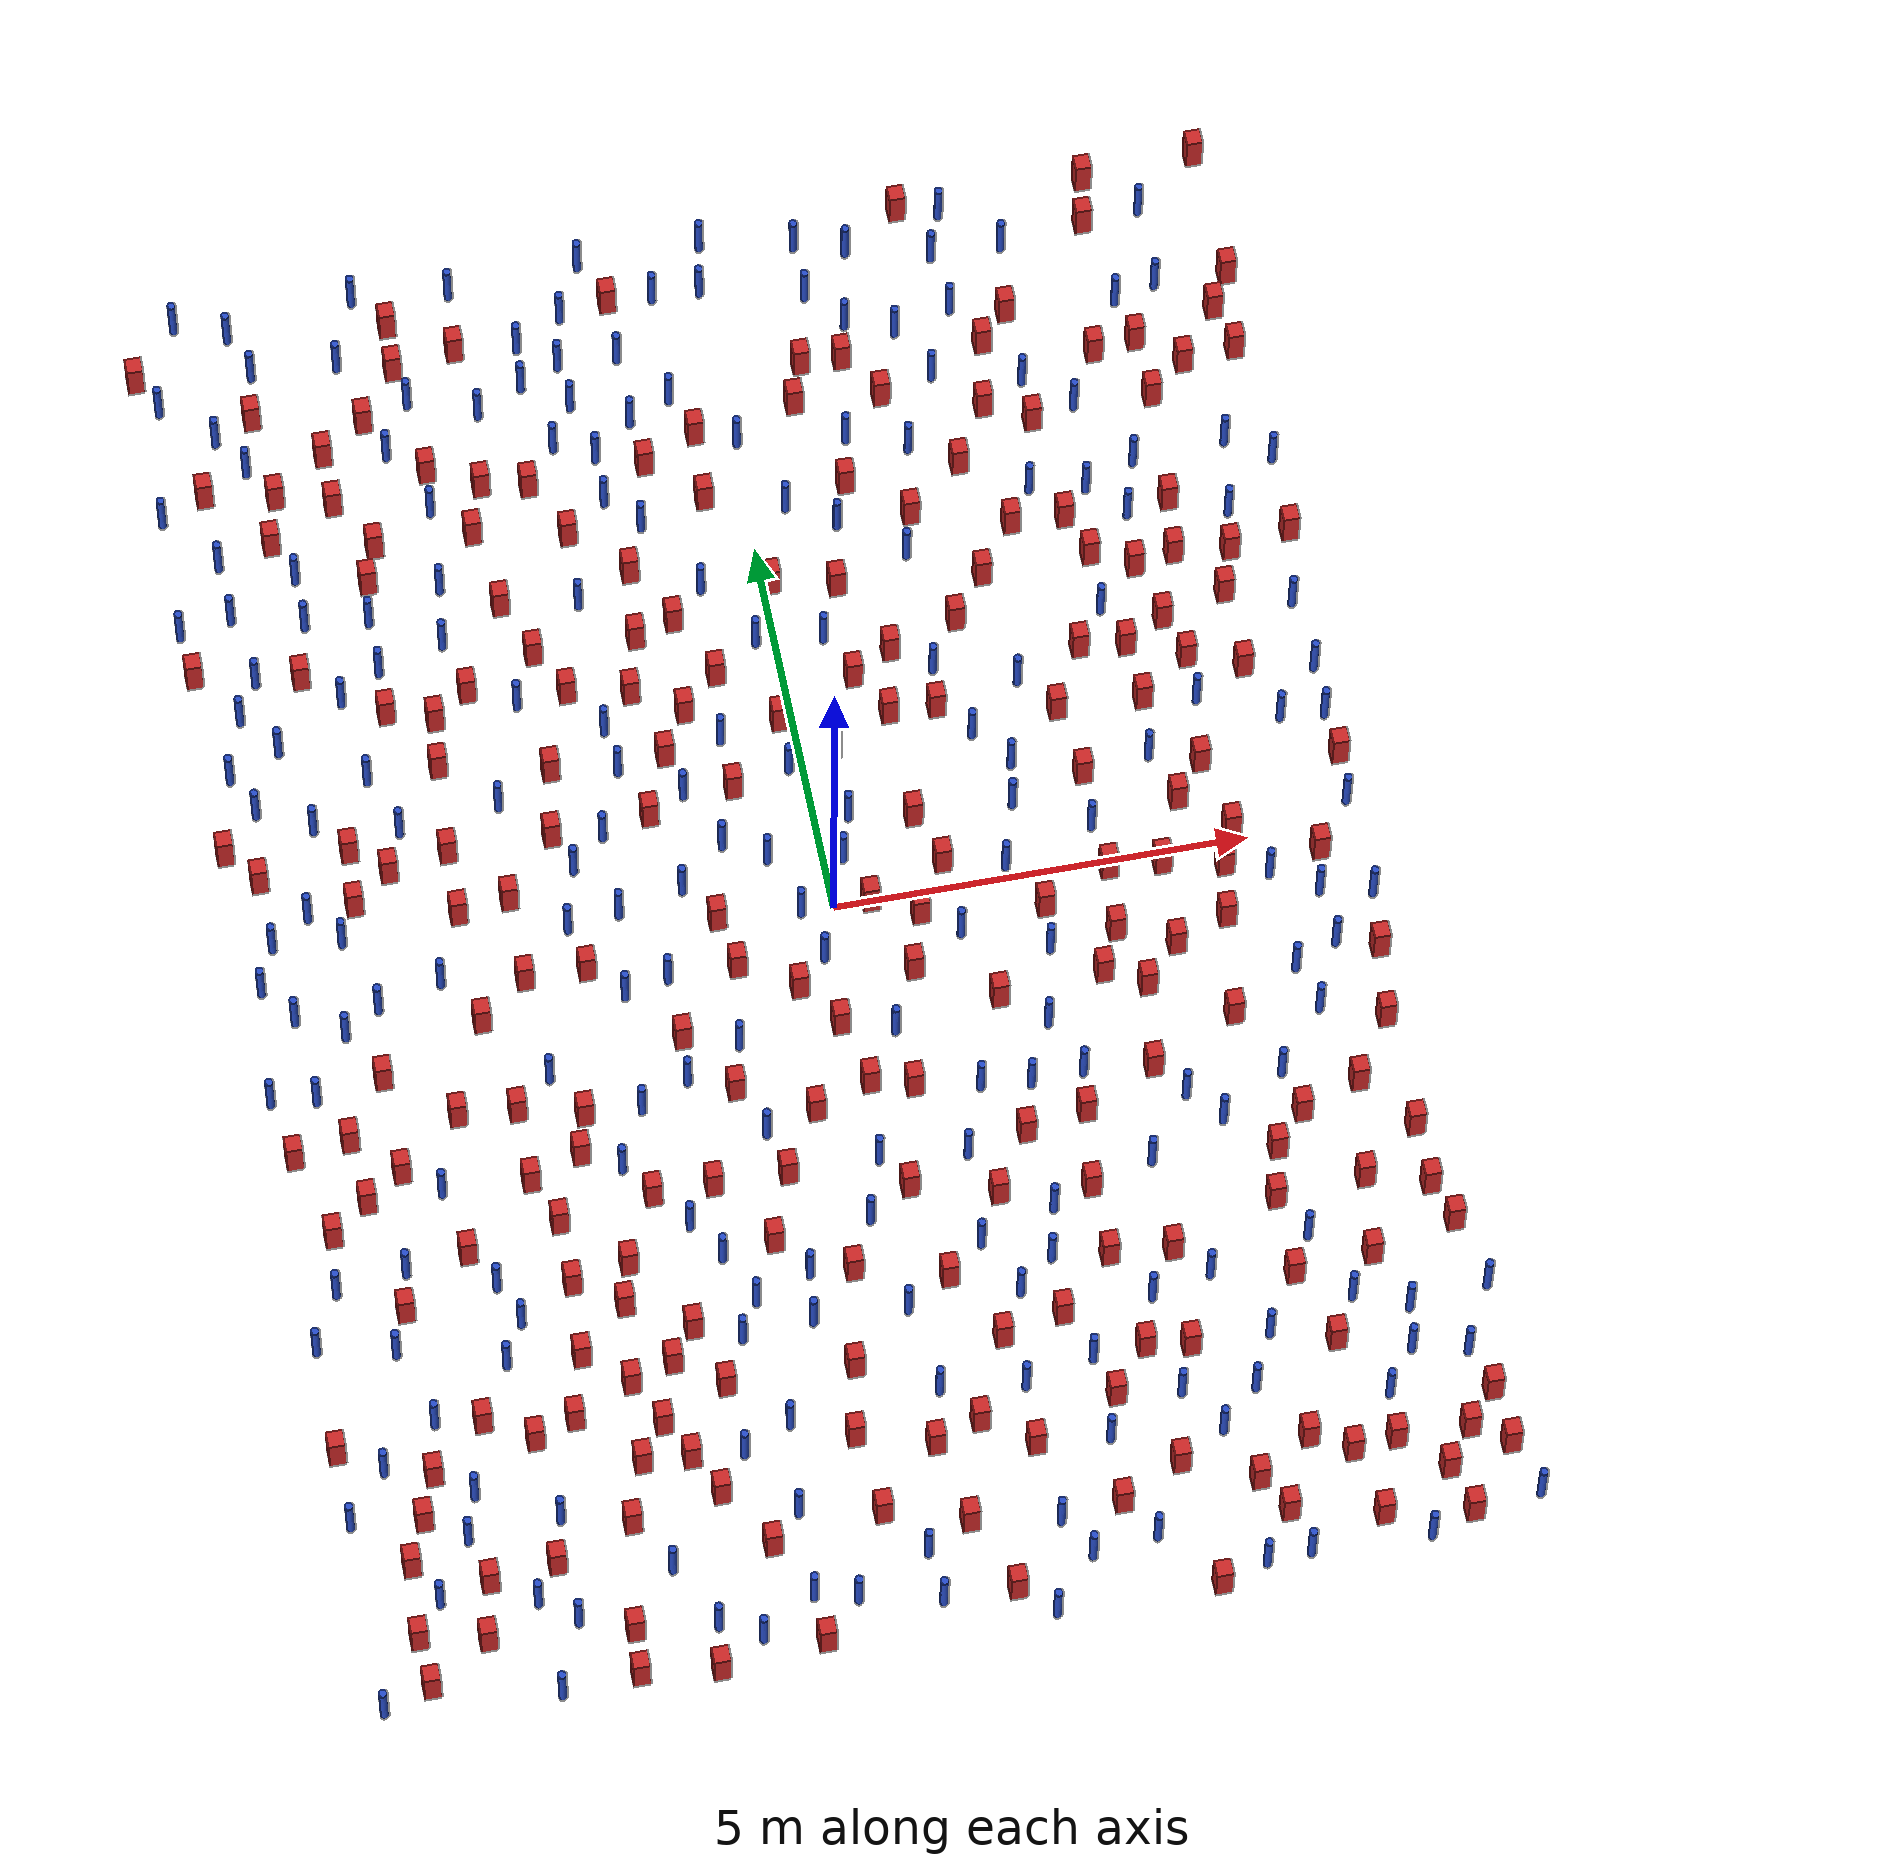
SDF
<sdf version="1.6">
  <model name="dense_97"><model name="pole_obstacle0">
  <static>true</static>
  <pose frame="">0.06913718363 6.49851287385 7.38925637345e-09 -8.47170692798e-08 1.24976765034e-08 -1.74513093019e-07</pose>
  <link name="link">
  <pose frame="">0 0 0.3 0 -0 0</pose>
    <inertial>
      <mass>1</mass>
      <inertia>
        <ixx>0.145833</ixx>
        <ixy>0</ixy>
        <ixz>0</ixz>
        <iyy>0.145833</iyy>
        <iyz>0</iyz>
        <izz>0.125</izz>
      </inertia>
    </inertial>
    <collision name="collision">
      <geometry>
        <cylinder>
          <radius>0.05</radius>
          <length>.6</length>
        </cylinder>
      </geometry>
      <max_contacts>10</max_contacts>
      <surface>
        <contact>
          <ode/>
        </contact>
        <bounce/>
        <friction>
          <torsional>
            <ode/>
          </torsional>
          <ode/>
        </friction>
      </surface>
    </collision>
    <visual name="visual">
      <geometry>
        <cylinder>
          <radius>0.05</radius>
          <length>.6</length>
        </cylinder>
      </geometry>
      <material>
        <script>
          <name>Gazebo/Blue</name>
          <uri>file://media/materials/scripts/gazebo.material</uri>
        </script>
      </material>
    </visual>
    <self_collide>0</self_collide>
    <kinematic>0</kinematic>
  </link>
</model>
<model name="pole_obstacle1">
  <static>true</static>
  <pose frame="">-1.19439407619 -4.70607036886 7.38925637345e-09 -8.47170692799e-08 1.24976765033e-08 -1.74513093018e-07</pose>
  <link name="link">
  <pose frame="">0 0 0.3 0 -0 0</pose>
    <inertial>
      <mass>1</mass>
      <inertia>
        <ixx>0.145833</ixx>
        <ixy>0</ixy>
        <ixz>0</ixz>
        <iyy>0.145833</iyy>
        <iyz>0</iyz>
        <izz>0.125</izz>
      </inertia>
    </inertial>
    <collision name="collision">
      <geometry>
        <cylinder>
          <radius>0.05</radius>
          <length>.6</length>
        </cylinder>
      </geometry>
      <max_contacts>10</max_contacts>
      <surface>
        <contact>
          <ode/>
        </contact>
        <bounce/>
        <friction>
          <torsional>
            <ode/>
          </torsional>
          <ode/>
        </friction>
      </surface>
    </collision>
    <visual name="visual">
      <geometry>
        <cylinder>
          <radius>0.05</radius>
          <length>.6</length>
        </cylinder>
      </geometry>
      <material>
        <script>
          <name>Gazebo/Blue</name>
          <uri>file://media/materials/scripts/gazebo.material</uri>
        </script>
      </material>
    </visual>
    <self_collide>0</self_collide>
    <kinematic>0</kinematic>
  </link>
</model>
<model name="square_post_obstacle0">
  <static>true</static>
  <pose frame="">-3.30379232446 5.81546871594 1.91545236811e-07 -7.35059704564e-06 1.12565212e-07 2.39332434364e-05</pose>
  <link name="link">
    <pose frame="">0 0 0.25 0 -0 0</pose>
    <inertial>
      <mass>100</mass>
      <inertia>
        <ixx>0.166667</ixx>
        <ixy>0</ixy>
        <ixz>0</ixz>
        <iyy>0.166667</iyy>
        <iyz>0</iyz>
        <izz>0.166667</izz>
      </inertia>
    </inertial>
    <collision name="collision">
      <geometry>
        <box>
          <size>.2 .2 .5</size>
        </box>
      </geometry>
      <max_contacts>10</max_contacts>
      <surface>
        <contact>
          <ode/>
        </contact>
        <bounce/>
        <friction>
          <torsional>
            <ode/>
          </torsional>
          <ode/>
        </friction>
      </surface>
    </collision>
    <visual name="visual">
      <geometry>
        <box>
          <size>.2 .2 .5</size>
        </box>
      </geometry>
      <material>
        <script>
          <name>Gazebo/Red</name>
          <uri>file://media/materials/scripts/gazebo.material</uri>
        </script>
      </material>
    </visual>
    <self_collide>0</self_collide>
    <kinematic>0</kinematic>
  </link>
</model>
<model name="square_post_obstacle1">
  <static>true</static>
  <pose frame="">3.60007113201 -8.70975381348 1.91545236811e-07 -7.35059704564e-06 1.12565212e-07 2.39332434364e-05</pose>
  <link name="link">
    <pose frame="">0 0 0.25 0 -0 0</pose>
    <inertial>
      <mass>100</mass>
      <inertia>
        <ixx>0.166667</ixx>
        <ixy>0</ixy>
        <ixz>0</ixz>
        <iyy>0.166667</iyy>
        <iyz>0</iyz>
        <izz>0.166667</izz>
      </inertia>
    </inertial>
    <collision name="collision">
      <geometry>
        <box>
          <size>.2 .2 .5</size>
        </box>
      </geometry>
      <max_contacts>10</max_contacts>
      <surface>
        <contact>
          <ode/>
        </contact>
        <bounce/>
        <friction>
          <torsional>
            <ode/>
          </torsional>
          <ode/>
        </friction>
      </surface>
    </collision>
    <visual name="visual">
      <geometry>
        <box>
          <size>.2 .2 .5</size>
        </box>
      </geometry>
      <material>
        <script>
          <name>Gazebo/Red</name>
          <uri>file://media/materials/scripts/gazebo.material</uri>
        </script>
      </material>
    </visual>
    <self_collide>0</self_collide>
    <kinematic>0</kinematic>
  </link>
</model>
<model name="pole_obstacle2">
  <static>true</static>
  <pose frame="">-5.77807198783 0.60570814513 7.38925637345e-09 -8.47170692799e-08 1.24976765038e-08 -1.74513093018e-07</pose>
  <link name="link">
  <pose frame="">0 0 0.3 0 -0 0</pose>
    <inertial>
      <mass>1</mass>
      <inertia>
        <ixx>0.145833</ixx>
        <ixy>0</ixy>
        <ixz>0</ixz>
        <iyy>0.145833</iyy>
        <iyz>0</iyz>
        <izz>0.125</izz>
      </inertia>
    </inertial>
    <collision name="collision">
      <geometry>
        <cylinder>
          <radius>0.05</radius>
          <length>.6</length>
        </cylinder>
      </geometry>
      <max_contacts>10</max_contacts>
      <surface>
        <contact>
          <ode/>
        </contact>
        <bounce/>
        <friction>
          <torsional>
            <ode/>
          </torsional>
          <ode/>
        </friction>
      </surface>
    </collision>
    <visual name="visual">
      <geometry>
        <cylinder>
          <radius>0.05</radius>
          <length>.6</length>
        </cylinder>
      </geometry>
      <material>
        <script>
          <name>Gazebo/Blue</name>
          <uri>file://media/materials/scripts/gazebo.material</uri>
        </script>
      </material>
    </visual>
    <self_collide>0</self_collide>
    <kinematic>0</kinematic>
  </link>
</model>
<model name="pole_obstacle3">
  <static>true</static>
  <pose frame="">2.62775557527 -5.74288238805 7.38925637345e-09 -8.47170692798e-08 1.24976765033e-08 -1.74513093019e-07</pose>
  <link name="link">
  <pose frame="">0 0 0.3 0 -0 0</pose>
    <inertial>
      <mass>1</mass>
      <inertia>
        <ixx>0.145833</ixx>
        <ixy>0</ixy>
        <ixz>0</ixz>
        <iyy>0.145833</iyy>
        <iyz>0</iyz>
        <izz>0.125</izz>
      </inertia>
    </inertial>
    <collision name="collision">
      <geometry>
        <cylinder>
          <radius>0.05</radius>
          <length>.6</length>
        </cylinder>
      </geometry>
      <max_contacts>10</max_contacts>
      <surface>
        <contact>
          <ode/>
        </contact>
        <bounce/>
        <friction>
          <torsional>
            <ode/>
          </torsional>
          <ode/>
        </friction>
      </surface>
    </collision>
    <visual name="visual">
      <geometry>
        <cylinder>
          <radius>0.05</radius>
          <length>.6</length>
        </cylinder>
      </geometry>
      <material>
        <script>
          <name>Gazebo/Blue</name>
          <uri>file://media/materials/scripts/gazebo.material</uri>
        </script>
      </material>
    </visual>
    <self_collide>0</self_collide>
    <kinematic>0</kinematic>
  </link>
</model>
<model name="pole_obstacle4">
  <static>true</static>
  <pose frame="">-2.3665419481 -6.82564515684 7.38925637345e-09 -8.47170692798e-08 1.24976765033e-08 -1.74513093019e-07</pose>
  <link name="link">
  <pose frame="">0 0 0.3 0 -0 0</pose>
    <inertial>
      <mass>1</mass>
      <inertia>
        <ixx>0.145833</ixx>
        <ixy>0</ixy>
        <ixz>0</ixz>
        <iyy>0.145833</iyy>
        <iyz>0</iyz>
        <izz>0.125</izz>
      </inertia>
    </inertial>
    <collision name="collision">
      <geometry>
        <cylinder>
          <radius>0.05</radius>
          <length>.6</length>
        </cylinder>
      </geometry>
      <max_contacts>10</max_contacts>
      <surface>
        <contact>
          <ode/>
        </contact>
        <bounce/>
        <friction>
          <torsional>
            <ode/>
          </torsional>
          <ode/>
        </friction>
      </surface>
    </collision>
    <visual name="visual">
      <geometry>
        <cylinder>
          <radius>0.05</radius>
          <length>.6</length>
        </cylinder>
      </geometry>
      <material>
        <script>
          <name>Gazebo/Blue</name>
          <uri>file://media/materials/scripts/gazebo.material</uri>
        </script>
      </material>
    </visual>
    <self_collide>0</self_collide>
    <kinematic>0</kinematic>
  </link>
</model>
<model name="pole_obstacle5">
  <static>true</static>
  <pose frame="">-6.08765010966 3.29022530019 7.38925637345e-09 -8.47170692798e-08 1.24976764937e-08 -1.74513093023e-07</pose>
  <link name="link">
  <pose frame="">0 0 0.3 0 -0 0</pose>
    <inertial>
      <mass>1</mass>
      <inertia>
        <ixx>0.145833</ixx>
        <ixy>0</ixy>
        <ixz>0</ixz>
        <iyy>0.145833</iyy>
        <iyz>0</iyz>
        <izz>0.125</izz>
      </inertia>
    </inertial>
    <collision name="collision">
      <geometry>
        <cylinder>
          <radius>0.05</radius>
          <length>.6</length>
        </cylinder>
      </geometry>
      <max_contacts>10</max_contacts>
      <surface>
        <contact>
          <ode/>
        </contact>
        <bounce/>
        <friction>
          <torsional>
            <ode/>
          </torsional>
          <ode/>
        </friction>
      </surface>
    </collision>
    <visual name="visual">
      <geometry>
        <cylinder>
          <radius>0.05</radius>
          <length>.6</length>
        </cylinder>
      </geometry>
      <material>
        <script>
          <name>Gazebo/Blue</name>
          <uri>file://media/materials/scripts/gazebo.material</uri>
        </script>
      </material>
    </visual>
    <self_collide>0</self_collide>
    <kinematic>0</kinematic>
  </link>
</model>
<model name="pole_obstacle6">
  <static>true</static>
  <pose frame="">4.7191671815 5.32754926063 7.38925637345e-09 -8.47170692796e-08 1.24976764786e-08 -1.74513093032e-07</pose>
  <link name="link">
  <pose frame="">0 0 0.3 0 -0 0</pose>
    <inertial>
      <mass>1</mass>
      <inertia>
        <ixx>0.145833</ixx>
        <ixy>0</ixy>
        <ixz>0</ixz>
        <iyy>0.145833</iyy>
        <iyz>0</iyz>
        <izz>0.125</izz>
      </inertia>
    </inertial>
    <collision name="collision">
      <geometry>
        <cylinder>
          <radius>0.05</radius>
          <length>.6</length>
        </cylinder>
      </geometry>
      <max_contacts>10</max_contacts>
      <surface>
        <contact>
          <ode/>
        </contact>
        <bounce/>
        <friction>
          <torsional>
            <ode/>
          </torsional>
          <ode/>
        </friction>
      </surface>
    </collision>
    <visual name="visual">
      <geometry>
        <cylinder>
          <radius>0.05</radius>
          <length>.6</length>
        </cylinder>
      </geometry>
      <material>
        <script>
          <name>Gazebo/Blue</name>
          <uri>file://media/materials/scripts/gazebo.material</uri>
        </script>
      </material>
    </visual>
    <self_collide>0</self_collide>
    <kinematic>0</kinematic>
  </link>
</model>
<model name="square_post_obstacle2">
  <static>true</static>
  <pose frame="">-0.00571309946755 -8.15404881912 1.91545236811e-07 -7.35059704564e-06 1.12565212e-07 2.39332434364e-05</pose>
  <link name="link">
    <pose frame="">0 0 0.25 0 -0 0</pose>
    <inertial>
      <mass>100</mass>
      <inertia>
        <ixx>0.166667</ixx>
        <ixy>0</ixy>
        <ixz>0</ixz>
        <iyy>0.166667</iyy>
        <iyz>0</iyz>
        <izz>0.166667</izz>
      </inertia>
    </inertial>
    <collision name="collision">
      <geometry>
        <box>
          <size>.2 .2 .5</size>
        </box>
      </geometry>
      <max_contacts>10</max_contacts>
      <surface>
        <contact>
          <ode/>
        </contact>
        <bounce/>
        <friction>
          <torsional>
            <ode/>
          </torsional>
          <ode/>
        </friction>
      </surface>
    </collision>
    <visual name="visual">
      <geometry>
        <box>
          <size>.2 .2 .5</size>
        </box>
      </geometry>
      <material>
        <script>
          <name>Gazebo/Red</name>
          <uri>file://media/materials/scripts/gazebo.material</uri>
        </script>
      </material>
    </visual>
    <self_collide>0</self_collide>
    <kinematic>0</kinematic>
  </link>
</model>
<model name="square_post_obstacle3">
  <static>true</static>
  <pose frame="">1.3197557422 3.28086362444 1.91545236811e-07 -7.35059704564e-06 1.12565212e-07 2.39332434364e-05</pose>
  <link name="link">
    <pose frame="">0 0 0.25 0 -0 0</pose>
    <inertial>
      <mass>100</mass>
      <inertia>
        <ixx>0.166667</ixx>
        <ixy>0</ixy>
        <ixz>0</ixz>
        <iyy>0.166667</iyy>
        <iyz>0</iyz>
        <izz>0.166667</izz>
      </inertia>
    </inertial>
    <collision name="collision">
      <geometry>
        <box>
          <size>.2 .2 .5</size>
        </box>
      </geometry>
      <max_contacts>10</max_contacts>
      <surface>
        <contact>
          <ode/>
        </contact>
        <bounce/>
        <friction>
          <torsional>
            <ode/>
          </torsional>
          <ode/>
        </friction>
      </surface>
    </collision>
    <visual name="visual">
      <geometry>
        <box>
          <size>.2 .2 .5</size>
        </box>
      </geometry>
      <material>
        <script>
          <name>Gazebo/Red</name>
          <uri>file://media/materials/scripts/gazebo.material</uri>
        </script>
      </material>
    </visual>
    <self_collide>0</self_collide>
    <kinematic>0</kinematic>
  </link>
</model>
<model name="square_post_obstacle4">
  <static>true</static>
  <pose frame="">0.83003484801 -5.93253629096 1.91545236811e-07 -7.35059704564e-06 1.12565212e-07 2.39332434364e-05</pose>
  <link name="link">
    <pose frame="">0 0 0.25 0 -0 0</pose>
    <inertial>
      <mass>100</mass>
      <inertia>
        <ixx>0.166667</ixx>
        <ixy>0</ixy>
        <ixz>0</ixz>
        <iyy>0.166667</iyy>
        <iyz>0</iyz>
        <izz>0.166667</izz>
      </inertia>
    </inertial>
    <collision name="collision">
      <geometry>
        <box>
          <size>.2 .2 .5</size>
        </box>
      </geometry>
      <max_contacts>10</max_contacts>
      <surface>
        <contact>
          <ode/>
        </contact>
        <bounce/>
        <friction>
          <torsional>
            <ode/>
          </torsional>
          <ode/>
        </friction>
      </surface>
    </collision>
    <visual name="visual">
      <geometry>
        <box>
          <size>.2 .2 .5</size>
        </box>
      </geometry>
      <material>
        <script>
          <name>Gazebo/Red</name>
          <uri>file://media/materials/scripts/gazebo.material</uri>
        </script>
      </material>
    </visual>
    <self_collide>0</self_collide>
    <kinematic>0</kinematic>
  </link>
</model>
<model name="pole_obstacle7">
  <static>true</static>
  <pose frame="">6.24190343363 1.45891795342 7.38925637345e-09 -8.471706928e-08 1.24976765134e-08 -1.74513093015e-07</pose>
  <link name="link">
  <pose frame="">0 0 0.3 0 -0 0</pose>
    <inertial>
      <mass>1</mass>
      <inertia>
        <ixx>0.145833</ixx>
        <ixy>0</ixy>
        <ixz>0</ixz>
        <iyy>0.145833</iyy>
        <iyz>0</iyz>
        <izz>0.125</izz>
      </inertia>
    </inertial>
    <collision name="collision">
      <geometry>
        <cylinder>
          <radius>0.05</radius>
          <length>.6</length>
        </cylinder>
      </geometry>
      <max_contacts>10</max_contacts>
      <surface>
        <contact>
          <ode/>
        </contact>
        <bounce/>
        <friction>
          <torsional>
            <ode/>
          </torsional>
          <ode/>
        </friction>
      </surface>
    </collision>
    <visual name="visual">
      <geometry>
        <cylinder>
          <radius>0.05</radius>
          <length>.6</length>
        </cylinder>
      </geometry>
      <material>
        <script>
          <name>Gazebo/Blue</name>
          <uri>file://media/materials/scripts/gazebo.material</uri>
        </script>
      </material>
    </visual>
    <self_collide>0</self_collide>
    <kinematic>0</kinematic>
  </link>
</model>
<model name="pole_obstacle8">
  <static>true</static>
  <pose frame="">-6.61200520473 -3.92718108275 7.38925637345e-09 -8.47170692798e-08 1.24976764937e-08 -1.74513093023e-07</pose>
  <link name="link">
  <pose frame="">0 0 0.3 0 -0 0</pose>
    <inertial>
      <mass>1</mass>
      <inertia>
        <ixx>0.145833</ixx>
        <ixy>0</ixy>
        <ixz>0</ixz>
        <iyy>0.145833</iyy>
        <iyz>0</iyz>
        <izz>0.125</izz>
      </inertia>
    </inertial>
    <collision name="collision">
      <geometry>
        <cylinder>
          <radius>0.05</radius>
          <length>.6</length>
        </cylinder>
      </geometry>
      <max_contacts>10</max_contacts>
      <surface>
        <contact>
          <ode/>
        </contact>
        <bounce/>
        <friction>
          <torsional>
            <ode/>
          </torsional>
          <ode/>
        </friction>
      </surface>
    </collision>
    <visual name="visual">
      <geometry>
        <cylinder>
          <radius>0.05</radius>
          <length>.6</length>
        </cylinder>
      </geometry>
      <material>
        <script>
          <name>Gazebo/Blue</name>
          <uri>file://media/materials/scripts/gazebo.material</uri>
        </script>
      </material>
    </visual>
    <self_collide>0</self_collide>
    <kinematic>0</kinematic>
  </link>
</model>
<model name="square_post_obstacle5">
  <static>true</static>
  <pose frame="">3.35127214875 -8.25828896306 1.91545236811e-07 -7.35059704564e-06 1.12565212e-07 2.39332434364e-05</pose>
  <link name="link">
    <pose frame="">0 0 0.25 0 -0 0</pose>
    <inertial>
      <mass>100</mass>
      <inertia>
        <ixx>0.166667</ixx>
        <ixy>0</ixy>
        <ixz>0</ixz>
        <iyy>0.166667</iyy>
        <iyz>0</iyz>
        <izz>0.166667</izz>
      </inertia>
    </inertial>
    <collision name="collision">
      <geometry>
        <box>
          <size>.2 .2 .5</size>
        </box>
      </geometry>
      <max_contacts>10</max_contacts>
      <surface>
        <contact>
          <ode/>
        </contact>
        <bounce/>
        <friction>
          <torsional>
            <ode/>
          </torsional>
          <ode/>
        </friction>
      </surface>
    </collision>
    <visual name="visual">
      <geometry>
        <box>
          <size>.2 .2 .5</size>
        </box>
      </geometry>
      <material>
        <script>
          <name>Gazebo/Red</name>
          <uri>file://media/materials/scripts/gazebo.material</uri>
        </script>
      </material>
    </visual>
    <self_collide>0</self_collide>
    <kinematic>0</kinematic>
  </link>
</model>
<model name="square_post_obstacle6">
  <static>true</static>
  <pose frame="">-6.60543335553 1.57570424143 1.91545236811e-07 -7.35059704564e-06 1.12565212e-07 2.39332434364e-05</pose>
  <link name="link">
    <pose frame="">0 0 0.25 0 -0 0</pose>
    <inertial>
      <mass>100</mass>
      <inertia>
        <ixx>0.166667</ixx>
        <ixy>0</ixy>
        <ixz>0</ixz>
        <iyy>0.166667</iyy>
        <iyz>0</iyz>
        <izz>0.166667</izz>
      </inertia>
    </inertial>
    <collision name="collision">
      <geometry>
        <box>
          <size>.2 .2 .5</size>
        </box>
      </geometry>
      <max_contacts>10</max_contacts>
      <surface>
        <contact>
          <ode/>
        </contact>
        <bounce/>
        <friction>
          <torsional>
            <ode/>
          </torsional>
          <ode/>
        </friction>
      </surface>
    </collision>
    <visual name="visual">
      <geometry>
        <box>
          <size>.2 .2 .5</size>
        </box>
      </geometry>
      <material>
        <script>
          <name>Gazebo/Red</name>
          <uri>file://media/materials/scripts/gazebo.material</uri>
        </script>
      </material>
    </visual>
    <self_collide>0</self_collide>
    <kinematic>0</kinematic>
  </link>
</model>
<model name="square_post_obstacle7">
  <static>true</static>
  <pose frame="">-5.49763663436 1.77760166691 1.91545236811e-07 -7.35059704564e-06 1.12565212e-07 2.39332434364e-05</pose>
  <link name="link">
    <pose frame="">0 0 0.25 0 -0 0</pose>
    <inertial>
      <mass>100</mass>
      <inertia>
        <ixx>0.166667</ixx>
        <ixy>0</ixy>
        <ixz>0</ixz>
        <iyy>0.166667</iyy>
        <iyz>0</iyz>
        <izz>0.166667</izz>
      </inertia>
    </inertial>
    <collision name="collision">
      <geometry>
        <box>
          <size>.2 .2 .5</size>
        </box>
      </geometry>
      <max_contacts>10</max_contacts>
      <surface>
        <contact>
          <ode/>
        </contact>
        <bounce/>
        <friction>
          <torsional>
            <ode/>
          </torsional>
          <ode/>
        </friction>
      </surface>
    </collision>
    <visual name="visual">
      <geometry>
        <box>
          <size>.2 .2 .5</size>
        </box>
      </geometry>
      <material>
        <script>
          <name>Gazebo/Red</name>
          <uri>file://media/materials/scripts/gazebo.material</uri>
        </script>
      </material>
    </visual>
    <self_collide>0</self_collide>
    <kinematic>0</kinematic>
  </link>
</model>
<model name="pole_obstacle9">
  <static>true</static>
  <pose frame="">-1.86990870558 7.98047728358 7.38925637345e-09 -8.47170692799e-08 1.24976764983e-08 -1.74513093021e-07</pose>
  <link name="link">
  <pose frame="">0 0 0.3 0 -0 0</pose>
    <inertial>
      <mass>1</mass>
      <inertia>
        <ixx>0.145833</ixx>
        <ixy>0</ixy>
        <ixz>0</ixz>
        <iyy>0.145833</iyy>
        <iyz>0</iyz>
        <izz>0.125</izz>
      </inertia>
    </inertial>
    <collision name="collision">
      <geometry>
        <cylinder>
          <radius>0.05</radius>
          <length>.6</length>
        </cylinder>
      </geometry>
      <max_contacts>10</max_contacts>
      <surface>
        <contact>
          <ode/>
        </contact>
        <bounce/>
        <friction>
          <torsional>
            <ode/>
          </torsional>
          <ode/>
        </friction>
      </surface>
    </collision>
    <visual name="visual">
      <geometry>
        <cylinder>
          <radius>0.05</radius>
          <length>.6</length>
        </cylinder>
      </geometry>
      <material>
        <script>
          <name>Gazebo/Blue</name>
          <uri>file://media/materials/scripts/gazebo.material</uri>
        </script>
      </material>
    </visual>
    <self_collide>0</self_collide>
    <kinematic>0</kinematic>
  </link>
</model>
<model name="pole_obstacle10">
  <static>true</static>
  <pose frame="">2.56371663117 6.97787891862 7.38925637345e-09 -8.47170692798e-08 1.24976765033e-08 -1.74513093019e-07</pose>
  <link name="link">
  <pose frame="">0 0 0.3 0 -0 0</pose>
    <inertial>
      <mass>1</mass>
      <inertia>
        <ixx>0.145833</ixx>
        <ixy>0</ixy>
        <ixz>0</ixz>
        <iyy>0.145833</iyy>
        <iyz>0</iyz>
        <izz>0.125</izz>
      </inertia>
    </inertial>
    <collision name="collision">
      <geometry>
        <cylinder>
          <radius>0.05</radius>
          <length>.6</length>
        </cylinder>
      </geometry>
      <max_contacts>10</max_contacts>
      <surface>
        <contact>
          <ode/>
        </contact>
        <bounce/>
        <friction>
          <torsional>
            <ode/>
          </torsional>
          <ode/>
        </friction>
      </surface>
    </collision>
    <visual name="visual">
      <geometry>
        <cylinder>
          <radius>0.05</radius>
          <length>.6</length>
        </cylinder>
      </geometry>
      <material>
        <script>
          <name>Gazebo/Blue</name>
          <uri>file://media/materials/scripts/gazebo.material</uri>
        </script>
      </material>
    </visual>
    <self_collide>0</self_collide>
    <kinematic>0</kinematic>
  </link>
</model>
<model name="pole_obstacle11">
  <static>true</static>
  <pose frame="">1.26733467987 8.39185915357 7.38925637345e-09 -8.47170692798e-08 1.24976764881e-08 -1.74513093027e-07</pose>
  <link name="link">
  <pose frame="">0 0 0.3 0 -0 0</pose>
    <inertial>
      <mass>1</mass>
      <inertia>
        <ixx>0.145833</ixx>
        <ixy>0</ixy>
        <ixz>0</ixz>
        <iyy>0.145833</iyy>
        <iyz>0</iyz>
        <izz>0.125</izz>
      </inertia>
    </inertial>
    <collision name="collision">
      <geometry>
        <cylinder>
          <radius>0.05</radius>
          <length>.6</length>
        </cylinder>
      </geometry>
      <max_contacts>10</max_contacts>
      <surface>
        <contact>
          <ode/>
        </contact>
        <bounce/>
        <friction>
          <torsional>
            <ode/>
          </torsional>
          <ode/>
        </friction>
      </surface>
    </collision>
    <visual name="visual">
      <geometry>
        <cylinder>
          <radius>0.05</radius>
          <length>.6</length>
        </cylinder>
      </geometry>
      <material>
        <script>
          <name>Gazebo/Blue</name>
          <uri>file://media/materials/scripts/gazebo.material</uri>
        </script>
      </material>
    </visual>
    <self_collide>0</self_collide>
    <kinematic>0</kinematic>
  </link>
</model>
<model name="pole_obstacle12">
  <static>true</static>
  <pose frame="">-6.95947929492 -4.61365307097 7.38925637345e-09 -8.47170692796e-08 1.24976764786e-08 -1.74513093032e-07</pose>
  <link name="link">
  <pose frame="">0 0 0.3 0 -0 0</pose>
    <inertial>
      <mass>1</mass>
      <inertia>
        <ixx>0.145833</ixx>
        <ixy>0</ixy>
        <ixz>0</ixz>
        <iyy>0.145833</iyy>
        <iyz>0</iyz>
        <izz>0.125</izz>
      </inertia>
    </inertial>
    <collision name="collision">
      <geometry>
        <cylinder>
          <radius>0.05</radius>
          <length>.6</length>
        </cylinder>
      </geometry>
      <max_contacts>10</max_contacts>
      <surface>
        <contact>
          <ode/>
        </contact>
        <bounce/>
        <friction>
          <torsional>
            <ode/>
          </torsional>
          <ode/>
        </friction>
      </surface>
    </collision>
    <visual name="visual">
      <geometry>
        <cylinder>
          <radius>0.05</radius>
          <length>.6</length>
        </cylinder>
      </geometry>
      <material>
        <script>
          <name>Gazebo/Blue</name>
          <uri>file://media/materials/scripts/gazebo.material</uri>
        </script>
      </material>
    </visual>
    <self_collide>0</self_collide>
    <kinematic>0</kinematic>
  </link>
</model>
<model name="square_post_obstacle8">
  <static>true</static>
  <pose frame="">-4.04077362499 -9.32479479458 1.91545236811e-07 -7.35059704564e-06 1.12565212e-07 2.39332434364e-05</pose>
  <link name="link">
    <pose frame="">0 0 0.25 0 -0 0</pose>
    <inertial>
      <mass>100</mass>
      <inertia>
        <ixx>0.166667</ixx>
        <ixy>0</ixy>
        <ixz>0</ixz>
        <iyy>0.166667</iyy>
        <iyz>0</iyz>
        <izz>0.166667</izz>
      </inertia>
    </inertial>
    <collision name="collision">
      <geometry>
        <box>
          <size>.2 .2 .5</size>
        </box>
      </geometry>
      <max_contacts>10</max_contacts>
      <surface>
        <contact>
          <ode/>
        </contact>
        <bounce/>
        <friction>
          <torsional>
            <ode/>
          </torsional>
          <ode/>
        </friction>
      </surface>
    </collision>
    <visual name="visual">
      <geometry>
        <box>
          <size>.2 .2 .5</size>
        </box>
      </geometry>
      <material>
        <script>
          <name>Gazebo/Red</name>
          <uri>file://media/materials/scripts/gazebo.material</uri>
        </script>
      </material>
    </visual>
    <self_collide>0</self_collide>
    <kinematic>0</kinematic>
  </link>
</model>
<model name="square_post_obstacle9">
  <static>true</static>
  <pose frame="">3.08837517718 6.42418481295 1.91545236811e-07 -7.35059704564e-06 1.12565212e-07 2.39332434364e-05</pose>
  <link name="link">
    <pose frame="">0 0 0.25 0 -0 0</pose>
    <inertial>
      <mass>100</mass>
      <inertia>
        <ixx>0.166667</ixx>
        <ixy>0</ixy>
        <ixz>0</ixz>
        <iyy>0.166667</iyy>
        <iyz>0</iyz>
        <izz>0.166667</izz>
      </inertia>
    </inertial>
    <collision name="collision">
      <geometry>
        <box>
          <size>.2 .2 .5</size>
        </box>
      </geometry>
      <max_contacts>10</max_contacts>
      <surface>
        <contact>
          <ode/>
        </contact>
        <bounce/>
        <friction>
          <torsional>
            <ode/>
          </torsional>
          <ode/>
        </friction>
      </surface>
    </collision>
    <visual name="visual">
      <geometry>
        <box>
          <size>.2 .2 .5</size>
        </box>
      </geometry>
      <material>
        <script>
          <name>Gazebo/Red</name>
          <uri>file://media/materials/scripts/gazebo.material</uri>
        </script>
      </material>
    </visual>
    <self_collide>0</self_collide>
    <kinematic>0</kinematic>
  </link>
</model>
<model name="pole_obstacle13">
  <static>true</static>
  <pose frame="">-4.58148329279 -4.7009422635 7.38925637345e-09 -8.47170692796e-08 1.24976764786e-08 -1.74513093032e-07</pose>
  <link name="link">
  <pose frame="">0 0 0.3 0 -0 0</pose>
    <inertial>
      <mass>1</mass>
      <inertia>
        <ixx>0.145833</ixx>
        <ixy>0</ixy>
        <ixz>0</ixz>
        <iyy>0.145833</iyy>
        <iyz>0</iyz>
        <izz>0.125</izz>
      </inertia>
    </inertial>
    <collision name="collision">
      <geometry>
        <cylinder>
          <radius>0.05</radius>
          <length>.6</length>
        </cylinder>
      </geometry>
      <max_contacts>10</max_contacts>
      <surface>
        <contact>
          <ode/>
        </contact>
        <bounce/>
        <friction>
          <torsional>
            <ode/>
          </torsional>
          <ode/>
        </friction>
      </surface>
    </collision>
    <visual name="visual">
      <geometry>
        <cylinder>
          <radius>0.05</radius>
          <length>.6</length>
        </cylinder>
      </geometry>
      <material>
        <script>
          <name>Gazebo/Blue</name>
          <uri>file://media/materials/scripts/gazebo.material</uri>
        </script>
      </material>
    </visual>
    <self_collide>0</self_collide>
    <kinematic>0</kinematic>
  </link>
</model>
<model name="square_post_obstacle10">
  <static>true</static>
  <pose frame="">3.24088928727 1.18970993105 1.91545236811e-07 -7.35059704564e-06 1.12565212e-07 2.39332434364e-05</pose>
  <link name="link">
    <pose frame="">0 0 0.25 0 -0 0</pose>
    <inertial>
      <mass>100</mass>
      <inertia>
        <ixx>0.166667</ixx>
        <ixy>0</ixy>
        <ixz>0</ixz>
        <iyy>0.166667</iyy>
        <iyz>0</iyz>
        <izz>0.166667</izz>
      </inertia>
    </inertial>
    <collision name="collision">
      <geometry>
        <box>
          <size>.2 .2 .5</size>
        </box>
      </geometry>
      <max_contacts>10</max_contacts>
      <surface>
        <contact>
          <ode/>
        </contact>
        <bounce/>
        <friction>
          <torsional>
            <ode/>
          </torsional>
          <ode/>
        </friction>
      </surface>
    </collision>
    <visual name="visual">
      <geometry>
        <box>
          <size>.2 .2 .5</size>
        </box>
      </geometry>
      <material>
        <script>
          <name>Gazebo/Red</name>
          <uri>file://media/materials/scripts/gazebo.material</uri>
        </script>
      </material>
    </visual>
    <self_collide>0</self_collide>
    <kinematic>0</kinematic>
  </link>
</model>
<model name="square_post_obstacle11">
  <static>true</static>
  <pose frame="">3.41142529525 -1.7442742198 1.91545236811e-07 -7.35059704564e-06 1.12565212e-07 2.39332434364e-05</pose>
  <link name="link">
    <pose frame="">0 0 0.25 0 -0 0</pose>
    <inertial>
      <mass>100</mass>
      <inertia>
        <ixx>0.166667</ixx>
        <ixy>0</ixy>
        <ixz>0</ixz>
        <iyy>0.166667</iyy>
        <iyz>0</iyz>
        <izz>0.166667</izz>
      </inertia>
    </inertial>
    <collision name="collision">
      <geometry>
        <box>
          <size>.2 .2 .5</size>
        </box>
      </geometry>
      <max_contacts>10</max_contacts>
      <surface>
        <contact>
          <ode/>
        </contact>
        <bounce/>
        <friction>
          <torsional>
            <ode/>
          </torsional>
          <ode/>
        </friction>
      </surface>
    </collision>
    <visual name="visual">
      <geometry>
        <box>
          <size>.2 .2 .5</size>
        </box>
      </geometry>
      <material>
        <script>
          <name>Gazebo/Red</name>
          <uri>file://media/materials/scripts/gazebo.material</uri>
        </script>
      </material>
    </visual>
    <self_collide>0</self_collide>
    <kinematic>0</kinematic>
  </link>
</model>
<model name="pole_obstacle14">
  <static>true</static>
  <pose frame="">0.746739444171 -9.45464630516 7.38925637345e-09 -8.47170692797e-08 1.249767648e-08 -1.74513093032e-07</pose>
  <link name="link">
  <pose frame="">0 0 0.3 0 -0 0</pose>
    <inertial>
      <mass>1</mass>
      <inertia>
        <ixx>0.145833</ixx>
        <ixy>0</ixy>
        <ixz>0</ixz>
        <iyy>0.145833</iyy>
        <iyz>0</iyz>
        <izz>0.125</izz>
      </inertia>
    </inertial>
    <collision name="collision">
      <geometry>
        <cylinder>
          <radius>0.05</radius>
          <length>.6</length>
        </cylinder>
      </geometry>
      <max_contacts>10</max_contacts>
      <surface>
        <contact>
          <ode/>
        </contact>
        <bounce/>
        <friction>
          <torsional>
            <ode/>
          </torsional>
          <ode/>
        </friction>
      </surface>
    </collision>
    <visual name="visual">
      <geometry>
        <cylinder>
          <radius>0.05</radius>
          <length>.6</length>
        </cylinder>
      </geometry>
      <material>
        <script>
          <name>Gazebo/Blue</name>
          <uri>file://media/materials/scripts/gazebo.material</uri>
        </script>
      </material>
    </visual>
    <self_collide>0</self_collide>
    <kinematic>0</kinematic>
  </link>
</model>
<model name="pole_obstacle15">
  <static>true</static>
  <pose frame="">0.3983858445 1.15659528781 7.38925637345e-09 -8.47170692798e-08 1.24976765025e-08 -1.74513093018e-07</pose>
  <link name="link">
  <pose frame="">0 0 0.3 0 -0 0</pose>
    <inertial>
      <mass>1</mass>
      <inertia>
        <ixx>0.145833</ixx>
        <ixy>0</ixy>
        <ixz>0</ixz>
        <iyy>0.145833</iyy>
        <iyz>0</iyz>
        <izz>0.125</izz>
      </inertia>
    </inertial>
    <collision name="collision">
      <geometry>
        <cylinder>
          <radius>0.05</radius>
          <length>.6</length>
        </cylinder>
      </geometry>
      <max_contacts>10</max_contacts>
      <surface>
        <contact>
          <ode/>
        </contact>
        <bounce/>
        <friction>
          <torsional>
            <ode/>
          </torsional>
          <ode/>
        </friction>
      </surface>
    </collision>
    <visual name="visual">
      <geometry>
        <cylinder>
          <radius>0.05</radius>
          <length>.6</length>
        </cylinder>
      </geometry>
      <material>
        <script>
          <name>Gazebo/Blue</name>
          <uri>file://media/materials/scripts/gazebo.material</uri>
        </script>
      </material>
    </visual>
    <self_collide>0</self_collide>
    <kinematic>0</kinematic>
  </link>
</model>
<model name="square_post_obstacle12">
  <static>true</static>
  <pose frame="">4.44881122704 -4.14483674699 1.91545236811e-07 -7.35059704564e-06 1.12565212e-07 2.39332434364e-05</pose>
  <link name="link">
    <pose frame="">0 0 0.25 0 -0 0</pose>
    <inertial>
      <mass>100</mass>
      <inertia>
        <ixx>0.166667</ixx>
        <ixy>0</ixy>
        <ixz>0</ixz>
        <iyy>0.166667</iyy>
        <iyz>0</iyz>
        <izz>0.166667</izz>
      </inertia>
    </inertial>
    <collision name="collision">
      <geometry>
        <box>
          <size>.2 .2 .5</size>
        </box>
      </geometry>
      <max_contacts>10</max_contacts>
      <surface>
        <contact>
          <ode/>
        </contact>
        <bounce/>
        <friction>
          <torsional>
            <ode/>
          </torsional>
          <ode/>
        </friction>
      </surface>
    </collision>
    <visual name="visual">
      <geometry>
        <box>
          <size>.2 .2 .5</size>
        </box>
      </geometry>
      <material>
        <script>
          <name>Gazebo/Red</name>
          <uri>file://media/materials/scripts/gazebo.material</uri>
        </script>
      </material>
    </visual>
    <self_collide>0</self_collide>
    <kinematic>0</kinematic>
  </link>
</model>
<model name="pole_obstacle16">
  <static>true</static>
  <pose frame="">2.89145582356 8.65972865751 7.38925637345e-09 -8.47170692793e-08 1.24976764408e-08 -1.74513093041e-07</pose>
  <link name="link">
  <pose frame="">0 0 0.3 0 -0 0</pose>
    <inertial>
      <mass>1</mass>
      <inertia>
        <ixx>0.145833</ixx>
        <ixy>0</ixy>
        <ixz>0</ixz>
        <iyy>0.145833</iyy>
        <iyz>0</iyz>
        <izz>0.125</izz>
      </inertia>
    </inertial>
    <collision name="collision">
      <geometry>
        <cylinder>
          <radius>0.05</radius>
          <length>.6</length>
        </cylinder>
      </geometry>
      <max_contacts>10</max_contacts>
      <surface>
        <contact>
          <ode/>
        </contact>
        <bounce/>
        <friction>
          <torsional>
            <ode/>
          </torsional>
          <ode/>
        </friction>
      </surface>
    </collision>
    <visual name="visual">
      <geometry>
        <cylinder>
          <radius>0.05</radius>
          <length>.6</length>
        </cylinder>
      </geometry>
      <material>
        <script>
          <name>Gazebo/Blue</name>
          <uri>file://media/materials/scripts/gazebo.material</uri>
        </script>
      </material>
    </visual>
    <self_collide>0</self_collide>
    <kinematic>0</kinematic>
  </link>
</model>
<model name="pole_obstacle17">
  <static>true</static>
  <pose frame="">0.426997091301 2.00244062308 7.38925637345e-09 -8.47170692799e-08 1.2497676506e-08 -1.74513093018e-07</pose>
  <link name="link">
  <pose frame="">0 0 0.3 0 -0 0</pose>
    <inertial>
      <mass>1</mass>
      <inertia>
        <ixx>0.145833</ixx>
        <ixy>0</ixy>
        <ixz>0</ixz>
        <iyy>0.145833</iyy>
        <iyz>0</iyz>
        <izz>0.125</izz>
      </inertia>
    </inertial>
    <collision name="collision">
      <geometry>
        <cylinder>
          <radius>0.05</radius>
          <length>.6</length>
        </cylinder>
      </geometry>
      <max_contacts>10</max_contacts>
      <surface>
        <contact>
          <ode/>
        </contact>
        <bounce/>
        <friction>
          <torsional>
            <ode/>
          </torsional>
          <ode/>
        </friction>
      </surface>
    </collision>
    <visual name="visual">
      <geometry>
        <cylinder>
          <radius>0.05</radius>
          <length>.6</length>
        </cylinder>
      </geometry>
      <material>
        <script>
          <name>Gazebo/Blue</name>
          <uri>file://media/materials/scripts/gazebo.material</uri>
        </script>
      </material>
    </visual>
    <self_collide>0</self_collide>
    <kinematic>0</kinematic>
  </link>
</model>
<model name="square_post_obstacle13">
  <static>true</static>
  <pose frame="">-2.41554761656 -5.9415160515 1.91545236811e-07 -7.35059704564e-06 1.12565212e-07 2.39332434364e-05</pose>
  <link name="link">
    <pose frame="">0 0 0.25 0 -0 0</pose>
    <inertial>
      <mass>100</mass>
      <inertia>
        <ixx>0.166667</ixx>
        <ixy>0</ixy>
        <ixz>0</ixz>
        <iyy>0.166667</iyy>
        <iyz>0</iyz>
        <izz>0.166667</izz>
      </inertia>
    </inertial>
    <collision name="collision">
      <geometry>
        <box>
          <size>.2 .2 .5</size>
        </box>
      </geometry>
      <max_contacts>10</max_contacts>
      <surface>
        <contact>
          <ode/>
        </contact>
        <bounce/>
        <friction>
          <torsional>
            <ode/>
          </torsional>
          <ode/>
        </friction>
      </surface>
    </collision>
    <visual name="visual">
      <geometry>
        <box>
          <size>.2 .2 .5</size>
        </box>
      </geometry>
      <material>
        <script>
          <name>Gazebo/Red</name>
          <uri>file://media/materials/scripts/gazebo.material</uri>
        </script>
      </material>
    </visual>
    <self_collide>0</self_collide>
    <kinematic>0</kinematic>
  </link>
</model>
<model name="pole_obstacle18">
  <static>true</static>
  <pose frame="">1.66351790398 7.89716667779 7.38925637345e-09 -8.47170692799e-08 1.24976765033e-08 -1.74513093018e-07</pose>
  <link name="link">
  <pose frame="">0 0 0.3 0 -0 0</pose>
    <inertial>
      <mass>1</mass>
      <inertia>
        <ixx>0.145833</ixx>
        <ixy>0</ixy>
        <ixz>0</ixz>
        <iyy>0.145833</iyy>
        <iyz>0</iyz>
        <izz>0.125</izz>
      </inertia>
    </inertial>
    <collision name="collision">
      <geometry>
        <cylinder>
          <radius>0.05</radius>
          <length>.6</length>
        </cylinder>
      </geometry>
      <max_contacts>10</max_contacts>
      <surface>
        <contact>
          <ode/>
        </contact>
        <bounce/>
        <friction>
          <torsional>
            <ode/>
          </torsional>
          <ode/>
        </friction>
      </surface>
    </collision>
    <visual name="visual">
      <geometry>
        <cylinder>
          <radius>0.05</radius>
          <length>.6</length>
        </cylinder>
      </geometry>
      <material>
        <script>
          <name>Gazebo/Blue</name>
          <uri>file://media/materials/scripts/gazebo.material</uri>
        </script>
      </material>
    </visual>
    <self_collide>0</self_collide>
    <kinematic>0</kinematic>
  </link>
</model>
<model name="square_post_obstacle14">
  <static>true</static>
  <pose frame="">-1.38984037299 0.0658818609446 1.91545236811e-07 -7.35059704564e-06 1.12565212e-07 2.39332434364e-05</pose>
  <link name="link">
    <pose frame="">0 0 0.25 0 -0 0</pose>
    <inertial>
      <mass>100</mass>
      <inertia>
        <ixx>0.166667</ixx>
        <ixy>0</ixy>
        <ixz>0</ixz>
        <iyy>0.166667</iyy>
        <iyz>0</iyz>
        <izz>0.166667</izz>
      </inertia>
    </inertial>
    <collision name="collision">
      <geometry>
        <box>
          <size>.2 .2 .5</size>
        </box>
      </geometry>
      <max_contacts>10</max_contacts>
      <surface>
        <contact>
          <ode/>
        </contact>
        <bounce/>
        <friction>
          <torsional>
            <ode/>
          </torsional>
          <ode/>
        </friction>
      </surface>
    </collision>
    <visual name="visual">
      <geometry>
        <box>
          <size>.2 .2 .5</size>
        </box>
      </geometry>
      <material>
        <script>
          <name>Gazebo/Red</name>
          <uri>file://media/materials/scripts/gazebo.material</uri>
        </script>
      </material>
    </visual>
    <self_collide>0</self_collide>
    <kinematic>0</kinematic>
  </link>
</model>
<model name="pole_obstacle19">
  <static>true</static>
  <pose frame="">-0.739754047334 4.5538869779 7.38925637345e-09 -8.471706928e-08 1.24976765086e-08 -1.74513093015e-07</pose>
  <link name="link">
  <pose frame="">0 0 0.3 0 -0 0</pose>
    <inertial>
      <mass>1</mass>
      <inertia>
        <ixx>0.145833</ixx>
        <ixy>0</ixy>
        <ixz>0</ixz>
        <iyy>0.145833</iyy>
        <iyz>0</iyz>
        <izz>0.125</izz>
      </inertia>
    </inertial>
    <collision name="collision">
      <geometry>
        <cylinder>
          <radius>0.05</radius>
          <length>.6</length>
        </cylinder>
      </geometry>
      <max_contacts>10</max_contacts>
      <surface>
        <contact>
          <ode/>
        </contact>
        <bounce/>
        <friction>
          <torsional>
            <ode/>
          </torsional>
          <ode/>
        </friction>
      </surface>
    </collision>
    <visual name="visual">
      <geometry>
        <cylinder>
          <radius>0.05</radius>
          <length>.6</length>
        </cylinder>
      </geometry>
      <material>
        <script>
          <name>Gazebo/Blue</name>
          <uri>file://media/materials/scripts/gazebo.material</uri>
        </script>
      </material>
    </visual>
    <self_collide>0</self_collide>
    <kinematic>0</kinematic>
  </link>
</model>
<model name="square_post_obstacle15">
  <static>true</static>
  <pose frame="">2.59474911007 9.38308326705 1.91545236811e-07 -7.35059704564e-06 1.12565212e-07 2.39332434364e-05</pose>
  <link name="link">
    <pose frame="">0 0 0.25 0 -0 0</pose>
    <inertial>
      <mass>100</mass>
      <inertia>
        <ixx>0.166667</ixx>
        <ixy>0</ixy>
        <ixz>0</ixz>
        <iyy>0.166667</iyy>
        <iyz>0</iyz>
        <izz>0.166667</izz>
      </inertia>
    </inertial>
    <collision name="collision">
      <geometry>
        <box>
          <size>.2 .2 .5</size>
        </box>
      </geometry>
      <max_contacts>10</max_contacts>
      <surface>
        <contact>
          <ode/>
        </contact>
        <bounce/>
        <friction>
          <torsional>
            <ode/>
          </torsional>
          <ode/>
        </friction>
      </surface>
    </collision>
    <visual name="visual">
      <geometry>
        <box>
          <size>.2 .2 .5</size>
        </box>
      </geometry>
      <material>
        <script>
          <name>Gazebo/Red</name>
          <uri>file://media/materials/scripts/gazebo.material</uri>
        </script>
      </material>
    </visual>
    <self_collide>0</self_collide>
    <kinematic>0</kinematic>
  </link>
</model>
<model name="square_post_obstacle16">
  <static>true</static>
  <pose frame="">-3.0197415728 -0.309027023524 1.91545236811e-07 -7.35059704564e-06 1.12565212e-07 2.39332434364e-05</pose>
  <link name="link">
    <pose frame="">0 0 0.25 0 -0 0</pose>
    <inertial>
      <mass>100</mass>
      <inertia>
        <ixx>0.166667</ixx>
        <ixy>0</ixy>
        <ixz>0</ixz>
        <iyy>0.166667</iyy>
        <iyz>0</iyz>
        <izz>0.166667</izz>
      </inertia>
    </inertial>
    <collision name="collision">
      <geometry>
        <box>
          <size>.2 .2 .5</size>
        </box>
      </geometry>
      <max_contacts>10</max_contacts>
      <surface>
        <contact>
          <ode/>
        </contact>
        <bounce/>
        <friction>
          <torsional>
            <ode/>
          </torsional>
          <ode/>
        </friction>
      </surface>
    </collision>
    <visual name="visual">
      <geometry>
        <box>
          <size>.2 .2 .5</size>
        </box>
      </geometry>
      <material>
        <script>
          <name>Gazebo/Red</name>
          <uri>file://media/materials/scripts/gazebo.material</uri>
        </script>
      </material>
    </visual>
    <self_collide>0</self_collide>
    <kinematic>0</kinematic>
  </link>
</model>
<model name="square_post_obstacle17">
  <static>true</static>
  <pose frame="">-6.39003009982 6.93364635513 1.91545236811e-07 -7.35059704564e-06 1.12565212e-07 2.39332434364e-05</pose>
  <link name="link">
    <pose frame="">0 0 0.25 0 -0 0</pose>
    <inertial>
      <mass>100</mass>
      <inertia>
        <ixx>0.166667</ixx>
        <ixy>0</ixy>
        <ixz>0</ixz>
        <iyy>0.166667</iyy>
        <iyz>0</iyz>
        <izz>0.166667</izz>
      </inertia>
    </inertial>
    <collision name="collision">
      <geometry>
        <box>
          <size>.2 .2 .5</size>
        </box>
      </geometry>
      <max_contacts>10</max_contacts>
      <surface>
        <contact>
          <ode/>
        </contact>
        <bounce/>
        <friction>
          <torsional>
            <ode/>
          </torsional>
          <ode/>
        </friction>
      </surface>
    </collision>
    <visual name="visual">
      <geometry>
        <box>
          <size>.2 .2 .5</size>
        </box>
      </geometry>
      <material>
        <script>
          <name>Gazebo/Red</name>
          <uri>file://media/materials/scripts/gazebo.material</uri>
        </script>
      </material>
    </visual>
    <self_collide>0</self_collide>
    <kinematic>0</kinematic>
  </link>
</model>
<model name="pole_obstacle20">
  <static>true</static>
  <pose frame="">-1.78473109036 -6.55529886067 7.38925637345e-09 -8.47170692799e-08 1.24976765033e-08 -1.74513093018e-07</pose>
  <link name="link">
  <pose frame="">0 0 0.3 0 -0 0</pose>
    <inertial>
      <mass>1</mass>
      <inertia>
        <ixx>0.145833</ixx>
        <ixy>0</ixy>
        <ixz>0</ixz>
        <iyy>0.145833</iyy>
        <iyz>0</iyz>
        <izz>0.125</izz>
      </inertia>
    </inertial>
    <collision name="collision">
      <geometry>
        <cylinder>
          <radius>0.05</radius>
          <length>.6</length>
        </cylinder>
      </geometry>
      <max_contacts>10</max_contacts>
      <surface>
        <contact>
          <ode/>
        </contact>
        <bounce/>
        <friction>
          <torsional>
            <ode/>
          </torsional>
          <ode/>
        </friction>
      </surface>
    </collision>
    <visual name="visual">
      <geometry>
        <cylinder>
          <radius>0.05</radius>
          <length>.6</length>
        </cylinder>
      </geometry>
      <material>
        <script>
          <name>Gazebo/Blue</name>
          <uri>file://media/materials/scripts/gazebo.material</uri>
        </script>
      </material>
    </visual>
    <self_collide>0</self_collide>
    <kinematic>0</kinematic>
  </link>
</model>
<model name="pole_obstacle21">
  <static>true</static>
  <pose frame="">-0.541925971555 -8.44060490971 7.38925637345e-09 -8.47170692796e-08 1.24976764704e-08 -1.74513093037e-07</pose>
  <link name="link">
  <pose frame="">0 0 0.3 0 -0 0</pose>
    <inertial>
      <mass>1</mass>
      <inertia>
        <ixx>0.145833</ixx>
        <ixy>0</ixy>
        <ixz>0</ixz>
        <iyy>0.145833</iyy>
        <iyz>0</iyz>
        <izz>0.125</izz>
      </inertia>
    </inertial>
    <collision name="collision">
      <geometry>
        <cylinder>
          <radius>0.05</radius>
          <length>.6</length>
        </cylinder>
      </geometry>
      <max_contacts>10</max_contacts>
      <surface>
        <contact>
          <ode/>
        </contact>
        <bounce/>
        <friction>
          <torsional>
            <ode/>
          </torsional>
          <ode/>
        </friction>
      </surface>
    </collision>
    <visual name="visual">
      <geometry>
        <cylinder>
          <radius>0.05</radius>
          <length>.6</length>
        </cylinder>
      </geometry>
      <material>
        <script>
          <name>Gazebo/Blue</name>
          <uri>file://media/materials/scripts/gazebo.material</uri>
        </script>
      </material>
    </visual>
    <self_collide>0</self_collide>
    <kinematic>0</kinematic>
  </link>
</model>
<model name="pole_obstacle22">
  <static>true</static>
  <pose frame="">-2.50910660701 0.369215138219 7.38925637345e-09 -8.471706928e-08 1.24976765172e-08 -1.74513093013e-07</pose>
  <link name="link">
  <pose frame="">0 0 0.3 0 -0 0</pose>
    <inertial>
      <mass>1</mass>
      <inertia>
        <ixx>0.145833</ixx>
        <ixy>0</ixy>
        <ixz>0</ixz>
        <iyy>0.145833</iyy>
        <iyz>0</iyz>
        <izz>0.125</izz>
      </inertia>
    </inertial>
    <collision name="collision">
      <geometry>
        <cylinder>
          <radius>0.05</radius>
          <length>.6</length>
        </cylinder>
      </geometry>
      <max_contacts>10</max_contacts>
      <surface>
        <contact>
          <ode/>
        </contact>
        <bounce/>
        <friction>
          <torsional>
            <ode/>
          </torsional>
          <ode/>
        </friction>
      </surface>
    </collision>
    <visual name="visual">
      <geometry>
        <cylinder>
          <radius>0.05</radius>
          <length>.6</length>
        </cylinder>
      </geometry>
      <material>
        <script>
          <name>Gazebo/Blue</name>
          <uri>file://media/materials/scripts/gazebo.material</uri>
        </script>
      </material>
    </visual>
    <self_collide>0</self_collide>
    <kinematic>0</kinematic>
  </link>
</model>
<model name="pole_obstacle23">
  <static>true</static>
  <pose frame="">3.09948274819 9.24637442465 7.38925637345e-09 -8.47170692793e-08 1.24976764408e-08 -1.74513093041e-07</pose>
  <link name="link">
  <pose frame="">0 0 0.3 0 -0 0</pose>
    <inertial>
      <mass>1</mass>
      <inertia>
        <ixx>0.145833</ixx>
        <ixy>0</ixy>
        <ixz>0</ixz>
        <iyy>0.145833</iyy>
        <iyz>0</iyz>
        <izz>0.125</izz>
      </inertia>
    </inertial>
    <collision name="collision">
      <geometry>
        <cylinder>
          <radius>0.05</radius>
          <length>.6</length>
        </cylinder>
      </geometry>
      <max_contacts>10</max_contacts>
      <surface>
        <contact>
          <ode/>
        </contact>
        <bounce/>
        <friction>
          <torsional>
            <ode/>
          </torsional>
          <ode/>
        </friction>
      </surface>
    </collision>
    <visual name="visual">
      <geometry>
        <cylinder>
          <radius>0.05</radius>
          <length>.6</length>
        </cylinder>
      </geometry>
      <material>
        <script>
          <name>Gazebo/Blue</name>
          <uri>file://media/materials/scripts/gazebo.material</uri>
        </script>
      </material>
    </visual>
    <self_collide>0</self_collide>
    <kinematic>0</kinematic>
  </link>
</model>
<model name="square_post_obstacle18">
  <static>true</static>
  <pose frame="">0.0977057017905 4.46174153704 1.91545236811e-07 -7.35059704564e-06 1.12565212e-07 2.39332434364e-05</pose>
  <link name="link">
    <pose frame="">0 0 0.25 0 -0 0</pose>
    <inertial>
      <mass>100</mass>
      <inertia>
        <ixx>0.166667</ixx>
        <ixy>0</ixy>
        <ixz>0</ixz>
        <iyy>0.166667</iyy>
        <iyz>0</iyz>
        <izz>0.166667</izz>
      </inertia>
    </inertial>
    <collision name="collision">
      <geometry>
        <box>
          <size>.2 .2 .5</size>
        </box>
      </geometry>
      <max_contacts>10</max_contacts>
      <surface>
        <contact>
          <ode/>
        </contact>
        <bounce/>
        <friction>
          <torsional>
            <ode/>
          </torsional>
          <ode/>
        </friction>
      </surface>
    </collision>
    <visual name="visual">
      <geometry>
        <box>
          <size>.2 .2 .5</size>
        </box>
      </geometry>
      <material>
        <script>
          <name>Gazebo/Red</name>
          <uri>file://media/materials/scripts/gazebo.material</uri>
        </script>
      </material>
    </visual>
    <self_collide>0</self_collide>
    <kinematic>0</kinematic>
  </link>
</model>
<model name="pole_obstacle24">
  <static>true</static>
  <pose frame="">1.03663892771 5.12717030944 7.38925637345e-09 -8.47170692799e-08 1.24976765021e-08 -1.74513093019e-07</pose>
  <link name="link">
  <pose frame="">0 0 0.3 0 -0 0</pose>
    <inertial>
      <mass>1</mass>
      <inertia>
        <ixx>0.145833</ixx>
        <ixy>0</ixy>
        <ixz>0</ixz>
        <iyy>0.145833</iyy>
        <iyz>0</iyz>
        <izz>0.125</izz>
      </inertia>
    </inertial>
    <collision name="collision">
      <geometry>
        <cylinder>
          <radius>0.05</radius>
          <length>.6</length>
        </cylinder>
      </geometry>
      <max_contacts>10</max_contacts>
      <surface>
        <contact>
          <ode/>
        </contact>
        <bounce/>
        <friction>
          <torsional>
            <ode/>
          </torsional>
          <ode/>
        </friction>
      </surface>
    </collision>
    <visual name="visual">
      <geometry>
        <cylinder>
          <radius>0.05</radius>
          <length>.6</length>
        </cylinder>
      </geometry>
      <material>
        <script>
          <name>Gazebo/Blue</name>
          <uri>file://media/materials/scripts/gazebo.material</uri>
        </script>
      </material>
    </visual>
    <self_collide>0</self_collide>
    <kinematic>0</kinematic>
  </link>
</model>
<model name="pole_obstacle25">
  <static>true</static>
  <pose frame="">0.904775360548 -3.52407506099 7.38925637345e-09 -8.47170692799e-08 1.2497676509e-08 -1.74513093016e-07</pose>
  <link name="link">
  <pose frame="">0 0 0.3 0 -0 0</pose>
    <inertial>
      <mass>1</mass>
      <inertia>
        <ixx>0.145833</ixx>
        <ixy>0</ixy>
        <ixz>0</ixz>
        <iyy>0.145833</iyy>
        <iyz>0</iyz>
        <izz>0.125</izz>
      </inertia>
    </inertial>
    <collision name="collision">
      <geometry>
        <cylinder>
          <radius>0.05</radius>
          <length>.6</length>
        </cylinder>
      </geometry>
      <max_contacts>10</max_contacts>
      <surface>
        <contact>
          <ode/>
        </contact>
        <bounce/>
        <friction>
          <torsional>
            <ode/>
          </torsional>
          <ode/>
        </friction>
      </surface>
    </collision>
    <visual name="visual">
      <geometry>
        <cylinder>
          <radius>0.05</radius>
          <length>.6</length>
        </cylinder>
      </geometry>
      <material>
        <script>
          <name>Gazebo/Blue</name>
          <uri>file://media/materials/scripts/gazebo.material</uri>
        </script>
      </material>
    </visual>
    <self_collide>0</self_collide>
    <kinematic>0</kinematic>
  </link>
</model>
<model name="pole_obstacle26">
  <static>true</static>
  <pose frame="">5.42265023992 -6.95552953939 7.38925637345e-09 -8.47170692796e-08 1.24976764786e-08 -1.74513093032e-07</pose>
  <link name="link">
  <pose frame="">0 0 0.3 0 -0 0</pose>
    <inertial>
      <mass>1</mass>
      <inertia>
        <ixx>0.145833</ixx>
        <ixy>0</ixy>
        <ixz>0</ixz>
        <iyy>0.145833</iyy>
        <iyz>0</iyz>
        <izz>0.125</izz>
      </inertia>
    </inertial>
    <collision name="collision">
      <geometry>
        <cylinder>
          <radius>0.05</radius>
          <length>.6</length>
        </cylinder>
      </geometry>
      <max_contacts>10</max_contacts>
      <surface>
        <contact>
          <ode/>
        </contact>
        <bounce/>
        <friction>
          <torsional>
            <ode/>
          </torsional>
          <ode/>
        </friction>
      </surface>
    </collision>
    <visual name="visual">
      <geometry>
        <cylinder>
          <radius>0.05</radius>
          <length>.6</length>
        </cylinder>
      </geometry>
      <material>
        <script>
          <name>Gazebo/Blue</name>
          <uri>file://media/materials/scripts/gazebo.material</uri>
        </script>
      </material>
    </visual>
    <self_collide>0</self_collide>
    <kinematic>0</kinematic>
  </link>
</model>
<model name="pole_obstacle27">
  <static>true</static>
  <pose frame="">-4.73113722554 4.85528450265 7.38925637345e-09 -8.47170692796e-08 1.24976764786e-08 -1.74513093032e-07</pose>
  <link name="link">
  <pose frame="">0 0 0.3 0 -0 0</pose>
    <inertial>
      <mass>1</mass>
      <inertia>
        <ixx>0.145833</ixx>
        <ixy>0</ixy>
        <ixz>0</ixz>
        <iyy>0.145833</iyy>
        <iyz>0</iyz>
        <izz>0.125</izz>
      </inertia>
    </inertial>
    <collision name="collision">
      <geometry>
        <cylinder>
          <radius>0.05</radius>
          <length>.6</length>
        </cylinder>
      </geometry>
      <max_contacts>10</max_contacts>
      <surface>
        <contact>
          <ode/>
        </contact>
        <bounce/>
        <friction>
          <torsional>
            <ode/>
          </torsional>
          <ode/>
        </friction>
      </surface>
    </collision>
    <visual name="visual">
      <geometry>
        <cylinder>
          <radius>0.05</radius>
          <length>.6</length>
        </cylinder>
      </geometry>
      <material>
        <script>
          <name>Gazebo/Blue</name>
          <uri>file://media/materials/scripts/gazebo.material</uri>
        </script>
      </material>
    </visual>
    <self_collide>0</self_collide>
    <kinematic>0</kinematic>
  </link>
</model>
<model name="pole_obstacle28">
  <static>true</static>
  <pose frame="">5.33406300753 -2.4171179551 7.38925637345e-09 -8.47170692798e-08 1.24976764937e-08 -1.74513093023e-07</pose>
  <link name="link">
  <pose frame="">0 0 0.3 0 -0 0</pose>
    <inertial>
      <mass>1</mass>
      <inertia>
        <ixx>0.145833</ixx>
        <ixy>0</ixy>
        <ixz>0</ixz>
        <iyy>0.145833</iyy>
        <iyz>0</iyz>
        <izz>0.125</izz>
      </inertia>
    </inertial>
    <collision name="collision">
      <geometry>
        <cylinder>
          <radius>0.05</radius>
          <length>.6</length>
        </cylinder>
      </geometry>
      <max_contacts>10</max_contacts>
      <surface>
        <contact>
          <ode/>
        </contact>
        <bounce/>
        <friction>
          <torsional>
            <ode/>
          </torsional>
          <ode/>
        </friction>
      </surface>
    </collision>
    <visual name="visual">
      <geometry>
        <cylinder>
          <radius>0.05</radius>
          <length>.6</length>
        </cylinder>
      </geometry>
      <material>
        <script>
          <name>Gazebo/Blue</name>
          <uri>file://media/materials/scripts/gazebo.material</uri>
        </script>
      </material>
    </visual>
    <self_collide>0</self_collide>
    <kinematic>0</kinematic>
  </link>
</model>
<model name="square_post_obstacle19">
  <static>true</static>
  <pose frame="">2.92785680124 -6.44692021054 1.91545236811e-07 -7.35059704564e-06 1.12565212e-07 2.39332434364e-05</pose>
  <link name="link">
    <pose frame="">0 0 0.25 0 -0 0</pose>
    <inertial>
      <mass>100</mass>
      <inertia>
        <ixx>0.166667</ixx>
        <ixy>0</ixy>
        <ixz>0</ixz>
        <iyy>0.166667</iyy>
        <iyz>0</iyz>
        <izz>0.166667</izz>
      </inertia>
    </inertial>
    <collision name="collision">
      <geometry>
        <box>
          <size>.2 .2 .5</size>
        </box>
      </geometry>
      <max_contacts>10</max_contacts>
      <surface>
        <contact>
          <ode/>
        </contact>
        <bounce/>
        <friction>
          <torsional>
            <ode/>
          </torsional>
          <ode/>
        </friction>
      </surface>
    </collision>
    <visual name="visual">
      <geometry>
        <box>
          <size>.2 .2 .5</size>
        </box>
      </geometry>
      <material>
        <script>
          <name>Gazebo/Red</name>
          <uri>file://media/materials/scripts/gazebo.material</uri>
        </script>
      </material>
    </visual>
    <self_collide>0</self_collide>
    <kinematic>0</kinematic>
  </link>
</model>
<model name="square_post_obstacle20">
  <static>true</static>
  <pose frame="">1.3652218517 0.3256208881 1.91545236811e-07 -7.35059704564e-06 1.12565212e-07 2.39332434364e-05</pose>
  <link name="link">
    <pose frame="">0 0 0.25 0 -0 0</pose>
    <inertial>
      <mass>100</mass>
      <inertia>
        <ixx>0.166667</ixx>
        <ixy>0</ixy>
        <ixz>0</ixz>
        <iyy>0.166667</iyy>
        <iyz>0</iyz>
        <izz>0.166667</izz>
      </inertia>
    </inertial>
    <collision name="collision">
      <geometry>
        <box>
          <size>.2 .2 .5</size>
        </box>
      </geometry>
      <max_contacts>10</max_contacts>
      <surface>
        <contact>
          <ode/>
        </contact>
        <bounce/>
        <friction>
          <torsional>
            <ode/>
          </torsional>
          <ode/>
        </friction>
      </surface>
    </collision>
    <visual name="visual">
      <geometry>
        <box>
          <size>.2 .2 .5</size>
        </box>
      </geometry>
      <material>
        <script>
          <name>Gazebo/Red</name>
          <uri>file://media/materials/scripts/gazebo.material</uri>
        </script>
      </material>
    </visual>
    <self_collide>0</self_collide>
    <kinematic>0</kinematic>
  </link>
</model>
<model name="pole_obstacle29">
  <static>true</static>
  <pose frame="">-4.94553480234 -9.38782219653 7.38925637345e-09 -8.471706928e-08 1.24976765081e-08 -1.74513093015e-07</pose>
  <link name="link">
  <pose frame="">0 0 0.3 0 -0 0</pose>
    <inertial>
      <mass>1</mass>
      <inertia>
        <ixx>0.145833</ixx>
        <ixy>0</ixy>
        <ixz>0</ixz>
        <iyy>0.145833</iyy>
        <iyz>0</iyz>
        <izz>0.125</izz>
      </inertia>
    </inertial>
    <collision name="collision">
      <geometry>
        <cylinder>
          <radius>0.05</radius>
          <length>.6</length>
        </cylinder>
      </geometry>
      <max_contacts>10</max_contacts>
      <surface>
        <contact>
          <ode/>
        </contact>
        <bounce/>
        <friction>
          <torsional>
            <ode/>
          </torsional>
          <ode/>
        </friction>
      </surface>
    </collision>
    <visual name="visual">
      <geometry>
        <cylinder>
          <radius>0.05</radius>
          <length>.6</length>
        </cylinder>
      </geometry>
      <material>
        <script>
          <name>Gazebo/Blue</name>
          <uri>file://media/materials/scripts/gazebo.material</uri>
        </script>
      </material>
    </visual>
    <self_collide>0</self_collide>
    <kinematic>0</kinematic>
  </link>
</model>
<model name="square_post_obstacle21">
  <static>true</static>
  <pose frame="">0.152977486269 -3.82487153411 1.91545236811e-07 -7.35059704564e-06 1.12565212e-07 2.39332434364e-05</pose>
  <link name="link">
    <pose frame="">0 0 0.25 0 -0 0</pose>
    <inertial>
      <mass>100</mass>
      <inertia>
        <ixx>0.166667</ixx>
        <ixy>0</ixy>
        <ixz>0</ixz>
        <iyy>0.166667</iyy>
        <iyz>0</iyz>
        <izz>0.166667</izz>
      </inertia>
    </inertial>
    <collision name="collision">
      <geometry>
        <box>
          <size>.2 .2 .5</size>
        </box>
      </geometry>
      <max_contacts>10</max_contacts>
      <surface>
        <contact>
          <ode/>
        </contact>
        <bounce/>
        <friction>
          <torsional>
            <ode/>
          </torsional>
          <ode/>
        </friction>
      </surface>
    </collision>
    <visual name="visual">
      <geometry>
        <box>
          <size>.2 .2 .5</size>
        </box>
      </geometry>
      <material>
        <script>
          <name>Gazebo/Red</name>
          <uri>file://media/materials/scripts/gazebo.material</uri>
        </script>
      </material>
    </visual>
    <self_collide>0</self_collide>
    <kinematic>0</kinematic>
  </link>
</model>
<model name="pole_obstacle30">
  <static>true</static>
  <pose frame="">-3.76081478767 7.78863613898 7.38925637345e-09 -8.47170692798e-08 1.24976765033e-08 -1.74513093019e-07</pose>
  <link name="link">
  <pose frame="">0 0 0.3 0 -0 0</pose>
    <inertial>
      <mass>1</mass>
      <inertia>
        <ixx>0.145833</ixx>
        <ixy>0</ixy>
        <ixz>0</ixz>
        <iyy>0.145833</iyy>
        <iyz>0</iyz>
        <izz>0.125</izz>
      </inertia>
    </inertial>
    <collision name="collision">
      <geometry>
        <cylinder>
          <radius>0.05</radius>
          <length>.6</length>
        </cylinder>
      </geometry>
      <max_contacts>10</max_contacts>
      <surface>
        <contact>
          <ode/>
        </contact>
        <bounce/>
        <friction>
          <torsional>
            <ode/>
          </torsional>
          <ode/>
        </friction>
      </surface>
    </collision>
    <visual name="visual">
      <geometry>
        <cylinder>
          <radius>0.05</radius>
          <length>.6</length>
        </cylinder>
      </geometry>
      <material>
        <script>
          <name>Gazebo/Blue</name>
          <uri>file://media/materials/scripts/gazebo.material</uri>
        </script>
      </material>
    </visual>
    <self_collide>0</self_collide>
    <kinematic>0</kinematic>
  </link>
</model>
<model name="square_post_obstacle22">
  <static>true</static>
  <pose frame="">-3.37285623047 -4.71704914912 1.91545236811e-07 -7.35059704564e-06 1.12565212e-07 2.39332434364e-05</pose>
  <link name="link">
    <pose frame="">0 0 0.25 0 -0 0</pose>
    <inertial>
      <mass>100</mass>
      <inertia>
        <ixx>0.166667</ixx>
        <ixy>0</ixy>
        <ixz>0</ixz>
        <iyy>0.166667</iyy>
        <iyz>0</iyz>
        <izz>0.166667</izz>
      </inertia>
    </inertial>
    <collision name="collision">
      <geometry>
        <box>
          <size>.2 .2 .5</size>
        </box>
      </geometry>
      <max_contacts>10</max_contacts>
      <surface>
        <contact>
          <ode/>
        </contact>
        <bounce/>
        <friction>
          <torsional>
            <ode/>
          </torsional>
          <ode/>
        </friction>
      </surface>
    </collision>
    <visual name="visual">
      <geometry>
        <box>
          <size>.2 .2 .5</size>
        </box>
      </geometry>
      <material>
        <script>
          <name>Gazebo/Red</name>
          <uri>file://media/materials/scripts/gazebo.material</uri>
        </script>
      </material>
    </visual>
    <self_collide>0</self_collide>
    <kinematic>0</kinematic>
  </link>
</model>
<model name="square_post_obstacle23">
  <static>true</static>
  <pose frame="">1.95790335823 -6.9051319329 1.91545236811e-07 -7.35059704564e-06 1.12565212e-07 2.39332434364e-05</pose>
  <link name="link">
    <pose frame="">0 0 0.25 0 -0 0</pose>
    <inertial>
      <mass>100</mass>
      <inertia>
        <ixx>0.166667</ixx>
        <ixy>0</ixy>
        <ixz>0</ixz>
        <iyy>0.166667</iyy>
        <iyz>0</iyz>
        <izz>0.166667</izz>
      </inertia>
    </inertial>
    <collision name="collision">
      <geometry>
        <box>
          <size>.2 .2 .5</size>
        </box>
      </geometry>
      <max_contacts>10</max_contacts>
      <surface>
        <contact>
          <ode/>
        </contact>
        <bounce/>
        <friction>
          <torsional>
            <ode/>
          </torsional>
          <ode/>
        </friction>
      </surface>
    </collision>
    <visual name="visual">
      <geometry>
        <box>
          <size>.2 .2 .5</size>
        </box>
      </geometry>
      <material>
        <script>
          <name>Gazebo/Red</name>
          <uri>file://media/materials/scripts/gazebo.material</uri>
        </script>
      </material>
    </visual>
    <self_collide>0</self_collide>
    <kinematic>0</kinematic>
  </link>
</model>
<model name="pole_obstacle31">
  <static>true</static>
  <pose frame="">3.86045111575 -6.46031400255 7.38925637345e-09 -8.47170692798e-08 1.24976765033e-08 -1.74513093019e-07</pose>
  <link name="link">
  <pose frame="">0 0 0.3 0 -0 0</pose>
    <inertial>
      <mass>1</mass>
      <inertia>
        <ixx>0.145833</ixx>
        <ixy>0</ixy>
        <ixz>0</ixz>
        <iyy>0.145833</iyy>
        <iyz>0</iyz>
        <izz>0.125</izz>
      </inertia>
    </inertial>
    <collision name="collision">
      <geometry>
        <cylinder>
          <radius>0.05</radius>
          <length>.6</length>
        </cylinder>
      </geometry>
      <max_contacts>10</max_contacts>
      <surface>
        <contact>
          <ode/>
        </contact>
        <bounce/>
        <friction>
          <torsional>
            <ode/>
          </torsional>
          <ode/>
        </friction>
      </surface>
    </collision>
    <visual name="visual">
      <geometry>
        <cylinder>
          <radius>0.05</radius>
          <length>.6</length>
        </cylinder>
      </geometry>
      <material>
        <script>
          <name>Gazebo/Blue</name>
          <uri>file://media/materials/scripts/gazebo.material</uri>
        </script>
      </material>
    </visual>
    <self_collide>0</self_collide>
    <kinematic>0</kinematic>
  </link>
</model>
<model name="square_post_obstacle24">
  <static>true</static>
  <pose frame="">-5.87005394493 -4.31874911377 1.91545236811e-07 -7.35059704564e-06 1.12565212e-07 2.39332434364e-05</pose>
  <link name="link">
    <pose frame="">0 0 0.25 0 -0 0</pose>
    <inertial>
      <mass>100</mass>
      <inertia>
        <ixx>0.166667</ixx>
        <ixy>0</ixy>
        <ixz>0</ixz>
        <iyy>0.166667</iyy>
        <iyz>0</iyz>
        <izz>0.166667</izz>
      </inertia>
    </inertial>
    <collision name="collision">
      <geometry>
        <box>
          <size>.2 .2 .5</size>
        </box>
      </geometry>
      <max_contacts>10</max_contacts>
      <surface>
        <contact>
          <ode/>
        </contact>
        <bounce/>
        <friction>
          <torsional>
            <ode/>
          </torsional>
          <ode/>
        </friction>
      </surface>
    </collision>
    <visual name="visual">
      <geometry>
        <box>
          <size>.2 .2 .5</size>
        </box>
      </geometry>
      <material>
        <script>
          <name>Gazebo/Red</name>
          <uri>file://media/materials/scripts/gazebo.material</uri>
        </script>
      </material>
    </visual>
    <self_collide>0</self_collide>
    <kinematic>0</kinematic>
  </link>
</model>
<model name="square_post_obstacle25">
  <static>true</static>
  <pose frame="">-1.0819052715 -6.85373989763 1.91545236811e-07 -7.35059704564e-06 1.12565212e-07 2.39332434364e-05</pose>
  <link name="link">
    <pose frame="">0 0 0.25 0 -0 0</pose>
    <inertial>
      <mass>100</mass>
      <inertia>
        <ixx>0.166667</ixx>
        <ixy>0</ixy>
        <ixz>0</ixz>
        <iyy>0.166667</iyy>
        <iyz>0</iyz>
        <izz>0.166667</izz>
      </inertia>
    </inertial>
    <collision name="collision">
      <geometry>
        <box>
          <size>.2 .2 .5</size>
        </box>
      </geometry>
      <max_contacts>10</max_contacts>
      <surface>
        <contact>
          <ode/>
        </contact>
        <bounce/>
        <friction>
          <torsional>
            <ode/>
          </torsional>
          <ode/>
        </friction>
      </surface>
    </collision>
    <visual name="visual">
      <geometry>
        <box>
          <size>.2 .2 .5</size>
        </box>
      </geometry>
      <material>
        <script>
          <name>Gazebo/Red</name>
          <uri>file://media/materials/scripts/gazebo.material</uri>
        </script>
      </material>
    </visual>
    <self_collide>0</self_collide>
    <kinematic>0</kinematic>
  </link>
</model>
<model name="square_post_obstacle26">
  <static>true</static>
  <pose frame="">-4.35366112073 1.55228933744 1.91545236811e-07 -7.35059704564e-06 1.12565212e-07 2.39332434364e-05</pose>
  <link name="link">
    <pose frame="">0 0 0.25 0 -0 0</pose>
    <inertial>
      <mass>100</mass>
      <inertia>
        <ixx>0.166667</ixx>
        <ixy>0</ixy>
        <ixz>0</ixz>
        <iyy>0.166667</iyy>
        <iyz>0</iyz>
        <izz>0.166667</izz>
      </inertia>
    </inertial>
    <collision name="collision">
      <geometry>
        <box>
          <size>.2 .2 .5</size>
        </box>
      </geometry>
      <max_contacts>10</max_contacts>
      <surface>
        <contact>
          <ode/>
        </contact>
        <bounce/>
        <friction>
          <torsional>
            <ode/>
          </torsional>
          <ode/>
        </friction>
      </surface>
    </collision>
    <visual name="visual">
      <geometry>
        <box>
          <size>.2 .2 .5</size>
        </box>
      </geometry>
      <material>
        <script>
          <name>Gazebo/Red</name>
          <uri>file://media/materials/scripts/gazebo.material</uri>
        </script>
      </material>
    </visual>
    <self_collide>0</self_collide>
    <kinematic>0</kinematic>
  </link>
</model>
<model name="pole_obstacle32">
  <static>true</static>
  <pose frame="">0.395697218503 -1.76753382427 7.38925637345e-09 -8.47170692798e-08 1.24976765025e-08 -1.74513093018e-07</pose>
  <link name="link">
  <pose frame="">0 0 0.3 0 -0 0</pose>
    <inertial>
      <mass>1</mass>
      <inertia>
        <ixx>0.145833</ixx>
        <ixy>0</ixy>
        <ixz>0</ixz>
        <iyy>0.145833</iyy>
        <iyz>0</iyz>
        <izz>0.125</izz>
      </inertia>
    </inertial>
    <collision name="collision">
      <geometry>
        <cylinder>
          <radius>0.05</radius>
          <length>.6</length>
        </cylinder>
      </geometry>
      <max_contacts>10</max_contacts>
      <surface>
        <contact>
          <ode/>
        </contact>
        <bounce/>
        <friction>
          <torsional>
            <ode/>
          </torsional>
          <ode/>
        </friction>
      </surface>
    </collision>
    <visual name="visual">
      <geometry>
        <cylinder>
          <radius>0.05</radius>
          <length>.6</length>
        </cylinder>
      </geometry>
      <material>
        <script>
          <name>Gazebo/Blue</name>
          <uri>file://media/materials/scripts/gazebo.material</uri>
        </script>
      </material>
    </visual>
    <self_collide>0</self_collide>
    <kinematic>0</kinematic>
  </link>
</model>
<model name="square_post_obstacle27">
  <static>true</static>
  <pose frame="">-3.98171700846 -5.26646219716 1.91545236811e-07 -7.35059704564e-06 1.12565212e-07 2.39332434364e-05</pose>
  <link name="link">
    <pose frame="">0 0 0.25 0 -0 0</pose>
    <inertial>
      <mass>100</mass>
      <inertia>
        <ixx>0.166667</ixx>
        <ixy>0</ixy>
        <ixz>0</ixz>
        <iyy>0.166667</iyy>
        <iyz>0</iyz>
        <izz>0.166667</izz>
      </inertia>
    </inertial>
    <collision name="collision">
      <geometry>
        <box>
          <size>.2 .2 .5</size>
        </box>
      </geometry>
      <max_contacts>10</max_contacts>
      <surface>
        <contact>
          <ode/>
        </contact>
        <bounce/>
        <friction>
          <torsional>
            <ode/>
          </torsional>
          <ode/>
        </friction>
      </surface>
    </collision>
    <visual name="visual">
      <geometry>
        <box>
          <size>.2 .2 .5</size>
        </box>
      </geometry>
      <material>
        <script>
          <name>Gazebo/Red</name>
          <uri>file://media/materials/scripts/gazebo.material</uri>
        </script>
      </material>
    </visual>
    <self_collide>0</self_collide>
    <kinematic>0</kinematic>
  </link>
</model>
<model name="square_post_obstacle28">
  <static>true</static>
  <pose frame="">-1.59388752806 -2.19603340673 1.91545236811e-07 -7.35059704564e-06 1.12565212e-07 2.39332434364e-05</pose>
  <link name="link">
    <pose frame="">0 0 0.25 0 -0 0</pose>
    <inertial>
      <mass>100</mass>
      <inertia>
        <ixx>0.166667</ixx>
        <ixy>0</ixy>
        <ixz>0</ixz>
        <iyy>0.166667</iyy>
        <iyz>0</iyz>
        <izz>0.166667</izz>
      </inertia>
    </inertial>
    <collision name="collision">
      <geometry>
        <box>
          <size>.2 .2 .5</size>
        </box>
      </geometry>
      <max_contacts>10</max_contacts>
      <surface>
        <contact>
          <ode/>
        </contact>
        <bounce/>
        <friction>
          <torsional>
            <ode/>
          </torsional>
          <ode/>
        </friction>
      </surface>
    </collision>
    <visual name="visual">
      <geometry>
        <box>
          <size>.2 .2 .5</size>
        </box>
      </geometry>
      <material>
        <script>
          <name>Gazebo/Red</name>
          <uri>file://media/materials/scripts/gazebo.material</uri>
        </script>
      </material>
    </visual>
    <self_collide>0</self_collide>
    <kinematic>0</kinematic>
  </link>
</model>
<model name="pole_obstacle33">
  <static>true</static>
  <pose frame="">-4.60532413762 -8.54000767731 7.38925637345e-09 -8.471706928e-08 1.24976765081e-08 -1.74513093015e-07</pose>
  <link name="link">
  <pose frame="">0 0 0.3 0 -0 0</pose>
    <inertial>
      <mass>1</mass>
      <inertia>
        <ixx>0.145833</ixx>
        <ixy>0</ixy>
        <ixz>0</ixz>
        <iyy>0.145833</iyy>
        <iyz>0</iyz>
        <izz>0.125</izz>
      </inertia>
    </inertial>
    <collision name="collision">
      <geometry>
        <cylinder>
          <radius>0.05</radius>
          <length>.6</length>
        </cylinder>
      </geometry>
      <max_contacts>10</max_contacts>
      <surface>
        <contact>
          <ode/>
        </contact>
        <bounce/>
        <friction>
          <torsional>
            <ode/>
          </torsional>
          <ode/>
        </friction>
      </surface>
    </collision>
    <visual name="visual">
      <geometry>
        <cylinder>
          <radius>0.05</radius>
          <length>.6</length>
        </cylinder>
      </geometry>
      <material>
        <script>
          <name>Gazebo/Blue</name>
          <uri>file://media/materials/scripts/gazebo.material</uri>
        </script>
      </material>
    </visual>
    <self_collide>0</self_collide>
    <kinematic>0</kinematic>
  </link>
</model>
<model name="pole_obstacle34">
  <static>true</static>
  <pose frame="">2.08735105164 6.02665805547 7.38925637345e-09 -8.47170692798e-08 1.24976765033e-08 -1.74513093019e-07</pose>
  <link name="link">
  <pose frame="">0 0 0.3 0 -0 0</pose>
    <inertial>
      <mass>1</mass>
      <inertia>
        <ixx>0.145833</ixx>
        <ixy>0</ixy>
        <ixz>0</ixz>
        <iyy>0.145833</iyy>
        <iyz>0</iyz>
        <izz>0.125</izz>
      </inertia>
    </inertial>
    <collision name="collision">
      <geometry>
        <cylinder>
          <radius>0.05</radius>
          <length>.6</length>
        </cylinder>
      </geometry>
      <max_contacts>10</max_contacts>
      <surface>
        <contact>
          <ode/>
        </contact>
        <bounce/>
        <friction>
          <torsional>
            <ode/>
          </torsional>
          <ode/>
        </friction>
      </surface>
    </collision>
    <visual name="visual">
      <geometry>
        <cylinder>
          <radius>0.05</radius>
          <length>.6</length>
        </cylinder>
      </geometry>
      <material>
        <script>
          <name>Gazebo/Blue</name>
          <uri>file://media/materials/scripts/gazebo.material</uri>
        </script>
      </material>
    </visual>
    <self_collide>0</self_collide>
    <kinematic>0</kinematic>
  </link>
</model>
<model name="square_post_obstacle29">
  <static>true</static>
  <pose frame="">3.11275678927 2.10843833355 1.91545236811e-07 -7.35059704564e-06 1.12565212e-07 2.39332434364e-05</pose>
  <link name="link">
    <pose frame="">0 0 0.25 0 -0 0</pose>
    <inertial>
      <mass>100</mass>
      <inertia>
        <ixx>0.166667</ixx>
        <ixy>0</ixy>
        <ixz>0</ixz>
        <iyy>0.166667</iyy>
        <iyz>0</iyz>
        <izz>0.166667</izz>
      </inertia>
    </inertial>
    <collision name="collision">
      <geometry>
        <box>
          <size>.2 .2 .5</size>
        </box>
      </geometry>
      <max_contacts>10</max_contacts>
      <surface>
        <contact>
          <ode/>
        </contact>
        <bounce/>
        <friction>
          <torsional>
            <ode/>
          </torsional>
          <ode/>
        </friction>
      </surface>
    </collision>
    <visual name="visual">
      <geometry>
        <box>
          <size>.2 .2 .5</size>
        </box>
      </geometry>
      <material>
        <script>
          <name>Gazebo/Red</name>
          <uri>file://media/materials/scripts/gazebo.material</uri>
        </script>
      </material>
    </visual>
    <self_collide>0</self_collide>
    <kinematic>0</kinematic>
  </link>
</model>
<model name="pole_obstacle35">
  <static>true</static>
  <pose frame="">-5.75243212236 9.12343671815 7.38925637345e-09 -8.471706928e-08 1.24976765081e-08 -1.74513093015e-07</pose>
  <link name="link">
  <pose frame="">0 0 0.3 0 -0 0</pose>
    <inertial>
      <mass>1</mass>
      <inertia>
        <ixx>0.145833</ixx>
        <ixy>0</ixy>
        <ixz>0</ixz>
        <iyy>0.145833</iyy>
        <iyz>0</iyz>
        <izz>0.125</izz>
      </inertia>
    </inertial>
    <collision name="collision">
      <geometry>
        <cylinder>
          <radius>0.05</radius>
          <length>.6</length>
        </cylinder>
      </geometry>
      <max_contacts>10</max_contacts>
      <surface>
        <contact>
          <ode/>
        </contact>
        <bounce/>
        <friction>
          <torsional>
            <ode/>
          </torsional>
          <ode/>
        </friction>
      </surface>
    </collision>
    <visual name="visual">
      <geometry>
        <cylinder>
          <radius>0.05</radius>
          <length>.6</length>
        </cylinder>
      </geometry>
      <material>
        <script>
          <name>Gazebo/Blue</name>
          <uri>file://media/materials/scripts/gazebo.material</uri>
        </script>
      </material>
    </visual>
    <self_collide>0</self_collide>
    <kinematic>0</kinematic>
  </link>
</model>
<model name="square_post_obstacle30">
  <static>true</static>
  <pose frame="">2.44170695103 -0.489048194548 1.91545236811e-07 -7.35059704564e-06 1.12565212e-07 2.39332434364e-05</pose>
  <link name="link">
    <pose frame="">0 0 0.25 0 -0 0</pose>
    <inertial>
      <mass>100</mass>
      <inertia>
        <ixx>0.166667</ixx>
        <ixy>0</ixy>
        <ixz>0</ixz>
        <iyy>0.166667</iyy>
        <iyz>0</iyz>
        <izz>0.166667</izz>
      </inertia>
    </inertial>
    <collision name="collision">
      <geometry>
        <box>
          <size>.2 .2 .5</size>
        </box>
      </geometry>
      <max_contacts>10</max_contacts>
      <surface>
        <contact>
          <ode/>
        </contact>
        <bounce/>
        <friction>
          <torsional>
            <ode/>
          </torsional>
          <ode/>
        </friction>
      </surface>
    </collision>
    <visual name="visual">
      <geometry>
        <box>
          <size>.2 .2 .5</size>
        </box>
      </geometry>
      <material>
        <script>
          <name>Gazebo/Red</name>
          <uri>file://media/materials/scripts/gazebo.material</uri>
        </script>
      </material>
    </visual>
    <self_collide>0</self_collide>
    <kinematic>0</kinematic>
  </link>
</model>
<model name="pole_obstacle36">
  <static>true</static>
  <pose frame="">4.89690925731 -6.17365873826 7.38925637345e-09 -8.47170692796e-08 1.24976764786e-08 -1.74513093032e-07</pose>
  <link name="link">
  <pose frame="">0 0 0.3 0 -0 0</pose>
    <inertial>
      <mass>1</mass>
      <inertia>
        <ixx>0.145833</ixx>
        <ixy>0</ixy>
        <ixz>0</ixz>
        <iyy>0.145833</iyy>
        <iyz>0</iyz>
        <izz>0.125</izz>
      </inertia>
    </inertial>
    <collision name="collision">
      <geometry>
        <cylinder>
          <radius>0.05</radius>
          <length>.6</length>
        </cylinder>
      </geometry>
      <max_contacts>10</max_contacts>
      <surface>
        <contact>
          <ode/>
        </contact>
        <bounce/>
        <friction>
          <torsional>
            <ode/>
          </torsional>
          <ode/>
        </friction>
      </surface>
    </collision>
    <visual name="visual">
      <geometry>
        <cylinder>
          <radius>0.05</radius>
          <length>.6</length>
        </cylinder>
      </geometry>
      <material>
        <script>
          <name>Gazebo/Blue</name>
          <uri>file://media/materials/scripts/gazebo.material</uri>
        </script>
      </material>
    </visual>
    <self_collide>0</self_collide>
    <kinematic>0</kinematic>
  </link>
</model>
<model name="pole_obstacle37">
  <static>true</static>
  <pose frame="">-3.05493202739 -8.89045666915 7.38925637345e-09 -8.47170692799e-08 1.24976765012e-08 -1.74513093021e-07</pose>
  <link name="link">
  <pose frame="">0 0 0.3 0 -0 0</pose>
    <inertial>
      <mass>1</mass>
      <inertia>
        <ixx>0.145833</ixx>
        <ixy>0</ixy>
        <ixz>0</ixz>
        <iyy>0.145833</iyy>
        <iyz>0</iyz>
        <izz>0.125</izz>
      </inertia>
    </inertial>
    <collision name="collision">
      <geometry>
        <cylinder>
          <radius>0.05</radius>
          <length>.6</length>
        </cylinder>
      </geometry>
      <max_contacts>10</max_contacts>
      <surface>
        <contact>
          <ode/>
        </contact>
        <bounce/>
        <friction>
          <torsional>
            <ode/>
          </torsional>
          <ode/>
        </friction>
      </surface>
    </collision>
    <visual name="visual">
      <geometry>
        <cylinder>
          <radius>0.05</radius>
          <length>.6</length>
        </cylinder>
      </geometry>
      <material>
        <script>
          <name>Gazebo/Blue</name>
          <uri>file://media/materials/scripts/gazebo.material</uri>
        </script>
      </material>
    </visual>
    <self_collide>0</self_collide>
    <kinematic>0</kinematic>
  </link>
</model>
<model name="pole_obstacle38">
  <static>true</static>
  <pose frame="">4.97219262088 7.61031190704 7.38925637345e-09 -8.47170692796e-08 1.24976764786e-08 -1.74513093032e-07</pose>
  <link name="link">
  <pose frame="">0 0 0.3 0 -0 0</pose>
    <inertial>
      <mass>1</mass>
      <inertia>
        <ixx>0.145833</ixx>
        <ixy>0</ixy>
        <ixz>0</ixz>
        <iyy>0.145833</iyy>
        <iyz>0</iyz>
        <izz>0.125</izz>
      </inertia>
    </inertial>
    <collision name="collision">
      <geometry>
        <cylinder>
          <radius>0.05</radius>
          <length>.6</length>
        </cylinder>
      </geometry>
      <max_contacts>10</max_contacts>
      <surface>
        <contact>
          <ode/>
        </contact>
        <bounce/>
        <friction>
          <torsional>
            <ode/>
          </torsional>
          <ode/>
        </friction>
      </surface>
    </collision>
    <visual name="visual">
      <geometry>
        <cylinder>
          <radius>0.05</radius>
          <length>.6</length>
        </cylinder>
      </geometry>
      <material>
        <script>
          <name>Gazebo/Blue</name>
          <uri>file://media/materials/scripts/gazebo.material</uri>
        </script>
      </material>
    </visual>
    <self_collide>0</self_collide>
    <kinematic>0</kinematic>
  </link>
</model>
<model name="pole_obstacle39">
  <static>true</static>
  <pose frame="">-1.66124735193 5.97604806111 7.38925637345e-09 -8.47170692799e-08 1.24976765033e-08 -1.74513093018e-07</pose>
  <link name="link">
  <pose frame="">0 0 0.3 0 -0 0</pose>
    <inertial>
      <mass>1</mass>
      <inertia>
        <ixx>0.145833</ixx>
        <ixy>0</ixy>
        <ixz>0</ixz>
        <iyy>0.145833</iyy>
        <iyz>0</iyz>
        <izz>0.125</izz>
      </inertia>
    </inertial>
    <collision name="collision">
      <geometry>
        <cylinder>
          <radius>0.05</radius>
          <length>.6</length>
        </cylinder>
      </geometry>
      <max_contacts>10</max_contacts>
      <surface>
        <contact>
          <ode/>
        </contact>
        <bounce/>
        <friction>
          <torsional>
            <ode/>
          </torsional>
          <ode/>
        </friction>
      </surface>
    </collision>
    <visual name="visual">
      <geometry>
        <cylinder>
          <radius>0.05</radius>
          <length>.6</length>
        </cylinder>
      </geometry>
      <material>
        <script>
          <name>Gazebo/Blue</name>
          <uri>file://media/materials/scripts/gazebo.material</uri>
        </script>
      </material>
    </visual>
    <self_collide>0</self_collide>
    <kinematic>0</kinematic>
  </link>
</model>
<model name="pole_obstacle40">
  <static>true</static>
  <pose frame="">1.40312148866 -0.636701716057 7.38925637345e-09 -8.47170692799e-08 1.24976765075e-08 -1.74513093017e-07</pose>
  <link name="link">
  <pose frame="">0 0 0.3 0 -0 0</pose>
    <inertial>
      <mass>1</mass>
      <inertia>
        <ixx>0.145833</ixx>
        <ixy>0</ixy>
        <ixz>0</ixz>
        <iyy>0.145833</iyy>
        <iyz>0</iyz>
        <izz>0.125</izz>
      </inertia>
    </inertial>
    <collision name="collision">
      <geometry>
        <cylinder>
          <radius>0.05</radius>
          <length>.6</length>
        </cylinder>
      </geometry>
      <max_contacts>10</max_contacts>
      <surface>
        <contact>
          <ode/>
        </contact>
        <bounce/>
        <friction>
          <torsional>
            <ode/>
          </torsional>
          <ode/>
        </friction>
      </surface>
    </collision>
    <visual name="visual">
      <geometry>
        <cylinder>
          <radius>0.05</radius>
          <length>.6</length>
        </cylinder>
      </geometry>
      <material>
        <script>
          <name>Gazebo/Blue</name>
          <uri>file://media/materials/scripts/gazebo.material</uri>
        </script>
      </material>
    </visual>
    <self_collide>0</self_collide>
    <kinematic>0</kinematic>
  </link>
</model>
<model name="pole_obstacle41">
  <static>true</static>
  <pose frame="">4.71744663321 -3.16515707884 7.38925637345e-09 -8.47170692798e-08 1.24976764937e-08 -1.74513093023e-07</pose>
  <link name="link">
  <pose frame="">0 0 0.3 0 -0 0</pose>
    <inertial>
      <mass>1</mass>
      <inertia>
        <ixx>0.145833</ixx>
        <ixy>0</ixy>
        <ixz>0</ixz>
        <iyy>0.145833</iyy>
        <iyz>0</iyz>
        <izz>0.125</izz>
      </inertia>
    </inertial>
    <collision name="collision">
      <geometry>
        <cylinder>
          <radius>0.05</radius>
          <length>.6</length>
        </cylinder>
      </geometry>
      <max_contacts>10</max_contacts>
      <surface>
        <contact>
          <ode/>
        </contact>
        <bounce/>
        <friction>
          <torsional>
            <ode/>
          </torsional>
          <ode/>
        </friction>
      </surface>
    </collision>
    <visual name="visual">
      <geometry>
        <cylinder>
          <radius>0.05</radius>
          <length>.6</length>
        </cylinder>
      </geometry>
      <material>
        <script>
          <name>Gazebo/Blue</name>
          <uri>file://media/materials/scripts/gazebo.material</uri>
        </script>
      </material>
    </visual>
    <self_collide>0</self_collide>
    <kinematic>0</kinematic>
  </link>
</model>
<model name="pole_obstacle42">
  <static>true</static>
  <pose frame="">-1.46862716438 1.8106235944 7.38925637345e-09 -8.471706928e-08 1.24976765079e-08 -1.74513093017e-07</pose>
  <link name="link">
  <pose frame="">0 0 0.3 0 -0 0</pose>
    <inertial>
      <mass>1</mass>
      <inertia>
        <ixx>0.145833</ixx>
        <ixy>0</ixy>
        <ixz>0</ixz>
        <iyy>0.145833</iyy>
        <iyz>0</iyz>
        <izz>0.125</izz>
      </inertia>
    </inertial>
    <collision name="collision">
      <geometry>
        <cylinder>
          <radius>0.05</radius>
          <length>.6</length>
        </cylinder>
      </geometry>
      <max_contacts>10</max_contacts>
      <surface>
        <contact>
          <ode/>
        </contact>
        <bounce/>
        <friction>
          <torsional>
            <ode/>
          </torsional>
          <ode/>
        </friction>
      </surface>
    </collision>
    <visual name="visual">
      <geometry>
        <cylinder>
          <radius>0.05</radius>
          <length>.6</length>
        </cylinder>
      </geometry>
      <material>
        <script>
          <name>Gazebo/Blue</name>
          <uri>file://media/materials/scripts/gazebo.material</uri>
        </script>
      </material>
    </visual>
    <self_collide>0</self_collide>
    <kinematic>0</kinematic>
  </link>
</model>
<model name="square_post_obstacle31">
  <static>true</static>
  <pose frame="">-2.96218364884 -5.54292597381 1.91545236811e-07 -7.35059704564e-06 1.12565212e-07 2.39332434364e-05</pose>
  <link name="link">
    <pose frame="">0 0 0.25 0 -0 0</pose>
    <inertial>
      <mass>100</mass>
      <inertia>
        <ixx>0.166667</ixx>
        <ixy>0</ixy>
        <ixz>0</ixz>
        <iyy>0.166667</iyy>
        <iyz>0</iyz>
        <izz>0.166667</izz>
      </inertia>
    </inertial>
    <collision name="collision">
      <geometry>
        <box>
          <size>.2 .2 .5</size>
        </box>
      </geometry>
      <max_contacts>10</max_contacts>
      <surface>
        <contact>
          <ode/>
        </contact>
        <bounce/>
        <friction>
          <torsional>
            <ode/>
          </torsional>
          <ode/>
        </friction>
      </surface>
    </collision>
    <visual name="visual">
      <geometry>
        <box>
          <size>.2 .2 .5</size>
        </box>
      </geometry>
      <material>
        <script>
          <name>Gazebo/Red</name>
          <uri>file://media/materials/scripts/gazebo.material</uri>
        </script>
      </material>
    </visual>
    <self_collide>0</self_collide>
    <kinematic>0</kinematic>
  </link>
</model>
<model name="square_post_obstacle32">
  <static>true</static>
  <pose frame="">-2.96354630982 2.41492185534 1.91545236811e-07 -7.35059704564e-06 1.12565212e-07 2.39332434364e-05</pose>
  <link name="link">
    <pose frame="">0 0 0.25 0 -0 0</pose>
    <inertial>
      <mass>100</mass>
      <inertia>
        <ixx>0.166667</ixx>
        <ixy>0</ixy>
        <ixz>0</ixz>
        <iyy>0.166667</iyy>
        <iyz>0</iyz>
        <izz>0.166667</izz>
      </inertia>
    </inertial>
    <collision name="collision">
      <geometry>
        <box>
          <size>.2 .2 .5</size>
        </box>
      </geometry>
      <max_contacts>10</max_contacts>
      <surface>
        <contact>
          <ode/>
        </contact>
        <bounce/>
        <friction>
          <torsional>
            <ode/>
          </torsional>
          <ode/>
        </friction>
      </surface>
    </collision>
    <visual name="visual">
      <geometry>
        <box>
          <size>.2 .2 .5</size>
        </box>
      </geometry>
      <material>
        <script>
          <name>Gazebo/Red</name>
          <uri>file://media/materials/scripts/gazebo.material</uri>
        </script>
      </material>
    </visual>
    <self_collide>0</self_collide>
    <kinematic>0</kinematic>
  </link>
</model>
<model name="square_post_obstacle33">
  <static>true</static>
  <pose frame="">5.85412446367 -8.06886549857 1.91545236811e-07 -7.35059704564e-06 1.12565212e-07 2.39332434364e-05</pose>
  <link name="link">
    <pose frame="">0 0 0.25 0 -0 0</pose>
    <inertial>
      <mass>100</mass>
      <inertia>
        <ixx>0.166667</ixx>
        <ixy>0</ixy>
        <ixz>0</ixz>
        <iyy>0.166667</iyy>
        <iyz>0</iyz>
        <izz>0.166667</izz>
      </inertia>
    </inertial>
    <collision name="collision">
      <geometry>
        <box>
          <size>.2 .2 .5</size>
        </box>
      </geometry>
      <max_contacts>10</max_contacts>
      <surface>
        <contact>
          <ode/>
        </contact>
        <bounce/>
        <friction>
          <torsional>
            <ode/>
          </torsional>
          <ode/>
        </friction>
      </surface>
    </collision>
    <visual name="visual">
      <geometry>
        <box>
          <size>.2 .2 .5</size>
        </box>
      </geometry>
      <material>
        <script>
          <name>Gazebo/Red</name>
          <uri>file://media/materials/scripts/gazebo.material</uri>
        </script>
      </material>
    </visual>
    <self_collide>0</self_collide>
    <kinematic>0</kinematic>
  </link>
</model>
<model name="square_post_obstacle34">
  <static>true</static>
  <pose frame="">1.15019855793 1.00390879413 1.91545236811e-07 -7.35059704564e-06 1.12565212e-07 2.39332434364e-05</pose>
  <link name="link">
    <pose frame="">0 0 0.25 0 -0 0</pose>
    <inertial>
      <mass>100</mass>
      <inertia>
        <ixx>0.166667</ixx>
        <ixy>0</ixy>
        <ixz>0</ixz>
        <iyy>0.166667</iyy>
        <iyz>0</iyz>
        <izz>0.166667</izz>
      </inertia>
    </inertial>
    <collision name="collision">
      <geometry>
        <box>
          <size>.2 .2 .5</size>
        </box>
      </geometry>
      <max_contacts>10</max_contacts>
      <surface>
        <contact>
          <ode/>
        </contact>
        <bounce/>
        <friction>
          <torsional>
            <ode/>
          </torsional>
          <ode/>
        </friction>
      </surface>
    </collision>
    <visual name="visual">
      <geometry>
        <box>
          <size>.2 .2 .5</size>
        </box>
      </geometry>
      <material>
        <script>
          <name>Gazebo/Red</name>
          <uri>file://media/materials/scripts/gazebo.material</uri>
        </script>
      </material>
    </visual>
    <self_collide>0</self_collide>
    <kinematic>0</kinematic>
  </link>
</model>
<model name="pole_obstacle43">
  <static>true</static>
  <pose frame="">0.825884879727 -4.69347359204 7.38925637345e-09 -8.471706928e-08 1.24976765086e-08 -1.74513093015e-07</pose>
  <link name="link">
  <pose frame="">0 0 0.3 0 -0 0</pose>
    <inertial>
      <mass>1</mass>
      <inertia>
        <ixx>0.145833</ixx>
        <ixy>0</ixy>
        <ixz>0</ixz>
        <iyy>0.145833</iyy>
        <iyz>0</iyz>
        <izz>0.125</izz>
      </inertia>
    </inertial>
    <collision name="collision">
      <geometry>
        <cylinder>
          <radius>0.05</radius>
          <length>.6</length>
        </cylinder>
      </geometry>
      <max_contacts>10</max_contacts>
      <surface>
        <contact>
          <ode/>
        </contact>
        <bounce/>
        <friction>
          <torsional>
            <ode/>
          </torsional>
          <ode/>
        </friction>
      </surface>
    </collision>
    <visual name="visual">
      <geometry>
        <cylinder>
          <radius>0.05</radius>
          <length>.6</length>
        </cylinder>
      </geometry>
      <material>
        <script>
          <name>Gazebo/Blue</name>
          <uri>file://media/materials/scripts/gazebo.material</uri>
        </script>
      </material>
    </visual>
    <self_collide>0</self_collide>
    <kinematic>0</kinematic>
  </link>
</model>
<model name="pole_obstacle44">
  <static>true</static>
  <pose frame="">-6.34896383899 5.19803276872 7.38925637345e-09 -8.47170692796e-08 1.24976764786e-08 -1.74513093032e-07</pose>
  <link name="link">
  <pose frame="">0 0 0.3 0 -0 0</pose>
    <inertial>
      <mass>1</mass>
      <inertia>
        <ixx>0.145833</ixx>
        <ixy>0</ixy>
        <ixz>0</ixz>
        <iyy>0.145833</iyy>
        <iyz>0</iyz>
        <izz>0.125</izz>
      </inertia>
    </inertial>
    <collision name="collision">
      <geometry>
        <cylinder>
          <radius>0.05</radius>
          <length>.6</length>
        </cylinder>
      </geometry>
      <max_contacts>10</max_contacts>
      <surface>
        <contact>
          <ode/>
        </contact>
        <bounce/>
        <friction>
          <torsional>
            <ode/>
          </torsional>
          <ode/>
        </friction>
      </surface>
    </collision>
    <visual name="visual">
      <geometry>
        <cylinder>
          <radius>0.05</radius>
          <length>.6</length>
        </cylinder>
      </geometry>
      <material>
        <script>
          <name>Gazebo/Blue</name>
          <uri>file://media/materials/scripts/gazebo.material</uri>
        </script>
      </material>
    </visual>
    <self_collide>0</self_collide>
    <kinematic>0</kinematic>
  </link>
</model>
<model name="pole_obstacle45">
  <static>true</static>
  <pose frame="">1.74336613982 -4.40601920165 7.38925637345e-09 -8.47170692799e-08 1.24976765033e-08 -1.74513093018e-07</pose>
  <link name="link">
  <pose frame="">0 0 0.3 0 -0 0</pose>
    <inertial>
      <mass>1</mass>
      <inertia>
        <ixx>0.145833</ixx>
        <ixy>0</ixy>
        <ixz>0</ixz>
        <iyy>0.145833</iyy>
        <iyz>0</iyz>
        <izz>0.125</izz>
      </inertia>
    </inertial>
    <collision name="collision">
      <geometry>
        <cylinder>
          <radius>0.05</radius>
          <length>.6</length>
        </cylinder>
      </geometry>
      <max_contacts>10</max_contacts>
      <surface>
        <contact>
          <ode/>
        </contact>
        <bounce/>
        <friction>
          <torsional>
            <ode/>
          </torsional>
          <ode/>
        </friction>
      </surface>
    </collision>
    <visual name="visual">
      <geometry>
        <cylinder>
          <radius>0.05</radius>
          <length>.6</length>
        </cylinder>
      </geometry>
      <material>
        <script>
          <name>Gazebo/Blue</name>
          <uri>file://media/materials/scripts/gazebo.material</uri>
        </script>
      </material>
    </visual>
    <self_collide>0</self_collide>
    <kinematic>0</kinematic>
  </link>
</model>
<model name="square_post_obstacle35">
  <static>true</static>
  <pose frame="">5.36860324915 -4.69992963145 1.91545236811e-07 -7.35059704564e-06 1.12565212e-07 2.39332434364e-05</pose>
  <link name="link">
    <pose frame="">0 0 0.25 0 -0 0</pose>
    <inertial>
      <mass>100</mass>
      <inertia>
        <ixx>0.166667</ixx>
        <ixy>0</ixy>
        <ixz>0</ixz>
        <iyy>0.166667</iyy>
        <iyz>0</iyz>
        <izz>0.166667</izz>
      </inertia>
    </inertial>
    <collision name="collision">
      <geometry>
        <box>
          <size>.2 .2 .5</size>
        </box>
      </geometry>
      <max_contacts>10</max_contacts>
      <surface>
        <contact>
          <ode/>
        </contact>
        <bounce/>
        <friction>
          <torsional>
            <ode/>
          </torsional>
          <ode/>
        </friction>
      </surface>
    </collision>
    <visual name="visual">
      <geometry>
        <box>
          <size>.2 .2 .5</size>
        </box>
      </geometry>
      <material>
        <script>
          <name>Gazebo/Red</name>
          <uri>file://media/materials/scripts/gazebo.material</uri>
        </script>
      </material>
    </visual>
    <self_collide>0</self_collide>
    <kinematic>0</kinematic>
  </link>
</model>
<model name="pole_obstacle46">
  <static>true</static>
  <pose frame="">-3.07615308099 -2.95783241751 7.38925637345e-09 -8.47170692798e-08 1.24976764939e-08 -1.74513093025e-07</pose>
  <link name="link">
  <pose frame="">0 0 0.3 0 -0 0</pose>
    <inertial>
      <mass>1</mass>
      <inertia>
        <ixx>0.145833</ixx>
        <ixy>0</ixy>
        <ixz>0</ixz>
        <iyy>0.145833</iyy>
        <iyz>0</iyz>
        <izz>0.125</izz>
      </inertia>
    </inertial>
    <collision name="collision">
      <geometry>
        <cylinder>
          <radius>0.05</radius>
          <length>.6</length>
        </cylinder>
      </geometry>
      <max_contacts>10</max_contacts>
      <surface>
        <contact>
          <ode/>
        </contact>
        <bounce/>
        <friction>
          <torsional>
            <ode/>
          </torsional>
          <ode/>
        </friction>
      </surface>
    </collision>
    <visual name="visual">
      <geometry>
        <cylinder>
          <radius>0.05</radius>
          <length>.6</length>
        </cylinder>
      </geometry>
      <material>
        <script>
          <name>Gazebo/Blue</name>
          <uri>file://media/materials/scripts/gazebo.material</uri>
        </script>
      </material>
    </visual>
    <self_collide>0</self_collide>
    <kinematic>0</kinematic>
  </link>
</model>
<model name="pole_obstacle47">
  <static>true</static>
  <pose frame="">-6.128160885 7.6907924941 7.38925637345e-09 -8.47170692796e-08 1.24976764786e-08 -1.74513093032e-07</pose>
  <link name="link">
  <pose frame="">0 0 0.3 0 -0 0</pose>
    <inertial>
      <mass>1</mass>
      <inertia>
        <ixx>0.145833</ixx>
        <ixy>0</ixy>
        <ixz>0</ixz>
        <iyy>0.145833</iyy>
        <iyz>0</iyz>
        <izz>0.125</izz>
      </inertia>
    </inertial>
    <collision name="collision">
      <geometry>
        <cylinder>
          <radius>0.05</radius>
          <length>.6</length>
        </cylinder>
      </geometry>
      <max_contacts>10</max_contacts>
      <surface>
        <contact>
          <ode/>
        </contact>
        <bounce/>
        <friction>
          <torsional>
            <ode/>
          </torsional>
          <ode/>
        </friction>
      </surface>
    </collision>
    <visual name="visual">
      <geometry>
        <cylinder>
          <radius>0.05</radius>
          <length>.6</length>
        </cylinder>
      </geometry>
      <material>
        <script>
          <name>Gazebo/Blue</name>
          <uri>file://media/materials/scripts/gazebo.material</uri>
        </script>
      </material>
    </visual>
    <self_collide>0</self_collide>
    <kinematic>0</kinematic>
  </link>
</model>
<model name="square_post_obstacle36">
  <static>true</static>
  <pose frame="">-1.92101219446 1.59004297579 1.91545236811e-07 -7.35059704564e-06 1.12565212e-07 2.39332434364e-05</pose>
  <link name="link">
    <pose frame="">0 0 0.25 0 -0 0</pose>
    <inertial>
      <mass>100</mass>
      <inertia>
        <ixx>0.166667</ixx>
        <ixy>0</ixy>
        <ixz>0</ixz>
        <iyy>0.166667</iyy>
        <iyz>0</iyz>
        <izz>0.166667</izz>
      </inertia>
    </inertial>
    <collision name="collision">
      <geometry>
        <box>
          <size>.2 .2 .5</size>
        </box>
      </geometry>
      <max_contacts>10</max_contacts>
      <surface>
        <contact>
          <ode/>
        </contact>
        <bounce/>
        <friction>
          <torsional>
            <ode/>
          </torsional>
          <ode/>
        </friction>
      </surface>
    </collision>
    <visual name="visual">
      <geometry>
        <box>
          <size>.2 .2 .5</size>
        </box>
      </geometry>
      <material>
        <script>
          <name>Gazebo/Red</name>
          <uri>file://media/materials/scripts/gazebo.material</uri>
        </script>
      </material>
    </visual>
    <self_collide>0</self_collide>
    <kinematic>0</kinematic>
  </link>
</model>
<model name="square_post_obstacle37">
  <static>true</static>
  <pose frame="">-2.26824706463 -8.02581586304 1.91545236811e-07 -7.35059704564e-06 1.12565212e-07 2.39332434364e-05</pose>
  <link name="link">
    <pose frame="">0 0 0.25 0 -0 0</pose>
    <inertial>
      <mass>100</mass>
      <inertia>
        <ixx>0.166667</ixx>
        <ixy>0</ixy>
        <ixz>0</ixz>
        <iyy>0.166667</iyy>
        <iyz>0</iyz>
        <izz>0.166667</izz>
      </inertia>
    </inertial>
    <collision name="collision">
      <geometry>
        <box>
          <size>.2 .2 .5</size>
        </box>
      </geometry>
      <max_contacts>10</max_contacts>
      <surface>
        <contact>
          <ode/>
        </contact>
        <bounce/>
        <friction>
          <torsional>
            <ode/>
          </torsional>
          <ode/>
        </friction>
      </surface>
    </collision>
    <visual name="visual">
      <geometry>
        <box>
          <size>.2 .2 .5</size>
        </box>
      </geometry>
      <material>
        <script>
          <name>Gazebo/Red</name>
          <uri>file://media/materials/scripts/gazebo.material</uri>
        </script>
      </material>
    </visual>
    <self_collide>0</self_collide>
    <kinematic>0</kinematic>
  </link>
</model>
<model name="pole_obstacle48">
  <static>true</static>
  <pose frame="">3.41018704005 5.18834909252 7.38925637345e-09 -8.47170692798e-08 1.24976765033e-08 -1.74513093019e-07</pose>
  <link name="link">
  <pose frame="">0 0 0.3 0 -0 0</pose>
    <inertial>
      <mass>1</mass>
      <inertia>
        <ixx>0.145833</ixx>
        <ixy>0</ixy>
        <ixz>0</ixz>
        <iyy>0.145833</iyy>
        <iyz>0</iyz>
        <izz>0.125</izz>
      </inertia>
    </inertial>
    <collision name="collision">
      <geometry>
        <cylinder>
          <radius>0.05</radius>
          <length>.6</length>
        </cylinder>
      </geometry>
      <max_contacts>10</max_contacts>
      <surface>
        <contact>
          <ode/>
        </contact>
        <bounce/>
        <friction>
          <torsional>
            <ode/>
          </torsional>
          <ode/>
        </friction>
      </surface>
    </collision>
    <visual name="visual">
      <geometry>
        <cylinder>
          <radius>0.05</radius>
          <length>.6</length>
        </cylinder>
      </geometry>
      <material>
        <script>
          <name>Gazebo/Blue</name>
          <uri>file://media/materials/scripts/gazebo.material</uri>
        </script>
      </material>
    </visual>
    <self_collide>0</self_collide>
    <kinematic>0</kinematic>
  </link>
</model>
<model name="square_post_obstacle38">
  <static>true</static>
  <pose frame="">-3.13274438057 -9.43251456585 1.91545236811e-07 -7.35059704564e-06 1.12565212e-07 2.39332434364e-05</pose>
  <link name="link">
    <pose frame="">0 0 0.25 0 -0 0</pose>
    <inertial>
      <mass>100</mass>
      <inertia>
        <ixx>0.166667</ixx>
        <ixy>0</ixy>
        <ixz>0</ixz>
        <iyy>0.166667</iyy>
        <iyz>0</iyz>
        <izz>0.166667</izz>
      </inertia>
    </inertial>
    <collision name="collision">
      <geometry>
        <box>
          <size>.2 .2 .5</size>
        </box>
      </geometry>
      <max_contacts>10</max_contacts>
      <surface>
        <contact>
          <ode/>
        </contact>
        <bounce/>
        <friction>
          <torsional>
            <ode/>
          </torsional>
          <ode/>
        </friction>
      </surface>
    </collision>
    <visual name="visual">
      <geometry>
        <box>
          <size>.2 .2 .5</size>
        </box>
      </geometry>
      <material>
        <script>
          <name>Gazebo/Red</name>
          <uri>file://media/materials/scripts/gazebo.material</uri>
        </script>
      </material>
    </visual>
    <self_collide>0</self_collide>
    <kinematic>0</kinematic>
  </link>
</model>
<model name="square_post_obstacle39">
  <static>true</static>
  <pose frame="">-3.15169501479 4.77271154775 1.91545236811e-07 -7.35059704564e-06 1.12565212e-07 2.39332434364e-05</pose>
  <link name="link">
    <pose frame="">0 0 0.25 0 -0 0</pose>
    <inertial>
      <mass>100</mass>
      <inertia>
        <ixx>0.166667</ixx>
        <ixy>0</ixy>
        <ixz>0</ixz>
        <iyy>0.166667</iyy>
        <iyz>0</iyz>
        <izz>0.166667</izz>
      </inertia>
    </inertial>
    <collision name="collision">
      <geometry>
        <box>
          <size>.2 .2 .5</size>
        </box>
      </geometry>
      <max_contacts>10</max_contacts>
      <surface>
        <contact>
          <ode/>
        </contact>
        <bounce/>
        <friction>
          <torsional>
            <ode/>
          </torsional>
          <ode/>
        </friction>
      </surface>
    </collision>
    <visual name="visual">
      <geometry>
        <box>
          <size>.2 .2 .5</size>
        </box>
      </geometry>
      <material>
        <script>
          <name>Gazebo/Red</name>
          <uri>file://media/materials/scripts/gazebo.material</uri>
        </script>
      </material>
    </visual>
    <self_collide>0</self_collide>
    <kinematic>0</kinematic>
  </link>
</model>
<model name="pole_obstacle49">
  <static>true</static>
  <pose frame="">5.51853349236 -6.43197653909 7.38925637345e-09 -8.47170692796e-08 1.24976764786e-08 -1.74513093032e-07</pose>
  <link name="link">
  <pose frame="">0 0 0.3 0 -0 0</pose>
    <inertial>
      <mass>1</mass>
      <inertia>
        <ixx>0.145833</ixx>
        <ixy>0</ixy>
        <ixz>0</ixz>
        <iyy>0.145833</iyy>
        <iyz>0</iyz>
        <izz>0.125</izz>
      </inertia>
    </inertial>
    <collision name="collision">
      <geometry>
        <cylinder>
          <radius>0.05</radius>
          <length>.6</length>
        </cylinder>
      </geometry>
      <max_contacts>10</max_contacts>
      <surface>
        <contact>
          <ode/>
        </contact>
        <bounce/>
        <friction>
          <torsional>
            <ode/>
          </torsional>
          <ode/>
        </friction>
      </surface>
    </collision>
    <visual name="visual">
      <geometry>
        <cylinder>
          <radius>0.05</radius>
          <length>.6</length>
        </cylinder>
      </geometry>
      <material>
        <script>
          <name>Gazebo/Blue</name>
          <uri>file://media/materials/scripts/gazebo.material</uri>
        </script>
      </material>
    </visual>
    <self_collide>0</self_collide>
    <kinematic>0</kinematic>
  </link>
</model>
<model name="pole_obstacle50">
  <static>true</static>
  <pose frame="">3.7580924912 8.64297103668 7.38925637345e-09 -8.47170692793e-08 1.24976764408e-08 -1.74513093041e-07</pose>
  <link name="link">
  <pose frame="">0 0 0.3 0 -0 0</pose>
    <inertial>
      <mass>1</mass>
      <inertia>
        <ixx>0.145833</ixx>
        <ixy>0</ixy>
        <ixz>0</ixz>
        <iyy>0.145833</iyy>
        <iyz>0</iyz>
        <izz>0.125</izz>
      </inertia>
    </inertial>
    <collision name="collision">
      <geometry>
        <cylinder>
          <radius>0.05</radius>
          <length>.6</length>
        </cylinder>
      </geometry>
      <max_contacts>10</max_contacts>
      <surface>
        <contact>
          <ode/>
        </contact>
        <bounce/>
        <friction>
          <torsional>
            <ode/>
          </torsional>
          <ode/>
        </friction>
      </surface>
    </collision>
    <visual name="visual">
      <geometry>
        <cylinder>
          <radius>0.05</radius>
          <length>.6</length>
        </cylinder>
      </geometry>
      <material>
        <script>
          <name>Gazebo/Blue</name>
          <uri>file://media/materials/scripts/gazebo.material</uri>
        </script>
      </material>
    </visual>
    <self_collide>0</self_collide>
    <kinematic>0</kinematic>
  </link>
</model>
<model name="pole_obstacle51">
  <static>true</static>
  <pose frame="">-6.37267905607 9.38683309432 7.38925637345e-09 -8.471706928e-08 1.24976765081e-08 -1.74513093015e-07</pose>
  <link name="link">
  <pose frame="">0 0 0.3 0 -0 0</pose>
    <inertial>
      <mass>1</mass>
      <inertia>
        <ixx>0.145833</ixx>
        <ixy>0</ixy>
        <ixz>0</ixz>
        <iyy>0.145833</iyy>
        <iyz>0</iyz>
        <izz>0.125</izz>
      </inertia>
    </inertial>
    <collision name="collision">
      <geometry>
        <cylinder>
          <radius>0.05</radius>
          <length>.6</length>
        </cylinder>
      </geometry>
      <max_contacts>10</max_contacts>
      <surface>
        <contact>
          <ode/>
        </contact>
        <bounce/>
        <friction>
          <torsional>
            <ode/>
          </torsional>
          <ode/>
        </friction>
      </surface>
    </collision>
    <visual name="visual">
      <geometry>
        <cylinder>
          <radius>0.05</radius>
          <length>.6</length>
        </cylinder>
      </geometry>
      <material>
        <script>
          <name>Gazebo/Blue</name>
          <uri>file://media/materials/scripts/gazebo.material</uri>
        </script>
      </material>
    </visual>
    <self_collide>0</self_collide>
    <kinematic>0</kinematic>
  </link>
</model>
<model name="pole_obstacle52">
  <static>true</static>
  <pose frame="">5.86340523189 5.39860439331 7.38925637345e-09 -8.47170692796e-08 1.24976764786e-08 -1.74513093032e-07</pose>
  <link name="link">
  <pose frame="">0 0 0.3 0 -0 0</pose>
    <inertial>
      <mass>1</mass>
      <inertia>
        <ixx>0.145833</ixx>
        <ixy>0</ixy>
        <ixz>0</ixz>
        <iyy>0.145833</iyy>
        <iyz>0</iyz>
        <izz>0.125</izz>
      </inertia>
    </inertial>
    <collision name="collision">
      <geometry>
        <cylinder>
          <radius>0.05</radius>
          <length>.6</length>
        </cylinder>
      </geometry>
      <max_contacts>10</max_contacts>
      <surface>
        <contact>
          <ode/>
        </contact>
        <bounce/>
        <friction>
          <torsional>
            <ode/>
          </torsional>
          <ode/>
        </friction>
      </surface>
    </collision>
    <visual name="visual">
      <geometry>
        <cylinder>
          <radius>0.05</radius>
          <length>.6</length>
        </cylinder>
      </geometry>
      <material>
        <script>
          <name>Gazebo/Blue</name>
          <uri>file://media/materials/scripts/gazebo.material</uri>
        </script>
      </material>
    </visual>
    <self_collide>0</self_collide>
    <kinematic>0</kinematic>
  </link>
</model>
<model name="pole_obstacle53">
  <static>true</static>
  <pose frame="">-5.18787037111 -2.87014837666 7.38925637345e-09 -8.47170692798e-08 1.24976764937e-08 -1.74513093023e-07</pose>
  <link name="link">
  <pose frame="">0 0 0.3 0 -0 0</pose>
    <inertial>
      <mass>1</mass>
      <inertia>
        <ixx>0.145833</ixx>
        <ixy>0</ixy>
        <ixz>0</ixz>
        <iyy>0.145833</iyy>
        <iyz>0</iyz>
        <izz>0.125</izz>
      </inertia>
    </inertial>
    <collision name="collision">
      <geometry>
        <cylinder>
          <radius>0.05</radius>
          <length>.6</length>
        </cylinder>
      </geometry>
      <max_contacts>10</max_contacts>
      <surface>
        <contact>
          <ode/>
        </contact>
        <bounce/>
        <friction>
          <torsional>
            <ode/>
          </torsional>
          <ode/>
        </friction>
      </surface>
    </collision>
    <visual name="visual">
      <geometry>
        <cylinder>
          <radius>0.05</radius>
          <length>.6</length>
        </cylinder>
      </geometry>
      <material>
        <script>
          <name>Gazebo/Blue</name>
          <uri>file://media/materials/scripts/gazebo.material</uri>
        </script>
      </material>
    </visual>
    <self_collide>0</self_collide>
    <kinematic>0</kinematic>
  </link>
</model>
<model name="square_post_obstacle40">
  <static>true</static>
  <pose frame="">5.66714782452 -9.11094235652 1.91545236811e-07 -7.35059704564e-06 1.12565212e-07 2.39332434364e-05</pose>
  <link name="link">
    <pose frame="">0 0 0.25 0 -0 0</pose>
    <inertial>
      <mass>100</mass>
      <inertia>
        <ixx>0.166667</ixx>
        <ixy>0</ixy>
        <ixz>0</ixz>
        <iyy>0.166667</iyy>
        <iyz>0</iyz>
        <izz>0.166667</izz>
      </inertia>
    </inertial>
    <collision name="collision">
      <geometry>
        <box>
          <size>.2 .2 .5</size>
        </box>
      </geometry>
      <max_contacts>10</max_contacts>
      <surface>
        <contact>
          <ode/>
        </contact>
        <bounce/>
        <friction>
          <torsional>
            <ode/>
          </torsional>
          <ode/>
        </friction>
      </surface>
    </collision>
    <visual name="visual">
      <geometry>
        <box>
          <size>.2 .2 .5</size>
        </box>
      </geometry>
      <material>
        <script>
          <name>Gazebo/Red</name>
          <uri>file://media/materials/scripts/gazebo.material</uri>
        </script>
      </material>
    </visual>
    <self_collide>0</self_collide>
    <kinematic>0</kinematic>
  </link>
</model>
<model name="pole_obstacle54">
  <static>true</static>
  <pose frame="">-6.73180714724 8.24266015289 7.38925637345e-09 -8.471706928e-08 1.24976765081e-08 -1.74513093015e-07</pose>
  <link name="link">
  <pose frame="">0 0 0.3 0 -0 0</pose>
    <inertial>
      <mass>1</mass>
      <inertia>
        <ixx>0.145833</ixx>
        <ixy>0</ixy>
        <ixz>0</ixz>
        <iyy>0.145833</iyy>
        <iyz>0</iyz>
        <izz>0.125</izz>
      </inertia>
    </inertial>
    <collision name="collision">
      <geometry>
        <cylinder>
          <radius>0.05</radius>
          <length>.6</length>
        </cylinder>
      </geometry>
      <max_contacts>10</max_contacts>
      <surface>
        <contact>
          <ode/>
        </contact>
        <bounce/>
        <friction>
          <torsional>
            <ode/>
          </torsional>
          <ode/>
        </friction>
      </surface>
    </collision>
    <visual name="visual">
      <geometry>
        <cylinder>
          <radius>0.05</radius>
          <length>.6</length>
        </cylinder>
      </geometry>
      <material>
        <script>
          <name>Gazebo/Blue</name>
          <uri>file://media/materials/scripts/gazebo.material</uri>
        </script>
      </material>
    </visual>
    <self_collide>0</self_collide>
    <kinematic>0</kinematic>
  </link>
</model>
<model name="square_post_obstacle41">
  <static>true</static>
  <pose frame="">3.25389064058 7.310379525 1.91545236811e-07 -7.35059704564e-06 1.12565212e-07 2.39332434364e-05</pose>
  <link name="link">
    <pose frame="">0 0 0.25 0 -0 0</pose>
    <inertial>
      <mass>100</mass>
      <inertia>
        <ixx>0.166667</ixx>
        <ixy>0</ixy>
        <ixz>0</ixz>
        <iyy>0.166667</iyy>
        <iyz>0</iyz>
        <izz>0.166667</izz>
      </inertia>
    </inertial>
    <collision name="collision">
      <geometry>
        <box>
          <size>.2 .2 .5</size>
        </box>
      </geometry>
      <max_contacts>10</max_contacts>
      <surface>
        <contact>
          <ode/>
        </contact>
        <bounce/>
        <friction>
          <torsional>
            <ode/>
          </torsional>
          <ode/>
        </friction>
      </surface>
    </collision>
    <visual name="visual">
      <geometry>
        <box>
          <size>.2 .2 .5</size>
        </box>
      </geometry>
      <material>
        <script>
          <name>Gazebo/Red</name>
          <uri>file://media/materials/scripts/gazebo.material</uri>
        </script>
      </material>
    </visual>
    <self_collide>0</self_collide>
    <kinematic>0</kinematic>
  </link>
</model>
<model name="pole_obstacle55">
  <static>true</static>
  <pose frame="">1.14823176474 -5.3985442383 7.38925637345e-09 -8.47170692799e-08 1.24976765033e-08 -1.74513093018e-07</pose>
  <link name="link">
  <pose frame="">0 0 0.3 0 -0 0</pose>
    <inertial>
      <mass>1</mass>
      <inertia>
        <ixx>0.145833</ixx>
        <ixy>0</ixy>
        <ixz>0</ixz>
        <iyy>0.145833</iyy>
        <iyz>0</iyz>
        <izz>0.125</izz>
      </inertia>
    </inertial>
    <collision name="collision">
      <geometry>
        <cylinder>
          <radius>0.05</radius>
          <length>.6</length>
        </cylinder>
      </geometry>
      <max_contacts>10</max_contacts>
      <surface>
        <contact>
          <ode/>
        </contact>
        <bounce/>
        <friction>
          <torsional>
            <ode/>
          </torsional>
          <ode/>
        </friction>
      </surface>
    </collision>
    <visual name="visual">
      <geometry>
        <cylinder>
          <radius>0.05</radius>
          <length>.6</length>
        </cylinder>
      </geometry>
      <material>
        <script>
          <name>Gazebo/Blue</name>
          <uri>file://media/materials/scripts/gazebo.material</uri>
        </script>
      </material>
    </visual>
    <self_collide>0</self_collide>
    <kinematic>0</kinematic>
  </link>
</model>
<model name="square_post_obstacle42">
  <static>true</static>
  <pose frame="">4.0143747495 -7.84212469346 1.91545236811e-07 -7.35059704564e-06 1.12565212e-07 2.39332434364e-05</pose>
  <link name="link">
    <pose frame="">0 0 0.25 0 -0 0</pose>
    <inertial>
      <mass>100</mass>
      <inertia>
        <ixx>0.166667</ixx>
        <ixy>0</ixy>
        <ixz>0</ixz>
        <iyy>0.166667</iyy>
        <iyz>0</iyz>
        <izz>0.166667</izz>
      </inertia>
    </inertial>
    <collision name="collision">
      <geometry>
        <box>
          <size>.2 .2 .5</size>
        </box>
      </geometry>
      <max_contacts>10</max_contacts>
      <surface>
        <contact>
          <ode/>
        </contact>
        <bounce/>
        <friction>
          <torsional>
            <ode/>
          </torsional>
          <ode/>
        </friction>
      </surface>
    </collision>
    <visual name="visual">
      <geometry>
        <box>
          <size>.2 .2 .5</size>
        </box>
      </geometry>
      <material>
        <script>
          <name>Gazebo/Red</name>
          <uri>file://media/materials/scripts/gazebo.material</uri>
        </script>
      </material>
    </visual>
    <self_collide>0</self_collide>
    <kinematic>0</kinematic>
  </link>
</model>
<model name="square_post_obstacle43">
  <static>true</static>
  <pose frame="">-3.23383460136 -4.20113498766 1.91545236811e-07 -7.35059704564e-06 1.12565212e-07 2.39332434364e-05</pose>
  <link name="link">
    <pose frame="">0 0 0.25 0 -0 0</pose>
    <inertial>
      <mass>100</mass>
      <inertia>
        <ixx>0.166667</ixx>
        <ixy>0</ixy>
        <ixz>0</ixz>
        <iyy>0.166667</iyy>
        <iyz>0</iyz>
        <izz>0.166667</izz>
      </inertia>
    </inertial>
    <collision name="collision">
      <geometry>
        <box>
          <size>.2 .2 .5</size>
        </box>
      </geometry>
      <max_contacts>10</max_contacts>
      <surface>
        <contact>
          <ode/>
        </contact>
        <bounce/>
        <friction>
          <torsional>
            <ode/>
          </torsional>
          <ode/>
        </friction>
      </surface>
    </collision>
    <visual name="visual">
      <geometry>
        <box>
          <size>.2 .2 .5</size>
        </box>
      </geometry>
      <material>
        <script>
          <name>Gazebo/Red</name>
          <uri>file://media/materials/scripts/gazebo.material</uri>
        </script>
      </material>
    </visual>
    <self_collide>0</self_collide>
    <kinematic>0</kinematic>
  </link>
</model>
<model name="pole_obstacle56">
  <static>true</static>
  <pose frame="">-3.64869601761 2.07074282816 7.38925637345e-09 -8.471706928e-08 1.24976765098e-08 -1.74513093016e-07</pose>
  <link name="link">
  <pose frame="">0 0 0.3 0 -0 0</pose>
    <inertial>
      <mass>1</mass>
      <inertia>
        <ixx>0.145833</ixx>
        <ixy>0</ixy>
        <ixz>0</ixz>
        <iyy>0.145833</iyy>
        <iyz>0</iyz>
        <izz>0.125</izz>
      </inertia>
    </inertial>
    <collision name="collision">
      <geometry>
        <cylinder>
          <radius>0.05</radius>
          <length>.6</length>
        </cylinder>
      </geometry>
      <max_contacts>10</max_contacts>
      <surface>
        <contact>
          <ode/>
        </contact>
        <bounce/>
        <friction>
          <torsional>
            <ode/>
          </torsional>
          <ode/>
        </friction>
      </surface>
    </collision>
    <visual name="visual">
      <geometry>
        <cylinder>
          <radius>0.05</radius>
          <length>.6</length>
        </cylinder>
      </geometry>
      <material>
        <script>
          <name>Gazebo/Blue</name>
          <uri>file://media/materials/scripts/gazebo.material</uri>
        </script>
      </material>
    </visual>
    <self_collide>0</self_collide>
    <kinematic>0</kinematic>
  </link>
</model>
<model name="pole_obstacle57">
  <static>true</static>
  <pose frame="">5.71323885366 1.51683329573 7.38925637345e-09 -8.471706928e-08 1.24976765134e-08 -1.74513093015e-07</pose>
  <link name="link">
  <pose frame="">0 0 0.3 0 -0 0</pose>
    <inertial>
      <mass>1</mass>
      <inertia>
        <ixx>0.145833</ixx>
        <ixy>0</ixy>
        <ixz>0</ixz>
        <iyy>0.145833</iyy>
        <iyz>0</iyz>
        <izz>0.125</izz>
      </inertia>
    </inertial>
    <collision name="collision">
      <geometry>
        <cylinder>
          <radius>0.05</radius>
          <length>.6</length>
        </cylinder>
      </geometry>
      <max_contacts>10</max_contacts>
      <surface>
        <contact>
          <ode/>
        </contact>
        <bounce/>
        <friction>
          <torsional>
            <ode/>
          </torsional>
          <ode/>
        </friction>
      </surface>
    </collision>
    <visual name="visual">
      <geometry>
        <cylinder>
          <radius>0.05</radius>
          <length>.6</length>
        </cylinder>
      </geometry>
      <material>
        <script>
          <name>Gazebo/Blue</name>
          <uri>file://media/materials/scripts/gazebo.material</uri>
        </script>
      </material>
    </visual>
    <self_collide>0</self_collide>
    <kinematic>0</kinematic>
  </link>
</model>
<model name="pole_obstacle58">
  <static>true</static>
  <pose frame="">-4.8398188792 -5.19332690252 7.38925637345e-09 -8.47170692796e-08 1.24976764786e-08 -1.74513093032e-07</pose>
  <link name="link">
  <pose frame="">0 0 0.3 0 -0 0</pose>
    <inertial>
      <mass>1</mass>
      <inertia>
        <ixx>0.145833</ixx>
        <ixy>0</ixy>
        <ixz>0</ixz>
        <iyy>0.145833</iyy>
        <iyz>0</iyz>
        <izz>0.125</izz>
      </inertia>
    </inertial>
    <collision name="collision">
      <geometry>
        <cylinder>
          <radius>0.05</radius>
          <length>.6</length>
        </cylinder>
      </geometry>
      <max_contacts>10</max_contacts>
      <surface>
        <contact>
          <ode/>
        </contact>
        <bounce/>
        <friction>
          <torsional>
            <ode/>
          </torsional>
          <ode/>
        </friction>
      </surface>
    </collision>
    <visual name="visual">
      <geometry>
        <cylinder>
          <radius>0.05</radius>
          <length>.6</length>
        </cylinder>
      </geometry>
      <material>
        <script>
          <name>Gazebo/Blue</name>
          <uri>file://media/materials/scripts/gazebo.material</uri>
        </script>
      </material>
    </visual>
    <self_collide>0</self_collide>
    <kinematic>0</kinematic>
  </link>
</model>
<model name="square_post_obstacle44">
  <static>true</static>
  <pose frame="">-6.06771734913 -2.85174223798 1.91545236811e-07 -7.35059704564e-06 1.12565212e-07 2.39332434364e-05</pose>
  <link name="link">
    <pose frame="">0 0 0.25 0 -0 0</pose>
    <inertial>
      <mass>100</mass>
      <inertia>
        <ixx>0.166667</ixx>
        <ixy>0</ixy>
        <ixz>0</ixz>
        <iyy>0.166667</iyy>
        <iyz>0</iyz>
        <izz>0.166667</izz>
      </inertia>
    </inertial>
    <collision name="collision">
      <geometry>
        <box>
          <size>.2 .2 .5</size>
        </box>
      </geometry>
      <max_contacts>10</max_contacts>
      <surface>
        <contact>
          <ode/>
        </contact>
        <bounce/>
        <friction>
          <torsional>
            <ode/>
          </torsional>
          <ode/>
        </friction>
      </surface>
    </collision>
    <visual name="visual">
      <geometry>
        <box>
          <size>.2 .2 .5</size>
        </box>
      </geometry>
      <material>
        <script>
          <name>Gazebo/Red</name>
          <uri>file://media/materials/scripts/gazebo.material</uri>
        </script>
      </material>
    </visual>
    <self_collide>0</self_collide>
    <kinematic>0</kinematic>
  </link>
</model>
<model name="pole_obstacle59">
  <static>true</static>
  <pose frame="">-3.00285871113 9.23412983313 7.38925637345e-09 -8.47170692799e-08 1.24976765012e-08 -1.74513093021e-07</pose>
  <link name="link">
  <pose frame="">0 0 0.3 0 -0 0</pose>
    <inertial>
      <mass>1</mass>
      <inertia>
        <ixx>0.145833</ixx>
        <ixy>0</ixy>
        <ixz>0</ixz>
        <iyy>0.145833</iyy>
        <iyz>0</iyz>
        <izz>0.125</izz>
      </inertia>
    </inertial>
    <collision name="collision">
      <geometry>
        <cylinder>
          <radius>0.05</radius>
          <length>.6</length>
        </cylinder>
      </geometry>
      <max_contacts>10</max_contacts>
      <surface>
        <contact>
          <ode/>
        </contact>
        <bounce/>
        <friction>
          <torsional>
            <ode/>
          </torsional>
          <ode/>
        </friction>
      </surface>
    </collision>
    <visual name="visual">
      <geometry>
        <cylinder>
          <radius>0.05</radius>
          <length>.6</length>
        </cylinder>
      </geometry>
      <material>
        <script>
          <name>Gazebo/Blue</name>
          <uri>file://media/materials/scripts/gazebo.material</uri>
        </script>
      </material>
    </visual>
    <self_collide>0</self_collide>
    <kinematic>0</kinematic>
  </link>
</model>
<model name="square_post_obstacle45">
  <static>true</static>
  <pose frame="">-3.07791340013 8.40960955171 1.91545236811e-07 -7.35059704564e-06 1.12565212e-07 2.39332434364e-05</pose>
  <link name="link">
    <pose frame="">0 0 0.25 0 -0 0</pose>
    <inertial>
      <mass>100</mass>
      <inertia>
        <ixx>0.166667</ixx>
        <ixy>0</ixy>
        <ixz>0</ixz>
        <iyy>0.166667</iyy>
        <iyz>0</iyz>
        <izz>0.166667</izz>
      </inertia>
    </inertial>
    <collision name="collision">
      <geometry>
        <box>
          <size>.2 .2 .5</size>
        </box>
      </geometry>
      <max_contacts>10</max_contacts>
      <surface>
        <contact>
          <ode/>
        </contact>
        <bounce/>
        <friction>
          <torsional>
            <ode/>
          </torsional>
          <ode/>
        </friction>
      </surface>
    </collision>
    <visual name="visual">
      <geometry>
        <box>
          <size>.2 .2 .5</size>
        </box>
      </geometry>
      <material>
        <script>
          <name>Gazebo/Red</name>
          <uri>file://media/materials/scripts/gazebo.material</uri>
        </script>
      </material>
    </visual>
    <self_collide>0</self_collide>
    <kinematic>0</kinematic>
  </link>
</model>
<model name="pole_obstacle60">
  <static>true</static>
  <pose frame="">-6.93915063037 6.68938702295 7.38925637345e-09 -8.47170692796e-08 1.24976764786e-08 -1.74513093032e-07</pose>
  <link name="link">
  <pose frame="">0 0 0.3 0 -0 0</pose>
    <inertial>
      <mass>1</mass>
      <inertia>
        <ixx>0.145833</ixx>
        <ixy>0</ixy>
        <ixz>0</ixz>
        <iyy>0.145833</iyy>
        <iyz>0</iyz>
        <izz>0.125</izz>
      </inertia>
    </inertial>
    <collision name="collision">
      <geometry>
        <cylinder>
          <radius>0.05</radius>
          <length>.6</length>
        </cylinder>
      </geometry>
      <max_contacts>10</max_contacts>
      <surface>
        <contact>
          <ode/>
        </contact>
        <bounce/>
        <friction>
          <torsional>
            <ode/>
          </torsional>
          <ode/>
        </friction>
      </surface>
    </collision>
    <visual name="visual">
      <geometry>
        <cylinder>
          <radius>0.05</radius>
          <length>.6</length>
        </cylinder>
      </geometry>
      <material>
        <script>
          <name>Gazebo/Blue</name>
          <uri>file://media/materials/scripts/gazebo.material</uri>
        </script>
      </material>
    </visual>
    <self_collide>0</self_collide>
    <kinematic>0</kinematic>
  </link>
</model>
<model name="square_post_obstacle46">
  <static>true</static>
  <pose frame="">3.74120101918 4.70402729156 1.91545236811e-07 -7.35059704564e-06 1.12565212e-07 2.39332434364e-05</pose>
  <link name="link">
    <pose frame="">0 0 0.25 0 -0 0</pose>
    <inertial>
      <mass>100</mass>
      <inertia>
        <ixx>0.166667</ixx>
        <ixy>0</ixy>
        <ixz>0</ixz>
        <iyy>0.166667</iyy>
        <iyz>0</iyz>
        <izz>0.166667</izz>
      </inertia>
    </inertial>
    <collision name="collision">
      <geometry>
        <box>
          <size>.2 .2 .5</size>
        </box>
      </geometry>
      <max_contacts>10</max_contacts>
      <surface>
        <contact>
          <ode/>
        </contact>
        <bounce/>
        <friction>
          <torsional>
            <ode/>
          </torsional>
          <ode/>
        </friction>
      </surface>
    </collision>
    <visual name="visual">
      <geometry>
        <box>
          <size>.2 .2 .5</size>
        </box>
      </geometry>
      <material>
        <script>
          <name>Gazebo/Red</name>
          <uri>file://media/materials/scripts/gazebo.material</uri>
        </script>
      </material>
    </visual>
    <self_collide>0</self_collide>
    <kinematic>0</kinematic>
  </link>
</model>
<model name="pole_obstacle61">
  <static>true</static>
  <pose frame="">2.05943863107 1.97614568007 7.38925637345e-09 -8.47170692799e-08 1.24976764986e-08 -1.74513093023e-07</pose>
  <link name="link">
  <pose frame="">0 0 0.3 0 -0 0</pose>
    <inertial>
      <mass>1</mass>
      <inertia>
        <ixx>0.145833</ixx>
        <ixy>0</ixy>
        <ixz>0</ixz>
        <iyy>0.145833</iyy>
        <iyz>0</iyz>
        <izz>0.125</izz>
      </inertia>
    </inertial>
    <collision name="collision">
      <geometry>
        <cylinder>
          <radius>0.05</radius>
          <length>.6</length>
        </cylinder>
      </geometry>
      <max_contacts>10</max_contacts>
      <surface>
        <contact>
          <ode/>
        </contact>
        <bounce/>
        <friction>
          <torsional>
            <ode/>
          </torsional>
          <ode/>
        </friction>
      </surface>
    </collision>
    <visual name="visual">
      <geometry>
        <cylinder>
          <radius>0.05</radius>
          <length>.6</length>
        </cylinder>
      </geometry>
      <material>
        <script>
          <name>Gazebo/Blue</name>
          <uri>file://media/materials/scripts/gazebo.material</uri>
        </script>
      </material>
    </visual>
    <self_collide>0</self_collide>
    <kinematic>0</kinematic>
  </link>
</model>
<model name="square_post_obstacle47">
  <static>true</static>
  <pose frame="">-4.19797484218 -6.04023752725 1.91545236811e-07 -7.35059704564e-06 1.12565212e-07 2.39332434364e-05</pose>
  <link name="link">
    <pose frame="">0 0 0.25 0 -0 0</pose>
    <inertial>
      <mass>100</mass>
      <inertia>
        <ixx>0.166667</ixx>
        <ixy>0</ixy>
        <ixz>0</ixz>
        <iyy>0.166667</iyy>
        <iyz>0</iyz>
        <izz>0.166667</izz>
      </inertia>
    </inertial>
    <collision name="collision">
      <geometry>
        <box>
          <size>.2 .2 .5</size>
        </box>
      </geometry>
      <max_contacts>10</max_contacts>
      <surface>
        <contact>
          <ode/>
        </contact>
        <bounce/>
        <friction>
          <torsional>
            <ode/>
          </torsional>
          <ode/>
        </friction>
      </surface>
    </collision>
    <visual name="visual">
      <geometry>
        <box>
          <size>.2 .2 .5</size>
        </box>
      </geometry>
      <material>
        <script>
          <name>Gazebo/Red</name>
          <uri>file://media/materials/scripts/gazebo.material</uri>
        </script>
      </material>
    </visual>
    <self_collide>0</self_collide>
    <kinematic>0</kinematic>
  </link>
</model>
<model name="pole_obstacle62">
  <static>true</static>
  <pose frame="">1.77789414145 2.94255412521 7.38925637345e-09 -8.47170692799e-08 1.24976765053e-08 -1.74513093017e-07</pose>
  <link name="link">
  <pose frame="">0 0 0.3 0 -0 0</pose>
    <inertial>
      <mass>1</mass>
      <inertia>
        <ixx>0.145833</ixx>
        <ixy>0</ixy>
        <ixz>0</ixz>
        <iyy>0.145833</iyy>
        <iyz>0</iyz>
        <izz>0.125</izz>
      </inertia>
    </inertial>
    <collision name="collision">
      <geometry>
        <cylinder>
          <radius>0.05</radius>
          <length>.6</length>
        </cylinder>
      </geometry>
      <max_contacts>10</max_contacts>
      <surface>
        <contact>
          <ode/>
        </contact>
        <bounce/>
        <friction>
          <torsional>
            <ode/>
          </torsional>
          <ode/>
        </friction>
      </surface>
    </collision>
    <visual name="visual">
      <geometry>
        <cylinder>
          <radius>0.05</radius>
          <length>.6</length>
        </cylinder>
      </geometry>
      <material>
        <script>
          <name>Gazebo/Blue</name>
          <uri>file://media/materials/scripts/gazebo.material</uri>
        </script>
      </material>
    </visual>
    <self_collide>0</self_collide>
    <kinematic>0</kinematic>
  </link>
</model>
<model name="square_post_obstacle48">
  <static>true</static>
  <pose frame="">4.65203115893 -8.958201384 1.91545236811e-07 -7.35059704564e-06 1.12565212e-07 2.39332434364e-05</pose>
  <link name="link">
    <pose frame="">0 0 0.25 0 -0 0</pose>
    <inertial>
      <mass>100</mass>
      <inertia>
        <ixx>0.166667</ixx>
        <ixy>0</ixy>
        <ixz>0</ixz>
        <iyy>0.166667</iyy>
        <iyz>0</iyz>
        <izz>0.166667</izz>
      </inertia>
    </inertial>
    <collision name="collision">
      <geometry>
        <box>
          <size>.2 .2 .5</size>
        </box>
      </geometry>
      <max_contacts>10</max_contacts>
      <surface>
        <contact>
          <ode/>
        </contact>
        <bounce/>
        <friction>
          <torsional>
            <ode/>
          </torsional>
          <ode/>
        </friction>
      </surface>
    </collision>
    <visual name="visual">
      <geometry>
        <box>
          <size>.2 .2 .5</size>
        </box>
      </geometry>
      <material>
        <script>
          <name>Gazebo/Red</name>
          <uri>file://media/materials/scripts/gazebo.material</uri>
        </script>
      </material>
    </visual>
    <self_collide>0</self_collide>
    <kinematic>0</kinematic>
  </link>
</model>
<model name="square_post_obstacle49">
  <static>true</static>
  <pose frame="">3.27737277552 -0.130120082628 1.91545236811e-07 -7.35059704564e-06 1.12565212e-07 2.39332434364e-05</pose>
  <link name="link">
    <pose frame="">0 0 0.25 0 -0 0</pose>
    <inertial>
      <mass>100</mass>
      <inertia>
        <ixx>0.166667</ixx>
        <ixy>0</ixy>
        <ixz>0</ixz>
        <iyy>0.166667</iyy>
        <iyz>0</iyz>
        <izz>0.166667</izz>
      </inertia>
    </inertial>
    <collision name="collision">
      <geometry>
        <box>
          <size>.2 .2 .5</size>
        </box>
      </geometry>
      <max_contacts>10</max_contacts>
      <surface>
        <contact>
          <ode/>
        </contact>
        <bounce/>
        <friction>
          <torsional>
            <ode/>
          </torsional>
          <ode/>
        </friction>
      </surface>
    </collision>
    <visual name="visual">
      <geometry>
        <box>
          <size>.2 .2 .5</size>
        </box>
      </geometry>
      <material>
        <script>
          <name>Gazebo/Red</name>
          <uri>file://media/materials/scripts/gazebo.material</uri>
        </script>
      </material>
    </visual>
    <self_collide>0</self_collide>
    <kinematic>0</kinematic>
  </link>
</model>
<model name="pole_obstacle63">
  <static>true</static>
  <pose frame="">-6.96341472938 -9.22967685923 7.38925637345e-09 -8.471706928e-08 1.24976765081e-08 -1.74513093015e-07</pose>
  <link name="link">
  <pose frame="">0 0 0.3 0 -0 0</pose>
    <inertial>
      <mass>1</mass>
      <inertia>
        <ixx>0.145833</ixx>
        <ixy>0</ixy>
        <ixz>0</ixz>
        <iyy>0.145833</iyy>
        <iyz>0</iyz>
        <izz>0.125</izz>
      </inertia>
    </inertial>
    <collision name="collision">
      <geometry>
        <cylinder>
          <radius>0.05</radius>
          <length>.6</length>
        </cylinder>
      </geometry>
      <max_contacts>10</max_contacts>
      <surface>
        <contact>
          <ode/>
        </contact>
        <bounce/>
        <friction>
          <torsional>
            <ode/>
          </torsional>
          <ode/>
        </friction>
      </surface>
    </collision>
    <visual name="visual">
      <geometry>
        <cylinder>
          <radius>0.05</radius>
          <length>.6</length>
        </cylinder>
      </geometry>
      <material>
        <script>
          <name>Gazebo/Blue</name>
          <uri>file://media/materials/scripts/gazebo.material</uri>
        </script>
      </material>
    </visual>
    <self_collide>0</self_collide>
    <kinematic>0</kinematic>
  </link>
</model>
<model name="pole_obstacle64">
  <static>true</static>
  <pose frame="">3.55995209783 -3.23905511519 7.38925637345e-09 -8.47170692798e-08 1.24976764939e-08 -1.74513093025e-07</pose>
  <link name="link">
  <pose frame="">0 0 0.3 0 -0 0</pose>
    <inertial>
      <mass>1</mass>
      <inertia>
        <ixx>0.145833</ixx>
        <ixy>0</ixy>
        <ixz>0</ixz>
        <iyy>0.145833</iyy>
        <iyz>0</iyz>
        <izz>0.125</izz>
      </inertia>
    </inertial>
    <collision name="collision">
      <geometry>
        <cylinder>
          <radius>0.05</radius>
          <length>.6</length>
        </cylinder>
      </geometry>
      <max_contacts>10</max_contacts>
      <surface>
        <contact>
          <ode/>
        </contact>
        <bounce/>
        <friction>
          <torsional>
            <ode/>
          </torsional>
          <ode/>
        </friction>
      </surface>
    </collision>
    <visual name="visual">
      <geometry>
        <cylinder>
          <radius>0.05</radius>
          <length>.6</length>
        </cylinder>
      </geometry>
      <material>
        <script>
          <name>Gazebo/Blue</name>
          <uri>file://media/materials/scripts/gazebo.material</uri>
        </script>
      </material>
    </visual>
    <self_collide>0</self_collide>
    <kinematic>0</kinematic>
  </link>
</model>
<model name="pole_obstacle65">
  <static>true</static>
  <pose frame="">-5.49880080312 5.60649977016 7.38925637345e-09 -8.47170692796e-08 1.24976764786e-08 -1.74513093032e-07</pose>
  <link name="link">
  <pose frame="">0 0 0.3 0 -0 0</pose>
    <inertial>
      <mass>1</mass>
      <inertia>
        <ixx>0.145833</ixx>
        <ixy>0</ixy>
        <ixz>0</ixz>
        <iyy>0.145833</iyy>
        <iyz>0</iyz>
        <izz>0.125</izz>
      </inertia>
    </inertial>
    <collision name="collision">
      <geometry>
        <cylinder>
          <radius>0.05</radius>
          <length>.6</length>
        </cylinder>
      </geometry>
      <max_contacts>10</max_contacts>
      <surface>
        <contact>
          <ode/>
        </contact>
        <bounce/>
        <friction>
          <torsional>
            <ode/>
          </torsional>
          <ode/>
        </friction>
      </surface>
    </collision>
    <visual name="visual">
      <geometry>
        <cylinder>
          <radius>0.05</radius>
          <length>.6</length>
        </cylinder>
      </geometry>
      <material>
        <script>
          <name>Gazebo/Blue</name>
          <uri>file://media/materials/scripts/gazebo.material</uri>
        </script>
      </material>
    </visual>
    <self_collide>0</self_collide>
    <kinematic>0</kinematic>
  </link>
</model>
<model name="pole_obstacle66">
  <static>true</static>
  <pose frame="">-2.13059522505 6.84417420848 7.38925637345e-09 -8.47170692798e-08 1.24976765033e-08 -1.74513093019e-07</pose>
  <link name="link">
  <pose frame="">0 0 0.3 0 -0 0</pose>
    <inertial>
      <mass>1</mass>
      <inertia>
        <ixx>0.145833</ixx>
        <ixy>0</ixy>
        <ixz>0</ixz>
        <iyy>0.145833</iyy>
        <iyz>0</iyz>
        <izz>0.125</izz>
      </inertia>
    </inertial>
    <collision name="collision">
      <geometry>
        <cylinder>
          <radius>0.05</radius>
          <length>.6</length>
        </cylinder>
      </geometry>
      <max_contacts>10</max_contacts>
      <surface>
        <contact>
          <ode/>
        </contact>
        <bounce/>
        <friction>
          <torsional>
            <ode/>
          </torsional>
          <ode/>
        </friction>
      </surface>
    </collision>
    <visual name="visual">
      <geometry>
        <cylinder>
          <radius>0.05</radius>
          <length>.6</length>
        </cylinder>
      </geometry>
      <material>
        <script>
          <name>Gazebo/Blue</name>
          <uri>file://media/materials/scripts/gazebo.material</uri>
        </script>
      </material>
    </visual>
    <self_collide>0</self_collide>
    <kinematic>0</kinematic>
  </link>
</model>
<model name="square_post_obstacle50">
  <static>true</static>
  <pose frame="">-0.792399169564 3.33805368329 1.91545236811e-07 -7.35059704564e-06 1.12565212e-07 2.39332434364e-05</pose>
  <link name="link">
    <pose frame="">0 0 0.25 0 -0 0</pose>
    <inertial>
      <mass>100</mass>
      <inertia>
        <ixx>0.166667</ixx>
        <ixy>0</ixy>
        <ixz>0</ixz>
        <iyy>0.166667</iyy>
        <iyz>0</iyz>
        <izz>0.166667</izz>
      </inertia>
    </inertial>
    <collision name="collision">
      <geometry>
        <box>
          <size>.2 .2 .5</size>
        </box>
      </geometry>
      <max_contacts>10</max_contacts>
      <surface>
        <contact>
          <ode/>
        </contact>
        <bounce/>
        <friction>
          <torsional>
            <ode/>
          </torsional>
          <ode/>
        </friction>
      </surface>
    </collision>
    <visual name="visual">
      <geometry>
        <box>
          <size>.2 .2 .5</size>
        </box>
      </geometry>
      <material>
        <script>
          <name>Gazebo/Red</name>
          <uri>file://media/materials/scripts/gazebo.material</uri>
        </script>
      </material>
    </visual>
    <self_collide>0</self_collide>
    <kinematic>0</kinematic>
  </link>
</model>
<model name="pole_obstacle67">
  <static>true</static>
  <pose frame="">2.44356710387 -2.72079232986 7.38925637345e-09 -8.47170692798e-08 1.24976764939e-08 -1.74513093025e-07</pose>
  <link name="link">
  <pose frame="">0 0 0.3 0 -0 0</pose>
    <inertial>
      <mass>1</mass>
      <inertia>
        <ixx>0.145833</ixx>
        <ixy>0</ixy>
        <ixz>0</ixz>
        <iyy>0.145833</iyy>
        <iyz>0</iyz>
        <izz>0.125</izz>
      </inertia>
    </inertial>
    <collision name="collision">
      <geometry>
        <cylinder>
          <radius>0.05</radius>
          <length>.6</length>
        </cylinder>
      </geometry>
      <max_contacts>10</max_contacts>
      <surface>
        <contact>
          <ode/>
        </contact>
        <bounce/>
        <friction>
          <torsional>
            <ode/>
          </torsional>
          <ode/>
        </friction>
      </surface>
    </collision>
    <visual name="visual">
      <geometry>
        <cylinder>
          <radius>0.05</radius>
          <length>.6</length>
        </cylinder>
      </geometry>
      <material>
        <script>
          <name>Gazebo/Blue</name>
          <uri>file://media/materials/scripts/gazebo.material</uri>
        </script>
      </material>
    </visual>
    <self_collide>0</self_collide>
    <kinematic>0</kinematic>
  </link>
</model>
<model name="pole_obstacle68">
  <static>true</static>
  <pose frame="">0.232396138266 0.614243767693 7.38925637345e-09 -8.47170692798e-08 1.24976764994e-08 -1.7451309302e-07</pose>
  <link name="link">
  <pose frame="">0 0 0.3 0 -0 0</pose>
    <inertial>
      <mass>1</mass>
      <inertia>
        <ixx>0.145833</ixx>
        <ixy>0</ixy>
        <ixz>0</ixz>
        <iyy>0.145833</iyy>
        <iyz>0</iyz>
        <izz>0.125</izz>
      </inertia>
    </inertial>
    <collision name="collision">
      <geometry>
        <cylinder>
          <radius>0.05</radius>
          <length>.6</length>
        </cylinder>
      </geometry>
      <max_contacts>10</max_contacts>
      <surface>
        <contact>
          <ode/>
        </contact>
        <bounce/>
        <friction>
          <torsional>
            <ode/>
          </torsional>
          <ode/>
        </friction>
      </surface>
    </collision>
    <visual name="visual">
      <geometry>
        <cylinder>
          <radius>0.05</radius>
          <length>.6</length>
        </cylinder>
      </geometry>
      <material>
        <script>
          <name>Gazebo/Blue</name>
          <uri>file://media/materials/scripts/gazebo.material</uri>
        </script>
      </material>
    </visual>
    <self_collide>0</self_collide>
    <kinematic>0</kinematic>
  </link>
</model>
<model name="square_post_obstacle51">
  <static>true</static>
  <pose frame="">-1.09454161656 6.3878625246 1.91545236811e-07 -7.35059704564e-06 1.12565212e-07 2.39332434364e-05</pose>
  <link name="link">
    <pose frame="">0 0 0.25 0 -0 0</pose>
    <inertial>
      <mass>100</mass>
      <inertia>
        <ixx>0.166667</ixx>
        <ixy>0</ixy>
        <ixz>0</ixz>
        <iyy>0.166667</iyy>
        <iyz>0</iyz>
        <izz>0.166667</izz>
      </inertia>
    </inertial>
    <collision name="collision">
      <geometry>
        <box>
          <size>.2 .2 .5</size>
        </box>
      </geometry>
      <max_contacts>10</max_contacts>
      <surface>
        <contact>
          <ode/>
        </contact>
        <bounce/>
        <friction>
          <torsional>
            <ode/>
          </torsional>
          <ode/>
        </friction>
      </surface>
    </collision>
    <visual name="visual">
      <geometry>
        <box>
          <size>.2 .2 .5</size>
        </box>
      </geometry>
      <material>
        <script>
          <name>Gazebo/Red</name>
          <uri>file://media/materials/scripts/gazebo.material</uri>
        </script>
      </material>
    </visual>
    <self_collide>0</self_collide>
    <kinematic>0</kinematic>
  </link>
</model>
<model name="square_post_obstacle52">
  <static>true</static>
  <pose frame="">2.5039220069 -7.88337168289 1.91545236811e-07 -7.35059704564e-06 1.12565212e-07 2.39332434364e-05</pose>
  <link name="link">
    <pose frame="">0 0 0.25 0 -0 0</pose>
    <inertial>
      <mass>100</mass>
      <inertia>
        <ixx>0.166667</ixx>
        <ixy>0</ixy>
        <ixz>0</ixz>
        <iyy>0.166667</iyy>
        <iyz>0</iyz>
        <izz>0.166667</izz>
      </inertia>
    </inertial>
    <collision name="collision">
      <geometry>
        <box>
          <size>.2 .2 .5</size>
        </box>
      </geometry>
      <max_contacts>10</max_contacts>
      <surface>
        <contact>
          <ode/>
        </contact>
        <bounce/>
        <friction>
          <torsional>
            <ode/>
          </torsional>
          <ode/>
        </friction>
      </surface>
    </collision>
    <visual name="visual">
      <geometry>
        <box>
          <size>.2 .2 .5</size>
        </box>
      </geometry>
      <material>
        <script>
          <name>Gazebo/Red</name>
          <uri>file://media/materials/scripts/gazebo.material</uri>
        </script>
      </material>
    </visual>
    <self_collide>0</self_collide>
    <kinematic>0</kinematic>
  </link>
</model>
<model name="square_post_obstacle53">
  <static>true</static>
  <pose frame="">-4.26588855383 2.71386507238 1.91545236811e-07 -7.35059704564e-06 1.12565212e-07 2.39332434364e-05</pose>
  <link name="link">
    <pose frame="">0 0 0.25 0 -0 0</pose>
    <inertial>
      <mass>100</mass>
      <inertia>
        <ixx>0.166667</ixx>
        <ixy>0</ixy>
        <ixz>0</ixz>
        <iyy>0.166667</iyy>
        <iyz>0</iyz>
        <izz>0.166667</izz>
      </inertia>
    </inertial>
    <collision name="collision">
      <geometry>
        <box>
          <size>.2 .2 .5</size>
        </box>
      </geometry>
      <max_contacts>10</max_contacts>
      <surface>
        <contact>
          <ode/>
        </contact>
        <bounce/>
        <friction>
          <torsional>
            <ode/>
          </torsional>
          <ode/>
        </friction>
      </surface>
    </collision>
    <visual name="visual">
      <geometry>
        <box>
          <size>.2 .2 .5</size>
        </box>
      </geometry>
      <material>
        <script>
          <name>Gazebo/Red</name>
          <uri>file://media/materials/scripts/gazebo.material</uri>
        </script>
      </material>
    </visual>
    <self_collide>0</self_collide>
    <kinematic>0</kinematic>
  </link>
</model>
<model name="square_post_obstacle54">
  <static>true</static>
  <pose frame="">-6.42656201466 -8.41975359808 1.91545236811e-07 -7.35059704564e-06 1.12565212e-07 2.39332434364e-05</pose>
  <link name="link">
    <pose frame="">0 0 0.25 0 -0 0</pose>
    <inertial>
      <mass>100</mass>
      <inertia>
        <ixx>0.166667</ixx>
        <ixy>0</ixy>
        <ixz>0</ixz>
        <iyy>0.166667</iyy>
        <iyz>0</iyz>
        <izz>0.166667</izz>
      </inertia>
    </inertial>
    <collision name="collision">
      <geometry>
        <box>
          <size>.2 .2 .5</size>
        </box>
      </geometry>
      <max_contacts>10</max_contacts>
      <surface>
        <contact>
          <ode/>
        </contact>
        <bounce/>
        <friction>
          <torsional>
            <ode/>
          </torsional>
          <ode/>
        </friction>
      </surface>
    </collision>
    <visual name="visual">
      <geometry>
        <box>
          <size>.2 .2 .5</size>
        </box>
      </geometry>
      <material>
        <script>
          <name>Gazebo/Red</name>
          <uri>file://media/materials/scripts/gazebo.material</uri>
        </script>
      </material>
    </visual>
    <self_collide>0</self_collide>
    <kinematic>0</kinematic>
  </link>
</model>
<model name="square_post_obstacle55">
  <static>true</static>
  <pose frame="">0.841137512634 6.89309208888 1.91545236811e-07 -7.35059704564e-06 1.12565212e-07 2.39332434364e-05</pose>
  <link name="link">
    <pose frame="">0 0 0.25 0 -0 0</pose>
    <inertial>
      <mass>100</mass>
      <inertia>
        <ixx>0.166667</ixx>
        <ixy>0</ixy>
        <ixz>0</ixz>
        <iyy>0.166667</iyy>
        <iyz>0</iyz>
        <izz>0.166667</izz>
      </inertia>
    </inertial>
    <collision name="collision">
      <geometry>
        <box>
          <size>.2 .2 .5</size>
        </box>
      </geometry>
      <max_contacts>10</max_contacts>
      <surface>
        <contact>
          <ode/>
        </contact>
        <bounce/>
        <friction>
          <torsional>
            <ode/>
          </torsional>
          <ode/>
        </friction>
      </surface>
    </collision>
    <visual name="visual">
      <geometry>
        <box>
          <size>.2 .2 .5</size>
        </box>
      </geometry>
      <material>
        <script>
          <name>Gazebo/Red</name>
          <uri>file://media/materials/scripts/gazebo.material</uri>
        </script>
      </material>
    </visual>
    <self_collide>0</self_collide>
    <kinematic>0</kinematic>
  </link>
</model>
<model name="square_post_obstacle56">
  <static>true</static>
  <pose frame="">3.54915562137 2.89608317039 1.91545236811e-07 -7.35059704564e-06 1.12565212e-07 2.39332434364e-05</pose>
  <link name="link">
    <pose frame="">0 0 0.25 0 -0 0</pose>
    <inertial>
      <mass>100</mass>
      <inertia>
        <ixx>0.166667</ixx>
        <ixy>0</ixy>
        <ixz>0</ixz>
        <iyy>0.166667</iyy>
        <iyz>0</iyz>
        <izz>0.166667</izz>
      </inertia>
    </inertial>
    <collision name="collision">
      <geometry>
        <box>
          <size>.2 .2 .5</size>
        </box>
      </geometry>
      <max_contacts>10</max_contacts>
      <surface>
        <contact>
          <ode/>
        </contact>
        <bounce/>
        <friction>
          <torsional>
            <ode/>
          </torsional>
          <ode/>
        </friction>
      </surface>
    </collision>
    <visual name="visual">
      <geometry>
        <box>
          <size>.2 .2 .5</size>
        </box>
      </geometry>
      <material>
        <script>
          <name>Gazebo/Red</name>
          <uri>file://media/materials/scripts/gazebo.material</uri>
        </script>
      </material>
    </visual>
    <self_collide>0</self_collide>
    <kinematic>0</kinematic>
  </link>
</model>
<model name="square_post_obstacle57">
  <static>true</static>
  <pose frame="">4.61116152091 3.10581729332 1.91545236811e-07 -7.35059704564e-06 1.12565212e-07 2.39332434364e-05</pose>
  <link name="link">
    <pose frame="">0 0 0.25 0 -0 0</pose>
    <inertial>
      <mass>100</mass>
      <inertia>
        <ixx>0.166667</ixx>
        <ixy>0</ixy>
        <ixz>0</ixz>
        <iyy>0.166667</iyy>
        <iyz>0</iyz>
        <izz>0.166667</izz>
      </inertia>
    </inertial>
    <collision name="collision">
      <geometry>
        <box>
          <size>.2 .2 .5</size>
        </box>
      </geometry>
      <max_contacts>10</max_contacts>
      <surface>
        <contact>
          <ode/>
        </contact>
        <bounce/>
        <friction>
          <torsional>
            <ode/>
          </torsional>
          <ode/>
        </friction>
      </surface>
    </collision>
    <visual name="visual">
      <geometry>
        <box>
          <size>.2 .2 .5</size>
        </box>
      </geometry>
      <material>
        <script>
          <name>Gazebo/Red</name>
          <uri>file://media/materials/scripts/gazebo.material</uri>
        </script>
      </material>
    </visual>
    <self_collide>0</self_collide>
    <kinematic>0</kinematic>
  </link>
</model>
<model name="square_post_obstacle58">
  <static>true</static>
  <pose frame="">2.24488466259 -5.12793941893 1.91545236811e-07 -7.35059704564e-06 1.12565212e-07 2.39332434364e-05</pose>
  <link name="link">
    <pose frame="">0 0 0.25 0 -0 0</pose>
    <inertial>
      <mass>100</mass>
      <inertia>
        <ixx>0.166667</ixx>
        <ixy>0</ixy>
        <ixz>0</ixz>
        <iyy>0.166667</iyy>
        <iyz>0</iyz>
        <izz>0.166667</izz>
      </inertia>
    </inertial>
    <collision name="collision">
      <geometry>
        <box>
          <size>.2 .2 .5</size>
        </box>
      </geometry>
      <max_contacts>10</max_contacts>
      <surface>
        <contact>
          <ode/>
        </contact>
        <bounce/>
        <friction>
          <torsional>
            <ode/>
          </torsional>
          <ode/>
        </friction>
      </surface>
    </collision>
    <visual name="visual">
      <geometry>
        <box>
          <size>.2 .2 .5</size>
        </box>
      </geometry>
      <material>
        <script>
          <name>Gazebo/Red</name>
          <uri>file://media/materials/scripts/gazebo.material</uri>
        </script>
      </material>
    </visual>
    <self_collide>0</self_collide>
    <kinematic>0</kinematic>
  </link>
</model>
<model name="pole_obstacle69">
  <static>true</static>
  <pose frame="">-2.94196895569 7.47665109834 7.38925637345e-09 -8.47170692798e-08 1.24976765033e-08 -1.74513093019e-07</pose>
  <link name="link">
  <pose frame="">0 0 0.3 0 -0 0</pose>
    <inertial>
      <mass>1</mass>
      <inertia>
        <ixx>0.145833</ixx>
        <ixy>0</ixy>
        <ixz>0</ixz>
        <iyy>0.145833</iyy>
        <iyz>0</iyz>
        <izz>0.125</izz>
      </inertia>
    </inertial>
    <collision name="collision">
      <geometry>
        <cylinder>
          <radius>0.05</radius>
          <length>.6</length>
        </cylinder>
      </geometry>
      <max_contacts>10</max_contacts>
      <surface>
        <contact>
          <ode/>
        </contact>
        <bounce/>
        <friction>
          <torsional>
            <ode/>
          </torsional>
          <ode/>
        </friction>
      </surface>
    </collision>
    <visual name="visual">
      <geometry>
        <cylinder>
          <radius>0.05</radius>
          <length>.6</length>
        </cylinder>
      </geometry>
      <material>
        <script>
          <name>Gazebo/Blue</name>
          <uri>file://media/materials/scripts/gazebo.material</uri>
        </script>
      </material>
    </visual>
    <self_collide>0</self_collide>
    <kinematic>0</kinematic>
  </link>
</model>
<model name="pole_obstacle70">
  <static>true</static>
  <pose frame="">-3.13428237372 0.285618210002 7.38925637345e-09 -8.47170692795e-08 1.24976764757e-08 -1.74513093037e-07</pose>
  <link name="link">
  <pose frame="">0 0 0.3 0 -0 0</pose>
    <inertial>
      <mass>1</mass>
      <inertia>
        <ixx>0.145833</ixx>
        <ixy>0</ixy>
        <ixz>0</ixz>
        <iyy>0.145833</iyy>
        <iyz>0</iyz>
        <izz>0.125</izz>
      </inertia>
    </inertial>
    <collision name="collision">
      <geometry>
        <cylinder>
          <radius>0.05</radius>
          <length>.6</length>
        </cylinder>
      </geometry>
      <max_contacts>10</max_contacts>
      <surface>
        <contact>
          <ode/>
        </contact>
        <bounce/>
        <friction>
          <torsional>
            <ode/>
          </torsional>
          <ode/>
        </friction>
      </surface>
    </collision>
    <visual name="visual">
      <geometry>
        <cylinder>
          <radius>0.05</radius>
          <length>.6</length>
        </cylinder>
      </geometry>
      <material>
        <script>
          <name>Gazebo/Blue</name>
          <uri>file://media/materials/scripts/gazebo.material</uri>
        </script>
      </material>
    </visual>
    <self_collide>0</self_collide>
    <kinematic>0</kinematic>
  </link>
</model>
<model name="square_post_obstacle59">
  <static>true</static>
  <pose frame="">-3.52373397912 -2.69440705752 1.91545236811e-07 -7.35059704564e-06 1.12565212e-07 2.39332434364e-05</pose>
  <link name="link">
    <pose frame="">0 0 0.25 0 -0 0</pose>
    <inertial>
      <mass>100</mass>
      <inertia>
        <ixx>0.166667</ixx>
        <ixy>0</ixy>
        <ixz>0</ixz>
        <iyy>0.166667</iyy>
        <iyz>0</iyz>
        <izz>0.166667</izz>
      </inertia>
    </inertial>
    <collision name="collision">
      <geometry>
        <box>
          <size>.2 .2 .5</size>
        </box>
      </geometry>
      <max_contacts>10</max_contacts>
      <surface>
        <contact>
          <ode/>
        </contact>
        <bounce/>
        <friction>
          <torsional>
            <ode/>
          </torsional>
          <ode/>
        </friction>
      </surface>
    </collision>
    <visual name="visual">
      <geometry>
        <box>
          <size>.2 .2 .5</size>
        </box>
      </geometry>
      <material>
        <script>
          <name>Gazebo/Red</name>
          <uri>file://media/materials/scripts/gazebo.material</uri>
        </script>
      </material>
    </visual>
    <self_collide>0</self_collide>
    <kinematic>0</kinematic>
  </link>
</model>
<model name="square_post_obstacle60">
  <static>true</static>
  <pose frame="">2.9387993653 -1.47610655895 1.91545236811e-07 -7.35059704564e-06 1.12565212e-07 2.39332434364e-05</pose>
  <link name="link">
    <pose frame="">0 0 0.25 0 -0 0</pose>
    <inertial>
      <mass>100</mass>
      <inertia>
        <ixx>0.166667</ixx>
        <ixy>0</ixy>
        <ixz>0</ixz>
        <iyy>0.166667</iyy>
        <iyz>0</iyz>
        <izz>0.166667</izz>
      </inertia>
    </inertial>
    <collision name="collision">
      <geometry>
        <box>
          <size>.2 .2 .5</size>
        </box>
      </geometry>
      <max_contacts>10</max_contacts>
      <surface>
        <contact>
          <ode/>
        </contact>
        <bounce/>
        <friction>
          <torsional>
            <ode/>
          </torsional>
          <ode/>
        </friction>
      </surface>
    </collision>
    <visual name="visual">
      <geometry>
        <box>
          <size>.2 .2 .5</size>
        </box>
      </geometry>
      <material>
        <script>
          <name>Gazebo/Red</name>
          <uri>file://media/materials/scripts/gazebo.material</uri>
        </script>
      </material>
    </visual>
    <self_collide>0</self_collide>
    <kinematic>0</kinematic>
  </link>
</model>
<model name="square_post_obstacle61">
  <static>true</static>
  <pose frame="">4.29645073439 -5.76788240031 1.91545236811e-07 -7.35059704564e-06 1.12565212e-07 2.39332434364e-05</pose>
  <link name="link">
    <pose frame="">0 0 0.25 0 -0 0</pose>
    <inertial>
      <mass>100</mass>
      <inertia>
        <ixx>0.166667</ixx>
        <ixy>0</ixy>
        <ixz>0</ixz>
        <iyy>0.166667</iyy>
        <iyz>0</iyz>
        <izz>0.166667</izz>
      </inertia>
    </inertial>
    <collision name="collision">
      <geometry>
        <box>
          <size>.2 .2 .5</size>
        </box>
      </geometry>
      <max_contacts>10</max_contacts>
      <surface>
        <contact>
          <ode/>
        </contact>
        <bounce/>
        <friction>
          <torsional>
            <ode/>
          </torsional>
          <ode/>
        </friction>
      </surface>
    </collision>
    <visual name="visual">
      <geometry>
        <box>
          <size>.2 .2 .5</size>
        </box>
      </geometry>
      <material>
        <script>
          <name>Gazebo/Red</name>
          <uri>file://media/materials/scripts/gazebo.material</uri>
        </script>
      </material>
    </visual>
    <self_collide>0</self_collide>
    <kinematic>0</kinematic>
  </link>
</model>
<model name="pole_obstacle71">
  <static>true</static>
  <pose frame="">3.91670987767 -3.64196621496 7.38925637345e-09 -8.47170692798e-08 1.24976764939e-08 -1.74513093025e-07</pose>
  <link name="link">
  <pose frame="">0 0 0.3 0 -0 0</pose>
    <inertial>
      <mass>1</mass>
      <inertia>
        <ixx>0.145833</ixx>
        <ixy>0</ixy>
        <ixz>0</ixz>
        <iyy>0.145833</iyy>
        <iyz>0</iyz>
        <izz>0.125</izz>
      </inertia>
    </inertial>
    <collision name="collision">
      <geometry>
        <cylinder>
          <radius>0.05</radius>
          <length>.6</length>
        </cylinder>
      </geometry>
      <max_contacts>10</max_contacts>
      <surface>
        <contact>
          <ode/>
        </contact>
        <bounce/>
        <friction>
          <torsional>
            <ode/>
          </torsional>
          <ode/>
        </friction>
      </surface>
    </collision>
    <visual name="visual">
      <geometry>
        <cylinder>
          <radius>0.05</radius>
          <length>.6</length>
        </cylinder>
      </geometry>
      <material>
        <script>
          <name>Gazebo/Blue</name>
          <uri>file://media/materials/scripts/gazebo.material</uri>
        </script>
      </material>
    </visual>
    <self_collide>0</self_collide>
    <kinematic>0</kinematic>
  </link>
</model>
<model name="pole_obstacle72">
  <static>true</static>
  <pose frame="">-0.167908209576 -5.37216037171 7.38925637345e-09 -8.47170692799e-08 1.24976765043e-08 -1.74513093019e-07</pose>
  <link name="link">
  <pose frame="">0 0 0.3 0 -0 0</pose>
    <inertial>
      <mass>1</mass>
      <inertia>
        <ixx>0.145833</ixx>
        <ixy>0</ixy>
        <ixz>0</ixz>
        <iyy>0.145833</iyy>
        <iyz>0</iyz>
        <izz>0.125</izz>
      </inertia>
    </inertial>
    <collision name="collision">
      <geometry>
        <cylinder>
          <radius>0.05</radius>
          <length>.6</length>
        </cylinder>
      </geometry>
      <max_contacts>10</max_contacts>
      <surface>
        <contact>
          <ode/>
        </contact>
        <bounce/>
        <friction>
          <torsional>
            <ode/>
          </torsional>
          <ode/>
        </friction>
      </surface>
    </collision>
    <visual name="visual">
      <geometry>
        <cylinder>
          <radius>0.05</radius>
          <length>.6</length>
        </cylinder>
      </geometry>
      <material>
        <script>
          <name>Gazebo/Blue</name>
          <uri>file://media/materials/scripts/gazebo.material</uri>
        </script>
      </material>
    </visual>
    <self_collide>0</self_collide>
    <kinematic>0</kinematic>
  </link>
</model>
<model name="square_post_obstacle62">
  <static>true</static>
  <pose frame="">-3.91966181065 -4.33296560692 1.91545236811e-07 -7.35059704564e-06 1.12565212e-07 2.39332434364e-05</pose>
  <link name="link">
    <pose frame="">0 0 0.25 0 -0 0</pose>
    <inertial>
      <mass>100</mass>
      <inertia>
        <ixx>0.166667</ixx>
        <ixy>0</ixy>
        <ixz>0</ixz>
        <iyy>0.166667</iyy>
        <iyz>0</iyz>
        <izz>0.166667</izz>
      </inertia>
    </inertial>
    <collision name="collision">
      <geometry>
        <box>
          <size>.2 .2 .5</size>
        </box>
      </geometry>
      <max_contacts>10</max_contacts>
      <surface>
        <contact>
          <ode/>
        </contact>
        <bounce/>
        <friction>
          <torsional>
            <ode/>
          </torsional>
          <ode/>
        </friction>
      </surface>
    </collision>
    <visual name="visual">
      <geometry>
        <box>
          <size>.2 .2 .5</size>
        </box>
      </geometry>
      <material>
        <script>
          <name>Gazebo/Red</name>
          <uri>file://media/materials/scripts/gazebo.material</uri>
        </script>
      </material>
    </visual>
    <self_collide>0</self_collide>
    <kinematic>0</kinematic>
  </link>
</model>
<model name="square_post_obstacle63">
  <static>true</static>
  <pose frame="">6.19465507121 -1.76244402194 1.91545236811e-07 -7.35059704564e-06 1.12565212e-07 2.39332434364e-05</pose>
  <link name="link">
    <pose frame="">0 0 0.25 0 -0 0</pose>
    <inertial>
      <mass>100</mass>
      <inertia>
        <ixx>0.166667</ixx>
        <ixy>0</ixy>
        <ixz>0</ixz>
        <iyy>0.166667</iyy>
        <iyz>0</iyz>
        <izz>0.166667</izz>
      </inertia>
    </inertial>
    <collision name="collision">
      <geometry>
        <box>
          <size>.2 .2 .5</size>
        </box>
      </geometry>
      <max_contacts>10</max_contacts>
      <surface>
        <contact>
          <ode/>
        </contact>
        <bounce/>
        <friction>
          <torsional>
            <ode/>
          </torsional>
          <ode/>
        </friction>
      </surface>
    </collision>
    <visual name="visual">
      <geometry>
        <box>
          <size>.2 .2 .5</size>
        </box>
      </geometry>
      <material>
        <script>
          <name>Gazebo/Red</name>
          <uri>file://media/materials/scripts/gazebo.material</uri>
        </script>
      </material>
    </visual>
    <self_collide>0</self_collide>
    <kinematic>0</kinematic>
  </link>
</model>
<model name="pole_obstacle73">
  <static>true</static>
  <pose frame="">-6.59530736487 0.691565759097 7.38925637345e-09 -8.47170692799e-08 1.24976765038e-08 -1.74513093018e-07</pose>
  <link name="link">
  <pose frame="">0 0 0.3 0 -0 0</pose>
    <inertial>
      <mass>1</mass>
      <inertia>
        <ixx>0.145833</ixx>
        <ixy>0</ixy>
        <ixz>0</ixz>
        <iyy>0.145833</iyy>
        <iyz>0</iyz>
        <izz>0.125</izz>
      </inertia>
    </inertial>
    <collision name="collision">
      <geometry>
        <cylinder>
          <radius>0.05</radius>
          <length>.6</length>
        </cylinder>
      </geometry>
      <max_contacts>10</max_contacts>
      <surface>
        <contact>
          <ode/>
        </contact>
        <bounce/>
        <friction>
          <torsional>
            <ode/>
          </torsional>
          <ode/>
        </friction>
      </surface>
    </collision>
    <visual name="visual">
      <geometry>
        <cylinder>
          <radius>0.05</radius>
          <length>.6</length>
        </cylinder>
      </geometry>
      <material>
        <script>
          <name>Gazebo/Blue</name>
          <uri>file://media/materials/scripts/gazebo.material</uri>
        </script>
      </material>
    </visual>
    <self_collide>0</self_collide>
    <kinematic>0</kinematic>
  </link>
</model>
<model name="pole_obstacle74">
  <static>true</static>
  <pose frame="">3.20152962979 0.485191721837 7.38925637345e-09 -8.47170692801e-08 1.24976765209e-08 -1.74513093011e-07</pose>
  <link name="link">
  <pose frame="">0 0 0.3 0 -0 0</pose>
    <inertial>
      <mass>1</mass>
      <inertia>
        <ixx>0.145833</ixx>
        <ixy>0</ixy>
        <ixz>0</ixz>
        <iyy>0.145833</iyy>
        <iyz>0</iyz>
        <izz>0.125</izz>
      </inertia>
    </inertial>
    <collision name="collision">
      <geometry>
        <cylinder>
          <radius>0.05</radius>
          <length>.6</length>
        </cylinder>
      </geometry>
      <max_contacts>10</max_contacts>
      <surface>
        <contact>
          <ode/>
        </contact>
        <bounce/>
        <friction>
          <torsional>
            <ode/>
          </torsional>
          <ode/>
        </friction>
      </surface>
    </collision>
    <visual name="visual">
      <geometry>
        <cylinder>
          <radius>0.05</radius>
          <length>.6</length>
        </cylinder>
      </geometry>
      <material>
        <script>
          <name>Gazebo/Blue</name>
          <uri>file://media/materials/scripts/gazebo.material</uri>
        </script>
      </material>
    </visual>
    <self_collide>0</self_collide>
    <kinematic>0</kinematic>
  </link>
</model>
<model name="square_post_obstacle64">
  <static>true</static>
  <pose frame="">-5.66660402705 4.21801074426 1.91545236811e-07 -7.35059704564e-06 1.12565212e-07 2.39332434364e-05</pose>
  <link name="link">
    <pose frame="">0 0 0.25 0 -0 0</pose>
    <inertial>
      <mass>100</mass>
      <inertia>
        <ixx>0.166667</ixx>
        <ixy>0</ixy>
        <ixz>0</ixz>
        <iyy>0.166667</iyy>
        <iyz>0</iyz>
        <izz>0.166667</izz>
      </inertia>
    </inertial>
    <collision name="collision">
      <geometry>
        <box>
          <size>.2 .2 .5</size>
        </box>
      </geometry>
      <max_contacts>10</max_contacts>
      <surface>
        <contact>
          <ode/>
        </contact>
        <bounce/>
        <friction>
          <torsional>
            <ode/>
          </torsional>
          <ode/>
        </friction>
      </surface>
    </collision>
    <visual name="visual">
      <geometry>
        <box>
          <size>.2 .2 .5</size>
        </box>
      </geometry>
      <material>
        <script>
          <name>Gazebo/Red</name>
          <uri>file://media/materials/scripts/gazebo.material</uri>
        </script>
      </material>
    </visual>
    <self_collide>0</self_collide>
    <kinematic>0</kinematic>
  </link>
</model>
<model name="pole_obstacle75">
  <static>true</static>
  <pose frame="">-0.629575286794 7.25526006723 7.38925637345e-09 -8.471706928e-08 1.24976765086e-08 -1.74513093015e-07</pose>
  <link name="link">
  <pose frame="">0 0 0.3 0 -0 0</pose>
    <inertial>
      <mass>1</mass>
      <inertia>
        <ixx>0.145833</ixx>
        <ixy>0</ixy>
        <ixz>0</ixz>
        <iyy>0.145833</iyy>
        <iyz>0</iyz>
        <izz>0.125</izz>
      </inertia>
    </inertial>
    <collision name="collision">
      <geometry>
        <cylinder>
          <radius>0.05</radius>
          <length>.6</length>
        </cylinder>
      </geometry>
      <max_contacts>10</max_contacts>
      <surface>
        <contact>
          <ode/>
        </contact>
        <bounce/>
        <friction>
          <torsional>
            <ode/>
          </torsional>
          <ode/>
        </friction>
      </surface>
    </collision>
    <visual name="visual">
      <geometry>
        <cylinder>
          <radius>0.05</radius>
          <length>.6</length>
        </cylinder>
      </geometry>
      <material>
        <script>
          <name>Gazebo/Blue</name>
          <uri>file://media/materials/scripts/gazebo.material</uri>
        </script>
      </material>
    </visual>
    <self_collide>0</self_collide>
    <kinematic>0</kinematic>
  </link>
</model>
<model name="pole_obstacle76">
  <static>true</static>
  <pose frame="">-0.0161964119986 -6.45572256769 7.38925637345e-09 -8.471706928e-08 1.24976765084e-08 -1.74513093016e-07</pose>
  <link name="link">
  <pose frame="">0 0 0.3 0 -0 0</pose>
    <inertial>
      <mass>1</mass>
      <inertia>
        <ixx>0.145833</ixx>
        <ixy>0</ixy>
        <ixz>0</ixz>
        <iyy>0.145833</iyy>
        <iyz>0</iyz>
        <izz>0.125</izz>
      </inertia>
    </inertial>
    <collision name="collision">
      <geometry>
        <cylinder>
          <radius>0.05</radius>
          <length>.6</length>
        </cylinder>
      </geometry>
      <max_contacts>10</max_contacts>
      <surface>
        <contact>
          <ode/>
        </contact>
        <bounce/>
        <friction>
          <torsional>
            <ode/>
          </torsional>
          <ode/>
        </friction>
      </surface>
    </collision>
    <visual name="visual">
      <geometry>
        <cylinder>
          <radius>0.05</radius>
          <length>.6</length>
        </cylinder>
      </geometry>
      <material>
        <script>
          <name>Gazebo/Blue</name>
          <uri>file://media/materials/scripts/gazebo.material</uri>
        </script>
      </material>
    </visual>
    <self_collide>0</self_collide>
    <kinematic>0</kinematic>
  </link>
</model>
<model name="square_post_obstacle65">
  <static>true</static>
  <pose frame="">6.36148696878 4.00992086524 1.91545236811e-07 -7.35059704564e-06 1.12565212e-07 2.39332434364e-05</pose>
  <link name="link">
    <pose frame="">0 0 0.25 0 -0 0</pose>
    <inertial>
      <mass>100</mass>
      <inertia>
        <ixx>0.166667</ixx>
        <ixy>0</ixy>
        <ixz>0</ixz>
        <iyy>0.166667</iyy>
        <iyz>0</iyz>
        <izz>0.166667</izz>
      </inertia>
    </inertial>
    <collision name="collision">
      <geometry>
        <box>
          <size>.2 .2 .5</size>
        </box>
      </geometry>
      <max_contacts>10</max_contacts>
      <surface>
        <contact>
          <ode/>
        </contact>
        <bounce/>
        <friction>
          <torsional>
            <ode/>
          </torsional>
          <ode/>
        </friction>
      </surface>
    </collision>
    <visual name="visual">
      <geometry>
        <box>
          <size>.2 .2 .5</size>
        </box>
      </geometry>
      <material>
        <script>
          <name>Gazebo/Red</name>
          <uri>file://media/materials/scripts/gazebo.material</uri>
        </script>
      </material>
    </visual>
    <self_collide>0</self_collide>
    <kinematic>0</kinematic>
  </link>
</model>
<model name="pole_obstacle77">
  <static>true</static>
  <pose frame="">0.96881919958 -6.58561730798 7.38925637345e-09 -8.471706928e-08 1.24976765144e-08 -1.74513093012e-07</pose>
  <link name="link">
  <pose frame="">0 0 0.3 0 -0 0</pose>
    <inertial>
      <mass>1</mass>
      <inertia>
        <ixx>0.145833</ixx>
        <ixy>0</ixy>
        <ixz>0</ixz>
        <iyy>0.145833</iyy>
        <iyz>0</iyz>
        <izz>0.125</izz>
      </inertia>
    </inertial>
    <collision name="collision">
      <geometry>
        <cylinder>
          <radius>0.05</radius>
          <length>.6</length>
        </cylinder>
      </geometry>
      <max_contacts>10</max_contacts>
      <surface>
        <contact>
          <ode/>
        </contact>
        <bounce/>
        <friction>
          <torsional>
            <ode/>
          </torsional>
          <ode/>
        </friction>
      </surface>
    </collision>
    <visual name="visual">
      <geometry>
        <cylinder>
          <radius>0.05</radius>
          <length>.6</length>
        </cylinder>
      </geometry>
      <material>
        <script>
          <name>Gazebo/Blue</name>
          <uri>file://media/materials/scripts/gazebo.material</uri>
        </script>
      </material>
    </visual>
    <self_collide>0</self_collide>
    <kinematic>0</kinematic>
  </link>
</model>
<model name="square_post_obstacle66">
  <static>true</static>
  <pose frame="">0.760833042326 -1.01873029239 1.91545236811e-07 -7.35059704564e-06 1.12565212e-07 2.39332434364e-05</pose>
  <link name="link">
    <pose frame="">0 0 0.25 0 -0 0</pose>
    <inertial>
      <mass>100</mass>
      <inertia>
        <ixx>0.166667</ixx>
        <ixy>0</ixy>
        <ixz>0</ixz>
        <iyy>0.166667</iyy>
        <iyz>0</iyz>
        <izz>0.166667</izz>
      </inertia>
    </inertial>
    <collision name="collision">
      <geometry>
        <box>
          <size>.2 .2 .5</size>
        </box>
      </geometry>
      <max_contacts>10</max_contacts>
      <surface>
        <contact>
          <ode/>
        </contact>
        <bounce/>
        <friction>
          <torsional>
            <ode/>
          </torsional>
          <ode/>
        </friction>
      </surface>
    </collision>
    <visual name="visual">
      <geometry>
        <box>
          <size>.2 .2 .5</size>
        </box>
      </geometry>
      <material>
        <script>
          <name>Gazebo/Red</name>
          <uri>file://media/materials/scripts/gazebo.material</uri>
        </script>
      </material>
    </visual>
    <self_collide>0</self_collide>
    <kinematic>0</kinematic>
  </link>
</model>
<model name="pole_obstacle78">
  <static>true</static>
  <pose frame="">-1.38253315544 9.34004506308 7.38925637345e-09 -8.47170692798e-08 1.24976764881e-08 -1.74513093027e-07</pose>
  <link name="link">
  <pose frame="">0 0 0.3 0 -0 0</pose>
    <inertial>
      <mass>1</mass>
      <inertia>
        <ixx>0.145833</ixx>
        <ixy>0</ixy>
        <ixz>0</ixz>
        <iyy>0.145833</iyy>
        <iyz>0</iyz>
        <izz>0.125</izz>
      </inertia>
    </inertial>
    <collision name="collision">
      <geometry>
        <cylinder>
          <radius>0.05</radius>
          <length>.6</length>
        </cylinder>
      </geometry>
      <max_contacts>10</max_contacts>
      <surface>
        <contact>
          <ode/>
        </contact>
        <bounce/>
        <friction>
          <torsional>
            <ode/>
          </torsional>
          <ode/>
        </friction>
      </surface>
    </collision>
    <visual name="visual">
      <geometry>
        <cylinder>
          <radius>0.05</radius>
          <length>.6</length>
        </cylinder>
      </geometry>
      <material>
        <script>
          <name>Gazebo/Blue</name>
          <uri>file://media/materials/scripts/gazebo.material</uri>
        </script>
      </material>
    </visual>
    <self_collide>0</self_collide>
    <kinematic>0</kinematic>
  </link>
</model>
<model name="pole_obstacle79">
  <static>true</static>
  <pose frame="">1.59059209435 -5.02709130865 7.38925637345e-09 -8.47170692799e-08 1.24976765033e-08 -1.74513093018e-07</pose>
  <link name="link">
  <pose frame="">0 0 0.3 0 -0 0</pose>
    <inertial>
      <mass>1</mass>
      <inertia>
        <ixx>0.145833</ixx>
        <ixy>0</ixy>
        <ixz>0</ixz>
        <iyy>0.145833</iyy>
        <iyz>0</iyz>
        <izz>0.125</izz>
      </inertia>
    </inertial>
    <collision name="collision">
      <geometry>
        <cylinder>
          <radius>0.05</radius>
          <length>.6</length>
        </cylinder>
      </geometry>
      <max_contacts>10</max_contacts>
      <surface>
        <contact>
          <ode/>
        </contact>
        <bounce/>
        <friction>
          <torsional>
            <ode/>
          </torsional>
          <ode/>
        </friction>
      </surface>
    </collision>
    <visual name="visual">
      <geometry>
        <cylinder>
          <radius>0.05</radius>
          <length>.6</length>
        </cylinder>
      </geometry>
      <material>
        <script>
          <name>Gazebo/Blue</name>
          <uri>file://media/materials/scripts/gazebo.material</uri>
        </script>
      </material>
    </visual>
    <self_collide>0</self_collide>
    <kinematic>0</kinematic>
  </link>
</model>
<model name="square_post_obstacle67">
  <static>true</static>
  <pose frame="">-2.9736464211 -6.76935813353 1.91545236811e-07 -7.35059704564e-06 1.12565212e-07 2.39332434364e-05</pose>
  <link name="link">
    <pose frame="">0 0 0.25 0 -0 0</pose>
    <inertial>
      <mass>100</mass>
      <inertia>
        <ixx>0.166667</ixx>
        <ixy>0</ixy>
        <ixz>0</ixz>
        <iyy>0.166667</iyy>
        <iyz>0</iyz>
        <izz>0.166667</izz>
      </inertia>
    </inertial>
    <collision name="collision">
      <geometry>
        <box>
          <size>.2 .2 .5</size>
        </box>
      </geometry>
      <max_contacts>10</max_contacts>
      <surface>
        <contact>
          <ode/>
        </contact>
        <bounce/>
        <friction>
          <torsional>
            <ode/>
          </torsional>
          <ode/>
        </friction>
      </surface>
    </collision>
    <visual name="visual">
      <geometry>
        <box>
          <size>.2 .2 .5</size>
        </box>
      </geometry>
      <material>
        <script>
          <name>Gazebo/Red</name>
          <uri>file://media/materials/scripts/gazebo.material</uri>
        </script>
      </material>
    </visual>
    <self_collide>0</self_collide>
    <kinematic>0</kinematic>
  </link>
</model>
<model name="square_post_obstacle68">
  <static>true</static>
  <pose frame="">-3.70197626009 6.77885871719 1.91545236811e-07 -7.35059704564e-06 1.12565212e-07 2.39332434364e-05</pose>
  <link name="link">
    <pose frame="">0 0 0.25 0 -0 0</pose>
    <inertial>
      <mass>100</mass>
      <inertia>
        <ixx>0.166667</ixx>
        <ixy>0</ixy>
        <ixz>0</ixz>
        <iyy>0.166667</iyy>
        <iyz>0</iyz>
        <izz>0.166667</izz>
      </inertia>
    </inertial>
    <collision name="collision">
      <geometry>
        <box>
          <size>.2 .2 .5</size>
        </box>
      </geometry>
      <max_contacts>10</max_contacts>
      <surface>
        <contact>
          <ode/>
        </contact>
        <bounce/>
        <friction>
          <torsional>
            <ode/>
          </torsional>
          <ode/>
        </friction>
      </surface>
    </collision>
    <visual name="visual">
      <geometry>
        <box>
          <size>.2 .2 .5</size>
        </box>
      </geometry>
      <material>
        <script>
          <name>Gazebo/Red</name>
          <uri>file://media/materials/scripts/gazebo.material</uri>
        </script>
      </material>
    </visual>
    <self_collide>0</self_collide>
    <kinematic>0</kinematic>
  </link>
</model>
<model name="pole_obstacle80">
  <static>true</static>
  <pose frame="">2.98728916023 -4.01760443156 7.38925637345e-09 -8.47170692799e-08 1.24976764995e-08 -1.74513093021e-07</pose>
  <link name="link">
  <pose frame="">0 0 0.3 0 -0 0</pose>
    <inertial>
      <mass>1</mass>
      <inertia>
        <ixx>0.145833</ixx>
        <ixy>0</ixy>
        <ixz>0</ixz>
        <iyy>0.145833</iyy>
        <iyz>0</iyz>
        <izz>0.125</izz>
      </inertia>
    </inertial>
    <collision name="collision">
      <geometry>
        <cylinder>
          <radius>0.05</radius>
          <length>.6</length>
        </cylinder>
      </geometry>
      <max_contacts>10</max_contacts>
      <surface>
        <contact>
          <ode/>
        </contact>
        <bounce/>
        <friction>
          <torsional>
            <ode/>
          </torsional>
          <ode/>
        </friction>
      </surface>
    </collision>
    <visual name="visual">
      <geometry>
        <cylinder>
          <radius>0.05</radius>
          <length>.6</length>
        </cylinder>
      </geometry>
      <material>
        <script>
          <name>Gazebo/Blue</name>
          <uri>file://media/materials/scripts/gazebo.material</uri>
        </script>
      </material>
    </visual>
    <self_collide>0</self_collide>
    <kinematic>0</kinematic>
  </link>
</model>
<model name="square_post_obstacle69">
  <static>true</static>
  <pose frame="">6.09391767892 -4.92698489515 1.91545236811e-07 -7.35059704564e-06 1.12565212e-07 2.39332434364e-05</pose>
  <link name="link">
    <pose frame="">0 0 0.25 0 -0 0</pose>
    <inertial>
      <mass>100</mass>
      <inertia>
        <ixx>0.166667</ixx>
        <ixy>0</ixy>
        <ixz>0</ixz>
        <iyy>0.166667</iyy>
        <iyz>0</iyz>
        <izz>0.166667</izz>
      </inertia>
    </inertial>
    <collision name="collision">
      <geometry>
        <box>
          <size>.2 .2 .5</size>
        </box>
      </geometry>
      <max_contacts>10</max_contacts>
      <surface>
        <contact>
          <ode/>
        </contact>
        <bounce/>
        <friction>
          <torsional>
            <ode/>
          </torsional>
          <ode/>
        </friction>
      </surface>
    </collision>
    <visual name="visual">
      <geometry>
        <box>
          <size>.2 .2 .5</size>
        </box>
      </geometry>
      <material>
        <script>
          <name>Gazebo/Red</name>
          <uri>file://media/materials/scripts/gazebo.material</uri>
        </script>
      </material>
    </visual>
    <self_collide>0</self_collide>
    <kinematic>0</kinematic>
  </link>
</model>
<model name="pole_obstacle81">
  <static>true</static>
  <pose frame="">1.87521406289 8.92645468672 7.38925637345e-09 -8.47170692798e-08 1.24976764881e-08 -1.74513093027e-07</pose>
  <link name="link">
  <pose frame="">0 0 0.3 0 -0 0</pose>
    <inertial>
      <mass>1</mass>
      <inertia>
        <ixx>0.145833</ixx>
        <ixy>0</ixy>
        <ixz>0</ixz>
        <iyy>0.145833</iyy>
        <iyz>0</iyz>
        <izz>0.125</izz>
      </inertia>
    </inertial>
    <collision name="collision">
      <geometry>
        <cylinder>
          <radius>0.05</radius>
          <length>.6</length>
        </cylinder>
      </geometry>
      <max_contacts>10</max_contacts>
      <surface>
        <contact>
          <ode/>
        </contact>
        <bounce/>
        <friction>
          <torsional>
            <ode/>
          </torsional>
          <ode/>
        </friction>
      </surface>
    </collision>
    <visual name="visual">
      <geometry>
        <cylinder>
          <radius>0.05</radius>
          <length>.6</length>
        </cylinder>
      </geometry>
      <material>
        <script>
          <name>Gazebo/Blue</name>
          <uri>file://media/materials/scripts/gazebo.material</uri>
        </script>
      </material>
    </visual>
    <self_collide>0</self_collide>
    <kinematic>0</kinematic>
  </link>
</model>
<model name="square_post_obstacle70">
  <static>true</static>
  <pose frame="">-0.69361656639 -4.76383594143 1.91545236811e-07 -7.35059704564e-06 1.12565212e-07 2.39332434364e-05</pose>
  <link name="link">
    <pose frame="">0 0 0.25 0 -0 0</pose>
    <inertial>
      <mass>100</mass>
      <inertia>
        <ixx>0.166667</ixx>
        <ixy>0</ixy>
        <ixz>0</ixz>
        <iyy>0.166667</iyy>
        <iyz>0</iyz>
        <izz>0.166667</izz>
      </inertia>
    </inertial>
    <collision name="collision">
      <geometry>
        <box>
          <size>.2 .2 .5</size>
        </box>
      </geometry>
      <max_contacts>10</max_contacts>
      <surface>
        <contact>
          <ode/>
        </contact>
        <bounce/>
        <friction>
          <torsional>
            <ode/>
          </torsional>
          <ode/>
        </friction>
      </surface>
    </collision>
    <visual name="visual">
      <geometry>
        <box>
          <size>.2 .2 .5</size>
        </box>
      </geometry>
      <material>
        <script>
          <name>Gazebo/Red</name>
          <uri>file://media/materials/scripts/gazebo.material</uri>
        </script>
      </material>
    </visual>
    <self_collide>0</self_collide>
    <kinematic>0</kinematic>
  </link>
</model>
<model name="pole_obstacle82">
  <static>true</static>
  <pose frame="">2.7356437907 2.59532253878 7.38925637345e-09 -8.47170692798e-08 1.24976764939e-08 -1.74513093025e-07</pose>
  <link name="link">
  <pose frame="">0 0 0.3 0 -0 0</pose>
    <inertial>
      <mass>1</mass>
      <inertia>
        <ixx>0.145833</ixx>
        <ixy>0</ixy>
        <ixz>0</ixz>
        <iyy>0.145833</iyy>
        <iyz>0</iyz>
        <izz>0.125</izz>
      </inertia>
    </inertial>
    <collision name="collision">
      <geometry>
        <cylinder>
          <radius>0.05</radius>
          <length>.6</length>
        </cylinder>
      </geometry>
      <max_contacts>10</max_contacts>
      <surface>
        <contact>
          <ode/>
        </contact>
        <bounce/>
        <friction>
          <torsional>
            <ode/>
          </torsional>
          <ode/>
        </friction>
      </surface>
    </collision>
    <visual name="visual">
      <geometry>
        <cylinder>
          <radius>0.05</radius>
          <length>.6</length>
        </cylinder>
      </geometry>
      <material>
        <script>
          <name>Gazebo/Blue</name>
          <uri>file://media/materials/scripts/gazebo.material</uri>
        </script>
      </material>
    </visual>
    <self_collide>0</self_collide>
    <kinematic>0</kinematic>
  </link>
</model>
<model name="square_post_obstacle71">
  <static>true</static>
  <pose frame="">-1.27488365399 -0.601258293646 1.91545236811e-07 -7.35059704564e-06 1.12565212e-07 2.39332434364e-05</pose>
  <link name="link">
    <pose frame="">0 0 0.25 0 -0 0</pose>
    <inertial>
      <mass>100</mass>
      <inertia>
        <ixx>0.166667</ixx>
        <ixy>0</ixy>
        <ixz>0</ixz>
        <iyy>0.166667</iyy>
        <iyz>0</iyz>
        <izz>0.166667</izz>
      </inertia>
    </inertial>
    <collision name="collision">
      <geometry>
        <box>
          <size>.2 .2 .5</size>
        </box>
      </geometry>
      <max_contacts>10</max_contacts>
      <surface>
        <contact>
          <ode/>
        </contact>
        <bounce/>
        <friction>
          <torsional>
            <ode/>
          </torsional>
          <ode/>
        </friction>
      </surface>
    </collision>
    <visual name="visual">
      <geometry>
        <box>
          <size>.2 .2 .5</size>
        </box>
      </geometry>
      <material>
        <script>
          <name>Gazebo/Red</name>
          <uri>file://media/materials/scripts/gazebo.material</uri>
        </script>
      </material>
    </visual>
    <self_collide>0</self_collide>
    <kinematic>0</kinematic>
  </link>
</model>
<model name="square_post_obstacle72">
  <static>true</static>
  <pose frame="">-0.476830306932 5.77376576421 1.91545236811e-07 -7.35059704564e-06 1.12565212e-07 2.39332434364e-05</pose>
  <link name="link">
    <pose frame="">0 0 0.25 0 -0 0</pose>
    <inertial>
      <mass>100</mass>
      <inertia>
        <ixx>0.166667</ixx>
        <ixy>0</ixy>
        <ixz>0</ixz>
        <iyy>0.166667</iyy>
        <iyz>0</iyz>
        <izz>0.166667</izz>
      </inertia>
    </inertial>
    <collision name="collision">
      <geometry>
        <box>
          <size>.2 .2 .5</size>
        </box>
      </geometry>
      <max_contacts>10</max_contacts>
      <surface>
        <contact>
          <ode/>
        </contact>
        <bounce/>
        <friction>
          <torsional>
            <ode/>
          </torsional>
          <ode/>
        </friction>
      </surface>
    </collision>
    <visual name="visual">
      <geometry>
        <box>
          <size>.2 .2 .5</size>
        </box>
      </geometry>
      <material>
        <script>
          <name>Gazebo/Red</name>
          <uri>file://media/materials/scripts/gazebo.material</uri>
        </script>
      </material>
    </visual>
    <self_collide>0</self_collide>
    <kinematic>0</kinematic>
  </link>
</model>
<model name="pole_obstacle83">
  <static>true</static>
  <pose frame="">4.06315226185 1.29344804844 7.38925637345e-09 -8.471706928e-08 1.24976765134e-08 -1.74513093015e-07</pose>
  <link name="link">
  <pose frame="">0 0 0.3 0 -0 0</pose>
    <inertial>
      <mass>1</mass>
      <inertia>
        <ixx>0.145833</ixx>
        <ixy>0</ixy>
        <ixz>0</ixz>
        <iyy>0.145833</iyy>
        <iyz>0</iyz>
        <izz>0.125</izz>
      </inertia>
    </inertial>
    <collision name="collision">
      <geometry>
        <cylinder>
          <radius>0.05</radius>
          <length>.6</length>
        </cylinder>
      </geometry>
      <max_contacts>10</max_contacts>
      <surface>
        <contact>
          <ode/>
        </contact>
        <bounce/>
        <friction>
          <torsional>
            <ode/>
          </torsional>
          <ode/>
        </friction>
      </surface>
    </collision>
    <visual name="visual">
      <geometry>
        <cylinder>
          <radius>0.05</radius>
          <length>.6</length>
        </cylinder>
      </geometry>
      <material>
        <script>
          <name>Gazebo/Blue</name>
          <uri>file://media/materials/scripts/gazebo.material</uri>
        </script>
      </material>
    </visual>
    <self_collide>0</self_collide>
    <kinematic>0</kinematic>
  </link>
</model>
<model name="pole_obstacle84">
  <static>true</static>
  <pose frame="">-3.18942020828 3.38870784038 7.38925637345e-09 -8.47170692798e-08 1.24976764939e-08 -1.74513093025e-07</pose>
  <link name="link">
  <pose frame="">0 0 0.3 0 -0 0</pose>
    <inertial>
      <mass>1</mass>
      <inertia>
        <ixx>0.145833</ixx>
        <ixy>0</ixy>
        <ixz>0</ixz>
        <iyy>0.145833</iyy>
        <iyz>0</iyz>
        <izz>0.125</izz>
      </inertia>
    </inertial>
    <collision name="collision">
      <geometry>
        <cylinder>
          <radius>0.05</radius>
          <length>.6</length>
        </cylinder>
      </geometry>
      <max_contacts>10</max_contacts>
      <surface>
        <contact>
          <ode/>
        </contact>
        <bounce/>
        <friction>
          <torsional>
            <ode/>
          </torsional>
          <ode/>
        </friction>
      </surface>
    </collision>
    <visual name="visual">
      <geometry>
        <cylinder>
          <radius>0.05</radius>
          <length>.6</length>
        </cylinder>
      </geometry>
      <material>
        <script>
          <name>Gazebo/Blue</name>
          <uri>file://media/materials/scripts/gazebo.material</uri>
        </script>
      </material>
    </visual>
    <self_collide>0</self_collide>
    <kinematic>0</kinematic>
  </link>
</model>
<model name="pole_obstacle85">
  <static>true</static>
  <pose frame="">-6.94989707997 -1.33283030148 7.38925637345e-09 -8.471706928e-08 1.24976765134e-08 -1.74513093015e-07</pose>
  <link name="link">
  <pose frame="">0 0 0.3 0 -0 0</pose>
    <inertial>
      <mass>1</mass>
      <inertia>
        <ixx>0.145833</ixx>
        <ixy>0</ixy>
        <ixz>0</ixz>
        <iyy>0.145833</iyy>
        <iyz>0</iyz>
        <izz>0.125</izz>
      </inertia>
    </inertial>
    <collision name="collision">
      <geometry>
        <cylinder>
          <radius>0.05</radius>
          <length>.6</length>
        </cylinder>
      </geometry>
      <max_contacts>10</max_contacts>
      <surface>
        <contact>
          <ode/>
        </contact>
        <bounce/>
        <friction>
          <torsional>
            <ode/>
          </torsional>
          <ode/>
        </friction>
      </surface>
    </collision>
    <visual name="visual">
      <geometry>
        <cylinder>
          <radius>0.05</radius>
          <length>.6</length>
        </cylinder>
      </geometry>
      <material>
        <script>
          <name>Gazebo/Blue</name>
          <uri>file://media/materials/scripts/gazebo.material</uri>
        </script>
      </material>
    </visual>
    <self_collide>0</self_collide>
    <kinematic>0</kinematic>
  </link>
</model>
<model name="square_post_obstacle73">
  <static>true</static>
  <pose frame="">6.12171127108 7.26810442006 1.91545236811e-07 -7.35059704564e-06 1.12565212e-07 2.39332434364e-05</pose>
  <link name="link">
    <pose frame="">0 0 0.25 0 -0 0</pose>
    <inertial>
      <mass>100</mass>
      <inertia>
        <ixx>0.166667</ixx>
        <ixy>0</ixy>
        <ixz>0</ixz>
        <iyy>0.166667</iyy>
        <iyz>0</iyz>
        <izz>0.166667</izz>
      </inertia>
    </inertial>
    <collision name="collision">
      <geometry>
        <box>
          <size>.2 .2 .5</size>
        </box>
      </geometry>
      <max_contacts>10</max_contacts>
      <surface>
        <contact>
          <ode/>
        </contact>
        <bounce/>
        <friction>
          <torsional>
            <ode/>
          </torsional>
          <ode/>
        </friction>
      </surface>
    </collision>
    <visual name="visual">
      <geometry>
        <box>
          <size>.2 .2 .5</size>
        </box>
      </geometry>
      <material>
        <script>
          <name>Gazebo/Red</name>
          <uri>file://media/materials/scripts/gazebo.material</uri>
        </script>
      </material>
    </visual>
    <self_collide>0</self_collide>
    <kinematic>0</kinematic>
  </link>
</model>
<model name="pole_obstacle86">
  <static>true</static>
  <pose frame="">6.24404388155 0.258539240892 7.38925637345e-09 -8.47170692799e-08 1.24976765028e-08 -1.74513093019e-07</pose>
  <link name="link">
  <pose frame="">0 0 0.3 0 -0 0</pose>
    <inertial>
      <mass>1</mass>
      <inertia>
        <ixx>0.145833</ixx>
        <ixy>0</ixy>
        <ixz>0</ixz>
        <iyy>0.145833</iyy>
        <iyz>0</iyz>
        <izz>0.125</izz>
      </inertia>
    </inertial>
    <collision name="collision">
      <geometry>
        <cylinder>
          <radius>0.05</radius>
          <length>.6</length>
        </cylinder>
      </geometry>
      <max_contacts>10</max_contacts>
      <surface>
        <contact>
          <ode/>
        </contact>
        <bounce/>
        <friction>
          <torsional>
            <ode/>
          </torsional>
          <ode/>
        </friction>
      </surface>
    </collision>
    <visual name="visual">
      <geometry>
        <cylinder>
          <radius>0.05</radius>
          <length>.6</length>
        </cylinder>
      </geometry>
      <material>
        <script>
          <name>Gazebo/Blue</name>
          <uri>file://media/materials/scripts/gazebo.material</uri>
        </script>
      </material>
    </visual>
    <self_collide>0</self_collide>
    <kinematic>0</kinematic>
  </link>
</model>
<model name="square_post_obstacle74">
  <static>true</static>
  <pose frame="">5.78664180144 -0.347444047748 1.91545236811e-07 -7.35059704564e-06 1.12565212e-07 2.39332434364e-05</pose>
  <link name="link">
    <pose frame="">0 0 0.25 0 -0 0</pose>
    <inertial>
      <mass>100</mass>
      <inertia>
        <ixx>0.166667</ixx>
        <ixy>0</ixy>
        <ixz>0</ixz>
        <iyy>0.166667</iyy>
        <iyz>0</iyz>
        <izz>0.166667</izz>
      </inertia>
    </inertial>
    <collision name="collision">
      <geometry>
        <box>
          <size>.2 .2 .5</size>
        </box>
      </geometry>
      <max_contacts>10</max_contacts>
      <surface>
        <contact>
          <ode/>
        </contact>
        <bounce/>
        <friction>
          <torsional>
            <ode/>
          </torsional>
          <ode/>
        </friction>
      </surface>
    </collision>
    <visual name="visual">
      <geometry>
        <box>
          <size>.2 .2 .5</size>
        </box>
      </geometry>
      <material>
        <script>
          <name>Gazebo/Red</name>
          <uri>file://media/materials/scripts/gazebo.material</uri>
        </script>
      </material>
    </visual>
    <self_collide>0</self_collide>
    <kinematic>0</kinematic>
  </link>
</model>
<model name="pole_obstacle87">
  <static>true</static>
  <pose frame="">-5.78240382416 -5.77773057662 7.38925637345e-09 -8.47170692796e-08 1.24976764786e-08 -1.74513093032e-07</pose>
  <link name="link">
  <pose frame="">0 0 0.3 0 -0 0</pose>
    <inertial>
      <mass>1</mass>
      <inertia>
        <ixx>0.145833</ixx>
        <ixy>0</ixy>
        <ixz>0</ixz>
        <iyy>0.145833</iyy>
        <iyz>0</iyz>
        <izz>0.125</izz>
      </inertia>
    </inertial>
    <collision name="collision">
      <geometry>
        <cylinder>
          <radius>0.05</radius>
          <length>.6</length>
        </cylinder>
      </geometry>
      <max_contacts>10</max_contacts>
      <surface>
        <contact>
          <ode/>
        </contact>
        <bounce/>
        <friction>
          <torsional>
            <ode/>
          </torsional>
          <ode/>
        </friction>
      </surface>
    </collision>
    <visual name="visual">
      <geometry>
        <cylinder>
          <radius>0.05</radius>
          <length>.6</length>
        </cylinder>
      </geometry>
      <material>
        <script>
          <name>Gazebo/Blue</name>
          <uri>file://media/materials/scripts/gazebo.material</uri>
        </script>
      </material>
    </visual>
    <self_collide>0</self_collide>
    <kinematic>0</kinematic>
  </link>
</model>
<model name="pole_obstacle88">
  <static>true</static>
  <pose frame="">-1.14249875865 1.05000706779 7.38925637345e-09 -8.471706928e-08 1.24976765079e-08 -1.74513093017e-07</pose>
  <link name="link">
  <pose frame="">0 0 0.3 0 -0 0</pose>
    <inertial>
      <mass>1</mass>
      <inertia>
        <ixx>0.145833</ixx>
        <ixy>0</ixy>
        <ixz>0</ixz>
        <iyy>0.145833</iyy>
        <iyz>0</iyz>
        <izz>0.125</izz>
      </inertia>
    </inertial>
    <collision name="collision">
      <geometry>
        <cylinder>
          <radius>0.05</radius>
          <length>.6</length>
        </cylinder>
      </geometry>
      <max_contacts>10</max_contacts>
      <surface>
        <contact>
          <ode/>
        </contact>
        <bounce/>
        <friction>
          <torsional>
            <ode/>
          </torsional>
          <ode/>
        </friction>
      </surface>
    </collision>
    <visual name="visual">
      <geometry>
        <cylinder>
          <radius>0.05</radius>
          <length>.6</length>
        </cylinder>
      </geometry>
      <material>
        <script>
          <name>Gazebo/Blue</name>
          <uri>file://media/materials/scripts/gazebo.material</uri>
        </script>
      </material>
    </visual>
    <self_collide>0</self_collide>
    <kinematic>0</kinematic>
  </link>
</model>
<model name="square_post_obstacle75">
  <static>true</static>
  <pose frame="">-4.15457000457 -2.9286401098 1.91545236811e-07 -7.35059704564e-06 1.12565212e-07 2.39332434364e-05</pose>
  <link name="link">
    <pose frame="">0 0 0.25 0 -0 0</pose>
    <inertial>
      <mass>100</mass>
      <inertia>
        <ixx>0.166667</ixx>
        <ixy>0</ixy>
        <ixz>0</ixz>
        <iyy>0.166667</iyy>
        <iyz>0</iyz>
        <izz>0.166667</izz>
      </inertia>
    </inertial>
    <collision name="collision">
      <geometry>
        <box>
          <size>.2 .2 .5</size>
        </box>
      </geometry>
      <max_contacts>10</max_contacts>
      <surface>
        <contact>
          <ode/>
        </contact>
        <bounce/>
        <friction>
          <torsional>
            <ode/>
          </torsional>
          <ode/>
        </friction>
      </surface>
    </collision>
    <visual name="visual">
      <geometry>
        <box>
          <size>.2 .2 .5</size>
        </box>
      </geometry>
      <material>
        <script>
          <name>Gazebo/Red</name>
          <uri>file://media/materials/scripts/gazebo.material</uri>
        </script>
      </material>
    </visual>
    <self_collide>0</self_collide>
    <kinematic>0</kinematic>
  </link>
</model>
<model name="square_post_obstacle76">
  <static>true</static>
  <pose frame="">6.21691720021 -7.65410108046 1.91545236811e-07 -7.35059704564e-06 1.12565212e-07 2.39332434364e-05</pose>
  <link name="link">
    <pose frame="">0 0 0.25 0 -0 0</pose>
    <inertial>
      <mass>100</mass>
      <inertia>
        <ixx>0.166667</ixx>
        <ixy>0</ixy>
        <ixz>0</ixz>
        <iyy>0.166667</iyy>
        <iyz>0</iyz>
        <izz>0.166667</izz>
      </inertia>
    </inertial>
    <collision name="collision">
      <geometry>
        <box>
          <size>.2 .2 .5</size>
        </box>
      </geometry>
      <max_contacts>10</max_contacts>
      <surface>
        <contact>
          <ode/>
        </contact>
        <bounce/>
        <friction>
          <torsional>
            <ode/>
          </torsional>
          <ode/>
        </friction>
      </surface>
    </collision>
    <visual name="visual">
      <geometry>
        <box>
          <size>.2 .2 .5</size>
        </box>
      </geometry>
      <material>
        <script>
          <name>Gazebo/Red</name>
          <uri>file://media/materials/scripts/gazebo.material</uri>
        </script>
      </material>
    </visual>
    <self_collide>0</self_collide>
    <kinematic>0</kinematic>
  </link>
</model>
<model name="square_post_obstacle77">
  <static>true</static>
  <pose frame="">5.23512715146 -5.69033070223 1.91545236811e-07 -7.35059704564e-06 1.12565212e-07 2.39332434364e-05</pose>
  <link name="link">
    <pose frame="">0 0 0.25 0 -0 0</pose>
    <inertial>
      <mass>100</mass>
      <inertia>
        <ixx>0.166667</ixx>
        <ixy>0</ixy>
        <ixz>0</ixz>
        <iyy>0.166667</iyy>
        <iyz>0</iyz>
        <izz>0.166667</izz>
      </inertia>
    </inertial>
    <collision name="collision">
      <geometry>
        <box>
          <size>.2 .2 .5</size>
        </box>
      </geometry>
      <max_contacts>10</max_contacts>
      <surface>
        <contact>
          <ode/>
        </contact>
        <bounce/>
        <friction>
          <torsional>
            <ode/>
          </torsional>
          <ode/>
        </friction>
      </surface>
    </collision>
    <visual name="visual">
      <geometry>
        <box>
          <size>.2 .2 .5</size>
        </box>
      </geometry>
      <material>
        <script>
          <name>Gazebo/Red</name>
          <uri>file://media/materials/scripts/gazebo.material</uri>
        </script>
      </material>
    </visual>
    <self_collide>0</self_collide>
    <kinematic>0</kinematic>
  </link>
</model>
<model name="square_post_obstacle78">
  <static>true</static>
  <pose frame="">4.5902290383 -6.69207446244 1.91545236811e-07 -7.35059704564e-06 1.12565212e-07 2.39332434364e-05</pose>
  <link name="link">
    <pose frame="">0 0 0.25 0 -0 0</pose>
    <inertial>
      <mass>100</mass>
      <inertia>
        <ixx>0.166667</ixx>
        <ixy>0</ixy>
        <ixz>0</ixz>
        <iyy>0.166667</iyy>
        <iyz>0</iyz>
        <izz>0.166667</izz>
      </inertia>
    </inertial>
    <collision name="collision">
      <geometry>
        <box>
          <size>.2 .2 .5</size>
        </box>
      </geometry>
      <max_contacts>10</max_contacts>
      <surface>
        <contact>
          <ode/>
        </contact>
        <bounce/>
        <friction>
          <torsional>
            <ode/>
          </torsional>
          <ode/>
        </friction>
      </surface>
    </collision>
    <visual name="visual">
      <geometry>
        <box>
          <size>.2 .2 .5</size>
        </box>
      </geometry>
      <material>
        <script>
          <name>Gazebo/Red</name>
          <uri>file://media/materials/scripts/gazebo.material</uri>
        </script>
      </material>
    </visual>
    <self_collide>0</self_collide>
    <kinematic>0</kinematic>
  </link>
</model>
<model name="pole_obstacle89">
  <static>true</static>
  <pose frame="">-5.55617129512 8.53514595816 7.38925637345e-09 -8.471706928e-08 1.24976765081e-08 -1.74513093015e-07</pose>
  <link name="link">
  <pose frame="">0 0 0.3 0 -0 0</pose>
    <inertial>
      <mass>1</mass>
      <inertia>
        <ixx>0.145833</ixx>
        <ixy>0</ixy>
        <ixz>0</ixz>
        <iyy>0.145833</iyy>
        <iyz>0</iyz>
        <izz>0.125</izz>
      </inertia>
    </inertial>
    <collision name="collision">
      <geometry>
        <cylinder>
          <radius>0.05</radius>
          <length>.6</length>
        </cylinder>
      </geometry>
      <max_contacts>10</max_contacts>
      <surface>
        <contact>
          <ode/>
        </contact>
        <bounce/>
        <friction>
          <torsional>
            <ode/>
          </torsional>
          <ode/>
        </friction>
      </surface>
    </collision>
    <visual name="visual">
      <geometry>
        <cylinder>
          <radius>0.05</radius>
          <length>.6</length>
        </cylinder>
      </geometry>
      <material>
        <script>
          <name>Gazebo/Blue</name>
          <uri>file://media/materials/scripts/gazebo.material</uri>
        </script>
      </material>
    </visual>
    <self_collide>0</self_collide>
    <kinematic>0</kinematic>
  </link>
</model>
<model name="square_post_obstacle79">
  <static>true</static>
  <pose frame="">-4.89126660328 7.23790016101 1.91545236811e-07 -7.35059704564e-06 1.12565212e-07 2.39332434364e-05</pose>
  <link name="link">
    <pose frame="">0 0 0.25 0 -0 0</pose>
    <inertial>
      <mass>100</mass>
      <inertia>
        <ixx>0.166667</ixx>
        <ixy>0</ixy>
        <ixz>0</ixz>
        <iyy>0.166667</iyy>
        <iyz>0</iyz>
        <izz>0.166667</izz>
      </inertia>
    </inertial>
    <collision name="collision">
      <geometry>
        <box>
          <size>.2 .2 .5</size>
        </box>
      </geometry>
      <max_contacts>10</max_contacts>
      <surface>
        <contact>
          <ode/>
        </contact>
        <bounce/>
        <friction>
          <torsional>
            <ode/>
          </torsional>
          <ode/>
        </friction>
      </surface>
    </collision>
    <visual name="visual">
      <geometry>
        <box>
          <size>.2 .2 .5</size>
        </box>
      </geometry>
      <material>
        <script>
          <name>Gazebo/Red</name>
          <uri>file://media/materials/scripts/gazebo.material</uri>
        </script>
      </material>
    </visual>
    <self_collide>0</self_collide>
    <kinematic>0</kinematic>
  </link>
</model>
<model name="square_post_obstacle80">
  <static>true</static>
  <pose frame="">-4.65863967462 5.36944663271 1.91545236811e-07 -7.35059704564e-06 1.12565212e-07 2.39332434364e-05</pose>
  <link name="link">
    <pose frame="">0 0 0.25 0 -0 0</pose>
    <inertial>
      <mass>100</mass>
      <inertia>
        <ixx>0.166667</ixx>
        <ixy>0</ixy>
        <ixz>0</ixz>
        <iyy>0.166667</iyy>
        <iyz>0</iyz>
        <izz>0.166667</izz>
      </inertia>
    </inertial>
    <collision name="collision">
      <geometry>
        <box>
          <size>.2 .2 .5</size>
        </box>
      </geometry>
      <max_contacts>10</max_contacts>
      <surface>
        <contact>
          <ode/>
        </contact>
        <bounce/>
        <friction>
          <torsional>
            <ode/>
          </torsional>
          <ode/>
        </friction>
      </surface>
    </collision>
    <visual name="visual">
      <geometry>
        <box>
          <size>.2 .2 .5</size>
        </box>
      </geometry>
      <material>
        <script>
          <name>Gazebo/Red</name>
          <uri>file://media/materials/scripts/gazebo.material</uri>
        </script>
      </material>
    </visual>
    <self_collide>0</self_collide>
    <kinematic>0</kinematic>
  </link>
</model>
<model name="square_post_obstacle81">
  <static>true</static>
  <pose frame="">-0.196727285923 -7.12766055456 1.91545236811e-07 -7.35059704564e-06 1.12565212e-07 2.39332434364e-05</pose>
  <link name="link">
    <pose frame="">0 0 0.25 0 -0 0</pose>
    <inertial>
      <mass>100</mass>
      <inertia>
        <ixx>0.166667</ixx>
        <ixy>0</ixy>
        <ixz>0</ixz>
        <iyy>0.166667</iyy>
        <iyz>0</iyz>
        <izz>0.166667</izz>
      </inertia>
    </inertial>
    <collision name="collision">
      <geometry>
        <box>
          <size>.2 .2 .5</size>
        </box>
      </geometry>
      <max_contacts>10</max_contacts>
      <surface>
        <contact>
          <ode/>
        </contact>
        <bounce/>
        <friction>
          <torsional>
            <ode/>
          </torsional>
          <ode/>
        </friction>
      </surface>
    </collision>
    <visual name="visual">
      <geometry>
        <box>
          <size>.2 .2 .5</size>
        </box>
      </geometry>
      <material>
        <script>
          <name>Gazebo/Red</name>
          <uri>file://media/materials/scripts/gazebo.material</uri>
        </script>
      </material>
    </visual>
    <self_collide>0</self_collide>
    <kinematic>0</kinematic>
  </link>
</model>
<model name="pole_obstacle90">
  <static>true</static>
  <pose frame="">-4.57917789943 -7.24269770821 7.38925637345e-09 -8.47170692796e-08 1.24976764786e-08 -1.74513093032e-07</pose>
  <link name="link">
  <pose frame="">0 0 0.3 0 -0 0</pose>
    <inertial>
      <mass>1</mass>
      <inertia>
        <ixx>0.145833</ixx>
        <ixy>0</ixy>
        <ixz>0</ixz>
        <iyy>0.145833</iyy>
        <iyz>0</iyz>
        <izz>0.125</izz>
      </inertia>
    </inertial>
    <collision name="collision">
      <geometry>
        <cylinder>
          <radius>0.05</radius>
          <length>.6</length>
        </cylinder>
      </geometry>
      <max_contacts>10</max_contacts>
      <surface>
        <contact>
          <ode/>
        </contact>
        <bounce/>
        <friction>
          <torsional>
            <ode/>
          </torsional>
          <ode/>
        </friction>
      </surface>
    </collision>
    <visual name="visual">
      <geometry>
        <cylinder>
          <radius>0.05</radius>
          <length>.6</length>
        </cylinder>
      </geometry>
      <material>
        <script>
          <name>Gazebo/Blue</name>
          <uri>file://media/materials/scripts/gazebo.material</uri>
        </script>
      </material>
    </visual>
    <self_collide>0</self_collide>
    <kinematic>0</kinematic>
  </link>
</model>
<model name="square_post_obstacle82">
  <static>true</static>
  <pose frame="">2.41506648777 -6.36062964212 1.91545236811e-07 -7.35059704564e-06 1.12565212e-07 2.39332434364e-05</pose>
  <link name="link">
    <pose frame="">0 0 0.25 0 -0 0</pose>
    <inertial>
      <mass>100</mass>
      <inertia>
        <ixx>0.166667</ixx>
        <ixy>0</ixy>
        <ixz>0</ixz>
        <iyy>0.166667</iyy>
        <iyz>0</iyz>
        <izz>0.166667</izz>
      </inertia>
    </inertial>
    <collision name="collision">
      <geometry>
        <box>
          <size>.2 .2 .5</size>
        </box>
      </geometry>
      <max_contacts>10</max_contacts>
      <surface>
        <contact>
          <ode/>
        </contact>
        <bounce/>
        <friction>
          <torsional>
            <ode/>
          </torsional>
          <ode/>
        </friction>
      </surface>
    </collision>
    <visual name="visual">
      <geometry>
        <box>
          <size>.2 .2 .5</size>
        </box>
      </geometry>
      <material>
        <script>
          <name>Gazebo/Red</name>
          <uri>file://media/materials/scripts/gazebo.material</uri>
        </script>
      </material>
    </visual>
    <self_collide>0</self_collide>
    <kinematic>0</kinematic>
  </link>
</model>
<model name="square_post_obstacle83">
  <static>true</static>
  <pose frame="">-0.609770428795 -1.01094992882 1.91545236811e-07 -7.35059704564e-06 1.12565212e-07 2.39332434364e-05</pose>
  <link name="link">
    <pose frame="">0 0 0.25 0 -0 0</pose>
    <inertial>
      <mass>100</mass>
      <inertia>
        <ixx>0.166667</ixx>
        <ixy>0</ixy>
        <ixz>0</ixz>
        <iyy>0.166667</iyy>
        <iyz>0</iyz>
        <izz>0.166667</izz>
      </inertia>
    </inertial>
    <collision name="collision">
      <geometry>
        <box>
          <size>.2 .2 .5</size>
        </box>
      </geometry>
      <max_contacts>10</max_contacts>
      <surface>
        <contact>
          <ode/>
        </contact>
        <bounce/>
        <friction>
          <torsional>
            <ode/>
          </torsional>
          <ode/>
        </friction>
      </surface>
    </collision>
    <visual name="visual">
      <geometry>
        <box>
          <size>.2 .2 .5</size>
        </box>
      </geometry>
      <material>
        <script>
          <name>Gazebo/Red</name>
          <uri>file://media/materials/scripts/gazebo.material</uri>
        </script>
      </material>
    </visual>
    <self_collide>0</self_collide>
    <kinematic>0</kinematic>
  </link>
</model>
<model name="square_post_obstacle84">
  <static>true</static>
  <pose frame="">-3.74932623 3.6658657889 1.91545236811e-07 -7.35059704564e-06 1.12565212e-07 2.39332434364e-05</pose>
  <link name="link">
    <pose frame="">0 0 0.25 0 -0 0</pose>
    <inertial>
      <mass>100</mass>
      <inertia>
        <ixx>0.166667</ixx>
        <ixy>0</ixy>
        <ixz>0</ixz>
        <iyy>0.166667</iyy>
        <iyz>0</iyz>
        <izz>0.166667</izz>
      </inertia>
    </inertial>
    <collision name="collision">
      <geometry>
        <box>
          <size>.2 .2 .5</size>
        </box>
      </geometry>
      <max_contacts>10</max_contacts>
      <surface>
        <contact>
          <ode/>
        </contact>
        <bounce/>
        <friction>
          <torsional>
            <ode/>
          </torsional>
          <ode/>
        </friction>
      </surface>
    </collision>
    <visual name="visual">
      <geometry>
        <box>
          <size>.2 .2 .5</size>
        </box>
      </geometry>
      <material>
        <script>
          <name>Gazebo/Red</name>
          <uri>file://media/materials/scripts/gazebo.material</uri>
        </script>
      </material>
    </visual>
    <self_collide>0</self_collide>
    <kinematic>0</kinematic>
  </link>
</model>
<model name="pole_obstacle91">
  <static>true</static>
  <pose frame="">1.22746048178 -2.67803699878 7.38925637345e-09 -8.47170692799e-08 1.24976765053e-08 -1.74513093017e-07</pose>
  <link name="link">
  <pose frame="">0 0 0.3 0 -0 0</pose>
    <inertial>
      <mass>1</mass>
      <inertia>
        <ixx>0.145833</ixx>
        <ixy>0</ixy>
        <ixz>0</ixz>
        <iyy>0.145833</iyy>
        <iyz>0</iyz>
        <izz>0.125</izz>
      </inertia>
    </inertial>
    <collision name="collision">
      <geometry>
        <cylinder>
          <radius>0.05</radius>
          <length>.6</length>
        </cylinder>
      </geometry>
      <max_contacts>10</max_contacts>
      <surface>
        <contact>
          <ode/>
        </contact>
        <bounce/>
        <friction>
          <torsional>
            <ode/>
          </torsional>
          <ode/>
        </friction>
      </surface>
    </collision>
    <visual name="visual">
      <geometry>
        <cylinder>
          <radius>0.05</radius>
          <length>.6</length>
        </cylinder>
      </geometry>
      <material>
        <script>
          <name>Gazebo/Blue</name>
          <uri>file://media/materials/scripts/gazebo.material</uri>
        </script>
      </material>
    </visual>
    <self_collide>0</self_collide>
    <kinematic>0</kinematic>
  </link>
</model>
<model name="square_post_obstacle85">
  <static>true</static>
  <pose frame="">2.60716563349 4.09937180237 1.91545236811e-07 -7.35059704564e-06 1.12565212e-07 2.39332434364e-05</pose>
  <link name="link">
    <pose frame="">0 0 0.25 0 -0 0</pose>
    <inertial>
      <mass>100</mass>
      <inertia>
        <ixx>0.166667</ixx>
        <ixy>0</ixy>
        <ixz>0</ixz>
        <iyy>0.166667</iyy>
        <iyz>0</iyz>
        <izz>0.166667</izz>
      </inertia>
    </inertial>
    <collision name="collision">
      <geometry>
        <box>
          <size>.2 .2 .5</size>
        </box>
      </geometry>
      <max_contacts>10</max_contacts>
      <surface>
        <contact>
          <ode/>
        </contact>
        <bounce/>
        <friction>
          <torsional>
            <ode/>
          </torsional>
          <ode/>
        </friction>
      </surface>
    </collision>
    <visual name="visual">
      <geometry>
        <box>
          <size>.2 .2 .5</size>
        </box>
      </geometry>
      <material>
        <script>
          <name>Gazebo/Red</name>
          <uri>file://media/materials/scripts/gazebo.material</uri>
        </script>
      </material>
    </visual>
    <self_collide>0</self_collide>
    <kinematic>0</kinematic>
  </link>
</model>
<model name="pole_obstacle92">
  <static>true</static>
  <pose frame="">-4.51150518805 8.47326835099 7.38925637345e-09 -8.471706928e-08 1.24976765081e-08 -1.74513093015e-07</pose>
  <link name="link">
  <pose frame="">0 0 0.3 0 -0 0</pose>
    <inertial>
      <mass>1</mass>
      <inertia>
        <ixx>0.145833</ixx>
        <ixy>0</ixy>
        <ixz>0</ixz>
        <iyy>0.145833</iyy>
        <iyz>0</iyz>
        <izz>0.125</izz>
      </inertia>
    </inertial>
    <collision name="collision">
      <geometry>
        <cylinder>
          <radius>0.05</radius>
          <length>.6</length>
        </cylinder>
      </geometry>
      <max_contacts>10</max_contacts>
      <surface>
        <contact>
          <ode/>
        </contact>
        <bounce/>
        <friction>
          <torsional>
            <ode/>
          </torsional>
          <ode/>
        </friction>
      </surface>
    </collision>
    <visual name="visual">
      <geometry>
        <cylinder>
          <radius>0.05</radius>
          <length>.6</length>
        </cylinder>
      </geometry>
      <material>
        <script>
          <name>Gazebo/Blue</name>
          <uri>file://media/materials/scripts/gazebo.material</uri>
        </script>
      </material>
    </visual>
    <self_collide>0</self_collide>
    <kinematic>0</kinematic>
  </link>
</model>
<model name="pole_obstacle93">
  <static>true</static>
  <pose frame="">-3.91940424923 4.38075386573 7.38925637345e-09 -8.47170692798e-08 1.24976765033e-08 -1.74513093019e-07</pose>
  <link name="link">
  <pose frame="">0 0 0.3 0 -0 0</pose>
    <inertial>
      <mass>1</mass>
      <inertia>
        <ixx>0.145833</ixx>
        <ixy>0</ixy>
        <ixz>0</ixz>
        <iyy>0.145833</iyy>
        <iyz>0</iyz>
        <izz>0.125</izz>
      </inertia>
    </inertial>
    <collision name="collision">
      <geometry>
        <cylinder>
          <radius>0.05</radius>
          <length>.6</length>
        </cylinder>
      </geometry>
      <max_contacts>10</max_contacts>
      <surface>
        <contact>
          <ode/>
        </contact>
        <bounce/>
        <friction>
          <torsional>
            <ode/>
          </torsional>
          <ode/>
        </friction>
      </surface>
    </collision>
    <visual name="visual">
      <geometry>
        <cylinder>
          <radius>0.05</radius>
          <length>.6</length>
        </cylinder>
      </geometry>
      <material>
        <script>
          <name>Gazebo/Blue</name>
          <uri>file://media/materials/scripts/gazebo.material</uri>
        </script>
      </material>
    </visual>
    <self_collide>0</self_collide>
    <kinematic>0</kinematic>
  </link>
</model>
<model name="square_post_obstacle86">
  <static>true</static>
  <pose frame="">-0.163066882015 2.58072221107 1.91545236811e-07 -7.35059704564e-06 1.12565212e-07 2.39332434364e-05</pose>
  <link name="link">
    <pose frame="">0 0 0.25 0 -0 0</pose>
    <inertial>
      <mass>100</mass>
      <inertia>
        <ixx>0.166667</ixx>
        <ixy>0</ixy>
        <ixz>0</ixz>
        <iyy>0.166667</iyy>
        <iyz>0</iyz>
        <izz>0.166667</izz>
      </inertia>
    </inertial>
    <collision name="collision">
      <geometry>
        <box>
          <size>.2 .2 .5</size>
        </box>
      </geometry>
      <max_contacts>10</max_contacts>
      <surface>
        <contact>
          <ode/>
        </contact>
        <bounce/>
        <friction>
          <torsional>
            <ode/>
          </torsional>
          <ode/>
        </friction>
      </surface>
    </collision>
    <visual name="visual">
      <geometry>
        <box>
          <size>.2 .2 .5</size>
        </box>
      </geometry>
      <material>
        <script>
          <name>Gazebo/Red</name>
          <uri>file://media/materials/scripts/gazebo.material</uri>
        </script>
      </material>
    </visual>
    <self_collide>0</self_collide>
    <kinematic>0</kinematic>
  </link>
</model>
<model name="pole_obstacle94">
  <static>true</static>
  <pose frame="">1.77930428692 4.56713953124 7.38925637345e-09 -8.47170692799e-08 1.24976765033e-08 -1.74513093018e-07</pose>
  <link name="link">
  <pose frame="">0 0 0.3 0 -0 0</pose>
    <inertial>
      <mass>1</mass>
      <inertia>
        <ixx>0.145833</ixx>
        <ixy>0</ixy>
        <ixz>0</ixz>
        <iyy>0.145833</iyy>
        <iyz>0</iyz>
        <izz>0.125</izz>
      </inertia>
    </inertial>
    <collision name="collision">
      <geometry>
        <cylinder>
          <radius>0.05</radius>
          <length>.6</length>
        </cylinder>
      </geometry>
      <max_contacts>10</max_contacts>
      <surface>
        <contact>
          <ode/>
        </contact>
        <bounce/>
        <friction>
          <torsional>
            <ode/>
          </torsional>
          <ode/>
        </friction>
      </surface>
    </collision>
    <visual name="visual">
      <geometry>
        <cylinder>
          <radius>0.05</radius>
          <length>.6</length>
        </cylinder>
      </geometry>
      <material>
        <script>
          <name>Gazebo/Blue</name>
          <uri>file://media/materials/scripts/gazebo.material</uri>
        </script>
      </material>
    </visual>
    <self_collide>0</self_collide>
    <kinematic>0</kinematic>
  </link>
</model>
<model name="square_post_obstacle87">
  <static>true</static>
  <pose frame="">-3.21400416115 -6.28745342224 1.91545236811e-07 -7.35059704564e-06 1.12565212e-07 2.39332434364e-05</pose>
  <link name="link">
    <pose frame="">0 0 0.25 0 -0 0</pose>
    <inertial>
      <mass>100</mass>
      <inertia>
        <ixx>0.166667</ixx>
        <ixy>0</ixy>
        <ixz>0</ixz>
        <iyy>0.166667</iyy>
        <iyz>0</iyz>
        <izz>0.166667</izz>
      </inertia>
    </inertial>
    <collision name="collision">
      <geometry>
        <box>
          <size>.2 .2 .5</size>
        </box>
      </geometry>
      <max_contacts>10</max_contacts>
      <surface>
        <contact>
          <ode/>
        </contact>
        <bounce/>
        <friction>
          <torsional>
            <ode/>
          </torsional>
          <ode/>
        </friction>
      </surface>
    </collision>
    <visual name="visual">
      <geometry>
        <box>
          <size>.2 .2 .5</size>
        </box>
      </geometry>
      <material>
        <script>
          <name>Gazebo/Red</name>
          <uri>file://media/materials/scripts/gazebo.material</uri>
        </script>
      </material>
    </visual>
    <self_collide>0</self_collide>
    <kinematic>0</kinematic>
  </link>
</model>
<model name="pole_obstacle95">
  <static>true</static>
  <pose frame="">2.09755188652 0.146711996453 7.38925637345e-09 -8.471706928e-08 1.2497676517e-08 -1.74513093012e-07</pose>
  <link name="link">
  <pose frame="">0 0 0.3 0 -0 0</pose>
    <inertial>
      <mass>1</mass>
      <inertia>
        <ixx>0.145833</ixx>
        <ixy>0</ixy>
        <ixz>0</ixz>
        <iyy>0.145833</iyy>
        <iyz>0</iyz>
        <izz>0.125</izz>
      </inertia>
    </inertial>
    <collision name="collision">
      <geometry>
        <cylinder>
          <radius>0.05</radius>
          <length>.6</length>
        </cylinder>
      </geometry>
      <max_contacts>10</max_contacts>
      <surface>
        <contact>
          <ode/>
        </contact>
        <bounce/>
        <friction>
          <torsional>
            <ode/>
          </torsional>
          <ode/>
        </friction>
      </surface>
    </collision>
    <visual name="visual">
      <geometry>
        <cylinder>
          <radius>0.05</radius>
          <length>.6</length>
        </cylinder>
      </geometry>
      <material>
        <script>
          <name>Gazebo/Blue</name>
          <uri>file://media/materials/scripts/gazebo.material</uri>
        </script>
      </material>
    </visual>
    <self_collide>0</self_collide>
    <kinematic>0</kinematic>
  </link>
</model>
<model name="square_post_obstacle88">
  <static>true</static>
  <pose frame="">0.433019803727 -0.029692643432 1.91545236811e-07 -7.35059704564e-06 1.12565212e-07 2.39332434364e-05</pose>
  <link name="link">
    <pose frame="">0 0 0.25 0 -0 0</pose>
    <inertial>
      <mass>100</mass>
      <inertia>
        <ixx>0.166667</ixx>
        <ixy>0</ixy>
        <ixz>0</ixz>
        <iyy>0.166667</iyy>
        <iyz>0</iyz>
        <izz>0.166667</izz>
      </inertia>
    </inertial>
    <collision name="collision">
      <geometry>
        <box>
          <size>.2 .2 .5</size>
        </box>
      </geometry>
      <max_contacts>10</max_contacts>
      <surface>
        <contact>
          <ode/>
        </contact>
        <bounce/>
        <friction>
          <torsional>
            <ode/>
          </torsional>
          <ode/>
        </friction>
      </surface>
    </collision>
    <visual name="visual">
      <geometry>
        <box>
          <size>.2 .2 .5</size>
        </box>
      </geometry>
      <material>
        <script>
          <name>Gazebo/Red</name>
          <uri>file://media/materials/scripts/gazebo.material</uri>
        </script>
      </material>
    </visual>
    <self_collide>0</self_collide>
    <kinematic>0</kinematic>
  </link>
</model>
<model name="pole_obstacle96">
  <static>true</static>
  <pose frame="">-6.20147774646 4.27920501245 7.38925637345e-09 -8.47170692796e-08 1.24976764786e-08 -1.74513093032e-07</pose>
  <link name="link">
  <pose frame="">0 0 0.3 0 -0 0</pose>
    <inertial>
      <mass>1</mass>
      <inertia>
        <ixx>0.145833</ixx>
        <ixy>0</ixy>
        <ixz>0</ixz>
        <iyy>0.145833</iyy>
        <iyz>0</iyz>
        <izz>0.125</izz>
      </inertia>
    </inertial>
    <collision name="collision">
      <geometry>
        <cylinder>
          <radius>0.05</radius>
          <length>.6</length>
        </cylinder>
      </geometry>
      <max_contacts>10</max_contacts>
      <surface>
        <contact>
          <ode/>
        </contact>
        <bounce/>
        <friction>
          <torsional>
            <ode/>
          </torsional>
          <ode/>
        </friction>
      </surface>
    </collision>
    <visual name="visual">
      <geometry>
        <cylinder>
          <radius>0.05</radius>
          <length>.6</length>
        </cylinder>
      </geometry>
      <material>
        <script>
          <name>Gazebo/Blue</name>
          <uri>file://media/materials/scripts/gazebo.material</uri>
        </script>
      </material>
    </visual>
    <self_collide>0</self_collide>
    <kinematic>0</kinematic>
  </link>
</model>
<model name="pole_obstacle97">
  <static>true</static>
  <pose frame="">6.28423835966 -1.02409039368 7.38925637345e-09 -8.471706928e-08 1.24976765101e-08 -1.74513093015e-07</pose>
  <link name="link">
  <pose frame="">0 0 0.3 0 -0 0</pose>
    <inertial>
      <mass>1</mass>
      <inertia>
        <ixx>0.145833</ixx>
        <ixy>0</ixy>
        <ixz>0</ixz>
        <iyy>0.145833</iyy>
        <iyz>0</iyz>
        <izz>0.125</izz>
      </inertia>
    </inertial>
    <collision name="collision">
      <geometry>
        <cylinder>
          <radius>0.05</radius>
          <length>.6</length>
        </cylinder>
      </geometry>
      <max_contacts>10</max_contacts>
      <surface>
        <contact>
          <ode/>
        </contact>
        <bounce/>
        <friction>
          <torsional>
            <ode/>
          </torsional>
          <ode/>
        </friction>
      </surface>
    </collision>
    <visual name="visual">
      <geometry>
        <cylinder>
          <radius>0.05</radius>
          <length>.6</length>
        </cylinder>
      </geometry>
      <material>
        <script>
          <name>Gazebo/Blue</name>
          <uri>file://media/materials/scripts/gazebo.material</uri>
        </script>
      </material>
    </visual>
    <self_collide>0</self_collide>
    <kinematic>0</kinematic>
  </link>
</model>
<model name="square_post_obstacle89">
  <static>true</static>
  <pose frame="">-1.89177926834 -9.31416547559 1.91545236811e-07 -7.35059704564e-06 1.12565212e-07 2.39332434364e-05</pose>
  <link name="link">
    <pose frame="">0 0 0.25 0 -0 0</pose>
    <inertial>
      <mass>100</mass>
      <inertia>
        <ixx>0.166667</ixx>
        <ixy>0</ixy>
        <ixz>0</ixz>
        <iyy>0.166667</iyy>
        <iyz>0</iyz>
        <izz>0.166667</izz>
      </inertia>
    </inertial>
    <collision name="collision">
      <geometry>
        <box>
          <size>.2 .2 .5</size>
        </box>
      </geometry>
      <max_contacts>10</max_contacts>
      <surface>
        <contact>
          <ode/>
        </contact>
        <bounce/>
        <friction>
          <torsional>
            <ode/>
          </torsional>
          <ode/>
        </friction>
      </surface>
    </collision>
    <visual name="visual">
      <geometry>
        <box>
          <size>.2 .2 .5</size>
        </box>
      </geometry>
      <material>
        <script>
          <name>Gazebo/Red</name>
          <uri>file://media/materials/scripts/gazebo.material</uri>
        </script>
      </material>
    </visual>
    <self_collide>0</self_collide>
    <kinematic>0</kinematic>
  </link>
</model>
<model name="pole_obstacle98">
  <static>true</static>
  <pose frame="">2.34051117027 0.954785378284 7.38925637345e-09 -8.47170692799e-08 1.24976765074e-08 -1.74513093017e-07</pose>
  <link name="link">
  <pose frame="">0 0 0.3 0 -0 0</pose>
    <inertial>
      <mass>1</mass>
      <inertia>
        <ixx>0.145833</ixx>
        <ixy>0</ixy>
        <ixz>0</ixz>
        <iyy>0.145833</iyy>
        <iyz>0</iyz>
        <izz>0.125</izz>
      </inertia>
    </inertial>
    <collision name="collision">
      <geometry>
        <cylinder>
          <radius>0.05</radius>
          <length>.6</length>
        </cylinder>
      </geometry>
      <max_contacts>10</max_contacts>
      <surface>
        <contact>
          <ode/>
        </contact>
        <bounce/>
        <friction>
          <torsional>
            <ode/>
          </torsional>
          <ode/>
        </friction>
      </surface>
    </collision>
    <visual name="visual">
      <geometry>
        <cylinder>
          <radius>0.05</radius>
          <length>.6</length>
        </cylinder>
      </geometry>
      <material>
        <script>
          <name>Gazebo/Blue</name>
          <uri>file://media/materials/scripts/gazebo.material</uri>
        </script>
      </material>
    </visual>
    <self_collide>0</self_collide>
    <kinematic>0</kinematic>
  </link>
</model>
<model name="pole_obstacle99">
  <static>true</static>
  <pose frame="">-0.123148790606 -3.40063826729 7.38925637345e-09 -8.47170692799e-08 1.24976765077e-08 -1.74513093017e-07</pose>
  <link name="link">
  <pose frame="">0 0 0.3 0 -0 0</pose>
    <inertial>
      <mass>1</mass>
      <inertia>
        <ixx>0.145833</ixx>
        <ixy>0</ixy>
        <ixz>0</ixz>
        <iyy>0.145833</iyy>
        <iyz>0</iyz>
        <izz>0.125</izz>
      </inertia>
    </inertial>
    <collision name="collision">
      <geometry>
        <cylinder>
          <radius>0.05</radius>
          <length>.6</length>
        </cylinder>
      </geometry>
      <max_contacts>10</max_contacts>
      <surface>
        <contact>
          <ode/>
        </contact>
        <bounce/>
        <friction>
          <torsional>
            <ode/>
          </torsional>
          <ode/>
        </friction>
      </surface>
    </collision>
    <visual name="visual">
      <geometry>
        <cylinder>
          <radius>0.05</radius>
          <length>.6</length>
        </cylinder>
      </geometry>
      <material>
        <script>
          <name>Gazebo/Blue</name>
          <uri>file://media/materials/scripts/gazebo.material</uri>
        </script>
      </material>
    </visual>
    <self_collide>0</self_collide>
    <kinematic>0</kinematic>
  </link>
</model>
<model name="square_post_obstacle90">
  <static>true</static>
  <pose frame="">4.78132902671 2.52356682003 1.91545236811e-07 -7.35059704564e-06 1.12565212e-07 2.39332434364e-05</pose>
  <link name="link">
    <pose frame="">0 0 0.25 0 -0 0</pose>
    <inertial>
      <mass>100</mass>
      <inertia>
        <ixx>0.166667</ixx>
        <ixy>0</ixy>
        <ixz>0</ixz>
        <iyy>0.166667</iyy>
        <iyz>0</iyz>
        <izz>0.166667</izz>
      </inertia>
    </inertial>
    <collision name="collision">
      <geometry>
        <box>
          <size>.2 .2 .5</size>
        </box>
      </geometry>
      <max_contacts>10</max_contacts>
      <surface>
        <contact>
          <ode/>
        </contact>
        <bounce/>
        <friction>
          <torsional>
            <ode/>
          </torsional>
          <ode/>
        </friction>
      </surface>
    </collision>
    <visual name="visual">
      <geometry>
        <box>
          <size>.2 .2 .5</size>
        </box>
      </geometry>
      <material>
        <script>
          <name>Gazebo/Red</name>
          <uri>file://media/materials/scripts/gazebo.material</uri>
        </script>
      </material>
    </visual>
    <self_collide>0</self_collide>
    <kinematic>0</kinematic>
  </link>
</model>
<model name="square_post_obstacle91">
  <static>true</static>
  <pose frame="">-4.19094853529 3.3549880351 1.91545236811e-07 -7.35059704564e-06 1.12565212e-07 2.39332434364e-05</pose>
  <link name="link">
    <pose frame="">0 0 0.25 0 -0 0</pose>
    <inertial>
      <mass>100</mass>
      <inertia>
        <ixx>0.166667</ixx>
        <ixy>0</ixy>
        <ixz>0</ixz>
        <iyy>0.166667</iyy>
        <iyz>0</iyz>
        <izz>0.166667</izz>
      </inertia>
    </inertial>
    <collision name="collision">
      <geometry>
        <box>
          <size>.2 .2 .5</size>
        </box>
      </geometry>
      <max_contacts>10</max_contacts>
      <surface>
        <contact>
          <ode/>
        </contact>
        <bounce/>
        <friction>
          <torsional>
            <ode/>
          </torsional>
          <ode/>
        </friction>
      </surface>
    </collision>
    <visual name="visual">
      <geometry>
        <box>
          <size>.2 .2 .5</size>
        </box>
      </geometry>
      <material>
        <script>
          <name>Gazebo/Red</name>
          <uri>file://media/materials/scripts/gazebo.material</uri>
        </script>
      </material>
    </visual>
    <self_collide>0</self_collide>
    <kinematic>0</kinematic>
  </link>
</model>
<model name="pole_obstacle100">
  <static>true</static>
  <pose frame="">-6.4575988101 -6.27188261798 7.38925637345e-09 -8.47170692796e-08 1.24976764786e-08 -1.74513093032e-07</pose>
  <link name="link">
  <pose frame="">0 0 0.3 0 -0 0</pose>
    <inertial>
      <mass>1</mass>
      <inertia>
        <ixx>0.145833</ixx>
        <ixy>0</ixy>
        <ixz>0</ixz>
        <iyy>0.145833</iyy>
        <iyz>0</iyz>
        <izz>0.125</izz>
      </inertia>
    </inertial>
    <collision name="collision">
      <geometry>
        <cylinder>
          <radius>0.05</radius>
          <length>.6</length>
        </cylinder>
      </geometry>
      <max_contacts>10</max_contacts>
      <surface>
        <contact>
          <ode/>
        </contact>
        <bounce/>
        <friction>
          <torsional>
            <ode/>
          </torsional>
          <ode/>
        </friction>
      </surface>
    </collision>
    <visual name="visual">
      <geometry>
        <cylinder>
          <radius>0.05</radius>
          <length>.6</length>
        </cylinder>
      </geometry>
      <material>
        <script>
          <name>Gazebo/Blue</name>
          <uri>file://media/materials/scripts/gazebo.material</uri>
        </script>
      </material>
    </visual>
    <self_collide>0</self_collide>
    <kinematic>0</kinematic>
  </link>
</model>
<model name="square_post_obstacle92">
  <static>true</static>
  <pose frame="">6.28551571587 0.887398299702 1.91545236811e-07 -7.35059704564e-06 1.12565212e-07 2.39332434364e-05</pose>
  <link name="link">
    <pose frame="">0 0 0.25 0 -0 0</pose>
    <inertial>
      <mass>100</mass>
      <inertia>
        <ixx>0.166667</ixx>
        <ixy>0</ixy>
        <ixz>0</ixz>
        <iyy>0.166667</iyy>
        <iyz>0</iyz>
        <izz>0.166667</izz>
      </inertia>
    </inertial>
    <collision name="collision">
      <geometry>
        <box>
          <size>.2 .2 .5</size>
        </box>
      </geometry>
      <max_contacts>10</max_contacts>
      <surface>
        <contact>
          <ode/>
        </contact>
        <bounce/>
        <friction>
          <torsional>
            <ode/>
          </torsional>
          <ode/>
        </friction>
      </surface>
    </collision>
    <visual name="visual">
      <geometry>
        <box>
          <size>.2 .2 .5</size>
        </box>
      </geometry>
      <material>
        <script>
          <name>Gazebo/Red</name>
          <uri>file://media/materials/scripts/gazebo.material</uri>
        </script>
      </material>
    </visual>
    <self_collide>0</self_collide>
    <kinematic>0</kinematic>
  </link>
</model>
<model name="pole_obstacle101">
  <static>true</static>
  <pose frame="">1.78734862897 -7.42191723062 7.38925637345e-09 -8.47170692799e-08 1.24976765033e-08 -1.74513093018e-07</pose>
  <link name="link">
  <pose frame="">0 0 0.3 0 -0 0</pose>
    <inertial>
      <mass>1</mass>
      <inertia>
        <ixx>0.145833</ixx>
        <ixy>0</ixy>
        <ixz>0</ixz>
        <iyy>0.145833</iyy>
        <iyz>0</iyz>
        <izz>0.125</izz>
      </inertia>
    </inertial>
    <collision name="collision">
      <geometry>
        <cylinder>
          <radius>0.05</radius>
          <length>.6</length>
        </cylinder>
      </geometry>
      <max_contacts>10</max_contacts>
      <surface>
        <contact>
          <ode/>
        </contact>
        <bounce/>
        <friction>
          <torsional>
            <ode/>
          </torsional>
          <ode/>
        </friction>
      </surface>
    </collision>
    <visual name="visual">
      <geometry>
        <cylinder>
          <radius>0.05</radius>
          <length>.6</length>
        </cylinder>
      </geometry>
      <material>
        <script>
          <name>Gazebo/Blue</name>
          <uri>file://media/materials/scripts/gazebo.material</uri>
        </script>
      </material>
    </visual>
    <self_collide>0</self_collide>
    <kinematic>0</kinematic>
  </link>
</model>
<model name="square_post_obstacle93">
  <static>true</static>
  <pose frame="">0.864168355828 4.28602983399 1.91545236811e-07 -7.35059704564e-06 1.12565212e-07 2.39332434364e-05</pose>
  <link name="link">
    <pose frame="">0 0 0.25 0 -0 0</pose>
    <inertial>
      <mass>100</mass>
      <inertia>
        <ixx>0.166667</ixx>
        <ixy>0</ixy>
        <ixz>0</ixz>
        <iyy>0.166667</iyy>
        <iyz>0</iyz>
        <izz>0.166667</izz>
      </inertia>
    </inertial>
    <collision name="collision">
      <geometry>
        <box>
          <size>.2 .2 .5</size>
        </box>
      </geometry>
      <max_contacts>10</max_contacts>
      <surface>
        <contact>
          <ode/>
        </contact>
        <bounce/>
        <friction>
          <torsional>
            <ode/>
          </torsional>
          <ode/>
        </friction>
      </surface>
    </collision>
    <visual name="visual">
      <geometry>
        <box>
          <size>.2 .2 .5</size>
        </box>
      </geometry>
      <material>
        <script>
          <name>Gazebo/Red</name>
          <uri>file://media/materials/scripts/gazebo.material</uri>
        </script>
      </material>
    </visual>
    <self_collide>0</self_collide>
    <kinematic>0</kinematic>
  </link>
</model>
<model name="square_post_obstacle94">
  <static>true</static>
  <pose frame="">4.10478502225 2.82067833383 1.91545236811e-07 -7.35059704564e-06 1.12565212e-07 2.39332434364e-05</pose>
  <link name="link">
    <pose frame="">0 0 0.25 0 -0 0</pose>
    <inertial>
      <mass>100</mass>
      <inertia>
        <ixx>0.166667</ixx>
        <ixy>0</ixy>
        <ixz>0</ixz>
        <iyy>0.166667</iyy>
        <iyz>0</iyz>
        <izz>0.166667</izz>
      </inertia>
    </inertial>
    <collision name="collision">
      <geometry>
        <box>
          <size>.2 .2 .5</size>
        </box>
      </geometry>
      <max_contacts>10</max_contacts>
      <surface>
        <contact>
          <ode/>
        </contact>
        <bounce/>
        <friction>
          <torsional>
            <ode/>
          </torsional>
          <ode/>
        </friction>
      </surface>
    </collision>
    <visual name="visual">
      <geometry>
        <box>
          <size>.2 .2 .5</size>
        </box>
      </geometry>
      <material>
        <script>
          <name>Gazebo/Red</name>
          <uri>file://media/materials/scripts/gazebo.material</uri>
        </script>
      </material>
    </visual>
    <self_collide>0</self_collide>
    <kinematic>0</kinematic>
  </link>
</model>
<model name="square_post_obstacle95">
  <static>true</static>
  <pose frame="">-1.83732954425 3.27923519996 1.91545236811e-07 -7.35059704564e-06 1.12565212e-07 2.39332434364e-05</pose>
  <link name="link">
    <pose frame="">0 0 0.25 0 -0 0</pose>
    <inertial>
      <mass>100</mass>
      <inertia>
        <ixx>0.166667</ixx>
        <ixy>0</ixy>
        <ixz>0</ixz>
        <iyy>0.166667</iyy>
        <iyz>0</iyz>
        <izz>0.166667</izz>
      </inertia>
    </inertial>
    <collision name="collision">
      <geometry>
        <box>
          <size>.2 .2 .5</size>
        </box>
      </geometry>
      <max_contacts>10</max_contacts>
      <surface>
        <contact>
          <ode/>
        </contact>
        <bounce/>
        <friction>
          <torsional>
            <ode/>
          </torsional>
          <ode/>
        </friction>
      </surface>
    </collision>
    <visual name="visual">
      <geometry>
        <box>
          <size>.2 .2 .5</size>
        </box>
      </geometry>
      <material>
        <script>
          <name>Gazebo/Red</name>
          <uri>file://media/materials/scripts/gazebo.material</uri>
        </script>
      </material>
    </visual>
    <self_collide>0</self_collide>
    <kinematic>0</kinematic>
  </link>
</model>
<model name="square_post_obstacle96">
  <static>true</static>
  <pose frame="">4.27390219301 0.64078495126 1.91545236811e-07 -7.35059704564e-06 1.12565212e-07 2.39332434364e-05</pose>
  <link name="link">
    <pose frame="">0 0 0.25 0 -0 0</pose>
    <inertial>
      <mass>100</mass>
      <inertia>
        <ixx>0.166667</ixx>
        <ixy>0</ixy>
        <ixz>0</ixz>
        <iyy>0.166667</iyy>
        <iyz>0</iyz>
        <izz>0.166667</izz>
      </inertia>
    </inertial>
    <collision name="collision">
      <geometry>
        <box>
          <size>.2 .2 .5</size>
        </box>
      </geometry>
      <max_contacts>10</max_contacts>
      <surface>
        <contact>
          <ode/>
        </contact>
        <bounce/>
        <friction>
          <torsional>
            <ode/>
          </torsional>
          <ode/>
        </friction>
      </surface>
    </collision>
    <visual name="visual">
      <geometry>
        <box>
          <size>.2 .2 .5</size>
        </box>
      </geometry>
      <material>
        <script>
          <name>Gazebo/Red</name>
          <uri>file://media/materials/scripts/gazebo.material</uri>
        </script>
      </material>
    </visual>
    <self_collide>0</self_collide>
    <kinematic>0</kinematic>
  </link>
</model>
<model name="square_post_obstacle97">
  <static>true</static>
  <pose frame="">4.14987288107 2.05876452631 1.91545236811e-07 -7.35059704564e-06 1.12565212e-07 2.39332434364e-05</pose>
  <link name="link">
    <pose frame="">0 0 0.25 0 -0 0</pose>
    <inertial>
      <mass>100</mass>
      <inertia>
        <ixx>0.166667</ixx>
        <ixy>0</ixy>
        <ixz>0</ixz>
        <iyy>0.166667</iyy>
        <iyz>0</iyz>
        <izz>0.166667</izz>
      </inertia>
    </inertial>
    <collision name="collision">
      <geometry>
        <box>
          <size>.2 .2 .5</size>
        </box>
      </geometry>
      <max_contacts>10</max_contacts>
      <surface>
        <contact>
          <ode/>
        </contact>
        <bounce/>
        <friction>
          <torsional>
            <ode/>
          </torsional>
          <ode/>
        </friction>
      </surface>
    </collision>
    <visual name="visual">
      <geometry>
        <box>
          <size>.2 .2 .5</size>
        </box>
      </geometry>
      <material>
        <script>
          <name>Gazebo/Red</name>
          <uri>file://media/materials/scripts/gazebo.material</uri>
        </script>
      </material>
    </visual>
    <self_collide>0</self_collide>
    <kinematic>0</kinematic>
  </link>
</model>
<model name="pole_obstacle102">
  <static>true</static>
  <pose frame="">-3.81985421989 5.14120044314 7.38925637345e-09 -8.47170692798e-08 1.24976765033e-08 -1.74513093019e-07</pose>
  <link name="link">
  <pose frame="">0 0 0.3 0 -0 0</pose>
    <inertial>
      <mass>1</mass>
      <inertia>
        <ixx>0.145833</ixx>
        <ixy>0</ixy>
        <ixz>0</ixz>
        <iyy>0.145833</iyy>
        <iyz>0</iyz>
        <izz>0.125</izz>
      </inertia>
    </inertial>
    <collision name="collision">
      <geometry>
        <cylinder>
          <radius>0.05</radius>
          <length>.6</length>
        </cylinder>
      </geometry>
      <max_contacts>10</max_contacts>
      <surface>
        <contact>
          <ode/>
        </contact>
        <bounce/>
        <friction>
          <torsional>
            <ode/>
          </torsional>
          <ode/>
        </friction>
      </surface>
    </collision>
    <visual name="visual">
      <geometry>
        <cylinder>
          <radius>0.05</radius>
          <length>.6</length>
        </cylinder>
      </geometry>
      <material>
        <script>
          <name>Gazebo/Blue</name>
          <uri>file://media/materials/scripts/gazebo.material</uri>
        </script>
      </material>
    </visual>
    <self_collide>0</self_collide>
    <kinematic>0</kinematic>
  </link>
</model>
<model name="pole_obstacle103">
  <static>true</static>
  <pose frame="">0.0164495735375 8.69850535766 7.38925637345e-09 -8.47170692797e-08 1.24976764811e-08 -1.74513093031e-07</pose>
  <link name="link">
  <pose frame="">0 0 0.3 0 -0 0</pose>
    <inertial>
      <mass>1</mass>
      <inertia>
        <ixx>0.145833</ixx>
        <ixy>0</ixy>
        <ixz>0</ixz>
        <iyy>0.145833</iyy>
        <iyz>0</iyz>
        <izz>0.125</izz>
      </inertia>
    </inertial>
    <collision name="collision">
      <geometry>
        <cylinder>
          <radius>0.05</radius>
          <length>.6</length>
        </cylinder>
      </geometry>
      <max_contacts>10</max_contacts>
      <surface>
        <contact>
          <ode/>
        </contact>
        <bounce/>
        <friction>
          <torsional>
            <ode/>
          </torsional>
          <ode/>
        </friction>
      </surface>
    </collision>
    <visual name="visual">
      <geometry>
        <cylinder>
          <radius>0.05</radius>
          <length>.6</length>
        </cylinder>
      </geometry>
      <material>
        <script>
          <name>Gazebo/Blue</name>
          <uri>file://media/materials/scripts/gazebo.material</uri>
        </script>
      </material>
    </visual>
    <self_collide>0</self_collide>
    <kinematic>0</kinematic>
  </link>
</model>
<model name="square_post_obstacle98">
  <static>true</static>
  <pose frame="">4.43185412169 3.87622848222 1.91545236811e-07 -7.35059704564e-06 1.12565212e-07 2.39332434364e-05</pose>
  <link name="link">
    <pose frame="">0 0 0.25 0 -0 0</pose>
    <inertial>
      <mass>100</mass>
      <inertia>
        <ixx>0.166667</ixx>
        <ixy>0</ixy>
        <ixz>0</ixz>
        <iyy>0.166667</iyy>
        <iyz>0</iyz>
        <izz>0.166667</izz>
      </inertia>
    </inertial>
    <collision name="collision">
      <geometry>
        <box>
          <size>.2 .2 .5</size>
        </box>
      </geometry>
      <max_contacts>10</max_contacts>
      <surface>
        <contact>
          <ode/>
        </contact>
        <bounce/>
        <friction>
          <torsional>
            <ode/>
          </torsional>
          <ode/>
        </friction>
      </surface>
    </collision>
    <visual name="visual">
      <geometry>
        <box>
          <size>.2 .2 .5</size>
        </box>
      </geometry>
      <material>
        <script>
          <name>Gazebo/Red</name>
          <uri>file://media/materials/scripts/gazebo.material</uri>
        </script>
      </material>
    </visual>
    <self_collide>0</self_collide>
    <kinematic>0</kinematic>
  </link>
</model>
<model name="square_post_obstacle99">
  <static>true</static>
  <pose frame="">-2.52771149036 6.34987996807 1.91545236811e-07 -7.35059704564e-06 1.12565212e-07 2.39332434364e-05</pose>
  <link name="link">
    <pose frame="">0 0 0.25 0 -0 0</pose>
    <inertial>
      <mass>100</mass>
      <inertia>
        <ixx>0.166667</ixx>
        <ixy>0</ixy>
        <ixz>0</ixz>
        <iyy>0.166667</iyy>
        <iyz>0</iyz>
        <izz>0.166667</izz>
      </inertia>
    </inertial>
    <collision name="collision">
      <geometry>
        <box>
          <size>.2 .2 .5</size>
        </box>
      </geometry>
      <max_contacts>10</max_contacts>
      <surface>
        <contact>
          <ode/>
        </contact>
        <bounce/>
        <friction>
          <torsional>
            <ode/>
          </torsional>
          <ode/>
        </friction>
      </surface>
    </collision>
    <visual name="visual">
      <geometry>
        <box>
          <size>.2 .2 .5</size>
        </box>
      </geometry>
      <material>
        <script>
          <name>Gazebo/Red</name>
          <uri>file://media/materials/scripts/gazebo.material</uri>
        </script>
      </material>
    </visual>
    <self_collide>0</self_collide>
    <kinematic>0</kinematic>
  </link>
</model>
<model name="pole_obstacle104">
  <static>true</static>
  <pose frame="">-2.58288433702 -9.13620689864 7.38925637345e-09 -8.47170692793e-08 1.24976764408e-08 -1.74513093041e-07</pose>
  <link name="link">
  <pose frame="">0 0 0.3 0 -0 0</pose>
    <inertial>
      <mass>1</mass>
      <inertia>
        <ixx>0.145833</ixx>
        <ixy>0</ixy>
        <ixz>0</ixz>
        <iyy>0.145833</iyy>
        <iyz>0</iyz>
        <izz>0.125</izz>
      </inertia>
    </inertial>
    <collision name="collision">
      <geometry>
        <cylinder>
          <radius>0.05</radius>
          <length>.6</length>
        </cylinder>
      </geometry>
      <max_contacts>10</max_contacts>
      <surface>
        <contact>
          <ode/>
        </contact>
        <bounce/>
        <friction>
          <torsional>
            <ode/>
          </torsional>
          <ode/>
        </friction>
      </surface>
    </collision>
    <visual name="visual">
      <geometry>
        <cylinder>
          <radius>0.05</radius>
          <length>.6</length>
        </cylinder>
      </geometry>
      <material>
        <script>
          <name>Gazebo/Blue</name>
          <uri>file://media/materials/scripts/gazebo.material</uri>
        </script>
      </material>
    </visual>
    <self_collide>0</self_collide>
    <kinematic>0</kinematic>
  </link>
</model>
<model name="pole_obstacle105">
  <static>true</static>
  <pose frame="">-5.85587552289 2.16621828822 7.38925637345e-09 -8.47170692798e-08 1.24976764937e-08 -1.74513093023e-07</pose>
  <link name="link">
  <pose frame="">0 0 0.3 0 -0 0</pose>
    <inertial>
      <mass>1</mass>
      <inertia>
        <ixx>0.145833</ixx>
        <ixy>0</ixy>
        <ixz>0</ixz>
        <iyy>0.145833</iyy>
        <iyz>0</iyz>
        <izz>0.125</izz>
      </inertia>
    </inertial>
    <collision name="collision">
      <geometry>
        <cylinder>
          <radius>0.05</radius>
          <length>.6</length>
        </cylinder>
      </geometry>
      <max_contacts>10</max_contacts>
      <surface>
        <contact>
          <ode/>
        </contact>
        <bounce/>
        <friction>
          <torsional>
            <ode/>
          </torsional>
          <ode/>
        </friction>
      </surface>
    </collision>
    <visual name="visual">
      <geometry>
        <cylinder>
          <radius>0.05</radius>
          <length>.6</length>
        </cylinder>
      </geometry>
      <material>
        <script>
          <name>Gazebo/Blue</name>
          <uri>file://media/materials/scripts/gazebo.material</uri>
        </script>
      </material>
    </visual>
    <self_collide>0</self_collide>
    <kinematic>0</kinematic>
  </link>
</model>
<model name="square_post_obstacle100">
  <static>true</static>
  <pose frame="">-2.07921352108 -3.38220860064 1.91545236811e-07 -7.35059704564e-06 1.12565212e-07 2.39332434364e-05</pose>
  <link name="link">
    <pose frame="">0 0 0.25 0 -0 0</pose>
    <inertial>
      <mass>100</mass>
      <inertia>
        <ixx>0.166667</ixx>
        <ixy>0</ixy>
        <ixz>0</ixz>
        <iyy>0.166667</iyy>
        <iyz>0</iyz>
        <izz>0.166667</izz>
      </inertia>
    </inertial>
    <collision name="collision">
      <geometry>
        <box>
          <size>.2 .2 .5</size>
        </box>
      </geometry>
      <max_contacts>10</max_contacts>
      <surface>
        <contact>
          <ode/>
        </contact>
        <bounce/>
        <friction>
          <torsional>
            <ode/>
          </torsional>
          <ode/>
        </friction>
      </surface>
    </collision>
    <visual name="visual">
      <geometry>
        <box>
          <size>.2 .2 .5</size>
        </box>
      </geometry>
      <material>
        <script>
          <name>Gazebo/Red</name>
          <uri>file://media/materials/scripts/gazebo.material</uri>
        </script>
      </material>
    </visual>
    <self_collide>0</self_collide>
    <kinematic>0</kinematic>
  </link>
</model>
<model name="pole_obstacle106">
  <static>true</static>
  <pose frame="">-1.27152191191 -5.31406710466 7.38925637345e-09 -8.47170692799e-08 1.24976765033e-08 -1.74513093018e-07</pose>
  <link name="link">
  <pose frame="">0 0 0.3 0 -0 0</pose>
    <inertial>
      <mass>1</mass>
      <inertia>
        <ixx>0.145833</ixx>
        <ixy>0</ixy>
        <ixz>0</ixz>
        <iyy>0.145833</iyy>
        <iyz>0</iyz>
        <izz>0.125</izz>
      </inertia>
    </inertial>
    <collision name="collision">
      <geometry>
        <cylinder>
          <radius>0.05</radius>
          <length>.6</length>
        </cylinder>
      </geometry>
      <max_contacts>10</max_contacts>
      <surface>
        <contact>
          <ode/>
        </contact>
        <bounce/>
        <friction>
          <torsional>
            <ode/>
          </torsional>
          <ode/>
        </friction>
      </surface>
    </collision>
    <visual name="visual">
      <geometry>
        <cylinder>
          <radius>0.05</radius>
          <length>.6</length>
        </cylinder>
      </geometry>
      <material>
        <script>
          <name>Gazebo/Blue</name>
          <uri>file://media/materials/scripts/gazebo.material</uri>
        </script>
      </material>
    </visual>
    <self_collide>0</self_collide>
    <kinematic>0</kinematic>
  </link>
</model>
<model name="square_post_obstacle101">
  <static>true</static>
  <pose frame="">3.6330050609 6.11711212902 1.91545236811e-07 -7.35059704564e-06 1.12565212e-07 2.39332434364e-05</pose>
  <link name="link">
    <pose frame="">0 0 0.25 0 -0 0</pose>
    <inertial>
      <mass>100</mass>
      <inertia>
        <ixx>0.166667</ixx>
        <ixy>0</ixy>
        <ixz>0</ixz>
        <iyy>0.166667</iyy>
        <iyz>0</iyz>
        <izz>0.166667</izz>
      </inertia>
    </inertial>
    <collision name="collision">
      <geometry>
        <box>
          <size>.2 .2 .5</size>
        </box>
      </geometry>
      <max_contacts>10</max_contacts>
      <surface>
        <contact>
          <ode/>
        </contact>
        <bounce/>
        <friction>
          <torsional>
            <ode/>
          </torsional>
          <ode/>
        </friction>
      </surface>
    </collision>
    <visual name="visual">
      <geometry>
        <box>
          <size>.2 .2 .5</size>
        </box>
      </geometry>
      <material>
        <script>
          <name>Gazebo/Red</name>
          <uri>file://media/materials/scripts/gazebo.material</uri>
        </script>
      </material>
    </visual>
    <self_collide>0</self_collide>
    <kinematic>0</kinematic>
  </link>
</model>
<model name="square_post_obstacle102">
  <static>true</static>
  <pose frame="">-4.00072178222 -8.77772541135 1.91545236811e-07 -7.35059704564e-06 1.12565212e-07 2.39332434364e-05</pose>
  <link name="link">
    <pose frame="">0 0 0.25 0 -0 0</pose>
    <inertial>
      <mass>100</mass>
      <inertia>
        <ixx>0.166667</ixx>
        <ixy>0</ixy>
        <ixz>0</ixz>
        <iyy>0.166667</iyy>
        <iyz>0</iyz>
        <izz>0.166667</izz>
      </inertia>
    </inertial>
    <collision name="collision">
      <geometry>
        <box>
          <size>.2 .2 .5</size>
        </box>
      </geometry>
      <max_contacts>10</max_contacts>
      <surface>
        <contact>
          <ode/>
        </contact>
        <bounce/>
        <friction>
          <torsional>
            <ode/>
          </torsional>
          <ode/>
        </friction>
      </surface>
    </collision>
    <visual name="visual">
      <geometry>
        <box>
          <size>.2 .2 .5</size>
        </box>
      </geometry>
      <material>
        <script>
          <name>Gazebo/Red</name>
          <uri>file://media/materials/scripts/gazebo.material</uri>
        </script>
      </material>
    </visual>
    <self_collide>0</self_collide>
    <kinematic>0</kinematic>
  </link>
</model>
<model name="pole_obstacle107">
  <static>true</static>
  <pose frame="">2.43385732723 1.48607030197 7.38925637345e-09 -8.471706928e-08 1.24976765152e-08 -1.74513093012e-07</pose>
  <link name="link">
  <pose frame="">0 0 0.3 0 -0 0</pose>
    <inertial>
      <mass>1</mass>
      <inertia>
        <ixx>0.145833</ixx>
        <ixy>0</ixy>
        <ixz>0</ixz>
        <iyy>0.145833</iyy>
        <iyz>0</iyz>
        <izz>0.125</izz>
      </inertia>
    </inertial>
    <collision name="collision">
      <geometry>
        <cylinder>
          <radius>0.05</radius>
          <length>.6</length>
        </cylinder>
      </geometry>
      <max_contacts>10</max_contacts>
      <surface>
        <contact>
          <ode/>
        </contact>
        <bounce/>
        <friction>
          <torsional>
            <ode/>
          </torsional>
          <ode/>
        </friction>
      </surface>
    </collision>
    <visual name="visual">
      <geometry>
        <cylinder>
          <radius>0.05</radius>
          <length>.6</length>
        </cylinder>
      </geometry>
      <material>
        <script>
          <name>Gazebo/Blue</name>
          <uri>file://media/materials/scripts/gazebo.material</uri>
        </script>
      </material>
    </visual>
    <self_collide>0</self_collide>
    <kinematic>0</kinematic>
  </link>
</model>
<model name="pole_obstacle108">
  <static>true</static>
  <pose frame="">3.73988761399 -9.26053057164 7.38925637345e-09 -8.47170692793e-08 1.24976764408e-08 -1.74513093041e-07</pose>
  <link name="link">
  <pose frame="">0 0 0.3 0 -0 0</pose>
    <inertial>
      <mass>1</mass>
      <inertia>
        <ixx>0.145833</ixx>
        <ixy>0</ixy>
        <ixz>0</ixz>
        <iyy>0.145833</iyy>
        <iyz>0</iyz>
        <izz>0.125</izz>
      </inertia>
    </inertial>
    <collision name="collision">
      <geometry>
        <cylinder>
          <radius>0.05</radius>
          <length>.6</length>
        </cylinder>
      </geometry>
      <max_contacts>10</max_contacts>
      <surface>
        <contact>
          <ode/>
        </contact>
        <bounce/>
        <friction>
          <torsional>
            <ode/>
          </torsional>
          <ode/>
        </friction>
      </surface>
    </collision>
    <visual name="visual">
      <geometry>
        <cylinder>
          <radius>0.05</radius>
          <length>.6</length>
        </cylinder>
      </geometry>
      <material>
        <script>
          <name>Gazebo/Blue</name>
          <uri>file://media/materials/scripts/gazebo.material</uri>
        </script>
      </material>
    </visual>
    <self_collide>0</self_collide>
    <kinematic>0</kinematic>
  </link>
</model>
<model name="pole_obstacle109">
  <static>true</static>
  <pose frame="">1.28917049189 -8.82945631418 7.38925637345e-09 -8.47170692798e-08 1.24976764881e-08 -1.74513093027e-07</pose>
  <link name="link">
  <pose frame="">0 0 0.3 0 -0 0</pose>
    <inertial>
      <mass>1</mass>
      <inertia>
        <ixx>0.145833</ixx>
        <ixy>0</ixy>
        <ixz>0</ixz>
        <iyy>0.145833</iyy>
        <iyz>0</iyz>
        <izz>0.125</izz>
      </inertia>
    </inertial>
    <collision name="collision">
      <geometry>
        <cylinder>
          <radius>0.05</radius>
          <length>.6</length>
        </cylinder>
      </geometry>
      <max_contacts>10</max_contacts>
      <surface>
        <contact>
          <ode/>
        </contact>
        <bounce/>
        <friction>
          <torsional>
            <ode/>
          </torsional>
          <ode/>
        </friction>
      </surface>
    </collision>
    <visual name="visual">
      <geometry>
        <cylinder>
          <radius>0.05</radius>
          <length>.6</length>
        </cylinder>
      </geometry>
      <material>
        <script>
          <name>Gazebo/Blue</name>
          <uri>file://media/materials/scripts/gazebo.material</uri>
        </script>
      </material>
    </visual>
    <self_collide>0</self_collide>
    <kinematic>0</kinematic>
  </link>
</model>
<model name="pole_obstacle110">
  <static>true</static>
  <pose frame="">5.51786944674 8.83826286695 7.38925637345e-09 -8.471706928e-08 1.24976765081e-08 -1.74513093015e-07</pose>
  <link name="link">
  <pose frame="">0 0 0.3 0 -0 0</pose>
    <inertial>
      <mass>1</mass>
      <inertia>
        <ixx>0.145833</ixx>
        <ixy>0</ixy>
        <ixz>0</ixz>
        <iyy>0.145833</iyy>
        <iyz>0</iyz>
        <izz>0.125</izz>
      </inertia>
    </inertial>
    <collision name="collision">
      <geometry>
        <cylinder>
          <radius>0.05</radius>
          <length>.6</length>
        </cylinder>
      </geometry>
      <max_contacts>10</max_contacts>
      <surface>
        <contact>
          <ode/>
        </contact>
        <bounce/>
        <friction>
          <torsional>
            <ode/>
          </torsional>
          <ode/>
        </friction>
      </surface>
    </collision>
    <visual name="visual">
      <geometry>
        <cylinder>
          <radius>0.05</radius>
          <length>.6</length>
        </cylinder>
      </geometry>
      <material>
        <script>
          <name>Gazebo/Blue</name>
          <uri>file://media/materials/scripts/gazebo.material</uri>
        </script>
      </material>
    </visual>
    <self_collide>0</self_collide>
    <kinematic>0</kinematic>
  </link>
</model>
<model name="square_post_obstacle103">
  <static>true</static>
  <pose frame="">-3.75116687626 0.78982060252 1.91545236811e-07 -7.35059704564e-06 1.12565212e-07 2.39332434364e-05</pose>
  <link name="link">
    <pose frame="">0 0 0.25 0 -0 0</pose>
    <inertial>
      <mass>100</mass>
      <inertia>
        <ixx>0.166667</ixx>
        <ixy>0</ixy>
        <ixz>0</ixz>
        <iyy>0.166667</iyy>
        <iyz>0</iyz>
        <izz>0.166667</izz>
      </inertia>
    </inertial>
    <collision name="collision">
      <geometry>
        <box>
          <size>.2 .2 .5</size>
        </box>
      </geometry>
      <max_contacts>10</max_contacts>
      <surface>
        <contact>
          <ode/>
        </contact>
        <bounce/>
        <friction>
          <torsional>
            <ode/>
          </torsional>
          <ode/>
        </friction>
      </surface>
    </collision>
    <visual name="visual">
      <geometry>
        <box>
          <size>.2 .2 .5</size>
        </box>
      </geometry>
      <material>
        <script>
          <name>Gazebo/Red</name>
          <uri>file://media/materials/scripts/gazebo.material</uri>
        </script>
      </material>
    </visual>
    <self_collide>0</self_collide>
    <kinematic>0</kinematic>
  </link>
</model>
<model name="square_post_obstacle104">
  <static>true</static>
  <pose frame="">-6.13135346242 -2.02155329778 1.91545236811e-07 -7.35059704564e-06 1.12565212e-07 2.39332434364e-05</pose>
  <link name="link">
    <pose frame="">0 0 0.25 0 -0 0</pose>
    <inertial>
      <mass>100</mass>
      <inertia>
        <ixx>0.166667</ixx>
        <ixy>0</ixy>
        <ixz>0</ixz>
        <iyy>0.166667</iyy>
        <iyz>0</iyz>
        <izz>0.166667</izz>
      </inertia>
    </inertial>
    <collision name="collision">
      <geometry>
        <box>
          <size>.2 .2 .5</size>
        </box>
      </geometry>
      <max_contacts>10</max_contacts>
      <surface>
        <contact>
          <ode/>
        </contact>
        <bounce/>
        <friction>
          <torsional>
            <ode/>
          </torsional>
          <ode/>
        </friction>
      </surface>
    </collision>
    <visual name="visual">
      <geometry>
        <box>
          <size>.2 .2 .5</size>
        </box>
      </geometry>
      <material>
        <script>
          <name>Gazebo/Red</name>
          <uri>file://media/materials/scripts/gazebo.material</uri>
        </script>
      </material>
    </visual>
    <self_collide>0</self_collide>
    <kinematic>0</kinematic>
  </link>
</model>
<model name="square_post_obstacle105">
  <static>true</static>
  <pose frame="">-3.38559335654 -2.19345865186 1.91545236811e-07 -7.35059704564e-06 1.12565212e-07 2.39332434364e-05</pose>
  <link name="link">
    <pose frame="">0 0 0.25 0 -0 0</pose>
    <inertial>
      <mass>100</mass>
      <inertia>
        <ixx>0.166667</ixx>
        <ixy>0</ixy>
        <ixz>0</ixz>
        <iyy>0.166667</iyy>
        <iyz>0</iyz>
        <izz>0.166667</izz>
      </inertia>
    </inertial>
    <collision name="collision">
      <geometry>
        <box>
          <size>.2 .2 .5</size>
        </box>
      </geometry>
      <max_contacts>10</max_contacts>
      <surface>
        <contact>
          <ode/>
        </contact>
        <bounce/>
        <friction>
          <torsional>
            <ode/>
          </torsional>
          <ode/>
        </friction>
      </surface>
    </collision>
    <visual name="visual">
      <geometry>
        <box>
          <size>.2 .2 .5</size>
        </box>
      </geometry>
      <material>
        <script>
          <name>Gazebo/Red</name>
          <uri>file://media/materials/scripts/gazebo.material</uri>
        </script>
      </material>
    </visual>
    <self_collide>0</self_collide>
    <kinematic>0</kinematic>
  </link>
</model>
<model name="pole_obstacle111">
  <static>true</static>
  <pose frame="">6.25725725224 2.11364150616 7.38925637345e-09 -8.47170692798e-08 1.24976764937e-08 -1.74513093023e-07</pose>
  <link name="link">
  <pose frame="">0 0 0.3 0 -0 0</pose>
    <inertial>
      <mass>1</mass>
      <inertia>
        <ixx>0.145833</ixx>
        <ixy>0</ixy>
        <ixz>0</ixz>
        <iyy>0.145833</iyy>
        <iyz>0</iyz>
        <izz>0.125</izz>
      </inertia>
    </inertial>
    <collision name="collision">
      <geometry>
        <cylinder>
          <radius>0.05</radius>
          <length>.6</length>
        </cylinder>
      </geometry>
      <max_contacts>10</max_contacts>
      <surface>
        <contact>
          <ode/>
        </contact>
        <bounce/>
        <friction>
          <torsional>
            <ode/>
          </torsional>
          <ode/>
        </friction>
      </surface>
    </collision>
    <visual name="visual">
      <geometry>
        <cylinder>
          <radius>0.05</radius>
          <length>.6</length>
        </cylinder>
      </geometry>
      <material>
        <script>
          <name>Gazebo/Blue</name>
          <uri>file://media/materials/scripts/gazebo.material</uri>
        </script>
      </material>
    </visual>
    <self_collide>0</self_collide>
    <kinematic>0</kinematic>
  </link>
</model>
<model name="square_post_obstacle106">
  <static>true</static>
  <pose frame="">-4.7219161669 -7.79454850751 1.91545236811e-07 -7.35059704564e-06 1.12565212e-07 2.39332434364e-05</pose>
  <link name="link">
    <pose frame="">0 0 0.25 0 -0 0</pose>
    <inertial>
      <mass>100</mass>
      <inertia>
        <ixx>0.166667</ixx>
        <ixy>0</ixy>
        <ixz>0</ixz>
        <iyy>0.166667</iyy>
        <iyz>0</iyz>
        <izz>0.166667</izz>
      </inertia>
    </inertial>
    <collision name="collision">
      <geometry>
        <box>
          <size>.2 .2 .5</size>
        </box>
      </geometry>
      <max_contacts>10</max_contacts>
      <surface>
        <contact>
          <ode/>
        </contact>
        <bounce/>
        <friction>
          <torsional>
            <ode/>
          </torsional>
          <ode/>
        </friction>
      </surface>
    </collision>
    <visual name="visual">
      <geometry>
        <box>
          <size>.2 .2 .5</size>
        </box>
      </geometry>
      <material>
        <script>
          <name>Gazebo/Red</name>
          <uri>file://media/materials/scripts/gazebo.material</uri>
        </script>
      </material>
    </visual>
    <self_collide>0</self_collide>
    <kinematic>0</kinematic>
  </link>
</model>
<model name="square_post_obstacle107">
  <static>true</static>
  <pose frame="">-2.72406186982 -7.27481177769 1.91545236811e-07 -7.35059704564e-06 1.12565212e-07 2.39332434364e-05</pose>
  <link name="link">
    <pose frame="">0 0 0.25 0 -0 0</pose>
    <inertial>
      <mass>100</mass>
      <inertia>
        <ixx>0.166667</ixx>
        <ixy>0</ixy>
        <ixz>0</ixz>
        <iyy>0.166667</iyy>
        <iyz>0</iyz>
        <izz>0.166667</izz>
      </inertia>
    </inertial>
    <collision name="collision">
      <geometry>
        <box>
          <size>.2 .2 .5</size>
        </box>
      </geometry>
      <max_contacts>10</max_contacts>
      <surface>
        <contact>
          <ode/>
        </contact>
        <bounce/>
        <friction>
          <torsional>
            <ode/>
          </torsional>
          <ode/>
        </friction>
      </surface>
    </collision>
    <visual name="visual">
      <geometry>
        <box>
          <size>.2 .2 .5</size>
        </box>
      </geometry>
      <material>
        <script>
          <name>Gazebo/Red</name>
          <uri>file://media/materials/scripts/gazebo.material</uri>
        </script>
      </material>
    </visual>
    <self_collide>0</self_collide>
    <kinematic>0</kinematic>
  </link>
</model>
<model name="square_post_obstacle108">
  <static>true</static>
  <pose frame="">-3.4787256952 -5.71156478778 1.91545236811e-07 -7.35059704564e-06 1.12565212e-07 2.39332434364e-05</pose>
  <link name="link">
    <pose frame="">0 0 0.25 0 -0 0</pose>
    <inertial>
      <mass>100</mass>
      <inertia>
        <ixx>0.166667</ixx>
        <ixy>0</ixy>
        <ixz>0</ixz>
        <iyy>0.166667</iyy>
        <iyz>0</iyz>
        <izz>0.166667</izz>
      </inertia>
    </inertial>
    <collision name="collision">
      <geometry>
        <box>
          <size>.2 .2 .5</size>
        </box>
      </geometry>
      <max_contacts>10</max_contacts>
      <surface>
        <contact>
          <ode/>
        </contact>
        <bounce/>
        <friction>
          <torsional>
            <ode/>
          </torsional>
          <ode/>
        </friction>
      </surface>
    </collision>
    <visual name="visual">
      <geometry>
        <box>
          <size>.2 .2 .5</size>
        </box>
      </geometry>
      <material>
        <script>
          <name>Gazebo/Red</name>
          <uri>file://media/materials/scripts/gazebo.material</uri>
        </script>
      </material>
    </visual>
    <self_collide>0</self_collide>
    <kinematic>0</kinematic>
  </link>
</model>
<model name="pole_obstacle112">
  <static>true</static>
  <pose frame="">2.06163898073 -8.73681210842 7.38925637345e-09 -8.47170692793e-08 1.24976764408e-08 -1.74513093041e-07</pose>
  <link name="link">
  <pose frame="">0 0 0.3 0 -0 0</pose>
    <inertial>
      <mass>1</mass>
      <inertia>
        <ixx>0.145833</ixx>
        <ixy>0</ixy>
        <ixz>0</ixz>
        <iyy>0.145833</iyy>
        <iyz>0</iyz>
        <izz>0.125</izz>
      </inertia>
    </inertial>
    <collision name="collision">
      <geometry>
        <cylinder>
          <radius>0.05</radius>
          <length>.6</length>
        </cylinder>
      </geometry>
      <max_contacts>10</max_contacts>
      <surface>
        <contact>
          <ode/>
        </contact>
        <bounce/>
        <friction>
          <torsional>
            <ode/>
          </torsional>
          <ode/>
        </friction>
      </surface>
    </collision>
    <visual name="visual">
      <geometry>
        <cylinder>
          <radius>0.05</radius>
          <length>.6</length>
        </cylinder>
      </geometry>
      <material>
        <script>
          <name>Gazebo/Blue</name>
          <uri>file://media/materials/scripts/gazebo.material</uri>
        </script>
      </material>
    </visual>
    <self_collide>0</self_collide>
    <kinematic>0</kinematic>
  </link>
</model>
<model name="square_post_obstacle109">
  <static>true</static>
  <pose frame="">4.64341971379 1.08641750328 1.91545236811e-07 -7.35059704564e-06 1.12565212e-07 2.39332434364e-05</pose>
  <link name="link">
    <pose frame="">0 0 0.25 0 -0 0</pose>
    <inertial>
      <mass>100</mass>
      <inertia>
        <ixx>0.166667</ixx>
        <ixy>0</ixy>
        <ixz>0</ixz>
        <iyy>0.166667</iyy>
        <iyz>0</iyz>
        <izz>0.166667</izz>
      </inertia>
    </inertial>
    <collision name="collision">
      <geometry>
        <box>
          <size>.2 .2 .5</size>
        </box>
      </geometry>
      <max_contacts>10</max_contacts>
      <surface>
        <contact>
          <ode/>
        </contact>
        <bounce/>
        <friction>
          <torsional>
            <ode/>
          </torsional>
          <ode/>
        </friction>
      </surface>
    </collision>
    <visual name="visual">
      <geometry>
        <box>
          <size>.2 .2 .5</size>
        </box>
      </geometry>
      <material>
        <script>
          <name>Gazebo/Red</name>
          <uri>file://media/materials/scripts/gazebo.material</uri>
        </script>
      </material>
    </visual>
    <self_collide>0</self_collide>
    <kinematic>0</kinematic>
  </link>
</model>
<model name="square_post_obstacle110">
  <static>true</static>
  <pose frame="">-0.959295692604 -7.86106301058 1.91545236811e-07 -7.35059704564e-06 1.12565212e-07 2.39332434364e-05</pose>
  <link name="link">
    <pose frame="">0 0 0.25 0 -0 0</pose>
    <inertial>
      <mass>100</mass>
      <inertia>
        <ixx>0.166667</ixx>
        <ixy>0</ixy>
        <ixz>0</ixz>
        <iyy>0.166667</iyy>
        <iyz>0</iyz>
        <izz>0.166667</izz>
      </inertia>
    </inertial>
    <collision name="collision">
      <geometry>
        <box>
          <size>.2 .2 .5</size>
        </box>
      </geometry>
      <max_contacts>10</max_contacts>
      <surface>
        <contact>
          <ode/>
        </contact>
        <bounce/>
        <friction>
          <torsional>
            <ode/>
          </torsional>
          <ode/>
        </friction>
      </surface>
    </collision>
    <visual name="visual">
      <geometry>
        <box>
          <size>.2 .2 .5</size>
        </box>
      </geometry>
      <material>
        <script>
          <name>Gazebo/Red</name>
          <uri>file://media/materials/scripts/gazebo.material</uri>
        </script>
      </material>
    </visual>
    <self_collide>0</self_collide>
    <kinematic>0</kinematic>
  </link>
</model>
<model name="pole_obstacle113">
  <static>true</static>
  <pose frame="">0.135582412131 9.34397354188 7.38925637345e-09 -8.47170692796e-08 1.2497676475e-08 -1.74513093035e-07</pose>
  <link name="link">
  <pose frame="">0 0 0.3 0 -0 0</pose>
    <inertial>
      <mass>1</mass>
      <inertia>
        <ixx>0.145833</ixx>
        <ixy>0</ixy>
        <ixz>0</ixz>
        <iyy>0.145833</iyy>
        <iyz>0</iyz>
        <izz>0.125</izz>
      </inertia>
    </inertial>
    <collision name="collision">
      <geometry>
        <cylinder>
          <radius>0.05</radius>
          <length>.6</length>
        </cylinder>
      </geometry>
      <max_contacts>10</max_contacts>
      <surface>
        <contact>
          <ode/>
        </contact>
        <bounce/>
        <friction>
          <torsional>
            <ode/>
          </torsional>
          <ode/>
        </friction>
      </surface>
    </collision>
    <visual name="visual">
      <geometry>
        <cylinder>
          <radius>0.05</radius>
          <length>.6</length>
        </cylinder>
      </geometry>
      <material>
        <script>
          <name>Gazebo/Blue</name>
          <uri>file://media/materials/scripts/gazebo.material</uri>
        </script>
      </material>
    </visual>
    <self_collide>0</self_collide>
    <kinematic>0</kinematic>
  </link>
</model>
<model name="pole_obstacle114">
  <static>true</static>
  <pose frame="">-1.71668804016 0.546882850773 7.38925637345e-09 -8.47170692799e-08 1.24976765051e-08 -1.74513093017e-07</pose>
  <link name="link">
  <pose frame="">0 0 0.3 0 -0 0</pose>
    <inertial>
      <mass>1</mass>
      <inertia>
        <ixx>0.145833</ixx>
        <ixy>0</ixy>
        <ixz>0</ixz>
        <iyy>0.145833</iyy>
        <iyz>0</iyz>
        <izz>0.125</izz>
      </inertia>
    </inertial>
    <collision name="collision">
      <geometry>
        <cylinder>
          <radius>0.05</radius>
          <length>.6</length>
        </cylinder>
      </geometry>
      <max_contacts>10</max_contacts>
      <surface>
        <contact>
          <ode/>
        </contact>
        <bounce/>
        <friction>
          <torsional>
            <ode/>
          </torsional>
          <ode/>
        </friction>
      </surface>
    </collision>
    <visual name="visual">
      <geometry>
        <cylinder>
          <radius>0.05</radius>
          <length>.6</length>
        </cylinder>
      </geometry>
      <material>
        <script>
          <name>Gazebo/Blue</name>
          <uri>file://media/materials/scripts/gazebo.material</uri>
        </script>
      </material>
    </visual>
    <self_collide>0</self_collide>
    <kinematic>0</kinematic>
  </link>
</model>
<model name="square_post_obstacle111">
  <static>true</static>
  <pose frame="">-5.65813280666 -8.58018600159 1.91545236811e-07 -7.35059704564e-06 1.12565212e-07 2.39332434364e-05</pose>
  <link name="link">
    <pose frame="">0 0 0.25 0 -0 0</pose>
    <inertial>
      <mass>100</mass>
      <inertia>
        <ixx>0.166667</ixx>
        <ixy>0</ixy>
        <ixz>0</ixz>
        <iyy>0.166667</iyy>
        <iyz>0</iyz>
        <izz>0.166667</izz>
      </inertia>
    </inertial>
    <collision name="collision">
      <geometry>
        <box>
          <size>.2 .2 .5</size>
        </box>
      </geometry>
      <max_contacts>10</max_contacts>
      <surface>
        <contact>
          <ode/>
        </contact>
        <bounce/>
        <friction>
          <torsional>
            <ode/>
          </torsional>
          <ode/>
        </friction>
      </surface>
    </collision>
    <visual name="visual">
      <geometry>
        <box>
          <size>.2 .2 .5</size>
        </box>
      </geometry>
      <material>
        <script>
          <name>Gazebo/Red</name>
          <uri>file://media/materials/scripts/gazebo.material</uri>
        </script>
      </material>
    </visual>
    <self_collide>0</self_collide>
    <kinematic>0</kinematic>
  </link>
</model>
<model name="pole_obstacle115">
  <static>true</static>
  <pose frame="">3.62986092397 6.70695579176 7.38925637345e-09 -8.47170692798e-08 1.24976765033e-08 -1.74513093019e-07</pose>
  <link name="link">
  <pose frame="">0 0 0.3 0 -0 0</pose>
    <inertial>
      <mass>1</mass>
      <inertia>
        <ixx>0.145833</ixx>
        <ixy>0</ixy>
        <ixz>0</ixz>
        <iyy>0.145833</iyy>
        <iyz>0</iyz>
        <izz>0.125</izz>
      </inertia>
    </inertial>
    <collision name="collision">
      <geometry>
        <cylinder>
          <radius>0.05</radius>
          <length>.6</length>
        </cylinder>
      </geometry>
      <max_contacts>10</max_contacts>
      <surface>
        <contact>
          <ode/>
        </contact>
        <bounce/>
        <friction>
          <torsional>
            <ode/>
          </torsional>
          <ode/>
        </friction>
      </surface>
    </collision>
    <visual name="visual">
      <geometry>
        <cylinder>
          <radius>0.05</radius>
          <length>.6</length>
        </cylinder>
      </geometry>
      <material>
        <script>
          <name>Gazebo/Blue</name>
          <uri>file://media/materials/scripts/gazebo.material</uri>
        </script>
      </material>
    </visual>
    <self_collide>0</self_collide>
    <kinematic>0</kinematic>
  </link>
</model>
<model name="square_post_obstacle112">
  <static>true</static>
  <pose frame="">4.29236270645 -4.77458926915 1.91545236811e-07 -7.35059704564e-06 1.12565212e-07 2.39332434364e-05</pose>
  <link name="link">
    <pose frame="">0 0 0.25 0 -0 0</pose>
    <inertial>
      <mass>100</mass>
      <inertia>
        <ixx>0.166667</ixx>
        <ixy>0</ixy>
        <ixz>0</ixz>
        <iyy>0.166667</iyy>
        <iyz>0</iyz>
        <izz>0.166667</izz>
      </inertia>
    </inertial>
    <collision name="collision">
      <geometry>
        <box>
          <size>.2 .2 .5</size>
        </box>
      </geometry>
      <max_contacts>10</max_contacts>
      <surface>
        <contact>
          <ode/>
        </contact>
        <bounce/>
        <friction>
          <torsional>
            <ode/>
          </torsional>
          <ode/>
        </friction>
      </surface>
    </collision>
    <visual name="visual">
      <geometry>
        <box>
          <size>.2 .2 .5</size>
        </box>
      </geometry>
      <material>
        <script>
          <name>Gazebo/Red</name>
          <uri>file://media/materials/scripts/gazebo.material</uri>
        </script>
      </material>
    </visual>
    <self_collide>0</self_collide>
    <kinematic>0</kinematic>
  </link>
</model>
<model name="square_post_obstacle113">
  <static>true</static>
  <pose frame="">1.02623892982 7.43310529987 1.91545236811e-07 -7.35059704564e-06 1.12565212e-07 2.39332434364e-05</pose>
  <link name="link">
    <pose frame="">0 0 0.25 0 -0 0</pose>
    <inertial>
      <mass>100</mass>
      <inertia>
        <ixx>0.166667</ixx>
        <ixy>0</ixy>
        <ixz>0</ixz>
        <iyy>0.166667</iyy>
        <iyz>0</iyz>
        <izz>0.166667</izz>
      </inertia>
    </inertial>
    <collision name="collision">
      <geometry>
        <box>
          <size>.2 .2 .5</size>
        </box>
      </geometry>
      <max_contacts>10</max_contacts>
      <surface>
        <contact>
          <ode/>
        </contact>
        <bounce/>
        <friction>
          <torsional>
            <ode/>
          </torsional>
          <ode/>
        </friction>
      </surface>
    </collision>
    <visual name="visual">
      <geometry>
        <box>
          <size>.2 .2 .5</size>
        </box>
      </geometry>
      <material>
        <script>
          <name>Gazebo/Red</name>
          <uri>file://media/materials/scripts/gazebo.material</uri>
        </script>
      </material>
    </visual>
    <self_collide>0</self_collide>
    <kinematic>0</kinematic>
  </link>
</model>
<model name="square_post_obstacle114">
  <static>true</static>
  <pose frame="">1.70770236837 2.41016588496 1.91545236811e-07 -7.35059704564e-06 1.12565212e-07 2.39332434364e-05</pose>
  <link name="link">
    <pose frame="">0 0 0.25 0 -0 0</pose>
    <inertial>
      <mass>100</mass>
      <inertia>
        <ixx>0.166667</ixx>
        <ixy>0</ixy>
        <ixz>0</ixz>
        <iyy>0.166667</iyy>
        <iyz>0</iyz>
        <izz>0.166667</izz>
      </inertia>
    </inertial>
    <collision name="collision">
      <geometry>
        <box>
          <size>.2 .2 .5</size>
        </box>
      </geometry>
      <max_contacts>10</max_contacts>
      <surface>
        <contact>
          <ode/>
        </contact>
        <bounce/>
        <friction>
          <torsional>
            <ode/>
          </torsional>
          <ode/>
        </friction>
      </surface>
    </collision>
    <visual name="visual">
      <geometry>
        <box>
          <size>.2 .2 .5</size>
        </box>
      </geometry>
      <material>
        <script>
          <name>Gazebo/Red</name>
          <uri>file://media/materials/scripts/gazebo.material</uri>
        </script>
      </material>
    </visual>
    <self_collide>0</self_collide>
    <kinematic>0</kinematic>
  </link>
</model>
<model name="square_post_obstacle115">
  <static>true</static>
  <pose frame="">5.12754935427 6.18599092188 1.91545236811e-07 -7.35059704564e-06 1.12565212e-07 2.39332434364e-05</pose>
  <link name="link">
    <pose frame="">0 0 0.25 0 -0 0</pose>
    <inertial>
      <mass>100</mass>
      <inertia>
        <ixx>0.166667</ixx>
        <ixy>0</ixy>
        <ixz>0</ixz>
        <iyy>0.166667</iyy>
        <iyz>0</iyz>
        <izz>0.166667</izz>
      </inertia>
    </inertial>
    <collision name="collision">
      <geometry>
        <box>
          <size>.2 .2 .5</size>
        </box>
      </geometry>
      <max_contacts>10</max_contacts>
      <surface>
        <contact>
          <ode/>
        </contact>
        <bounce/>
        <friction>
          <torsional>
            <ode/>
          </torsional>
          <ode/>
        </friction>
      </surface>
    </collision>
    <visual name="visual">
      <geometry>
        <box>
          <size>.2 .2 .5</size>
        </box>
      </geometry>
      <material>
        <script>
          <name>Gazebo/Red</name>
          <uri>file://media/materials/scripts/gazebo.material</uri>
        </script>
      </material>
    </visual>
    <self_collide>0</self_collide>
    <kinematic>0</kinematic>
  </link>
</model>
<model name="pole_obstacle116">
  <static>true</static>
  <pose frame="">-5.01315669372 -8.21947451648 7.38925637345e-09 -8.471706928e-08 1.24976765081e-08 -1.74513093015e-07</pose>
  <link name="link">
  <pose frame="">0 0 0.3 0 -0 0</pose>
    <inertial>
      <mass>1</mass>
      <inertia>
        <ixx>0.145833</ixx>
        <ixy>0</ixy>
        <ixz>0</ixz>
        <iyy>0.145833</iyy>
        <iyz>0</iyz>
        <izz>0.125</izz>
      </inertia>
    </inertial>
    <collision name="collision">
      <geometry>
        <cylinder>
          <radius>0.05</radius>
          <length>.6</length>
        </cylinder>
      </geometry>
      <max_contacts>10</max_contacts>
      <surface>
        <contact>
          <ode/>
        </contact>
        <bounce/>
        <friction>
          <torsional>
            <ode/>
          </torsional>
          <ode/>
        </friction>
      </surface>
    </collision>
    <visual name="visual">
      <geometry>
        <cylinder>
          <radius>0.05</radius>
          <length>.6</length>
        </cylinder>
      </geometry>
      <material>
        <script>
          <name>Gazebo/Blue</name>
          <uri>file://media/materials/scripts/gazebo.material</uri>
        </script>
      </material>
    </visual>
    <self_collide>0</self_collide>
    <kinematic>0</kinematic>
  </link>
</model>
<model name="pole_obstacle117">
  <static>true</static>
  <pose frame="">-5.77571492116 -3.81686893982 7.38925637345e-09 -8.47170692798e-08 1.24976764937e-08 -1.74513093023e-07</pose>
  <link name="link">
  <pose frame="">0 0 0.3 0 -0 0</pose>
    <inertial>
      <mass>1</mass>
      <inertia>
        <ixx>0.145833</ixx>
        <ixy>0</ixy>
        <ixz>0</ixz>
        <iyy>0.145833</iyy>
        <iyz>0</iyz>
        <izz>0.125</izz>
      </inertia>
    </inertial>
    <collision name="collision">
      <geometry>
        <cylinder>
          <radius>0.05</radius>
          <length>.6</length>
        </cylinder>
      </geometry>
      <max_contacts>10</max_contacts>
      <surface>
        <contact>
          <ode/>
        </contact>
        <bounce/>
        <friction>
          <torsional>
            <ode/>
          </torsional>
          <ode/>
        </friction>
      </surface>
    </collision>
    <visual name="visual">
      <geometry>
        <cylinder>
          <radius>0.05</radius>
          <length>.6</length>
        </cylinder>
      </geometry>
      <material>
        <script>
          <name>Gazebo/Blue</name>
          <uri>file://media/materials/scripts/gazebo.material</uri>
        </script>
      </material>
    </visual>
    <self_collide>0</self_collide>
    <kinematic>0</kinematic>
  </link>
</model>
<model name="square_post_obstacle116">
  <static>true</static>
  <pose frame="">-5.70965550604 6.1209314035 1.91545236811e-07 -7.35059704564e-06 1.12565212e-07 2.39332434364e-05</pose>
  <link name="link">
    <pose frame="">0 0 0.25 0 -0 0</pose>
    <inertial>
      <mass>100</mass>
      <inertia>
        <ixx>0.166667</ixx>
        <ixy>0</ixy>
        <ixz>0</ixz>
        <iyy>0.166667</iyy>
        <iyz>0</iyz>
        <izz>0.166667</izz>
      </inertia>
    </inertial>
    <collision name="collision">
      <geometry>
        <box>
          <size>.2 .2 .5</size>
        </box>
      </geometry>
      <max_contacts>10</max_contacts>
      <surface>
        <contact>
          <ode/>
        </contact>
        <bounce/>
        <friction>
          <torsional>
            <ode/>
          </torsional>
          <ode/>
        </friction>
      </surface>
    </collision>
    <visual name="visual">
      <geometry>
        <box>
          <size>.2 .2 .5</size>
        </box>
      </geometry>
      <material>
        <script>
          <name>Gazebo/Red</name>
          <uri>file://media/materials/scripts/gazebo.material</uri>
        </script>
      </material>
    </visual>
    <self_collide>0</self_collide>
    <kinematic>0</kinematic>
  </link>
</model>
<model name="square_post_obstacle117">
  <static>true</static>
  <pose frame="">1.14015338134 2.43655851726 1.91545236811e-07 -7.35059704564e-06 1.12565212e-07 2.39332434364e-05</pose>
  <link name="link">
    <pose frame="">0 0 0.25 0 -0 0</pose>
    <inertial>
      <mass>100</mass>
      <inertia>
        <ixx>0.166667</ixx>
        <ixy>0</ixy>
        <ixz>0</ixz>
        <iyy>0.166667</iyy>
        <iyz>0</iyz>
        <izz>0.166667</izz>
      </inertia>
    </inertial>
    <collision name="collision">
      <geometry>
        <box>
          <size>.2 .2 .5</size>
        </box>
      </geometry>
      <max_contacts>10</max_contacts>
      <surface>
        <contact>
          <ode/>
        </contact>
        <bounce/>
        <friction>
          <torsional>
            <ode/>
          </torsional>
          <ode/>
        </friction>
      </surface>
    </collision>
    <visual name="visual">
      <geometry>
        <box>
          <size>.2 .2 .5</size>
        </box>
      </geometry>
      <material>
        <script>
          <name>Gazebo/Red</name>
          <uri>file://media/materials/scripts/gazebo.material</uri>
        </script>
      </material>
    </visual>
    <self_collide>0</self_collide>
    <kinematic>0</kinematic>
  </link>
</model>
<model name="square_post_obstacle118">
  <static>true</static>
  <pose frame="">-6.35248534912 -7.51376374594 1.91545236811e-07 -7.35059704564e-06 1.12565212e-07 2.39332434364e-05</pose>
  <link name="link">
    <pose frame="">0 0 0.25 0 -0 0</pose>
    <inertial>
      <mass>100</mass>
      <inertia>
        <ixx>0.166667</ixx>
        <ixy>0</ixy>
        <ixz>0</ixz>
        <iyy>0.166667</iyy>
        <iyz>0</iyz>
        <izz>0.166667</izz>
      </inertia>
    </inertial>
    <collision name="collision">
      <geometry>
        <box>
          <size>.2 .2 .5</size>
        </box>
      </geometry>
      <max_contacts>10</max_contacts>
      <surface>
        <contact>
          <ode/>
        </contact>
        <bounce/>
        <friction>
          <torsional>
            <ode/>
          </torsional>
          <ode/>
        </friction>
      </surface>
    </collision>
    <visual name="visual">
      <geometry>
        <box>
          <size>.2 .2 .5</size>
        </box>
      </geometry>
      <material>
        <script>
          <name>Gazebo/Red</name>
          <uri>file://media/materials/scripts/gazebo.material</uri>
        </script>
      </material>
    </visual>
    <self_collide>0</self_collide>
    <kinematic>0</kinematic>
  </link>
</model>
<model name="pole_obstacle118">
  <static>true</static>
  <pose frame="">4.17704419485 6.24078442371 7.38925637345e-09 -8.47170692796e-08 1.24976764786e-08 -1.74513093032e-07</pose>
  <link name="link">
  <pose frame="">0 0 0.3 0 -0 0</pose>
    <inertial>
      <mass>1</mass>
      <inertia>
        <ixx>0.145833</ixx>
        <ixy>0</ixy>
        <ixz>0</ixz>
        <iyy>0.145833</iyy>
        <iyz>0</iyz>
        <izz>0.125</izz>
      </inertia>
    </inertial>
    <collision name="collision">
      <geometry>
        <cylinder>
          <radius>0.05</radius>
          <length>.6</length>
        </cylinder>
      </geometry>
      <max_contacts>10</max_contacts>
      <surface>
        <contact>
          <ode/>
        </contact>
        <bounce/>
        <friction>
          <torsional>
            <ode/>
          </torsional>
          <ode/>
        </friction>
      </surface>
    </collision>
    <visual name="visual">
      <geometry>
        <cylinder>
          <radius>0.05</radius>
          <length>.6</length>
        </cylinder>
      </geometry>
      <material>
        <script>
          <name>Gazebo/Blue</name>
          <uri>file://media/materials/scripts/gazebo.material</uri>
        </script>
      </material>
    </visual>
    <self_collide>0</self_collide>
    <kinematic>0</kinematic>
  </link>
</model>
<model name="square_post_obstacle119">
  <static>true</static>
  <pose frame="">0.818690155547 3.00788359256 1.91545236811e-07 -7.35059704564e-06 1.12565212e-07 2.39332434364e-05</pose>
  <link name="link">
    <pose frame="">0 0 0.25 0 -0 0</pose>
    <inertial>
      <mass>100</mass>
      <inertia>
        <ixx>0.166667</ixx>
        <ixy>0</ixy>
        <ixz>0</ixz>
        <iyy>0.166667</iyy>
        <iyz>0</iyz>
        <izz>0.166667</izz>
      </inertia>
    </inertial>
    <collision name="collision">
      <geometry>
        <box>
          <size>.2 .2 .5</size>
        </box>
      </geometry>
      <max_contacts>10</max_contacts>
      <surface>
        <contact>
          <ode/>
        </contact>
        <bounce/>
        <friction>
          <torsional>
            <ode/>
          </torsional>
          <ode/>
        </friction>
      </surface>
    </collision>
    <visual name="visual">
      <geometry>
        <box>
          <size>.2 .2 .5</size>
        </box>
      </geometry>
      <material>
        <script>
          <name>Gazebo/Red</name>
          <uri>file://media/materials/scripts/gazebo.material</uri>
        </script>
      </material>
    </visual>
    <self_collide>0</self_collide>
    <kinematic>0</kinematic>
  </link>
</model>
<model name="square_post_obstacle120">
  <static>true</static>
  <pose frame="">-2.58289987133 3.43219896969 1.91545236811e-07 -7.35059704564e-06 1.12565212e-07 2.39332434364e-05</pose>
  <link name="link">
    <pose frame="">0 0 0.25 0 -0 0</pose>
    <inertial>
      <mass>100</mass>
      <inertia>
        <ixx>0.166667</ixx>
        <ixy>0</ixy>
        <ixz>0</ixz>
        <iyy>0.166667</iyy>
        <iyz>0</iyz>
        <izz>0.166667</izz>
      </inertia>
    </inertial>
    <collision name="collision">
      <geometry>
        <box>
          <size>.2 .2 .5</size>
        </box>
      </geometry>
      <max_contacts>10</max_contacts>
      <surface>
        <contact>
          <ode/>
        </contact>
        <bounce/>
        <friction>
          <torsional>
            <ode/>
          </torsional>
          <ode/>
        </friction>
      </surface>
    </collision>
    <visual name="visual">
      <geometry>
        <box>
          <size>.2 .2 .5</size>
        </box>
      </geometry>
      <material>
        <script>
          <name>Gazebo/Red</name>
          <uri>file://media/materials/scripts/gazebo.material</uri>
        </script>
      </material>
    </visual>
    <self_collide>0</self_collide>
    <kinematic>0</kinematic>
  </link>
</model>
<model name="pole_obstacle119">
  <static>true</static>
  <pose frame="">0.471834646249 5.49273716182 7.38925637345e-09 -8.471706928e-08 1.24976765095e-08 -1.74513093014e-07</pose>
  <link name="link">
  <pose frame="">0 0 0.3 0 -0 0</pose>
    <inertial>
      <mass>1</mass>
      <inertia>
        <ixx>0.145833</ixx>
        <ixy>0</ixy>
        <ixz>0</ixz>
        <iyy>0.145833</iyy>
        <iyz>0</iyz>
        <izz>0.125</izz>
      </inertia>
    </inertial>
    <collision name="collision">
      <geometry>
        <cylinder>
          <radius>0.05</radius>
          <length>.6</length>
        </cylinder>
      </geometry>
      <max_contacts>10</max_contacts>
      <surface>
        <contact>
          <ode/>
        </contact>
        <bounce/>
        <friction>
          <torsional>
            <ode/>
          </torsional>
          <ode/>
        </friction>
      </surface>
    </collision>
    <visual name="visual">
      <geometry>
        <cylinder>
          <radius>0.05</radius>
          <length>.6</length>
        </cylinder>
      </geometry>
      <material>
        <script>
          <name>Gazebo/Blue</name>
          <uri>file://media/materials/scripts/gazebo.material</uri>
        </script>
      </material>
    </visual>
    <self_collide>0</self_collide>
    <kinematic>0</kinematic>
  </link>
</model>
<model name="pole_obstacle120">
  <static>true</static>
  <pose frame="">-4.73022950383 4.1516085806 7.38925637345e-09 -8.47170692796e-08 1.24976764786e-08 -1.74513093032e-07</pose>
  <link name="link">
  <pose frame="">0 0 0.3 0 -0 0</pose>
    <inertial>
      <mass>1</mass>
      <inertia>
        <ixx>0.145833</ixx>
        <ixy>0</ixy>
        <ixz>0</ixz>
        <iyy>0.145833</iyy>
        <iyz>0</iyz>
        <izz>0.125</izz>
      </inertia>
    </inertial>
    <collision name="collision">
      <geometry>
        <cylinder>
          <radius>0.05</radius>
          <length>.6</length>
        </cylinder>
      </geometry>
      <max_contacts>10</max_contacts>
      <surface>
        <contact>
          <ode/>
        </contact>
        <bounce/>
        <friction>
          <torsional>
            <ode/>
          </torsional>
          <ode/>
        </friction>
      </surface>
    </collision>
    <visual name="visual">
      <geometry>
        <cylinder>
          <radius>0.05</radius>
          <length>.6</length>
        </cylinder>
      </geometry>
      <material>
        <script>
          <name>Gazebo/Blue</name>
          <uri>file://media/materials/scripts/gazebo.material</uri>
        </script>
      </material>
    </visual>
    <self_collide>0</self_collide>
    <kinematic>0</kinematic>
  </link>
</model>
<model name="pole_obstacle121">
  <static>true</static>
  <pose frame="">4.7839199223 1.94315050756 7.38925637345e-09 -8.471706928e-08 1.24976765134e-08 -1.74513093015e-07</pose>
  <link name="link">
  <pose frame="">0 0 0.3 0 -0 0</pose>
    <inertial>
      <mass>1</mass>
      <inertia>
        <ixx>0.145833</ixx>
        <ixy>0</ixy>
        <ixz>0</ixz>
        <iyy>0.145833</iyy>
        <iyz>0</iyz>
        <izz>0.125</izz>
      </inertia>
    </inertial>
    <collision name="collision">
      <geometry>
        <cylinder>
          <radius>0.05</radius>
          <length>.6</length>
        </cylinder>
      </geometry>
      <max_contacts>10</max_contacts>
      <surface>
        <contact>
          <ode/>
        </contact>
        <bounce/>
        <friction>
          <torsional>
            <ode/>
          </torsional>
          <ode/>
        </friction>
      </surface>
    </collision>
    <visual name="visual">
      <geometry>
        <cylinder>
          <radius>0.05</radius>
          <length>.6</length>
        </cylinder>
      </geometry>
      <material>
        <script>
          <name>Gazebo/Blue</name>
          <uri>file://media/materials/scripts/gazebo.material</uri>
        </script>
      </material>
    </visual>
    <self_collide>0</self_collide>
    <kinematic>0</kinematic>
  </link>
</model>
<model name="square_post_obstacle121">
  <static>true</static>
  <pose frame="">3.25652908017 -2.81316706166 1.91545236811e-07 -7.35059704564e-06 1.12565212e-07 2.39332434364e-05</pose>
  <link name="link">
    <pose frame="">0 0 0.25 0 -0 0</pose>
    <inertial>
      <mass>100</mass>
      <inertia>
        <ixx>0.166667</ixx>
        <ixy>0</ixy>
        <ixz>0</ixz>
        <iyy>0.166667</iyy>
        <iyz>0</iyz>
        <izz>0.166667</izz>
      </inertia>
    </inertial>
    <collision name="collision">
      <geometry>
        <box>
          <size>.2 .2 .5</size>
        </box>
      </geometry>
      <max_contacts>10</max_contacts>
      <surface>
        <contact>
          <ode/>
        </contact>
        <bounce/>
        <friction>
          <torsional>
            <ode/>
          </torsional>
          <ode/>
        </friction>
      </surface>
    </collision>
    <visual name="visual">
      <geometry>
        <box>
          <size>.2 .2 .5</size>
        </box>
      </geometry>
      <material>
        <script>
          <name>Gazebo/Red</name>
          <uri>file://media/materials/scripts/gazebo.material</uri>
        </script>
      </material>
    </visual>
    <self_collide>0</self_collide>
    <kinematic>0</kinematic>
  </link>
</model>
<model name="pole_obstacle122">
  <static>true</static>
  <pose frame="">-2.71148221332 -2.2368807396 7.38925637345e-09 -8.47170692798e-08 1.24976764939e-08 -1.74513093025e-07</pose>
  <link name="link">
  <pose frame="">0 0 0.3 0 -0 0</pose>
    <inertial>
      <mass>1</mass>
      <inertia>
        <ixx>0.145833</ixx>
        <ixy>0</ixy>
        <ixz>0</ixz>
        <iyy>0.145833</iyy>
        <iyz>0</iyz>
        <izz>0.125</izz>
      </inertia>
    </inertial>
    <collision name="collision">
      <geometry>
        <cylinder>
          <radius>0.05</radius>
          <length>.6</length>
        </cylinder>
      </geometry>
      <max_contacts>10</max_contacts>
      <surface>
        <contact>
          <ode/>
        </contact>
        <bounce/>
        <friction>
          <torsional>
            <ode/>
          </torsional>
          <ode/>
        </friction>
      </surface>
    </collision>
    <visual name="visual">
      <geometry>
        <cylinder>
          <radius>0.05</radius>
          <length>.6</length>
        </cylinder>
      </geometry>
      <material>
        <script>
          <name>Gazebo/Blue</name>
          <uri>file://media/materials/scripts/gazebo.material</uri>
        </script>
      </material>
    </visual>
    <self_collide>0</self_collide>
    <kinematic>0</kinematic>
  </link>
</model>
<model name="pole_obstacle123">
  <static>true</static>
  <pose frame="">2.24575333257 7.67896301552 7.38925637345e-09 -8.47170692798e-08 1.24976765033e-08 -1.74513093019e-07</pose>
  <link name="link">
  <pose frame="">0 0 0.3 0 -0 0</pose>
    <inertial>
      <mass>1</mass>
      <inertia>
        <ixx>0.145833</ixx>
        <ixy>0</ixy>
        <ixz>0</ixz>
        <iyy>0.145833</iyy>
        <iyz>0</iyz>
        <izz>0.125</izz>
      </inertia>
    </inertial>
    <collision name="collision">
      <geometry>
        <cylinder>
          <radius>0.05</radius>
          <length>.6</length>
        </cylinder>
      </geometry>
      <max_contacts>10</max_contacts>
      <surface>
        <contact>
          <ode/>
        </contact>
        <bounce/>
        <friction>
          <torsional>
            <ode/>
          </torsional>
          <ode/>
        </friction>
      </surface>
    </collision>
    <visual name="visual">
      <geometry>
        <cylinder>
          <radius>0.05</radius>
          <length>.6</length>
        </cylinder>
      </geometry>
      <material>
        <script>
          <name>Gazebo/Blue</name>
          <uri>file://media/materials/scripts/gazebo.material</uri>
        </script>
      </material>
    </visual>
    <self_collide>0</self_collide>
    <kinematic>0</kinematic>
  </link>
</model>
<model name="pole_obstacle124">
  <static>true</static>
  <pose frame="">-2.36284403695 7.76217231316 7.38925637345e-09 -8.47170692798e-08 1.24976765033e-08 -1.74513093019e-07</pose>
  <link name="link">
  <pose frame="">0 0 0.3 0 -0 0</pose>
    <inertial>
      <mass>1</mass>
      <inertia>
        <ixx>0.145833</ixx>
        <ixy>0</ixy>
        <ixz>0</ixz>
        <iyy>0.145833</iyy>
        <iyz>0</iyz>
        <izz>0.125</izz>
      </inertia>
    </inertial>
    <collision name="collision">
      <geometry>
        <cylinder>
          <radius>0.05</radius>
          <length>.6</length>
        </cylinder>
      </geometry>
      <max_contacts>10</max_contacts>
      <surface>
        <contact>
          <ode/>
        </contact>
        <bounce/>
        <friction>
          <torsional>
            <ode/>
          </torsional>
          <ode/>
        </friction>
      </surface>
    </collision>
    <visual name="visual">
      <geometry>
        <cylinder>
          <radius>0.05</radius>
          <length>.6</length>
        </cylinder>
      </geometry>
      <material>
        <script>
          <name>Gazebo/Blue</name>
          <uri>file://media/materials/scripts/gazebo.material</uri>
        </script>
      </material>
    </visual>
    <self_collide>0</self_collide>
    <kinematic>0</kinematic>
  </link>
</model>
<model name="pole_obstacle125">
  <static>true</static>
  <pose frame="">-5.65843947793 -7.29785016759 7.38925637345e-09 -8.47170692796e-08 1.24976764786e-08 -1.74513093032e-07</pose>
  <link name="link">
  <pose frame="">0 0 0.3 0 -0 0</pose>
    <inertial>
      <mass>1</mass>
      <inertia>
        <ixx>0.145833</ixx>
        <ixy>0</ixy>
        <ixz>0</ixz>
        <iyy>0.145833</iyy>
        <iyz>0</iyz>
        <izz>0.125</izz>
      </inertia>
    </inertial>
    <collision name="collision">
      <geometry>
        <cylinder>
          <radius>0.05</radius>
          <length>.6</length>
        </cylinder>
      </geometry>
      <max_contacts>10</max_contacts>
      <surface>
        <contact>
          <ode/>
        </contact>
        <bounce/>
        <friction>
          <torsional>
            <ode/>
          </torsional>
          <ode/>
        </friction>
      </surface>
    </collision>
    <visual name="visual">
      <geometry>
        <cylinder>
          <radius>0.05</radius>
          <length>.6</length>
        </cylinder>
      </geometry>
      <material>
        <script>
          <name>Gazebo/Blue</name>
          <uri>file://media/materials/scripts/gazebo.material</uri>
        </script>
      </material>
    </visual>
    <self_collide>0</self_collide>
    <kinematic>0</kinematic>
  </link>
</model>
<model name="pole_obstacle126">
  <static>true</static>
  <pose frame="">-5.11704240103 2.71503313191 7.38925637345e-09 -8.47170692798e-08 1.24976764937e-08 -1.74513093023e-07</pose>
  <link name="link">
  <pose frame="">0 0 0.3 0 -0 0</pose>
    <inertial>
      <mass>1</mass>
      <inertia>
        <ixx>0.145833</ixx>
        <ixy>0</ixy>
        <ixz>0</ixz>
        <iyy>0.145833</iyy>
        <iyz>0</iyz>
        <izz>0.125</izz>
      </inertia>
    </inertial>
    <collision name="collision">
      <geometry>
        <cylinder>
          <radius>0.05</radius>
          <length>.6</length>
        </cylinder>
      </geometry>
      <max_contacts>10</max_contacts>
      <surface>
        <contact>
          <ode/>
        </contact>
        <bounce/>
        <friction>
          <torsional>
            <ode/>
          </torsional>
          <ode/>
        </friction>
      </surface>
    </collision>
    <visual name="visual">
      <geometry>
        <cylinder>
          <radius>0.05</radius>
          <length>.6</length>
        </cylinder>
      </geometry>
      <material>
        <script>
          <name>Gazebo/Blue</name>
          <uri>file://media/materials/scripts/gazebo.material</uri>
        </script>
      </material>
    </visual>
    <self_collide>0</self_collide>
    <kinematic>0</kinematic>
  </link>
</model>
<model name="square_post_obstacle122">
  <static>true</static>
  <pose frame="">1.15036201386 -4.10943540513 1.91545236811e-07 -7.35059704564e-06 1.12565212e-07 2.39332434364e-05</pose>
  <link name="link">
    <pose frame="">0 0 0.25 0 -0 0</pose>
    <inertial>
      <mass>100</mass>
      <inertia>
        <ixx>0.166667</ixx>
        <ixy>0</ixy>
        <ixz>0</ixz>
        <iyy>0.166667</iyy>
        <iyz>0</iyz>
        <izz>0.166667</izz>
      </inertia>
    </inertial>
    <collision name="collision">
      <geometry>
        <box>
          <size>.2 .2 .5</size>
        </box>
      </geometry>
      <max_contacts>10</max_contacts>
      <surface>
        <contact>
          <ode/>
        </contact>
        <bounce/>
        <friction>
          <torsional>
            <ode/>
          </torsional>
          <ode/>
        </friction>
      </surface>
    </collision>
    <visual name="visual">
      <geometry>
        <box>
          <size>.2 .2 .5</size>
        </box>
      </geometry>
      <material>
        <script>
          <name>Gazebo/Red</name>
          <uri>file://media/materials/scripts/gazebo.material</uri>
        </script>
      </material>
    </visual>
    <self_collide>0</self_collide>
    <kinematic>0</kinematic>
  </link>
</model>
<model name="pole_obstacle127">
  <static>true</static>
  <pose frame="">5.17563080394 -1.83691564992 7.38925637345e-09 -8.471706928e-08 1.24976765134e-08 -1.74513093015e-07</pose>
  <link name="link">
  <pose frame="">0 0 0.3 0 -0 0</pose>
    <inertial>
      <mass>1</mass>
      <inertia>
        <ixx>0.145833</ixx>
        <ixy>0</ixy>
        <ixz>0</ixz>
        <iyy>0.145833</iyy>
        <iyz>0</iyz>
        <izz>0.125</izz>
      </inertia>
    </inertial>
    <collision name="collision">
      <geometry>
        <cylinder>
          <radius>0.05</radius>
          <length>.6</length>
        </cylinder>
      </geometry>
      <max_contacts>10</max_contacts>
      <surface>
        <contact>
          <ode/>
        </contact>
        <bounce/>
        <friction>
          <torsional>
            <ode/>
          </torsional>
          <ode/>
        </friction>
      </surface>
    </collision>
    <visual name="visual">
      <geometry>
        <cylinder>
          <radius>0.05</radius>
          <length>.6</length>
        </cylinder>
      </geometry>
      <material>
        <script>
          <name>Gazebo/Blue</name>
          <uri>file://media/materials/scripts/gazebo.material</uri>
        </script>
      </material>
    </visual>
    <self_collide>0</self_collide>
    <kinematic>0</kinematic>
  </link>
</model>
<model name="square_post_obstacle123">
  <static>true</static>
  <pose frame="">-3.53837916294 -6.72505118949 1.91545236811e-07 -7.35059704564e-06 1.12565212e-07 2.39332434364e-05</pose>
  <link name="link">
    <pose frame="">0 0 0.25 0 -0 0</pose>
    <inertial>
      <mass>100</mass>
      <inertia>
        <ixx>0.166667</ixx>
        <ixy>0</ixy>
        <ixz>0</ixz>
        <iyy>0.166667</iyy>
        <iyz>0</iyz>
        <izz>0.166667</izz>
      </inertia>
    </inertial>
    <collision name="collision">
      <geometry>
        <box>
          <size>.2 .2 .5</size>
        </box>
      </geometry>
      <max_contacts>10</max_contacts>
      <surface>
        <contact>
          <ode/>
        </contact>
        <bounce/>
        <friction>
          <torsional>
            <ode/>
          </torsional>
          <ode/>
        </friction>
      </surface>
    </collision>
    <visual name="visual">
      <geometry>
        <box>
          <size>.2 .2 .5</size>
        </box>
      </geometry>
      <material>
        <script>
          <name>Gazebo/Red</name>
          <uri>file://media/materials/scripts/gazebo.material</uri>
        </script>
      </material>
    </visual>
    <self_collide>0</self_collide>
    <kinematic>0</kinematic>
  </link>
</model>
<model name="pole_obstacle128">
  <static>true</static>
  <pose frame="">-4.86051580256 1.94545031526 7.38925637345e-09 -8.471706928e-08 1.24976765134e-08 -1.74513093015e-07</pose>
  <link name="link">
  <pose frame="">0 0 0.3 0 -0 0</pose>
    <inertial>
      <mass>1</mass>
      <inertia>
        <ixx>0.145833</ixx>
        <ixy>0</ixy>
        <ixz>0</ixz>
        <iyy>0.145833</iyy>
        <iyz>0</iyz>
        <izz>0.125</izz>
      </inertia>
    </inertial>
    <collision name="collision">
      <geometry>
        <cylinder>
          <radius>0.05</radius>
          <length>.6</length>
        </cylinder>
      </geometry>
      <max_contacts>10</max_contacts>
      <surface>
        <contact>
          <ode/>
        </contact>
        <bounce/>
        <friction>
          <torsional>
            <ode/>
          </torsional>
          <ode/>
        </friction>
      </surface>
    </collision>
    <visual name="visual">
      <geometry>
        <cylinder>
          <radius>0.05</radius>
          <length>.6</length>
        </cylinder>
      </geometry>
      <material>
        <script>
          <name>Gazebo/Blue</name>
          <uri>file://media/materials/scripts/gazebo.material</uri>
        </script>
      </material>
    </visual>
    <self_collide>0</self_collide>
    <kinematic>0</kinematic>
  </link>
</model>
<model name="square_post_obstacle124">
  <static>true</static>
  <pose frame="">-4.34875601693 -0.758055964168 1.91545236811e-07 -7.35059704564e-06 1.12565212e-07 2.39332434364e-05</pose>
  <link name="link">
    <pose frame="">0 0 0.25 0 -0 0</pose>
    <inertial>
      <mass>100</mass>
      <inertia>
        <ixx>0.166667</ixx>
        <ixy>0</ixy>
        <ixz>0</ixz>
        <iyy>0.166667</iyy>
        <iyz>0</iyz>
        <izz>0.166667</izz>
      </inertia>
    </inertial>
    <collision name="collision">
      <geometry>
        <box>
          <size>.2 .2 .5</size>
        </box>
      </geometry>
      <max_contacts>10</max_contacts>
      <surface>
        <contact>
          <ode/>
        </contact>
        <bounce/>
        <friction>
          <torsional>
            <ode/>
          </torsional>
          <ode/>
        </friction>
      </surface>
    </collision>
    <visual name="visual">
      <geometry>
        <box>
          <size>.2 .2 .5</size>
        </box>
      </geometry>
      <material>
        <script>
          <name>Gazebo/Red</name>
          <uri>file://media/materials/scripts/gazebo.material</uri>
        </script>
      </material>
    </visual>
    <self_collide>0</self_collide>
    <kinematic>0</kinematic>
  </link>
</model>
<model name="pole_obstacle129">
  <static>true</static>
  <pose frame="">-5.23996920974 3.82475448565 7.38925637345e-09 -8.47170692798e-08 1.24976764937e-08 -1.74513093023e-07</pose>
  <link name="link">
  <pose frame="">0 0 0.3 0 -0 0</pose>
    <inertial>
      <mass>1</mass>
      <inertia>
        <ixx>0.145833</ixx>
        <ixy>0</ixy>
        <ixz>0</ixz>
        <iyy>0.145833</iyy>
        <iyz>0</iyz>
        <izz>0.125</izz>
      </inertia>
    </inertial>
    <collision name="collision">
      <geometry>
        <cylinder>
          <radius>0.05</radius>
          <length>.6</length>
        </cylinder>
      </geometry>
      <max_contacts>10</max_contacts>
      <surface>
        <contact>
          <ode/>
        </contact>
        <bounce/>
        <friction>
          <torsional>
            <ode/>
          </torsional>
          <ode/>
        </friction>
      </surface>
    </collision>
    <visual name="visual">
      <geometry>
        <cylinder>
          <radius>0.05</radius>
          <length>.6</length>
        </cylinder>
      </geometry>
      <material>
        <script>
          <name>Gazebo/Blue</name>
          <uri>file://media/materials/scripts/gazebo.material</uri>
        </script>
      </material>
    </visual>
    <self_collide>0</self_collide>
    <kinematic>0</kinematic>
  </link>
</model>
<model name="square_post_obstacle125">
  <static>true</static>
  <pose frame="">1.24010263945 5.67162683947 1.91545236811e-07 -7.35059704564e-06 1.12565212e-07 2.39332434364e-05</pose>
  <link name="link">
    <pose frame="">0 0 0.25 0 -0 0</pose>
    <inertial>
      <mass>100</mass>
      <inertia>
        <ixx>0.166667</ixx>
        <ixy>0</ixy>
        <ixz>0</ixz>
        <iyy>0.166667</iyy>
        <iyz>0</iyz>
        <izz>0.166667</izz>
      </inertia>
    </inertial>
    <collision name="collision">
      <geometry>
        <box>
          <size>.2 .2 .5</size>
        </box>
      </geometry>
      <max_contacts>10</max_contacts>
      <surface>
        <contact>
          <ode/>
        </contact>
        <bounce/>
        <friction>
          <torsional>
            <ode/>
          </torsional>
          <ode/>
        </friction>
      </surface>
    </collision>
    <visual name="visual">
      <geometry>
        <box>
          <size>.2 .2 .5</size>
        </box>
      </geometry>
      <material>
        <script>
          <name>Gazebo/Red</name>
          <uri>file://media/materials/scripts/gazebo.material</uri>
        </script>
      </material>
    </visual>
    <self_collide>0</self_collide>
    <kinematic>0</kinematic>
  </link>
</model>
<model name="pole_obstacle130">
  <static>true</static>
  <pose frame="">6.45870910962 -6.32146322471 7.38925637345e-09 -8.47170692796e-08 1.24976764786e-08 -1.74513093032e-07</pose>
  <link name="link">
  <pose frame="">0 0 0.3 0 -0 0</pose>
    <inertial>
      <mass>1</mass>
      <inertia>
        <ixx>0.145833</ixx>
        <ixy>0</ixy>
        <ixz>0</ixz>
        <iyy>0.145833</iyy>
        <iyz>0</iyz>
        <izz>0.125</izz>
      </inertia>
    </inertial>
    <collision name="collision">
      <geometry>
        <cylinder>
          <radius>0.05</radius>
          <length>.6</length>
        </cylinder>
      </geometry>
      <max_contacts>10</max_contacts>
      <surface>
        <contact>
          <ode/>
        </contact>
        <bounce/>
        <friction>
          <torsional>
            <ode/>
          </torsional>
          <ode/>
        </friction>
      </surface>
    </collision>
    <visual name="visual">
      <geometry>
        <cylinder>
          <radius>0.05</radius>
          <length>.6</length>
        </cylinder>
      </geometry>
      <material>
        <script>
          <name>Gazebo/Blue</name>
          <uri>file://media/materials/scripts/gazebo.material</uri>
        </script>
      </material>
    </visual>
    <self_collide>0</self_collide>
    <kinematic>0</kinematic>
  </link>
</model>
<model name="pole_obstacle131">
  <static>true</static>
  <pose frame="">1.79673824883 -6.38795552696 7.38925637345e-09 -8.47170692799e-08 1.24976765033e-08 -1.74513093018e-07</pose>
  <link name="link">
  <pose frame="">0 0 0.3 0 -0 0</pose>
    <inertial>
      <mass>1</mass>
      <inertia>
        <ixx>0.145833</ixx>
        <ixy>0</ixy>
        <ixz>0</ixz>
        <iyy>0.145833</iyy>
        <iyz>0</iyz>
        <izz>0.125</izz>
      </inertia>
    </inertial>
    <collision name="collision">
      <geometry>
        <cylinder>
          <radius>0.05</radius>
          <length>.6</length>
        </cylinder>
      </geometry>
      <max_contacts>10</max_contacts>
      <surface>
        <contact>
          <ode/>
        </contact>
        <bounce/>
        <friction>
          <torsional>
            <ode/>
          </torsional>
          <ode/>
        </friction>
      </surface>
    </collision>
    <visual name="visual">
      <geometry>
        <cylinder>
          <radius>0.05</radius>
          <length>.6</length>
        </cylinder>
      </geometry>
      <material>
        <script>
          <name>Gazebo/Blue</name>
          <uri>file://media/materials/scripts/gazebo.material</uri>
        </script>
      </material>
    </visual>
    <self_collide>0</self_collide>
    <kinematic>0</kinematic>
  </link>
</model>
<model name="square_post_obstacle126">
  <static>true</static>
  <pose frame="">-4.37297759561 0.711838506518 1.91545236811e-07 -7.35059704564e-06 1.12565212e-07 2.39332434364e-05</pose>
  <link name="link">
    <pose frame="">0 0 0.25 0 -0 0</pose>
    <inertial>
      <mass>100</mass>
      <inertia>
        <ixx>0.166667</ixx>
        <ixy>0</ixy>
        <ixz>0</ixz>
        <iyy>0.166667</iyy>
        <iyz>0</iyz>
        <izz>0.166667</izz>
      </inertia>
    </inertial>
    <collision name="collision">
      <geometry>
        <box>
          <size>.2 .2 .5</size>
        </box>
      </geometry>
      <max_contacts>10</max_contacts>
      <surface>
        <contact>
          <ode/>
        </contact>
        <bounce/>
        <friction>
          <torsional>
            <ode/>
          </torsional>
          <ode/>
        </friction>
      </surface>
    </collision>
    <visual name="visual">
      <geometry>
        <box>
          <size>.2 .2 .5</size>
        </box>
      </geometry>
      <material>
        <script>
          <name>Gazebo/Red</name>
          <uri>file://media/materials/scripts/gazebo.material</uri>
        </script>
      </material>
    </visual>
    <self_collide>0</self_collide>
    <kinematic>0</kinematic>
  </link>
</model>
<model name="square_post_obstacle127">
  <static>true</static>
  <pose frame="">5.60062957902 6.58591840053 1.91545236811e-07 -7.35059704564e-06 1.12565212e-07 2.39332434364e-05</pose>
  <link name="link">
    <pose frame="">0 0 0.25 0 -0 0</pose>
    <inertial>
      <mass>100</mass>
      <inertia>
        <ixx>0.166667</ixx>
        <ixy>0</ixy>
        <ixz>0</ixz>
        <iyy>0.166667</iyy>
        <iyz>0</iyz>
        <izz>0.166667</izz>
      </inertia>
    </inertial>
    <collision name="collision">
      <geometry>
        <box>
          <size>.2 .2 .5</size>
        </box>
      </geometry>
      <max_contacts>10</max_contacts>
      <surface>
        <contact>
          <ode/>
        </contact>
        <bounce/>
        <friction>
          <torsional>
            <ode/>
          </torsional>
          <ode/>
        </friction>
      </surface>
    </collision>
    <visual name="visual">
      <geometry>
        <box>
          <size>.2 .2 .5</size>
        </box>
      </geometry>
      <material>
        <script>
          <name>Gazebo/Red</name>
          <uri>file://media/materials/scripts/gazebo.material</uri>
        </script>
      </material>
    </visual>
    <self_collide>0</self_collide>
    <kinematic>0</kinematic>
  </link>
</model>
<model name="square_post_obstacle128">
  <static>true</static>
  <pose frame="">-2.08057394551 -1.41588934591 1.91545236811e-07 -7.35059704564e-06 1.12565212e-07 2.39332434364e-05</pose>
  <link name="link">
    <pose frame="">0 0 0.25 0 -0 0</pose>
    <inertial>
      <mass>100</mass>
      <inertia>
        <ixx>0.166667</ixx>
        <ixy>0</ixy>
        <ixz>0</ixz>
        <iyy>0.166667</iyy>
        <iyz>0</iyz>
        <izz>0.166667</izz>
      </inertia>
    </inertial>
    <collision name="collision">
      <geometry>
        <box>
          <size>.2 .2 .5</size>
        </box>
      </geometry>
      <max_contacts>10</max_contacts>
      <surface>
        <contact>
          <ode/>
        </contact>
        <bounce/>
        <friction>
          <torsional>
            <ode/>
          </torsional>
          <ode/>
        </friction>
      </surface>
    </collision>
    <visual name="visual">
      <geometry>
        <box>
          <size>.2 .2 .5</size>
        </box>
      </geometry>
      <material>
        <script>
          <name>Gazebo/Red</name>
          <uri>file://media/materials/scripts/gazebo.material</uri>
        </script>
      </material>
    </visual>
    <self_collide>0</self_collide>
    <kinematic>0</kinematic>
  </link>
</model>
<model name="pole_obstacle132">
  <static>true</static>
  <pose frame="">-5.49020137708 -6.76183354817 7.38925637345e-09 -8.47170692796e-08 1.24976764786e-08 -1.74513093032e-07</pose>
  <link name="link">
  <pose frame="">0 0 0.3 0 -0 0</pose>
    <inertial>
      <mass>1</mass>
      <inertia>
        <ixx>0.145833</ixx>
        <ixy>0</ixy>
        <ixz>0</ixz>
        <iyy>0.145833</iyy>
        <iyz>0</iyz>
        <izz>0.125</izz>
      </inertia>
    </inertial>
    <collision name="collision">
      <geometry>
        <cylinder>
          <radius>0.05</radius>
          <length>.6</length>
        </cylinder>
      </geometry>
      <max_contacts>10</max_contacts>
      <surface>
        <contact>
          <ode/>
        </contact>
        <bounce/>
        <friction>
          <torsional>
            <ode/>
          </torsional>
          <ode/>
        </friction>
      </surface>
    </collision>
    <visual name="visual">
      <geometry>
        <cylinder>
          <radius>0.05</radius>
          <length>.6</length>
        </cylinder>
      </geometry>
      <material>
        <script>
          <name>Gazebo/Blue</name>
          <uri>file://media/materials/scripts/gazebo.material</uri>
        </script>
      </material>
    </visual>
    <self_collide>0</self_collide>
    <kinematic>0</kinematic>
  </link>
</model>
<model name="square_post_obstacle129">
  <static>true</static>
  <pose frame="">-1.2026283472 -3.39083425451 1.91545236811e-07 -7.35059704564e-06 1.12565212e-07 2.39332434364e-05</pose>
  <link name="link">
    <pose frame="">0 0 0.25 0 -0 0</pose>
    <inertial>
      <mass>100</mass>
      <inertia>
        <ixx>0.166667</ixx>
        <ixy>0</ixy>
        <ixz>0</ixz>
        <iyy>0.166667</iyy>
        <iyz>0</iyz>
        <izz>0.166667</izz>
      </inertia>
    </inertial>
    <collision name="collision">
      <geometry>
        <box>
          <size>.2 .2 .5</size>
        </box>
      </geometry>
      <max_contacts>10</max_contacts>
      <surface>
        <contact>
          <ode/>
        </contact>
        <bounce/>
        <friction>
          <torsional>
            <ode/>
          </torsional>
          <ode/>
        </friction>
      </surface>
    </collision>
    <visual name="visual">
      <geometry>
        <box>
          <size>.2 .2 .5</size>
        </box>
      </geometry>
      <material>
        <script>
          <name>Gazebo/Red</name>
          <uri>file://media/materials/scripts/gazebo.material</uri>
        </script>
      </material>
    </visual>
    <self_collide>0</self_collide>
    <kinematic>0</kinematic>
  </link>
</model>
<model name="square_post_obstacle130">
  <static>true</static>
  <pose frame="">-1.54239961181 4.93112371428 1.91545236811e-07 -7.35059704564e-06 1.12565212e-07 2.39332434364e-05</pose>
  <link name="link">
    <pose frame="">0 0 0.25 0 -0 0</pose>
    <inertial>
      <mass>100</mass>
      <inertia>
        <ixx>0.166667</ixx>
        <ixy>0</ixy>
        <ixz>0</ixz>
        <iyy>0.166667</iyy>
        <iyz>0</iyz>
        <izz>0.166667</izz>
      </inertia>
    </inertial>
    <collision name="collision">
      <geometry>
        <box>
          <size>.2 .2 .5</size>
        </box>
      </geometry>
      <max_contacts>10</max_contacts>
      <surface>
        <contact>
          <ode/>
        </contact>
        <bounce/>
        <friction>
          <torsional>
            <ode/>
          </torsional>
          <ode/>
        </friction>
      </surface>
    </collision>
    <visual name="visual">
      <geometry>
        <box>
          <size>.2 .2 .5</size>
        </box>
      </geometry>
      <material>
        <script>
          <name>Gazebo/Red</name>
          <uri>file://media/materials/scripts/gazebo.material</uri>
        </script>
      </material>
    </visual>
    <self_collide>0</self_collide>
    <kinematic>0</kinematic>
  </link>
</model>
<model name="square_post_obstacle131">
  <static>true</static>
  <pose frame="">4.51283937298 -1.02514816741 1.91545236811e-07 -7.35059704564e-06 1.12565212e-07 2.39332434364e-05</pose>
  <link name="link">
    <pose frame="">0 0 0.25 0 -0 0</pose>
    <inertial>
      <mass>100</mass>
      <inertia>
        <ixx>0.166667</ixx>
        <ixy>0</ixy>
        <ixz>0</ixz>
        <iyy>0.166667</iyy>
        <iyz>0</iyz>
        <izz>0.166667</izz>
      </inertia>
    </inertial>
    <collision name="collision">
      <geometry>
        <box>
          <size>.2 .2 .5</size>
        </box>
      </geometry>
      <max_contacts>10</max_contacts>
      <surface>
        <contact>
          <ode/>
        </contact>
        <bounce/>
        <friction>
          <torsional>
            <ode/>
          </torsional>
          <ode/>
        </friction>
      </surface>
    </collision>
    <visual name="visual">
      <geometry>
        <box>
          <size>.2 .2 .5</size>
        </box>
      </geometry>
      <material>
        <script>
          <name>Gazebo/Red</name>
          <uri>file://media/materials/scripts/gazebo.material</uri>
        </script>
      </material>
    </visual>
    <self_collide>0</self_collide>
    <kinematic>0</kinematic>
  </link>
</model>
<model name="square_post_obstacle132">
  <static>true</static>
  <pose frame="">0.460957831439 -2.53812764374 1.91545236811e-07 -7.35059704564e-06 1.12565212e-07 2.39332434364e-05</pose>
  <link name="link">
    <pose frame="">0 0 0.25 0 -0 0</pose>
    <inertial>
      <mass>100</mass>
      <inertia>
        <ixx>0.166667</ixx>
        <ixy>0</ixy>
        <ixz>0</ixz>
        <iyy>0.166667</iyy>
        <iyz>0</iyz>
        <izz>0.166667</izz>
      </inertia>
    </inertial>
    <collision name="collision">
      <geometry>
        <box>
          <size>.2 .2 .5</size>
        </box>
      </geometry>
      <max_contacts>10</max_contacts>
      <surface>
        <contact>
          <ode/>
        </contact>
        <bounce/>
        <friction>
          <torsional>
            <ode/>
          </torsional>
          <ode/>
        </friction>
      </surface>
    </collision>
    <visual name="visual">
      <geometry>
        <box>
          <size>.2 .2 .5</size>
        </box>
      </geometry>
      <material>
        <script>
          <name>Gazebo/Red</name>
          <uri>file://media/materials/scripts/gazebo.material</uri>
        </script>
      </material>
    </visual>
    <self_collide>0</self_collide>
    <kinematic>0</kinematic>
  </link>
</model>
<model name="pole_obstacle133">
  <static>true</static>
  <pose frame="">-2.44158150241 -3.83231627137 7.38925637345e-09 -8.47170692798e-08 1.24976764939e-08 -1.74513093025e-07</pose>
  <link name="link">
  <pose frame="">0 0 0.3 0 -0 0</pose>
    <inertial>
      <mass>1</mass>
      <inertia>
        <ixx>0.145833</ixx>
        <ixy>0</ixy>
        <ixz>0</ixz>
        <iyy>0.145833</iyy>
        <iyz>0</iyz>
        <izz>0.125</izz>
      </inertia>
    </inertial>
    <collision name="collision">
      <geometry>
        <cylinder>
          <radius>0.05</radius>
          <length>.6</length>
        </cylinder>
      </geometry>
      <max_contacts>10</max_contacts>
      <surface>
        <contact>
          <ode/>
        </contact>
        <bounce/>
        <friction>
          <torsional>
            <ode/>
          </torsional>
          <ode/>
        </friction>
      </surface>
    </collision>
    <visual name="visual">
      <geometry>
        <cylinder>
          <radius>0.05</radius>
          <length>.6</length>
        </cylinder>
      </geometry>
      <material>
        <script>
          <name>Gazebo/Blue</name>
          <uri>file://media/materials/scripts/gazebo.material</uri>
        </script>
      </material>
    </visual>
    <self_collide>0</self_collide>
    <kinematic>0</kinematic>
  </link>
</model>
<model name="pole_obstacle134">
  <static>true</static>
  <pose frame="">-1.89711670588 -7.67024818273 7.38925637345e-09 -8.47170692799e-08 1.24976765033e-08 -1.74513093018e-07</pose>
  <link name="link">
  <pose frame="">0 0 0.3 0 -0 0</pose>
    <inertial>
      <mass>1</mass>
      <inertia>
        <ixx>0.145833</ixx>
        <ixy>0</ixy>
        <ixz>0</ixz>
        <iyy>0.145833</iyy>
        <iyz>0</iyz>
        <izz>0.125</izz>
      </inertia>
    </inertial>
    <collision name="collision">
      <geometry>
        <cylinder>
          <radius>0.05</radius>
          <length>.6</length>
        </cylinder>
      </geometry>
      <max_contacts>10</max_contacts>
      <surface>
        <contact>
          <ode/>
        </contact>
        <bounce/>
        <friction>
          <torsional>
            <ode/>
          </torsional>
          <ode/>
        </friction>
      </surface>
    </collision>
    <visual name="visual">
      <geometry>
        <cylinder>
          <radius>0.05</radius>
          <length>.6</length>
        </cylinder>
      </geometry>
      <material>
        <script>
          <name>Gazebo/Blue</name>
          <uri>file://media/materials/scripts/gazebo.material</uri>
        </script>
      </material>
    </visual>
    <self_collide>0</self_collide>
    <kinematic>0</kinematic>
  </link>
</model>
<model name="pole_obstacle135">
  <static>true</static>
  <pose frame="">-6.0629802074 -4.81732413831 7.38925637345e-09 -8.47170692796e-08 1.24976764786e-08 -1.74513093032e-07</pose>
  <link name="link">
  <pose frame="">0 0 0.3 0 -0 0</pose>
    <inertial>
      <mass>1</mass>
      <inertia>
        <ixx>0.145833</ixx>
        <ixy>0</ixy>
        <ixz>0</ixz>
        <iyy>0.145833</iyy>
        <iyz>0</iyz>
        <izz>0.125</izz>
      </inertia>
    </inertial>
    <collision name="collision">
      <geometry>
        <cylinder>
          <radius>0.05</radius>
          <length>.6</length>
        </cylinder>
      </geometry>
      <max_contacts>10</max_contacts>
      <surface>
        <contact>
          <ode/>
        </contact>
        <bounce/>
        <friction>
          <torsional>
            <ode/>
          </torsional>
          <ode/>
        </friction>
      </surface>
    </collision>
    <visual name="visual">
      <geometry>
        <cylinder>
          <radius>0.05</radius>
          <length>.6</length>
        </cylinder>
      </geometry>
      <material>
        <script>
          <name>Gazebo/Blue</name>
          <uri>file://media/materials/scripts/gazebo.material</uri>
        </script>
      </material>
    </visual>
    <self_collide>0</self_collide>
    <kinematic>0</kinematic>
  </link>
</model>
<model name="pole_obstacle136">
  <static>true</static>
  <pose frame="">-1.82360286269 7.38423173146 7.38925637345e-09 -8.47170692799e-08 1.24976765033e-08 -1.74513093018e-07</pose>
  <link name="link">
  <pose frame="">0 0 0.3 0 -0 0</pose>
    <inertial>
      <mass>1</mass>
      <inertia>
        <ixx>0.145833</ixx>
        <ixy>0</ixy>
        <ixz>0</ixz>
        <iyy>0.145833</iyy>
        <iyz>0</iyz>
        <izz>0.125</izz>
      </inertia>
    </inertial>
    <collision name="collision">
      <geometry>
        <cylinder>
          <radius>0.05</radius>
          <length>.6</length>
        </cylinder>
      </geometry>
      <max_contacts>10</max_contacts>
      <surface>
        <contact>
          <ode/>
        </contact>
        <bounce/>
        <friction>
          <torsional>
            <ode/>
          </torsional>
          <ode/>
        </friction>
      </surface>
    </collision>
    <visual name="visual">
      <geometry>
        <cylinder>
          <radius>0.05</radius>
          <length>.6</length>
        </cylinder>
      </geometry>
      <material>
        <script>
          <name>Gazebo/Blue</name>
          <uri>file://media/materials/scripts/gazebo.material</uri>
        </script>
      </material>
    </visual>
    <self_collide>0</self_collide>
    <kinematic>0</kinematic>
  </link>
</model>
<model name="square_post_obstacle133">
  <static>true</static>
  <pose frame="">1.75335959816 -8.25029583809 1.91545236811e-07 -7.35059704564e-06 1.12565212e-07 2.39332434364e-05</pose>
  <link name="link">
    <pose frame="">0 0 0.25 0 -0 0</pose>
    <inertial>
      <mass>100</mass>
      <inertia>
        <ixx>0.166667</ixx>
        <ixy>0</ixy>
        <ixz>0</ixz>
        <iyy>0.166667</iyy>
        <iyz>0</iyz>
        <izz>0.166667</izz>
      </inertia>
    </inertial>
    <collision name="collision">
      <geometry>
        <box>
          <size>.2 .2 .5</size>
        </box>
      </geometry>
      <max_contacts>10</max_contacts>
      <surface>
        <contact>
          <ode/>
        </contact>
        <bounce/>
        <friction>
          <torsional>
            <ode/>
          </torsional>
          <ode/>
        </friction>
      </surface>
    </collision>
    <visual name="visual">
      <geometry>
        <box>
          <size>.2 .2 .5</size>
        </box>
      </geometry>
      <material>
        <script>
          <name>Gazebo/Red</name>
          <uri>file://media/materials/scripts/gazebo.material</uri>
        </script>
      </material>
    </visual>
    <self_collide>0</self_collide>
    <kinematic>0</kinematic>
  </link>
</model>
<model name="pole_obstacle137">
  <static>true</static>
  <pose frame="">-1.92322650693 -8.72785589009 7.38925637345e-09 -8.47170692798e-08 1.24976764881e-08 -1.74513093027e-07</pose>
  <link name="link">
  <pose frame="">0 0 0.3 0 -0 0</pose>
    <inertial>
      <mass>1</mass>
      <inertia>
        <ixx>0.145833</ixx>
        <ixy>0</ixy>
        <ixz>0</ixz>
        <iyy>0.145833</iyy>
        <iyz>0</iyz>
        <izz>0.125</izz>
      </inertia>
    </inertial>
    <collision name="collision">
      <geometry>
        <cylinder>
          <radius>0.05</radius>
          <length>.6</length>
        </cylinder>
      </geometry>
      <max_contacts>10</max_contacts>
      <surface>
        <contact>
          <ode/>
        </contact>
        <bounce/>
        <friction>
          <torsional>
            <ode/>
          </torsional>
          <ode/>
        </friction>
      </surface>
    </collision>
    <visual name="visual">
      <geometry>
        <cylinder>
          <radius>0.05</radius>
          <length>.6</length>
        </cylinder>
      </geometry>
      <material>
        <script>
          <name>Gazebo/Blue</name>
          <uri>file://media/materials/scripts/gazebo.material</uri>
        </script>
      </material>
    </visual>
    <self_collide>0</self_collide>
    <kinematic>0</kinematic>
  </link>
</model>
<model name="pole_obstacle138">
  <static>true</static>
  <pose frame="">-0.894518262549 2.46589532866 7.38925637345e-09 -8.47170692799e-08 1.2497676509e-08 -1.74513093016e-07</pose>
  <link name="link">
  <pose frame="">0 0 0.3 0 -0 0</pose>
    <inertial>
      <mass>1</mass>
      <inertia>
        <ixx>0.145833</ixx>
        <ixy>0</ixy>
        <ixz>0</ixz>
        <iyy>0.145833</iyy>
        <iyz>0</iyz>
        <izz>0.125</izz>
      </inertia>
    </inertial>
    <collision name="collision">
      <geometry>
        <cylinder>
          <radius>0.05</radius>
          <length>.6</length>
        </cylinder>
      </geometry>
      <max_contacts>10</max_contacts>
      <surface>
        <contact>
          <ode/>
        </contact>
        <bounce/>
        <friction>
          <torsional>
            <ode/>
          </torsional>
          <ode/>
        </friction>
      </surface>
    </collision>
    <visual name="visual">
      <geometry>
        <cylinder>
          <radius>0.05</radius>
          <length>.6</length>
        </cylinder>
      </geometry>
      <material>
        <script>
          <name>Gazebo/Blue</name>
          <uri>file://media/materials/scripts/gazebo.material</uri>
        </script>
      </material>
    </visual>
    <self_collide>0</self_collide>
    <kinematic>0</kinematic>
  </link>
</model>
<model name="square_post_obstacle134">
  <static>true</static>
  <pose frame="">-3.10816501489 1.53897304908 1.91545236811e-07 -7.35059704564e-06 1.12565212e-07 2.39332434364e-05</pose>
  <link name="link">
    <pose frame="">0 0 0.25 0 -0 0</pose>
    <inertial>
      <mass>100</mass>
      <inertia>
        <ixx>0.166667</ixx>
        <ixy>0</ixy>
        <ixz>0</ixz>
        <iyy>0.166667</iyy>
        <iyz>0</iyz>
        <izz>0.166667</izz>
      </inertia>
    </inertial>
    <collision name="collision">
      <geometry>
        <box>
          <size>.2 .2 .5</size>
        </box>
      </geometry>
      <max_contacts>10</max_contacts>
      <surface>
        <contact>
          <ode/>
        </contact>
        <bounce/>
        <friction>
          <torsional>
            <ode/>
          </torsional>
          <ode/>
        </friction>
      </surface>
    </collision>
    <visual name="visual">
      <geometry>
        <box>
          <size>.2 .2 .5</size>
        </box>
      </geometry>
      <material>
        <script>
          <name>Gazebo/Red</name>
          <uri>file://media/materials/scripts/gazebo.material</uri>
        </script>
      </material>
    </visual>
    <self_collide>0</self_collide>
    <kinematic>0</kinematic>
  </link>
</model>
<model name="pole_obstacle139">
  <static>true</static>
  <pose frame="">4.5008877238 4.61528263292 7.38925637345e-09 -8.47170692796e-08 1.24976764786e-08 -1.74513093032e-07</pose>
  <link name="link">
  <pose frame="">0 0 0.3 0 -0 0</pose>
    <inertial>
      <mass>1</mass>
      <inertia>
        <ixx>0.145833</ixx>
        <ixy>0</ixy>
        <ixz>0</ixz>
        <iyy>0.145833</iyy>
        <iyz>0</iyz>
        <izz>0.125</izz>
      </inertia>
    </inertial>
    <collision name="collision">
      <geometry>
        <cylinder>
          <radius>0.05</radius>
          <length>.6</length>
        </cylinder>
      </geometry>
      <max_contacts>10</max_contacts>
      <surface>
        <contact>
          <ode/>
        </contact>
        <bounce/>
        <friction>
          <torsional>
            <ode/>
          </torsional>
          <ode/>
        </friction>
      </surface>
    </collision>
    <visual name="visual">
      <geometry>
        <cylinder>
          <radius>0.05</radius>
          <length>.6</length>
        </cylinder>
      </geometry>
      <material>
        <script>
          <name>Gazebo/Blue</name>
          <uri>file://media/materials/scripts/gazebo.material</uri>
        </script>
      </material>
    </visual>
    <self_collide>0</self_collide>
    <kinematic>0</kinematic>
  </link>
</model>
<model name="pole_obstacle140">
  <static>true</static>
  <pose frame="">-1.28619909539 5.54902241621 7.38925637345e-09 -8.47170692799e-08 1.24976765033e-08 -1.74513093018e-07</pose>
  <link name="link">
  <pose frame="">0 0 0.3 0 -0 0</pose>
    <inertial>
      <mass>1</mass>
      <inertia>
        <ixx>0.145833</ixx>
        <ixy>0</ixy>
        <ixz>0</ixz>
        <iyy>0.145833</iyy>
        <iyz>0</iyz>
        <izz>0.125</izz>
      </inertia>
    </inertial>
    <collision name="collision">
      <geometry>
        <cylinder>
          <radius>0.05</radius>
          <length>.6</length>
        </cylinder>
      </geometry>
      <max_contacts>10</max_contacts>
      <surface>
        <contact>
          <ode/>
        </contact>
        <bounce/>
        <friction>
          <torsional>
            <ode/>
          </torsional>
          <ode/>
        </friction>
      </surface>
    </collision>
    <visual name="visual">
      <geometry>
        <cylinder>
          <radius>0.05</radius>
          <length>.6</length>
        </cylinder>
      </geometry>
      <material>
        <script>
          <name>Gazebo/Blue</name>
          <uri>file://media/materials/scripts/gazebo.material</uri>
        </script>
      </material>
    </visual>
    <self_collide>0</self_collide>
    <kinematic>0</kinematic>
  </link>
</model>
<model name="square_post_obstacle135">
  <static>true</static>
  <pose frame="">5.60538178076 3.88804907644 1.91545236811e-07 -7.35059704564e-06 1.12565212e-07 2.39332434364e-05</pose>
  <link name="link">
    <pose frame="">0 0 0.25 0 -0 0</pose>
    <inertial>
      <mass>100</mass>
      <inertia>
        <ixx>0.166667</ixx>
        <ixy>0</ixy>
        <ixz>0</ixz>
        <iyy>0.166667</iyy>
        <iyz>0</iyz>
        <izz>0.166667</izz>
      </inertia>
    </inertial>
    <collision name="collision">
      <geometry>
        <box>
          <size>.2 .2 .5</size>
        </box>
      </geometry>
      <max_contacts>10</max_contacts>
      <surface>
        <contact>
          <ode/>
        </contact>
        <bounce/>
        <friction>
          <torsional>
            <ode/>
          </torsional>
          <ode/>
        </friction>
      </surface>
    </collision>
    <visual name="visual">
      <geometry>
        <box>
          <size>.2 .2 .5</size>
        </box>
      </geometry>
      <material>
        <script>
          <name>Gazebo/Red</name>
          <uri>file://media/materials/scripts/gazebo.material</uri>
        </script>
      </material>
    </visual>
    <self_collide>0</self_collide>
    <kinematic>0</kinematic>
  </link>
</model>
<model name="square_post_obstacle136">
  <static>true</static>
  <pose frame="">5.5696145159 -3.45200754351 1.91545236811e-07 -7.35059704564e-06 1.12565212e-07 2.39332434364e-05</pose>
  <link name="link">
    <pose frame="">0 0 0.25 0 -0 0</pose>
    <inertial>
      <mass>100</mass>
      <inertia>
        <ixx>0.166667</ixx>
        <ixy>0</ixy>
        <ixz>0</ixz>
        <iyy>0.166667</iyy>
        <iyz>0</iyz>
        <izz>0.166667</izz>
      </inertia>
    </inertial>
    <collision name="collision">
      <geometry>
        <box>
          <size>.2 .2 .5</size>
        </box>
      </geometry>
      <max_contacts>10</max_contacts>
      <surface>
        <contact>
          <ode/>
        </contact>
        <bounce/>
        <friction>
          <torsional>
            <ode/>
          </torsional>
          <ode/>
        </friction>
      </surface>
    </collision>
    <visual name="visual">
      <geometry>
        <box>
          <size>.2 .2 .5</size>
        </box>
      </geometry>
      <material>
        <script>
          <name>Gazebo/Red</name>
          <uri>file://media/materials/scripts/gazebo.material</uri>
        </script>
      </material>
    </visual>
    <self_collide>0</self_collide>
    <kinematic>0</kinematic>
  </link>
</model>
<model name="square_post_obstacle137">
  <static>true</static>
  <pose frame="">3.85519486179 -1.27234991654 1.91545236811e-07 -7.35059704564e-06 1.12565212e-07 2.39332434364e-05</pose>
  <link name="link">
    <pose frame="">0 0 0.25 0 -0 0</pose>
    <inertial>
      <mass>100</mass>
      <inertia>
        <ixx>0.166667</ixx>
        <ixy>0</ixy>
        <ixz>0</ixz>
        <iyy>0.166667</iyy>
        <iyz>0</iyz>
        <izz>0.166667</izz>
      </inertia>
    </inertial>
    <collision name="collision">
      <geometry>
        <box>
          <size>.2 .2 .5</size>
        </box>
      </geometry>
      <max_contacts>10</max_contacts>
      <surface>
        <contact>
          <ode/>
        </contact>
        <bounce/>
        <friction>
          <torsional>
            <ode/>
          </torsional>
          <ode/>
        </friction>
      </surface>
    </collision>
    <visual name="visual">
      <geometry>
        <box>
          <size>.2 .2 .5</size>
        </box>
      </geometry>
      <material>
        <script>
          <name>Gazebo/Red</name>
          <uri>file://media/materials/scripts/gazebo.material</uri>
        </script>
      </material>
    </visual>
    <self_collide>0</self_collide>
    <kinematic>0</kinematic>
  </link>
</model>
<model name="pole_obstacle141">
  <static>true</static>
  <pose frame="">-2.31529848678 8.31888241724 7.38925637345e-09 -8.47170692793e-08 1.24976764408e-08 -1.74513093041e-07</pose>
  <link name="link">
  <pose frame="">0 0 0.3 0 -0 0</pose>
    <inertial>
      <mass>1</mass>
      <inertia>
        <ixx>0.145833</ixx>
        <ixy>0</ixy>
        <ixz>0</ixz>
        <iyy>0.145833</iyy>
        <iyz>0</iyz>
        <izz>0.125</izz>
      </inertia>
    </inertial>
    <collision name="collision">
      <geometry>
        <cylinder>
          <radius>0.05</radius>
          <length>.6</length>
        </cylinder>
      </geometry>
      <max_contacts>10</max_contacts>
      <surface>
        <contact>
          <ode/>
        </contact>
        <bounce/>
        <friction>
          <torsional>
            <ode/>
          </torsional>
          <ode/>
        </friction>
      </surface>
    </collision>
    <visual name="visual">
      <geometry>
        <cylinder>
          <radius>0.05</radius>
          <length>.6</length>
        </cylinder>
      </geometry>
      <material>
        <script>
          <name>Gazebo/Blue</name>
          <uri>file://media/materials/scripts/gazebo.material</uri>
        </script>
      </material>
    </visual>
    <self_collide>0</self_collide>
    <kinematic>0</kinematic>
  </link>
</model>
<model name="square_post_obstacle138">
  <static>true</static>
  <pose frame="">-5.90988928231 -6.43451611156 1.91545236811e-07 -7.35059704564e-06 1.12565212e-07 2.39332434364e-05</pose>
  <link name="link">
    <pose frame="">0 0 0.25 0 -0 0</pose>
    <inertial>
      <mass>100</mass>
      <inertia>
        <ixx>0.166667</ixx>
        <ixy>0</ixy>
        <ixz>0</ixz>
        <iyy>0.166667</iyy>
        <iyz>0</iyz>
        <izz>0.166667</izz>
      </inertia>
    </inertial>
    <collision name="collision">
      <geometry>
        <box>
          <size>.2 .2 .5</size>
        </box>
      </geometry>
      <max_contacts>10</max_contacts>
      <surface>
        <contact>
          <ode/>
        </contact>
        <bounce/>
        <friction>
          <torsional>
            <ode/>
          </torsional>
          <ode/>
        </friction>
      </surface>
    </collision>
    <visual name="visual">
      <geometry>
        <box>
          <size>.2 .2 .5</size>
        </box>
      </geometry>
      <material>
        <script>
          <name>Gazebo/Red</name>
          <uri>file://media/materials/scripts/gazebo.material</uri>
        </script>
      </material>
    </visual>
    <self_collide>0</self_collide>
    <kinematic>0</kinematic>
  </link>
</model>
<model name="pole_obstacle142">
  <static>true</static>
  <pose frame="">-3.74267596485 6.23554013191 7.38925637345e-09 -8.47170692798e-08 1.24976765033e-08 -1.74513093019e-07</pose>
  <link name="link">
  <pose frame="">0 0 0.3 0 -0 0</pose>
    <inertial>
      <mass>1</mass>
      <inertia>
        <ixx>0.145833</ixx>
        <ixy>0</ixy>
        <ixz>0</ixz>
        <iyy>0.145833</iyy>
        <iyz>0</iyz>
        <izz>0.125</izz>
      </inertia>
    </inertial>
    <collision name="collision">
      <geometry>
        <cylinder>
          <radius>0.05</radius>
          <length>.6</length>
        </cylinder>
      </geometry>
      <max_contacts>10</max_contacts>
      <surface>
        <contact>
          <ode/>
        </contact>
        <bounce/>
        <friction>
          <torsional>
            <ode/>
          </torsional>
          <ode/>
        </friction>
      </surface>
    </collision>
    <visual name="visual">
      <geometry>
        <cylinder>
          <radius>0.05</radius>
          <length>.6</length>
        </cylinder>
      </geometry>
      <material>
        <script>
          <name>Gazebo/Blue</name>
          <uri>file://media/materials/scripts/gazebo.material</uri>
        </script>
      </material>
    </visual>
    <self_collide>0</self_collide>
    <kinematic>0</kinematic>
  </link>
</model>
<model name="square_post_obstacle139">
  <static>true</static>
  <pose frame="">4.32669803656 -2.31374635116 1.91545236811e-07 -7.35059704564e-06 1.12565212e-07 2.39332434364e-05</pose>
  <link name="link">
    <pose frame="">0 0 0.25 0 -0 0</pose>
    <inertial>
      <mass>100</mass>
      <inertia>
        <ixx>0.166667</ixx>
        <ixy>0</ixy>
        <ixz>0</ixz>
        <iyy>0.166667</iyy>
        <iyz>0</iyz>
        <izz>0.166667</izz>
      </inertia>
    </inertial>
    <collision name="collision">
      <geometry>
        <box>
          <size>.2 .2 .5</size>
        </box>
      </geometry>
      <max_contacts>10</max_contacts>
      <surface>
        <contact>
          <ode/>
        </contact>
        <bounce/>
        <friction>
          <torsional>
            <ode/>
          </torsional>
          <ode/>
        </friction>
      </surface>
    </collision>
    <visual name="visual">
      <geometry>
        <box>
          <size>.2 .2 .5</size>
        </box>
      </geometry>
      <material>
        <script>
          <name>Gazebo/Red</name>
          <uri>file://media/materials/scripts/gazebo.material</uri>
        </script>
      </material>
    </visual>
    <self_collide>0</self_collide>
    <kinematic>0</kinematic>
  </link>
</model>
<model name="pole_obstacle143">
  <static>true</static>
  <pose frame="">-5.94312492548 -0.632580841116 7.38925637345e-09 -8.47170692799e-08 1.24976765038e-08 -1.74513093018e-07</pose>
  <link name="link">
  <pose frame="">0 0 0.3 0 -0 0</pose>
    <inertial>
      <mass>1</mass>
      <inertia>
        <ixx>0.145833</ixx>
        <ixy>0</ixy>
        <ixz>0</ixz>
        <iyy>0.145833</iyy>
        <iyz>0</iyz>
        <izz>0.125</izz>
      </inertia>
    </inertial>
    <collision name="collision">
      <geometry>
        <cylinder>
          <radius>0.05</radius>
          <length>.6</length>
        </cylinder>
      </geometry>
      <max_contacts>10</max_contacts>
      <surface>
        <contact>
          <ode/>
        </contact>
        <bounce/>
        <friction>
          <torsional>
            <ode/>
          </torsional>
          <ode/>
        </friction>
      </surface>
    </collision>
    <visual name="visual">
      <geometry>
        <cylinder>
          <radius>0.05</radius>
          <length>.6</length>
        </cylinder>
      </geometry>
      <material>
        <script>
          <name>Gazebo/Blue</name>
          <uri>file://media/materials/scripts/gazebo.material</uri>
        </script>
      </material>
    </visual>
    <self_collide>0</self_collide>
    <kinematic>0</kinematic>
  </link>
</model>
<model name="pole_obstacle144">
  <static>true</static>
  <pose frame="">-0.393719172604 -0.0109213557006 7.38925637345e-09 -8.47170692798e-08 1.24976764932e-08 -1.74513093025e-07</pose>
  <link name="link">
  <pose frame="">0 0 0.3 0 -0 0</pose>
    <inertial>
      <mass>1</mass>
      <inertia>
        <ixx>0.145833</ixx>
        <ixy>0</ixy>
        <ixz>0</ixz>
        <iyy>0.145833</iyy>
        <iyz>0</iyz>
        <izz>0.125</izz>
      </inertia>
    </inertial>
    <collision name="collision">
      <geometry>
        <cylinder>
          <radius>0.05</radius>
          <length>.6</length>
        </cylinder>
      </geometry>
      <max_contacts>10</max_contacts>
      <surface>
        <contact>
          <ode/>
        </contact>
        <bounce/>
        <friction>
          <torsional>
            <ode/>
          </torsional>
          <ode/>
        </friction>
      </surface>
    </collision>
    <visual name="visual">
      <geometry>
        <cylinder>
          <radius>0.05</radius>
          <length>.6</length>
        </cylinder>
      </geometry>
      <material>
        <script>
          <name>Gazebo/Blue</name>
          <uri>file://media/materials/scripts/gazebo.material</uri>
        </script>
      </material>
    </visual>
    <self_collide>0</self_collide>
    <kinematic>0</kinematic>
  </link>
</model>
<model name="pole_obstacle145">
  <static>true</static>
  <pose frame="">5.66829378055 -0.884581393097 7.38925637345e-09 -8.47170692799e-08 1.24976765038e-08 -1.74513093018e-07</pose>
  <link name="link">
  <pose frame="">0 0 0.3 0 -0 0</pose>
    <inertial>
      <mass>1</mass>
      <inertia>
        <ixx>0.145833</ixx>
        <ixy>0</ixy>
        <ixz>0</ixz>
        <iyy>0.145833</iyy>
        <iyz>0</iyz>
        <izz>0.125</izz>
      </inertia>
    </inertial>
    <collision name="collision">
      <geometry>
        <cylinder>
          <radius>0.05</radius>
          <length>.6</length>
        </cylinder>
      </geometry>
      <max_contacts>10</max_contacts>
      <surface>
        <contact>
          <ode/>
        </contact>
        <bounce/>
        <friction>
          <torsional>
            <ode/>
          </torsional>
          <ode/>
        </friction>
      </surface>
    </collision>
    <visual name="visual">
      <geometry>
        <cylinder>
          <radius>0.05</radius>
          <length>.6</length>
        </cylinder>
      </geometry>
      <material>
        <script>
          <name>Gazebo/Blue</name>
          <uri>file://media/materials/scripts/gazebo.material</uri>
        </script>
      </material>
    </visual>
    <self_collide>0</self_collide>
    <kinematic>0</kinematic>
  </link>
</model>
<model name="square_post_obstacle140">
  <static>true</static>
  <pose frame="">-2.65208824407 -5.1503027621 1.91545236811e-07 -7.35059704564e-06 1.12565212e-07 2.39332434364e-05</pose>
  <link name="link">
    <pose frame="">0 0 0.25 0 -0 0</pose>
    <inertial>
      <mass>100</mass>
      <inertia>
        <ixx>0.166667</ixx>
        <ixy>0</ixy>
        <ixz>0</ixz>
        <iyy>0.166667</iyy>
        <iyz>0</iyz>
        <izz>0.166667</izz>
      </inertia>
    </inertial>
    <collision name="collision">
      <geometry>
        <box>
          <size>.2 .2 .5</size>
        </box>
      </geometry>
      <max_contacts>10</max_contacts>
      <surface>
        <contact>
          <ode/>
        </contact>
        <bounce/>
        <friction>
          <torsional>
            <ode/>
          </torsional>
          <ode/>
        </friction>
      </surface>
    </collision>
    <visual name="visual">
      <geometry>
        <box>
          <size>.2 .2 .5</size>
        </box>
      </geometry>
      <material>
        <script>
          <name>Gazebo/Red</name>
          <uri>file://media/materials/scripts/gazebo.material</uri>
        </script>
      </material>
    </visual>
    <self_collide>0</self_collide>
    <kinematic>0</kinematic>
  </link>
</model>
<model name="pole_obstacle146">
  <static>true</static>
  <pose frame="">-3.43744700833 -8.09581285096 7.38925637345e-09 -8.47170692793e-08 1.24976764408e-08 -1.74513093041e-07</pose>
  <link name="link">
  <pose frame="">0 0 0.3 0 -0 0</pose>
    <inertial>
      <mass>1</mass>
      <inertia>
        <ixx>0.145833</ixx>
        <ixy>0</ixy>
        <ixz>0</ixz>
        <iyy>0.145833</iyy>
        <iyz>0</iyz>
        <izz>0.125</izz>
      </inertia>
    </inertial>
    <collision name="collision">
      <geometry>
        <cylinder>
          <radius>0.05</radius>
          <length>.6</length>
        </cylinder>
      </geometry>
      <max_contacts>10</max_contacts>
      <surface>
        <contact>
          <ode/>
        </contact>
        <bounce/>
        <friction>
          <torsional>
            <ode/>
          </torsional>
          <ode/>
        </friction>
      </surface>
    </collision>
    <visual name="visual">
      <geometry>
        <cylinder>
          <radius>0.05</radius>
          <length>.6</length>
        </cylinder>
      </geometry>
      <material>
        <script>
          <name>Gazebo/Blue</name>
          <uri>file://media/materials/scripts/gazebo.material</uri>
        </script>
      </material>
    </visual>
    <self_collide>0</self_collide>
    <kinematic>0</kinematic>
  </link>
</model>
<model name="pole_obstacle147">
  <static>true</static>
  <pose frame="">-1.43443886873 -8.86299373668 7.38925637345e-09 -8.47170692798e-08 1.24976764881e-08 -1.74513093027e-07</pose>
  <link name="link">
  <pose frame="">0 0 0.3 0 -0 0</pose>
    <inertial>
      <mass>1</mass>
      <inertia>
        <ixx>0.145833</ixx>
        <ixy>0</ixy>
        <ixz>0</ixz>
        <iyy>0.145833</iyy>
        <iyz>0</iyz>
        <izz>0.125</izz>
      </inertia>
    </inertial>
    <collision name="collision">
      <geometry>
        <cylinder>
          <radius>0.05</radius>
          <length>.6</length>
        </cylinder>
      </geometry>
      <max_contacts>10</max_contacts>
      <surface>
        <contact>
          <ode/>
        </contact>
        <bounce/>
        <friction>
          <torsional>
            <ode/>
          </torsional>
          <ode/>
        </friction>
      </surface>
    </collision>
    <visual name="visual">
      <geometry>
        <cylinder>
          <radius>0.05</radius>
          <length>.6</length>
        </cylinder>
      </geometry>
      <material>
        <script>
          <name>Gazebo/Blue</name>
          <uri>file://media/materials/scripts/gazebo.material</uri>
        </script>
      </material>
    </visual>
    <self_collide>0</self_collide>
    <kinematic>0</kinematic>
  </link>
</model>
<model name="square_post_obstacle141">
  <static>true</static>
  <pose frame="">2.98313489782 -5.2010471475 1.91545236811e-07 -7.35059704564e-06 1.12565212e-07 2.39332434364e-05</pose>
  <link name="link">
    <pose frame="">0 0 0.25 0 -0 0</pose>
    <inertial>
      <mass>100</mass>
      <inertia>
        <ixx>0.166667</ixx>
        <ixy>0</ixy>
        <ixz>0</ixz>
        <iyy>0.166667</iyy>
        <iyz>0</iyz>
        <izz>0.166667</izz>
      </inertia>
    </inertial>
    <collision name="collision">
      <geometry>
        <box>
          <size>.2 .2 .5</size>
        </box>
      </geometry>
      <max_contacts>10</max_contacts>
      <surface>
        <contact>
          <ode/>
        </contact>
        <bounce/>
        <friction>
          <torsional>
            <ode/>
          </torsional>
          <ode/>
        </friction>
      </surface>
    </collision>
    <visual name="visual">
      <geometry>
        <box>
          <size>.2 .2 .5</size>
        </box>
      </geometry>
      <material>
        <script>
          <name>Gazebo/Red</name>
          <uri>file://media/materials/scripts/gazebo.material</uri>
        </script>
      </material>
    </visual>
    <self_collide>0</self_collide>
    <kinematic>0</kinematic>
  </link>
</model>
<model name="pole_obstacle148">
  <static>true</static>
  <pose frame="">-2.11600491115 -5.38058019413 7.38925637345e-09 -8.47170692798e-08 1.24976765033e-08 -1.74513093019e-07</pose>
  <link name="link">
  <pose frame="">0 0 0.3 0 -0 0</pose>
    <inertial>
      <mass>1</mass>
      <inertia>
        <ixx>0.145833</ixx>
        <ixy>0</ixy>
        <ixz>0</ixz>
        <iyy>0.145833</iyy>
        <iyz>0</iyz>
        <izz>0.125</izz>
      </inertia>
    </inertial>
    <collision name="collision">
      <geometry>
        <cylinder>
          <radius>0.05</radius>
          <length>.6</length>
        </cylinder>
      </geometry>
      <max_contacts>10</max_contacts>
      <surface>
        <contact>
          <ode/>
        </contact>
        <bounce/>
        <friction>
          <torsional>
            <ode/>
          </torsional>
          <ode/>
        </friction>
      </surface>
    </collision>
    <visual name="visual">
      <geometry>
        <cylinder>
          <radius>0.05</radius>
          <length>.6</length>
        </cylinder>
      </geometry>
      <material>
        <script>
          <name>Gazebo/Blue</name>
          <uri>file://media/materials/scripts/gazebo.material</uri>
        </script>
      </material>
    </visual>
    <self_collide>0</self_collide>
    <kinematic>0</kinematic>
  </link>
</model>
<model name="pole_obstacle149">
  <static>true</static>
  <pose frame="">3.91334375263 3.3724441112 7.38925637345e-09 -8.47170692798e-08 1.24976764939e-08 -1.74513093025e-07</pose>
  <link name="link">
  <pose frame="">0 0 0.3 0 -0 0</pose>
    <inertial>
      <mass>1</mass>
      <inertia>
        <ixx>0.145833</ixx>
        <ixy>0</ixy>
        <ixz>0</ixz>
        <iyy>0.145833</iyy>
        <iyz>0</iyz>
        <izz>0.125</izz>
      </inertia>
    </inertial>
    <collision name="collision">
      <geometry>
        <cylinder>
          <radius>0.05</radius>
          <length>.6</length>
        </cylinder>
      </geometry>
      <max_contacts>10</max_contacts>
      <surface>
        <contact>
          <ode/>
        </contact>
        <bounce/>
        <friction>
          <torsional>
            <ode/>
          </torsional>
          <ode/>
        </friction>
      </surface>
    </collision>
    <visual name="visual">
      <geometry>
        <cylinder>
          <radius>0.05</radius>
          <length>.6</length>
        </cylinder>
      </geometry>
      <material>
        <script>
          <name>Gazebo/Blue</name>
          <uri>file://media/materials/scripts/gazebo.material</uri>
        </script>
      </material>
    </visual>
    <self_collide>0</self_collide>
    <kinematic>0</kinematic>
  </link>
</model>
<model name="square_post_obstacle142">
  <static>true</static>
  <pose frame="">1.6710022672 -1.57236538518 1.91545236811e-07 -7.35059704564e-06 1.12565212e-07 2.39332434364e-05</pose>
  <link name="link">
    <pose frame="">0 0 0.25 0 -0 0</pose>
    <inertial>
      <mass>100</mass>
      <inertia>
        <ixx>0.166667</ixx>
        <ixy>0</ixy>
        <ixz>0</ixz>
        <iyy>0.166667</iyy>
        <iyz>0</iyz>
        <izz>0.166667</izz>
      </inertia>
    </inertial>
    <collision name="collision">
      <geometry>
        <box>
          <size>.2 .2 .5</size>
        </box>
      </geometry>
      <max_contacts>10</max_contacts>
      <surface>
        <contact>
          <ode/>
        </contact>
        <bounce/>
        <friction>
          <torsional>
            <ode/>
          </torsional>
          <ode/>
        </friction>
      </surface>
    </collision>
    <visual name="visual">
      <geometry>
        <box>
          <size>.2 .2 .5</size>
        </box>
      </geometry>
      <material>
        <script>
          <name>Gazebo/Red</name>
          <uri>file://media/materials/scripts/gazebo.material</uri>
        </script>
      </material>
    </visual>
    <self_collide>0</self_collide>
    <kinematic>0</kinematic>
  </link>
</model>
<model name="square_post_obstacle143">
  <static>true</static>
  <pose frame="">2.17059117664 3.54823367026 1.91545236811e-07 -7.35059704564e-06 1.12565212e-07 2.39332434364e-05</pose>
  <link name="link">
    <pose frame="">0 0 0.25 0 -0 0</pose>
    <inertial>
      <mass>100</mass>
      <inertia>
        <ixx>0.166667</ixx>
        <ixy>0</ixy>
        <ixz>0</ixz>
        <iyy>0.166667</iyy>
        <iyz>0</iyz>
        <izz>0.166667</izz>
      </inertia>
    </inertial>
    <collision name="collision">
      <geometry>
        <box>
          <size>.2 .2 .5</size>
        </box>
      </geometry>
      <max_contacts>10</max_contacts>
      <surface>
        <contact>
          <ode/>
        </contact>
        <bounce/>
        <friction>
          <torsional>
            <ode/>
          </torsional>
          <ode/>
        </friction>
      </surface>
    </collision>
    <visual name="visual">
      <geometry>
        <box>
          <size>.2 .2 .5</size>
        </box>
      </geometry>
      <material>
        <script>
          <name>Gazebo/Red</name>
          <uri>file://media/materials/scripts/gazebo.material</uri>
        </script>
      </material>
    </visual>
    <self_collide>0</self_collide>
    <kinematic>0</kinematic>
  </link>
</model>
<model name="square_post_obstacle144">
  <static>true</static>
  <pose frame="">4.80235160647 8.77939330088 1.91545236811e-07 -7.35059704564e-06 1.12565212e-07 2.39332434364e-05</pose>
  <link name="link">
    <pose frame="">0 0 0.25 0 -0 0</pose>
    <inertial>
      <mass>100</mass>
      <inertia>
        <ixx>0.166667</ixx>
        <ixy>0</ixy>
        <ixz>0</ixz>
        <iyy>0.166667</iyy>
        <iyz>0</iyz>
        <izz>0.166667</izz>
      </inertia>
    </inertial>
    <collision name="collision">
      <geometry>
        <box>
          <size>.2 .2 .5</size>
        </box>
      </geometry>
      <max_contacts>10</max_contacts>
      <surface>
        <contact>
          <ode/>
        </contact>
        <bounce/>
        <friction>
          <torsional>
            <ode/>
          </torsional>
          <ode/>
        </friction>
      </surface>
    </collision>
    <visual name="visual">
      <geometry>
        <box>
          <size>.2 .2 .5</size>
        </box>
      </geometry>
      <material>
        <script>
          <name>Gazebo/Red</name>
          <uri>file://media/materials/scripts/gazebo.material</uri>
        </script>
      </material>
    </visual>
    <self_collide>0</self_collide>
    <kinematic>0</kinematic>
  </link>
</model>
<model name="pole_obstacle150">
  <static>true</static>
  <pose frame="">3.55891432276 -7.10057941113 7.38925637345e-09 -8.47170692798e-08 1.24976765033e-08 -1.74513093019e-07</pose>
  <link name="link">
  <pose frame="">0 0 0.3 0 -0 0</pose>
    <inertial>
      <mass>1</mass>
      <inertia>
        <ixx>0.145833</ixx>
        <ixy>0</ixy>
        <ixz>0</ixz>
        <iyy>0.145833</iyy>
        <iyz>0</iyz>
        <izz>0.125</izz>
      </inertia>
    </inertial>
    <collision name="collision">
      <geometry>
        <cylinder>
          <radius>0.05</radius>
          <length>.6</length>
        </cylinder>
      </geometry>
      <max_contacts>10</max_contacts>
      <surface>
        <contact>
          <ode/>
        </contact>
        <bounce/>
        <friction>
          <torsional>
            <ode/>
          </torsional>
          <ode/>
        </friction>
      </surface>
    </collision>
    <visual name="visual">
      <geometry>
        <cylinder>
          <radius>0.05</radius>
          <length>.6</length>
        </cylinder>
      </geometry>
      <material>
        <script>
          <name>Gazebo/Blue</name>
          <uri>file://media/materials/scripts/gazebo.material</uri>
        </script>
      </material>
    </visual>
    <self_collide>0</self_collide>
    <kinematic>0</kinematic>
  </link>
</model>
<model name="pole_obstacle151">
  <static>true</static>
  <pose frame="">-0.235036396653 -0.659464074725 7.38925637345e-09 -8.47170692798e-08 1.24976764934e-08 -1.74513093024e-07</pose>
  <link name="link">
  <pose frame="">0 0 0.3 0 -0 0</pose>
    <inertial>
      <mass>1</mass>
      <inertia>
        <ixx>0.145833</ixx>
        <ixy>0</ixy>
        <ixz>0</ixz>
        <iyy>0.145833</iyy>
        <iyz>0</iyz>
        <izz>0.125</izz>
      </inertia>
    </inertial>
    <collision name="collision">
      <geometry>
        <cylinder>
          <radius>0.05</radius>
          <length>.6</length>
        </cylinder>
      </geometry>
      <max_contacts>10</max_contacts>
      <surface>
        <contact>
          <ode/>
        </contact>
        <bounce/>
        <friction>
          <torsional>
            <ode/>
          </torsional>
          <ode/>
        </friction>
      </surface>
    </collision>
    <visual name="visual">
      <geometry>
        <cylinder>
          <radius>0.05</radius>
          <length>.6</length>
        </cylinder>
      </geometry>
      <material>
        <script>
          <name>Gazebo/Blue</name>
          <uri>file://media/materials/scripts/gazebo.material</uri>
        </script>
      </material>
    </visual>
    <self_collide>0</self_collide>
    <kinematic>0</kinematic>
  </link>
</model>
<model name="pole_obstacle152">
  <static>true</static>
  <pose frame="">-5.8322884307 7.20378401268 7.38925637345e-09 -8.47170692796e-08 1.24976764786e-08 -1.74513093032e-07</pose>
  <link name="link">
  <pose frame="">0 0 0.3 0 -0 0</pose>
    <inertial>
      <mass>1</mass>
      <inertia>
        <ixx>0.145833</ixx>
        <ixy>0</ixy>
        <ixz>0</ixz>
        <iyy>0.145833</iyy>
        <iyz>0</iyz>
        <izz>0.125</izz>
      </inertia>
    </inertial>
    <collision name="collision">
      <geometry>
        <cylinder>
          <radius>0.05</radius>
          <length>.6</length>
        </cylinder>
      </geometry>
      <max_contacts>10</max_contacts>
      <surface>
        <contact>
          <ode/>
        </contact>
        <bounce/>
        <friction>
          <torsional>
            <ode/>
          </torsional>
          <ode/>
        </friction>
      </surface>
    </collision>
    <visual name="visual">
      <geometry>
        <cylinder>
          <radius>0.05</radius>
          <length>.6</length>
        </cylinder>
      </geometry>
      <material>
        <script>
          <name>Gazebo/Blue</name>
          <uri>file://media/materials/scripts/gazebo.material</uri>
        </script>
      </material>
    </visual>
    <self_collide>0</self_collide>
    <kinematic>0</kinematic>
  </link>
</model>
<model name="square_post_obstacle145">
  <static>true</static>
  <pose frame="">-4.33435543626 7.61663694808 1.91545236811e-07 -7.35059704564e-06 1.12565212e-07 2.39332434364e-05</pose>
  <link name="link">
    <pose frame="">0 0 0.25 0 -0 0</pose>
    <inertial>
      <mass>100</mass>
      <inertia>
        <ixx>0.166667</ixx>
        <ixy>0</ixy>
        <ixz>0</ixz>
        <iyy>0.166667</iyy>
        <iyz>0</iyz>
        <izz>0.166667</izz>
      </inertia>
    </inertial>
    <collision name="collision">
      <geometry>
        <box>
          <size>.2 .2 .5</size>
        </box>
      </geometry>
      <max_contacts>10</max_contacts>
      <surface>
        <contact>
          <ode/>
        </contact>
        <bounce/>
        <friction>
          <torsional>
            <ode/>
          </torsional>
          <ode/>
        </friction>
      </surface>
    </collision>
    <visual name="visual">
      <geometry>
        <box>
          <size>.2 .2 .5</size>
        </box>
      </geometry>
      <material>
        <script>
          <name>Gazebo/Red</name>
          <uri>file://media/materials/scripts/gazebo.material</uri>
        </script>
      </material>
    </visual>
    <self_collide>0</self_collide>
    <kinematic>0</kinematic>
  </link>
</model>
<model name="square_post_obstacle146">
  <static>true</static>
  <pose frame="">-4.49613077269 5.85280548165 1.91545236811e-07 -7.35059704564e-06 1.12565212e-07 2.39332434364e-05</pose>
  <link name="link">
    <pose frame="">0 0 0.25 0 -0 0</pose>
    <inertial>
      <mass>100</mass>
      <inertia>
        <ixx>0.166667</ixx>
        <ixy>0</ixy>
        <ixz>0</ixz>
        <iyy>0.166667</iyy>
        <iyz>0</iyz>
        <izz>0.166667</izz>
      </inertia>
    </inertial>
    <collision name="collision">
      <geometry>
        <box>
          <size>.2 .2 .5</size>
        </box>
      </geometry>
      <max_contacts>10</max_contacts>
      <surface>
        <contact>
          <ode/>
        </contact>
        <bounce/>
        <friction>
          <torsional>
            <ode/>
          </torsional>
          <ode/>
        </friction>
      </surface>
    </collision>
    <visual name="visual">
      <geometry>
        <box>
          <size>.2 .2 .5</size>
        </box>
      </geometry>
      <material>
        <script>
          <name>Gazebo/Red</name>
          <uri>file://media/materials/scripts/gazebo.material</uri>
        </script>
      </material>
    </visual>
    <self_collide>0</self_collide>
    <kinematic>0</kinematic>
  </link>
</model>
<model name="square_post_obstacle147">
  <static>true</static>
  <pose frame="">0.357871273008 -6.93424556256 1.91545236811e-07 -7.35059704564e-06 1.12565212e-07 2.39332434364e-05</pose>
  <link name="link">
    <pose frame="">0 0 0.25 0 -0 0</pose>
    <inertial>
      <mass>100</mass>
      <inertia>
        <ixx>0.166667</ixx>
        <ixy>0</ixy>
        <ixz>0</ixz>
        <iyy>0.166667</iyy>
        <iyz>0</iyz>
        <izz>0.166667</izz>
      </inertia>
    </inertial>
    <collision name="collision">
      <geometry>
        <box>
          <size>.2 .2 .5</size>
        </box>
      </geometry>
      <max_contacts>10</max_contacts>
      <surface>
        <contact>
          <ode/>
        </contact>
        <bounce/>
        <friction>
          <torsional>
            <ode/>
          </torsional>
          <ode/>
        </friction>
      </surface>
    </collision>
    <visual name="visual">
      <geometry>
        <box>
          <size>.2 .2 .5</size>
        </box>
      </geometry>
      <material>
        <script>
          <name>Gazebo/Red</name>
          <uri>file://media/materials/scripts/gazebo.material</uri>
        </script>
      </material>
    </visual>
    <self_collide>0</self_collide>
    <kinematic>0</kinematic>
  </link>
</model>
<model name="square_post_obstacle148">
  <static>true</static>
  <pose frame="">-0.873998536915 1.77614807853 1.91545236811e-07 -7.35059704564e-06 1.12565212e-07 2.39332434364e-05</pose>
  <link name="link">
    <pose frame="">0 0 0.25 0 -0 0</pose>
    <inertial>
      <mass>100</mass>
      <inertia>
        <ixx>0.166667</ixx>
        <ixy>0</ixy>
        <ixz>0</ixz>
        <iyy>0.166667</iyy>
        <iyz>0</iyz>
        <izz>0.166667</izz>
      </inertia>
    </inertial>
    <collision name="collision">
      <geometry>
        <box>
          <size>.2 .2 .5</size>
        </box>
      </geometry>
      <max_contacts>10</max_contacts>
      <surface>
        <contact>
          <ode/>
        </contact>
        <bounce/>
        <friction>
          <torsional>
            <ode/>
          </torsional>
          <ode/>
        </friction>
      </surface>
    </collision>
    <visual name="visual">
      <geometry>
        <box>
          <size>.2 .2 .5</size>
        </box>
      </geometry>
      <material>
        <script>
          <name>Gazebo/Red</name>
          <uri>file://media/materials/scripts/gazebo.material</uri>
        </script>
      </material>
    </visual>
    <self_collide>0</self_collide>
    <kinematic>0</kinematic>
  </link>
</model>
<model name="square_post_obstacle149">
  <static>true</static>
  <pose frame="">-6.91517837999 4.4764411988 1.91545236811e-07 -7.35059704564e-06 1.12565212e-07 2.39332434364e-05</pose>
  <link name="link">
    <pose frame="">0 0 0.25 0 -0 0</pose>
    <inertial>
      <mass>100</mass>
      <inertia>
        <ixx>0.166667</ixx>
        <ixy>0</ixy>
        <ixz>0</ixz>
        <iyy>0.166667</iyy>
        <iyz>0</iyz>
        <izz>0.166667</izz>
      </inertia>
    </inertial>
    <collision name="collision">
      <geometry>
        <box>
          <size>.2 .2 .5</size>
        </box>
      </geometry>
      <max_contacts>10</max_contacts>
      <surface>
        <contact>
          <ode/>
        </contact>
        <bounce/>
        <friction>
          <torsional>
            <ode/>
          </torsional>
          <ode/>
        </friction>
      </surface>
    </collision>
    <visual name="visual">
      <geometry>
        <box>
          <size>.2 .2 .5</size>
        </box>
      </geometry>
      <material>
        <script>
          <name>Gazebo/Red</name>
          <uri>file://media/materials/scripts/gazebo.material</uri>
        </script>
      </material>
    </visual>
    <self_collide>0</self_collide>
    <kinematic>0</kinematic>
  </link>
</model>
<model name="square_post_obstacle150">
  <static>true</static>
  <pose frame="">1.62615713711 -3.37857585699 1.91545236811e-07 -7.35059704564e-06 1.12565212e-07 2.39332434364e-05</pose>
  <link name="link">
    <pose frame="">0 0 0.25 0 -0 0</pose>
    <inertial>
      <mass>100</mass>
      <inertia>
        <ixx>0.166667</ixx>
        <ixy>0</ixy>
        <ixz>0</ixz>
        <iyy>0.166667</iyy>
        <iyz>0</iyz>
        <izz>0.166667</izz>
      </inertia>
    </inertial>
    <collision name="collision">
      <geometry>
        <box>
          <size>.2 .2 .5</size>
        </box>
      </geometry>
      <max_contacts>10</max_contacts>
      <surface>
        <contact>
          <ode/>
        </contact>
        <bounce/>
        <friction>
          <torsional>
            <ode/>
          </torsional>
          <ode/>
        </friction>
      </surface>
    </collision>
    <visual name="visual">
      <geometry>
        <box>
          <size>.2 .2 .5</size>
        </box>
      </geometry>
      <material>
        <script>
          <name>Gazebo/Red</name>
          <uri>file://media/materials/scripts/gazebo.material</uri>
        </script>
      </material>
    </visual>
    <self_collide>0</self_collide>
    <kinematic>0</kinematic>
  </link>
</model>
<model name="pole_obstacle153">
  <static>true</static>
  <pose frame="">-2.63199490929 -0.717683202061 7.38925637345e-09 -8.471706928e-08 1.24976765177e-08 -1.74513093012e-07</pose>
  <link name="link">
  <pose frame="">0 0 0.3 0 -0 0</pose>
    <inertial>
      <mass>1</mass>
      <inertia>
        <ixx>0.145833</ixx>
        <ixy>0</ixy>
        <ixz>0</ixz>
        <iyy>0.145833</iyy>
        <iyz>0</iyz>
        <izz>0.125</izz>
      </inertia>
    </inertial>
    <collision name="collision">
      <geometry>
        <cylinder>
          <radius>0.05</radius>
          <length>.6</length>
        </cylinder>
      </geometry>
      <max_contacts>10</max_contacts>
      <surface>
        <contact>
          <ode/>
        </contact>
        <bounce/>
        <friction>
          <torsional>
            <ode/>
          </torsional>
          <ode/>
        </friction>
      </surface>
    </collision>
    <visual name="visual">
      <geometry>
        <cylinder>
          <radius>0.05</radius>
          <length>.6</length>
        </cylinder>
      </geometry>
      <material>
        <script>
          <name>Gazebo/Blue</name>
          <uri>file://media/materials/scripts/gazebo.material</uri>
        </script>
      </material>
    </visual>
    <self_collide>0</self_collide>
    <kinematic>0</kinematic>
  </link>
</model>
<model name="pole_obstacle154">
  <static>true</static>
  <pose frame="">5.49394167411 7.75073303404 7.38925637345e-09 -8.47170692796e-08 1.24976764786e-08 -1.74513093032e-07</pose>
  <link name="link">
  <pose frame="">0 0 0.3 0 -0 0</pose>
    <inertial>
      <mass>1</mass>
      <inertia>
        <ixx>0.145833</ixx>
        <ixy>0</ixy>
        <ixz>0</ixz>
        <iyy>0.145833</iyy>
        <iyz>0</iyz>
        <izz>0.125</izz>
      </inertia>
    </inertial>
    <collision name="collision">
      <geometry>
        <cylinder>
          <radius>0.05</radius>
          <length>.6</length>
        </cylinder>
      </geometry>
      <max_contacts>10</max_contacts>
      <surface>
        <contact>
          <ode/>
        </contact>
        <bounce/>
        <friction>
          <torsional>
            <ode/>
          </torsional>
          <ode/>
        </friction>
      </surface>
    </collision>
    <visual name="visual">
      <geometry>
        <cylinder>
          <radius>0.05</radius>
          <length>.6</length>
        </cylinder>
      </geometry>
      <material>
        <script>
          <name>Gazebo/Blue</name>
          <uri>file://media/materials/scripts/gazebo.material</uri>
        </script>
      </material>
    </visual>
    <self_collide>0</self_collide>
    <kinematic>0</kinematic>
  </link>
</model>
<model name="square_post_obstacle151">
  <static>true</static>
  <pose frame="">6.06737434324 -2.68476152118 1.91545236811e-07 -7.35059704564e-06 1.12565212e-07 2.39332434364e-05</pose>
  <link name="link">
    <pose frame="">0 0 0.25 0 -0 0</pose>
    <inertial>
      <mass>100</mass>
      <inertia>
        <ixx>0.166667</ixx>
        <ixy>0</ixy>
        <ixz>0</ixz>
        <iyy>0.166667</iyy>
        <iyz>0</iyz>
        <izz>0.166667</izz>
      </inertia>
    </inertial>
    <collision name="collision">
      <geometry>
        <box>
          <size>.2 .2 .5</size>
        </box>
      </geometry>
      <max_contacts>10</max_contacts>
      <surface>
        <contact>
          <ode/>
        </contact>
        <bounce/>
        <friction>
          <torsional>
            <ode/>
          </torsional>
          <ode/>
        </friction>
      </surface>
    </collision>
    <visual name="visual">
      <geometry>
        <box>
          <size>.2 .2 .5</size>
        </box>
      </geometry>
      <material>
        <script>
          <name>Gazebo/Red</name>
          <uri>file://media/materials/scripts/gazebo.material</uri>
        </script>
      </material>
    </visual>
    <self_collide>0</self_collide>
    <kinematic>0</kinematic>
  </link>
</model>
<model name="pole_obstacle155">
  <static>true</static>
  <pose frame="">1.81701921942 -2.75421090546 7.38925637345e-09 -8.47170692799e-08 1.24976765053e-08 -1.74513093017e-07</pose>
  <link name="link">
  <pose frame="">0 0 0.3 0 -0 0</pose>
    <inertial>
      <mass>1</mass>
      <inertia>
        <ixx>0.145833</ixx>
        <ixy>0</ixy>
        <ixz>0</ixz>
        <iyy>0.145833</iyy>
        <iyz>0</iyz>
        <izz>0.125</izz>
      </inertia>
    </inertial>
    <collision name="collision">
      <geometry>
        <cylinder>
          <radius>0.05</radius>
          <length>.6</length>
        </cylinder>
      </geometry>
      <max_contacts>10</max_contacts>
      <surface>
        <contact>
          <ode/>
        </contact>
        <bounce/>
        <friction>
          <torsional>
            <ode/>
          </torsional>
          <ode/>
        </friction>
      </surface>
    </collision>
    <visual name="visual">
      <geometry>
        <cylinder>
          <radius>0.05</radius>
          <length>.6</length>
        </cylinder>
      </geometry>
      <material>
        <script>
          <name>Gazebo/Blue</name>
          <uri>file://media/materials/scripts/gazebo.material</uri>
        </script>
      </material>
    </visual>
    <self_collide>0</self_collide>
    <kinematic>0</kinematic>
  </link>
</model>
<model name="pole_obstacle156">
  <static>true</static>
  <pose frame="">6.05595045164 -7.10874867342 7.38925637345e-09 -8.47170692796e-08 1.24976764786e-08 -1.74513093032e-07</pose>
  <link name="link">
  <pose frame="">0 0 0.3 0 -0 0</pose>
    <inertial>
      <mass>1</mass>
      <inertia>
        <ixx>0.145833</ixx>
        <ixy>0</ixy>
        <ixz>0</ixz>
        <iyy>0.145833</iyy>
        <iyz>0</iyz>
        <izz>0.125</izz>
      </inertia>
    </inertial>
    <collision name="collision">
      <geometry>
        <cylinder>
          <radius>0.05</radius>
          <length>.6</length>
        </cylinder>
      </geometry>
      <max_contacts>10</max_contacts>
      <surface>
        <contact>
          <ode/>
        </contact>
        <bounce/>
        <friction>
          <torsional>
            <ode/>
          </torsional>
          <ode/>
        </friction>
      </surface>
    </collision>
    <visual name="visual">
      <geometry>
        <cylinder>
          <radius>0.05</radius>
          <length>.6</length>
        </cylinder>
      </geometry>
      <material>
        <script>
          <name>Gazebo/Blue</name>
          <uri>file://media/materials/scripts/gazebo.material</uri>
        </script>
      </material>
    </visual>
    <self_collide>0</self_collide>
    <kinematic>0</kinematic>
  </link>
</model>
<model name="square_post_obstacle152">
  <static>true</static>
  <pose frame="">6.26153513459 -5.44596568589 1.91545236811e-07 -7.35059704564e-06 1.12565212e-07 2.39332434364e-05</pose>
  <link name="link">
    <pose frame="">0 0 0.25 0 -0 0</pose>
    <inertial>
      <mass>100</mass>
      <inertia>
        <ixx>0.166667</ixx>
        <ixy>0</ixy>
        <ixz>0</ixz>
        <iyy>0.166667</iyy>
        <iyz>0</iyz>
        <izz>0.166667</izz>
      </inertia>
    </inertial>
    <collision name="collision">
      <geometry>
        <box>
          <size>.2 .2 .5</size>
        </box>
      </geometry>
      <max_contacts>10</max_contacts>
      <surface>
        <contact>
          <ode/>
        </contact>
        <bounce/>
        <friction>
          <torsional>
            <ode/>
          </torsional>
          <ode/>
        </friction>
      </surface>
    </collision>
    <visual name="visual">
      <geometry>
        <box>
          <size>.2 .2 .5</size>
        </box>
      </geometry>
      <material>
        <script>
          <name>Gazebo/Red</name>
          <uri>file://media/materials/scripts/gazebo.material</uri>
        </script>
      </material>
    </visual>
    <self_collide>0</self_collide>
    <kinematic>0</kinematic>
  </link>
</model>
<model name="pole_obstacle157">
  <static>true</static>
  <pose frame="">-1.15266067075 7.01925317181 7.38925637345e-09 -8.47170692799e-08 1.24976765033e-08 -1.74513093018e-07</pose>
  <link name="link">
  <pose frame="">0 0 0.3 0 -0 0</pose>
    <inertial>
      <mass>1</mass>
      <inertia>
        <ixx>0.145833</ixx>
        <ixy>0</ixy>
        <ixz>0</ixz>
        <iyy>0.145833</iyy>
        <iyz>0</iyz>
        <izz>0.125</izz>
      </inertia>
    </inertial>
    <collision name="collision">
      <geometry>
        <cylinder>
          <radius>0.05</radius>
          <length>.6</length>
        </cylinder>
      </geometry>
      <max_contacts>10</max_contacts>
      <surface>
        <contact>
          <ode/>
        </contact>
        <bounce/>
        <friction>
          <torsional>
            <ode/>
          </torsional>
          <ode/>
        </friction>
      </surface>
    </collision>
    <visual name="visual">
      <geometry>
        <cylinder>
          <radius>0.05</radius>
          <length>.6</length>
        </cylinder>
      </geometry>
      <material>
        <script>
          <name>Gazebo/Blue</name>
          <uri>file://media/materials/scripts/gazebo.material</uri>
        </script>
      </material>
    </visual>
    <self_collide>0</self_collide>
    <kinematic>0</kinematic>
  </link>
</model>
<model name="pole_obstacle158">
  <static>true</static>
  <pose frame="">3.08069786036 -7.56332336177 7.38925637345e-09 -8.47170692798e-08 1.24976765033e-08 -1.74513093019e-07</pose>
  <link name="link">
  <pose frame="">0 0 0.3 0 -0 0</pose>
    <inertial>
      <mass>1</mass>
      <inertia>
        <ixx>0.145833</ixx>
        <ixy>0</ixy>
        <ixz>0</ixz>
        <iyy>0.145833</iyy>
        <iyz>0</iyz>
        <izz>0.125</izz>
      </inertia>
    </inertial>
    <collision name="collision">
      <geometry>
        <cylinder>
          <radius>0.05</radius>
          <length>.6</length>
        </cylinder>
      </geometry>
      <max_contacts>10</max_contacts>
      <surface>
        <contact>
          <ode/>
        </contact>
        <bounce/>
        <friction>
          <torsional>
            <ode/>
          </torsional>
          <ode/>
        </friction>
      </surface>
    </collision>
    <visual name="visual">
      <geometry>
        <cylinder>
          <radius>0.05</radius>
          <length>.6</length>
        </cylinder>
      </geometry>
      <material>
        <script>
          <name>Gazebo/Blue</name>
          <uri>file://media/materials/scripts/gazebo.material</uri>
        </script>
      </material>
    </visual>
    <self_collide>0</self_collide>
    <kinematic>0</kinematic>
  </link>
</model>
<model name="square_post_obstacle153">
  <static>true</static>
  <pose frame="">-5.55670103246 1.05421772816 1.91545236811e-07 -7.35059704564e-06 1.12565212e-07 2.39332434364e-05</pose>
  <link name="link">
    <pose frame="">0 0 0.25 0 -0 0</pose>
    <inertial>
      <mass>100</mass>
      <inertia>
        <ixx>0.166667</ixx>
        <ixy>0</ixy>
        <ixz>0</ixz>
        <iyy>0.166667</iyy>
        <iyz>0</iyz>
        <izz>0.166667</izz>
      </inertia>
    </inertial>
    <collision name="collision">
      <geometry>
        <box>
          <size>.2 .2 .5</size>
        </box>
      </geometry>
      <max_contacts>10</max_contacts>
      <surface>
        <contact>
          <ode/>
        </contact>
        <bounce/>
        <friction>
          <torsional>
            <ode/>
          </torsional>
          <ode/>
        </friction>
      </surface>
    </collision>
    <visual name="visual">
      <geometry>
        <box>
          <size>.2 .2 .5</size>
        </box>
      </geometry>
      <material>
        <script>
          <name>Gazebo/Red</name>
          <uri>file://media/materials/scripts/gazebo.material</uri>
        </script>
      </material>
    </visual>
    <self_collide>0</self_collide>
    <kinematic>0</kinematic>
  </link>
</model>
<model name="pole_obstacle159">
  <static>true</static>
  <pose frame="">-6.49382502327 -0.323867652944 7.38925637345e-09 -8.47170692798e-08 1.24976765003e-08 -1.7451309302e-07</pose>
  <link name="link">
  <pose frame="">0 0 0.3 0 -0 0</pose>
    <inertial>
      <mass>1</mass>
      <inertia>
        <ixx>0.145833</ixx>
        <ixy>0</ixy>
        <ixz>0</ixz>
        <iyy>0.145833</iyy>
        <iyz>0</iyz>
        <izz>0.125</izz>
      </inertia>
    </inertial>
    <collision name="collision">
      <geometry>
        <cylinder>
          <radius>0.05</radius>
          <length>.6</length>
        </cylinder>
      </geometry>
      <max_contacts>10</max_contacts>
      <surface>
        <contact>
          <ode/>
        </contact>
        <bounce/>
        <friction>
          <torsional>
            <ode/>
          </torsional>
          <ode/>
        </friction>
      </surface>
    </collision>
    <visual name="visual">
      <geometry>
        <cylinder>
          <radius>0.05</radius>
          <length>.6</length>
        </cylinder>
      </geometry>
      <material>
        <script>
          <name>Gazebo/Blue</name>
          <uri>file://media/materials/scripts/gazebo.material</uri>
        </script>
      </material>
    </visual>
    <self_collide>0</self_collide>
    <kinematic>0</kinematic>
  </link>
</model>
<model name="pole_obstacle160">
  <static>true</static>
  <pose frame="">-0.489726712149 -9.06526454086 7.38925637345e-09 -8.47170692799e-08 1.24976764918e-08 -1.74513093025e-07</pose>
  <link name="link">
  <pose frame="">0 0 0.3 0 -0 0</pose>
    <inertial>
      <mass>1</mass>
      <inertia>
        <ixx>0.145833</ixx>
        <ixy>0</ixy>
        <ixz>0</ixz>
        <iyy>0.145833</iyy>
        <iyz>0</iyz>
        <izz>0.125</izz>
      </inertia>
    </inertial>
    <collision name="collision">
      <geometry>
        <cylinder>
          <radius>0.05</radius>
          <length>.6</length>
        </cylinder>
      </geometry>
      <max_contacts>10</max_contacts>
      <surface>
        <contact>
          <ode/>
        </contact>
        <bounce/>
        <friction>
          <torsional>
            <ode/>
          </torsional>
          <ode/>
        </friction>
      </surface>
    </collision>
    <visual name="visual">
      <geometry>
        <cylinder>
          <radius>0.05</radius>
          <length>.6</length>
        </cylinder>
      </geometry>
      <material>
        <script>
          <name>Gazebo/Blue</name>
          <uri>file://media/materials/scripts/gazebo.material</uri>
        </script>
      </material>
    </visual>
    <self_collide>0</self_collide>
    <kinematic>0</kinematic>
  </link>
</model>
<model name="pole_obstacle161">
  <static>true</static>
  <pose frame="">-1.34130436079 -2.81789923818 7.38925637345e-09 -8.47170692799e-08 1.24976765053e-08 -1.74513093017e-07</pose>
  <link name="link">
  <pose frame="">0 0 0.3 0 -0 0</pose>
    <inertial>
      <mass>1</mass>
      <inertia>
        <ixx>0.145833</ixx>
        <ixy>0</ixy>
        <ixz>0</ixz>
        <iyy>0.145833</iyy>
        <iyz>0</iyz>
        <izz>0.125</izz>
      </inertia>
    </inertial>
    <collision name="collision">
      <geometry>
        <cylinder>
          <radius>0.05</radius>
          <length>.6</length>
        </cylinder>
      </geometry>
      <max_contacts>10</max_contacts>
      <surface>
        <contact>
          <ode/>
        </contact>
        <bounce/>
        <friction>
          <torsional>
            <ode/>
          </torsional>
          <ode/>
        </friction>
      </surface>
    </collision>
    <visual name="visual">
      <geometry>
        <cylinder>
          <radius>0.05</radius>
          <length>.6</length>
        </cylinder>
      </geometry>
      <material>
        <script>
          <name>Gazebo/Blue</name>
          <uri>file://media/materials/scripts/gazebo.material</uri>
        </script>
      </material>
    </visual>
    <self_collide>0</self_collide>
    <kinematic>0</kinematic>
  </link>
</model>
<model name="pole_obstacle162">
  <static>true</static>
  <pose frame="">-4.7292080564 -0.142532944405 7.38925637345e-09 -8.471706928e-08 1.24976765188e-08 -1.74513093011e-07</pose>
  <link name="link">
  <pose frame="">0 0 0.3 0 -0 0</pose>
    <inertial>
      <mass>1</mass>
      <inertia>
        <ixx>0.145833</ixx>
        <ixy>0</ixy>
        <ixz>0</ixz>
        <iyy>0.145833</iyy>
        <iyz>0</iyz>
        <izz>0.125</izz>
      </inertia>
    </inertial>
    <collision name="collision">
      <geometry>
        <cylinder>
          <radius>0.05</radius>
          <length>.6</length>
        </cylinder>
      </geometry>
      <max_contacts>10</max_contacts>
      <surface>
        <contact>
          <ode/>
        </contact>
        <bounce/>
        <friction>
          <torsional>
            <ode/>
          </torsional>
          <ode/>
        </friction>
      </surface>
    </collision>
    <visual name="visual">
      <geometry>
        <cylinder>
          <radius>0.05</radius>
          <length>.6</length>
        </cylinder>
      </geometry>
      <material>
        <script>
          <name>Gazebo/Blue</name>
          <uri>file://media/materials/scripts/gazebo.material</uri>
        </script>
      </material>
    </visual>
    <self_collide>0</self_collide>
    <kinematic>0</kinematic>
  </link>
</model>
<model name="pole_obstacle163">
  <static>true</static>
  <pose frame="">-0.230195207265 3.70756932335 7.38925637345e-09 -8.47170692792e-08 1.24976764353e-08 -1.74513093043e-07</pose>
  <link name="link">
  <pose frame="">0 0 0.3 0 -0 0</pose>
    <inertial>
      <mass>1</mass>
      <inertia>
        <ixx>0.145833</ixx>
        <ixy>0</ixy>
        <ixz>0</ixz>
        <iyy>0.145833</iyy>
        <iyz>0</iyz>
        <izz>0.125</izz>
      </inertia>
    </inertial>
    <collision name="collision">
      <geometry>
        <cylinder>
          <radius>0.05</radius>
          <length>.6</length>
        </cylinder>
      </geometry>
      <max_contacts>10</max_contacts>
      <surface>
        <contact>
          <ode/>
        </contact>
        <bounce/>
        <friction>
          <torsional>
            <ode/>
          </torsional>
          <ode/>
        </friction>
      </surface>
    </collision>
    <visual name="visual">
      <geometry>
        <cylinder>
          <radius>0.05</radius>
          <length>.6</length>
        </cylinder>
      </geometry>
      <material>
        <script>
          <name>Gazebo/Blue</name>
          <uri>file://media/materials/scripts/gazebo.material</uri>
        </script>
      </material>
    </visual>
    <self_collide>0</self_collide>
    <kinematic>0</kinematic>
  </link>
</model>
<model name="square_post_obstacle154">
  <static>true</static>
  <pose frame="">-0.917827308113 -5.98740347986 1.91545236811e-07 -7.35059704564e-06 1.12565212e-07 2.39332434364e-05</pose>
  <link name="link">
    <pose frame="">0 0 0.25 0 -0 0</pose>
    <inertial>
      <mass>100</mass>
      <inertia>
        <ixx>0.166667</ixx>
        <ixy>0</ixy>
        <ixz>0</ixz>
        <iyy>0.166667</iyy>
        <iyz>0</iyz>
        <izz>0.166667</izz>
      </inertia>
    </inertial>
    <collision name="collision">
      <geometry>
        <box>
          <size>.2 .2 .5</size>
        </box>
      </geometry>
      <max_contacts>10</max_contacts>
      <surface>
        <contact>
          <ode/>
        </contact>
        <bounce/>
        <friction>
          <torsional>
            <ode/>
          </torsional>
          <ode/>
        </friction>
      </surface>
    </collision>
    <visual name="visual">
      <geometry>
        <box>
          <size>.2 .2 .5</size>
        </box>
      </geometry>
      <material>
        <script>
          <name>Gazebo/Red</name>
          <uri>file://media/materials/scripts/gazebo.material</uri>
        </script>
      </material>
    </visual>
    <self_collide>0</self_collide>
    <kinematic>0</kinematic>
  </link>
</model>
<model name="pole_obstacle164">
  <static>true</static>
  <pose frame="">6.19087508599 3.03423610158 7.38925637345e-09 -8.47170692798e-08 1.24976764937e-08 -1.74513093023e-07</pose>
  <link name="link">
  <pose frame="">0 0 0.3 0 -0 0</pose>
    <inertial>
      <mass>1</mass>
      <inertia>
        <ixx>0.145833</ixx>
        <ixy>0</ixy>
        <ixz>0</ixz>
        <iyy>0.145833</iyy>
        <iyz>0</iyz>
        <izz>0.125</izz>
      </inertia>
    </inertial>
    <collision name="collision">
      <geometry>
        <cylinder>
          <radius>0.05</radius>
          <length>.6</length>
        </cylinder>
      </geometry>
      <max_contacts>10</max_contacts>
      <surface>
        <contact>
          <ode/>
        </contact>
        <bounce/>
        <friction>
          <torsional>
            <ode/>
          </torsional>
          <ode/>
        </friction>
      </surface>
    </collision>
    <visual name="visual">
      <geometry>
        <cylinder>
          <radius>0.05</radius>
          <length>.6</length>
        </cylinder>
      </geometry>
      <material>
        <script>
          <name>Gazebo/Blue</name>
          <uri>file://media/materials/scripts/gazebo.material</uri>
        </script>
      </material>
    </visual>
    <self_collide>0</self_collide>
    <kinematic>0</kinematic>
  </link>
</model>
<model name="square_post_obstacle155">
  <static>true</static>
  <pose frame="">-6.52931846142 -3.21067023985 1.91545236811e-07 -7.35059704564e-06 1.12565212e-07 2.39332434364e-05</pose>
  <link name="link">
    <pose frame="">0 0 0.25 0 -0 0</pose>
    <inertial>
      <mass>100</mass>
      <inertia>
        <ixx>0.166667</ixx>
        <ixy>0</ixy>
        <ixz>0</ixz>
        <iyy>0.166667</iyy>
        <iyz>0</iyz>
        <izz>0.166667</izz>
      </inertia>
    </inertial>
    <collision name="collision">
      <geometry>
        <box>
          <size>.2 .2 .5</size>
        </box>
      </geometry>
      <max_contacts>10</max_contacts>
      <surface>
        <contact>
          <ode/>
        </contact>
        <bounce/>
        <friction>
          <torsional>
            <ode/>
          </torsional>
          <ode/>
        </friction>
      </surface>
    </collision>
    <visual name="visual">
      <geometry>
        <box>
          <size>.2 .2 .5</size>
        </box>
      </geometry>
      <material>
        <script>
          <name>Gazebo/Red</name>
          <uri>file://media/materials/scripts/gazebo.material</uri>
        </script>
      </material>
    </visual>
    <self_collide>0</self_collide>
    <kinematic>0</kinematic>
  </link>
</model>
<model name="square_post_obstacle156">
  <static>true</static>
  <pose frame="">6.08817283203 -4.15026105692 1.91545236811e-07 -7.35059704564e-06 1.12565212e-07 2.39332434364e-05</pose>
  <link name="link">
    <pose frame="">0 0 0.25 0 -0 0</pose>
    <inertial>
      <mass>100</mass>
      <inertia>
        <ixx>0.166667</ixx>
        <ixy>0</ixy>
        <ixz>0</ixz>
        <iyy>0.166667</iyy>
        <iyz>0</iyz>
        <izz>0.166667</izz>
      </inertia>
    </inertial>
    <collision name="collision">
      <geometry>
        <box>
          <size>.2 .2 .5</size>
        </box>
      </geometry>
      <max_contacts>10</max_contacts>
      <surface>
        <contact>
          <ode/>
        </contact>
        <bounce/>
        <friction>
          <torsional>
            <ode/>
          </torsional>
          <ode/>
        </friction>
      </surface>
    </collision>
    <visual name="visual">
      <geometry>
        <box>
          <size>.2 .2 .5</size>
        </box>
      </geometry>
      <material>
        <script>
          <name>Gazebo/Red</name>
          <uri>file://media/materials/scripts/gazebo.material</uri>
        </script>
      </material>
    </visual>
    <self_collide>0</self_collide>
    <kinematic>0</kinematic>
  </link>
</model>
<model name="square_post_obstacle157">
  <static>true</static>
  <pose frame="">-5.60843170852 -2.53965180999 1.91545236811e-07 -7.35059704564e-06 1.12565212e-07 2.39332434364e-05</pose>
  <link name="link">
    <pose frame="">0 0 0.25 0 -0 0</pose>
    <inertial>
      <mass>100</mass>
      <inertia>
        <ixx>0.166667</ixx>
        <ixy>0</ixy>
        <ixz>0</ixz>
        <iyy>0.166667</iyy>
        <iyz>0</iyz>
        <izz>0.166667</izz>
      </inertia>
    </inertial>
    <collision name="collision">
      <geometry>
        <box>
          <size>.2 .2 .5</size>
        </box>
      </geometry>
      <max_contacts>10</max_contacts>
      <surface>
        <contact>
          <ode/>
        </contact>
        <bounce/>
        <friction>
          <torsional>
            <ode/>
          </torsional>
          <ode/>
        </friction>
      </surface>
    </collision>
    <visual name="visual">
      <geometry>
        <box>
          <size>.2 .2 .5</size>
        </box>
      </geometry>
      <material>
        <script>
          <name>Gazebo/Red</name>
          <uri>file://media/materials/scripts/gazebo.material</uri>
        </script>
      </material>
    </visual>
    <self_collide>0</self_collide>
    <kinematic>0</kinematic>
  </link>
</model>
<model name="square_post_obstacle158">
  <static>true</static>
  <pose frame="">0.975467324315 -0.303590866437 1.91545236811e-07 -7.35059704564e-06 1.12565212e-07 2.39332434364e-05</pose>
  <link name="link">
    <pose frame="">0 0 0.25 0 -0 0</pose>
    <inertial>
      <mass>100</mass>
      <inertia>
        <ixx>0.166667</ixx>
        <ixy>0</ixy>
        <ixz>0</ixz>
        <iyy>0.166667</iyy>
        <iyz>0</iyz>
        <izz>0.166667</izz>
      </inertia>
    </inertial>
    <collision name="collision">
      <geometry>
        <box>
          <size>.2 .2 .5</size>
        </box>
      </geometry>
      <max_contacts>10</max_contacts>
      <surface>
        <contact>
          <ode/>
        </contact>
        <bounce/>
        <friction>
          <torsional>
            <ode/>
          </torsional>
          <ode/>
        </friction>
      </surface>
    </collision>
    <visual name="visual">
      <geometry>
        <box>
          <size>.2 .2 .5</size>
        </box>
      </geometry>
      <material>
        <script>
          <name>Gazebo/Red</name>
          <uri>file://media/materials/scripts/gazebo.material</uri>
        </script>
      </material>
    </visual>
    <self_collide>0</self_collide>
    <kinematic>0</kinematic>
  </link>
</model>
<model name="pole_obstacle165">
  <static>true</static>
  <pose frame="">5.05177698481 -7.46646777181 7.38925637345e-09 -8.47170692796e-08 1.24976764786e-08 -1.74513093032e-07</pose>
  <link name="link">
  <pose frame="">0 0 0.3 0 -0 0</pose>
    <inertial>
      <mass>1</mass>
      <inertia>
        <ixx>0.145833</ixx>
        <ixy>0</ixy>
        <ixz>0</ixz>
        <iyy>0.145833</iyy>
        <iyz>0</iyz>
        <izz>0.125</izz>
      </inertia>
    </inertial>
    <collision name="collision">
      <geometry>
        <cylinder>
          <radius>0.05</radius>
          <length>.6</length>
        </cylinder>
      </geometry>
      <max_contacts>10</max_contacts>
      <surface>
        <contact>
          <ode/>
        </contact>
        <bounce/>
        <friction>
          <torsional>
            <ode/>
          </torsional>
          <ode/>
        </friction>
      </surface>
    </collision>
    <visual name="visual">
      <geometry>
        <cylinder>
          <radius>0.05</radius>
          <length>.6</length>
        </cylinder>
      </geometry>
      <material>
        <script>
          <name>Gazebo/Blue</name>
          <uri>file://media/materials/scripts/gazebo.material</uri>
        </script>
      </material>
    </visual>
    <self_collide>0</self_collide>
    <kinematic>0</kinematic>
  </link>
</model>
<model name="square_post_obstacle159">
  <static>true</static>
  <pose frame="">2.65565189786 -9.46046730037 1.91545236811e-07 -7.35059704564e-06 1.12565212e-07 2.39332434364e-05</pose>
  <link name="link">
    <pose frame="">0 0 0.25 0 -0 0</pose>
    <inertial>
      <mass>100</mass>
      <inertia>
        <ixx>0.166667</ixx>
        <ixy>0</ixy>
        <ixz>0</ixz>
        <iyy>0.166667</iyy>
        <iyz>0</iyz>
        <izz>0.166667</izz>
      </inertia>
    </inertial>
    <collision name="collision">
      <geometry>
        <box>
          <size>.2 .2 .5</size>
        </box>
      </geometry>
      <max_contacts>10</max_contacts>
      <surface>
        <contact>
          <ode/>
        </contact>
        <bounce/>
        <friction>
          <torsional>
            <ode/>
          </torsional>
          <ode/>
        </friction>
      </surface>
    </collision>
    <visual name="visual">
      <geometry>
        <box>
          <size>.2 .2 .5</size>
        </box>
      </geometry>
      <material>
        <script>
          <name>Gazebo/Red</name>
          <uri>file://media/materials/scripts/gazebo.material</uri>
        </script>
      </material>
    </visual>
    <self_collide>0</self_collide>
    <kinematic>0</kinematic>
  </link>
</model>
<model name="square_post_obstacle160">
  <static>true</static>
  <pose frame="">2.365218016 -3.24727497979 1.91545236811e-07 -7.35059704564e-06 1.12565212e-07 2.39332434364e-05</pose>
  <link name="link">
    <pose frame="">0 0 0.25 0 -0 0</pose>
    <inertial>
      <mass>100</mass>
      <inertia>
        <ixx>0.166667</ixx>
        <ixy>0</ixy>
        <ixz>0</ixz>
        <iyy>0.166667</iyy>
        <iyz>0</iyz>
        <izz>0.166667</izz>
      </inertia>
    </inertial>
    <collision name="collision">
      <geometry>
        <box>
          <size>.2 .2 .5</size>
        </box>
      </geometry>
      <max_contacts>10</max_contacts>
      <surface>
        <contact>
          <ode/>
        </contact>
        <bounce/>
        <friction>
          <torsional>
            <ode/>
          </torsional>
          <ode/>
        </friction>
      </surface>
    </collision>
    <visual name="visual">
      <geometry>
        <box>
          <size>.2 .2 .5</size>
        </box>
      </geometry>
      <material>
        <script>
          <name>Gazebo/Red</name>
          <uri>file://media/materials/scripts/gazebo.material</uri>
        </script>
      </material>
    </visual>
    <self_collide>0</self_collide>
    <kinematic>0</kinematic>
  </link>
</model>
<model name="square_post_obstacle161">
  <static>true</static>
  <pose frame="">1.92737560043 5.09710669569 1.91545236811e-07 -7.35059704564e-06 1.12565212e-07 2.39332434364e-05</pose>
  <link name="link">
    <pose frame="">0 0 0.25 0 -0 0</pose>
    <inertial>
      <mass>100</mass>
      <inertia>
        <ixx>0.166667</ixx>
        <ixy>0</ixy>
        <ixz>0</ixz>
        <iyy>0.166667</iyy>
        <iyz>0</iyz>
        <izz>0.166667</izz>
      </inertia>
    </inertial>
    <collision name="collision">
      <geometry>
        <box>
          <size>.2 .2 .5</size>
        </box>
      </geometry>
      <max_contacts>10</max_contacts>
      <surface>
        <contact>
          <ode/>
        </contact>
        <bounce/>
        <friction>
          <torsional>
            <ode/>
          </torsional>
          <ode/>
        </friction>
      </surface>
    </collision>
    <visual name="visual">
      <geometry>
        <box>
          <size>.2 .2 .5</size>
        </box>
      </geometry>
      <material>
        <script>
          <name>Gazebo/Red</name>
          <uri>file://media/materials/scripts/gazebo.material</uri>
        </script>
      </material>
    </visual>
    <self_collide>0</self_collide>
    <kinematic>0</kinematic>
  </link>
</model>
<model name="square_post_obstacle162">
  <static>true</static>
  <pose frame="">-6.95518454872 -5.95499332574 1.91545236811e-07 -7.35059704564e-06 1.12565212e-07 2.39332434364e-05</pose>
  <link name="link">
    <pose frame="">0 0 0.25 0 -0 0</pose>
    <inertial>
      <mass>100</mass>
      <inertia>
        <ixx>0.166667</ixx>
        <ixy>0</ixy>
        <ixz>0</ixz>
        <iyy>0.166667</iyy>
        <iyz>0</iyz>
        <izz>0.166667</izz>
      </inertia>
    </inertial>
    <collision name="collision">
      <geometry>
        <box>
          <size>.2 .2 .5</size>
        </box>
      </geometry>
      <max_contacts>10</max_contacts>
      <surface>
        <contact>
          <ode/>
        </contact>
        <bounce/>
        <friction>
          <torsional>
            <ode/>
          </torsional>
          <ode/>
        </friction>
      </surface>
    </collision>
    <visual name="visual">
      <geometry>
        <box>
          <size>.2 .2 .5</size>
        </box>
      </geometry>
      <material>
        <script>
          <name>Gazebo/Red</name>
          <uri>file://media/materials/scripts/gazebo.material</uri>
        </script>
      </material>
    </visual>
    <self_collide>0</self_collide>
    <kinematic>0</kinematic>
  </link>
</model>
<model name="square_post_obstacle163">
  <static>true</static>
  <pose frame="">-0.725972759117 -2.64316494163 1.91545236811e-07 -7.35059704564e-06 1.12565212e-07 2.39332434364e-05</pose>
  <link name="link">
    <pose frame="">0 0 0.25 0 -0 0</pose>
    <inertial>
      <mass>100</mass>
      <inertia>
        <ixx>0.166667</ixx>
        <ixy>0</ixy>
        <ixz>0</ixz>
        <iyy>0.166667</iyy>
        <iyz>0</iyz>
        <izz>0.166667</izz>
      </inertia>
    </inertial>
    <collision name="collision">
      <geometry>
        <box>
          <size>.2 .2 .5</size>
        </box>
      </geometry>
      <max_contacts>10</max_contacts>
      <surface>
        <contact>
          <ode/>
        </contact>
        <bounce/>
        <friction>
          <torsional>
            <ode/>
          </torsional>
          <ode/>
        </friction>
      </surface>
    </collision>
    <visual name="visual">
      <geometry>
        <box>
          <size>.2 .2 .5</size>
        </box>
      </geometry>
      <material>
        <script>
          <name>Gazebo/Red</name>
          <uri>file://media/materials/scripts/gazebo.material</uri>
        </script>
      </material>
    </visual>
    <self_collide>0</self_collide>
    <kinematic>0</kinematic>
  </link>
</model>
<model name="pole_obstacle166">
  <static>true</static>
  <pose frame="">-0.651727215629 0.761975274657 7.38925637345e-09 -8.47170692799e-08 1.24976765008e-08 -1.7451309302e-07</pose>
  <link name="link">
  <pose frame="">0 0 0.3 0 -0 0</pose>
    <inertial>
      <mass>1</mass>
      <inertia>
        <ixx>0.145833</ixx>
        <ixy>0</ixy>
        <ixz>0</ixz>
        <iyy>0.145833</iyy>
        <iyz>0</iyz>
        <izz>0.125</izz>
      </inertia>
    </inertial>
    <collision name="collision">
      <geometry>
        <cylinder>
          <radius>0.05</radius>
          <length>.6</length>
        </cylinder>
      </geometry>
      <max_contacts>10</max_contacts>
      <surface>
        <contact>
          <ode/>
        </contact>
        <bounce/>
        <friction>
          <torsional>
            <ode/>
          </torsional>
          <ode/>
        </friction>
      </surface>
    </collision>
    <visual name="visual">
      <geometry>
        <cylinder>
          <radius>0.05</radius>
          <length>.6</length>
        </cylinder>
      </geometry>
      <material>
        <script>
          <name>Gazebo/Blue</name>
          <uri>file://media/materials/scripts/gazebo.material</uri>
        </script>
      </material>
    </visual>
    <self_collide>0</self_collide>
    <kinematic>0</kinematic>
  </link>
</model>
<model name="square_post_obstacle164">
  <static>true</static>
  <pose frame="">4.56234857309 6.93301241135 1.91545236811e-07 -7.35059704564e-06 1.12565212e-07 2.39332434364e-05</pose>
  <link name="link">
    <pose frame="">0 0 0.25 0 -0 0</pose>
    <inertial>
      <mass>100</mass>
      <inertia>
        <ixx>0.166667</ixx>
        <ixy>0</ixy>
        <ixz>0</ixz>
        <iyy>0.166667</iyy>
        <iyz>0</iyz>
        <izz>0.166667</izz>
      </inertia>
    </inertial>
    <collision name="collision">
      <geometry>
        <box>
          <size>.2 .2 .5</size>
        </box>
      </geometry>
      <max_contacts>10</max_contacts>
      <surface>
        <contact>
          <ode/>
        </contact>
        <bounce/>
        <friction>
          <torsional>
            <ode/>
          </torsional>
          <ode/>
        </friction>
      </surface>
    </collision>
    <visual name="visual">
      <geometry>
        <box>
          <size>.2 .2 .5</size>
        </box>
      </geometry>
      <material>
        <script>
          <name>Gazebo/Red</name>
          <uri>file://media/materials/scripts/gazebo.material</uri>
        </script>
      </material>
    </visual>
    <self_collide>0</self_collide>
    <kinematic>0</kinematic>
  </link>
</model>
<model name="pole_obstacle167">
  <static>true</static>
  <pose frame="">-5.50599613517 -0.346773764389 7.38925637345e-09 -8.47170692798e-08 1.24976765003e-08 -1.7451309302e-07</pose>
  <link name="link">
  <pose frame="">0 0 0.3 0 -0 0</pose>
    <inertial>
      <mass>1</mass>
      <inertia>
        <ixx>0.145833</ixx>
        <ixy>0</ixy>
        <ixz>0</ixz>
        <iyy>0.145833</iyy>
        <iyz>0</iyz>
        <izz>0.125</izz>
      </inertia>
    </inertial>
    <collision name="collision">
      <geometry>
        <cylinder>
          <radius>0.05</radius>
          <length>.6</length>
        </cylinder>
      </geometry>
      <max_contacts>10</max_contacts>
      <surface>
        <contact>
          <ode/>
        </contact>
        <bounce/>
        <friction>
          <torsional>
            <ode/>
          </torsional>
          <ode/>
        </friction>
      </surface>
    </collision>
    <visual name="visual">
      <geometry>
        <cylinder>
          <radius>0.05</radius>
          <length>.6</length>
        </cylinder>
      </geometry>
      <material>
        <script>
          <name>Gazebo/Blue</name>
          <uri>file://media/materials/scripts/gazebo.material</uri>
        </script>
      </material>
    </visual>
    <self_collide>0</self_collide>
    <kinematic>0</kinematic>
  </link>
</model>
<model name="pole_obstacle168">
  <static>true</static>
  <pose frame="">-6.41757662892 -1.41068933266 7.38925637345e-09 -8.471706928e-08 1.24976765134e-08 -1.74513093015e-07</pose>
  <link name="link">
  <pose frame="">0 0 0.3 0 -0 0</pose>
    <inertial>
      <mass>1</mass>
      <inertia>
        <ixx>0.145833</ixx>
        <ixy>0</ixy>
        <ixz>0</ixz>
        <iyy>0.145833</iyy>
        <iyz>0</iyz>
        <izz>0.125</izz>
      </inertia>
    </inertial>
    <collision name="collision">
      <geometry>
        <cylinder>
          <radius>0.05</radius>
          <length>.6</length>
        </cylinder>
      </geometry>
      <max_contacts>10</max_contacts>
      <surface>
        <contact>
          <ode/>
        </contact>
        <bounce/>
        <friction>
          <torsional>
            <ode/>
          </torsional>
          <ode/>
        </friction>
      </surface>
    </collision>
    <visual name="visual">
      <geometry>
        <cylinder>
          <radius>0.05</radius>
          <length>.6</length>
        </cylinder>
      </geometry>
      <material>
        <script>
          <name>Gazebo/Blue</name>
          <uri>file://media/materials/scripts/gazebo.material</uri>
        </script>
      </material>
    </visual>
    <self_collide>0</self_collide>
    <kinematic>0</kinematic>
  </link>
</model>
<model name="square_post_obstacle165">
  <static>true</static>
  <pose frame="">-1.52460587476 -4.23494616129 1.91545236811e-07 -7.35059704564e-06 1.12565212e-07 2.39332434364e-05</pose>
  <link name="link">
    <pose frame="">0 0 0.25 0 -0 0</pose>
    <inertial>
      <mass>100</mass>
      <inertia>
        <ixx>0.166667</ixx>
        <ixy>0</ixy>
        <ixz>0</ixz>
        <iyy>0.166667</iyy>
        <iyz>0</iyz>
        <izz>0.166667</izz>
      </inertia>
    </inertial>
    <collision name="collision">
      <geometry>
        <box>
          <size>.2 .2 .5</size>
        </box>
      </geometry>
      <max_contacts>10</max_contacts>
      <surface>
        <contact>
          <ode/>
        </contact>
        <bounce/>
        <friction>
          <torsional>
            <ode/>
          </torsional>
          <ode/>
        </friction>
      </surface>
    </collision>
    <visual name="visual">
      <geometry>
        <box>
          <size>.2 .2 .5</size>
        </box>
      </geometry>
      <material>
        <script>
          <name>Gazebo/Red</name>
          <uri>file://media/materials/scripts/gazebo.material</uri>
        </script>
      </material>
    </visual>
    <self_collide>0</self_collide>
    <kinematic>0</kinematic>
  </link>
</model>
<model name="square_post_obstacle166">
  <static>true</static>
  <pose frame="">-5.55465357889 6.7547646704 1.91545236811e-07 -7.35059704564e-06 1.12565212e-07 2.39332434364e-05</pose>
  <link name="link">
    <pose frame="">0 0 0.25 0 -0 0</pose>
    <inertial>
      <mass>100</mass>
      <inertia>
        <ixx>0.166667</ixx>
        <ixy>0</ixy>
        <ixz>0</ixz>
        <iyy>0.166667</iyy>
        <iyz>0</iyz>
        <izz>0.166667</izz>
      </inertia>
    </inertial>
    <collision name="collision">
      <geometry>
        <box>
          <size>.2 .2 .5</size>
        </box>
      </geometry>
      <max_contacts>10</max_contacts>
      <surface>
        <contact>
          <ode/>
        </contact>
        <bounce/>
        <friction>
          <torsional>
            <ode/>
          </torsional>
          <ode/>
        </friction>
      </surface>
    </collision>
    <visual name="visual">
      <geometry>
        <box>
          <size>.2 .2 .5</size>
        </box>
      </geometry>
      <material>
        <script>
          <name>Gazebo/Red</name>
          <uri>file://media/materials/scripts/gazebo.material</uri>
        </script>
      </material>
    </visual>
    <self_collide>0</self_collide>
    <kinematic>0</kinematic>
  </link>
</model>
<model name="square_post_obstacle167">
  <static>true</static>
  <pose frame="">-2.17835227855 5.58489014198 1.91545236811e-07 -7.35059704564e-06 1.12565212e-07 2.39332434364e-05</pose>
  <link name="link">
    <pose frame="">0 0 0.25 0 -0 0</pose>
    <inertial>
      <mass>100</mass>
      <inertia>
        <ixx>0.166667</ixx>
        <ixy>0</ixy>
        <ixz>0</ixz>
        <iyy>0.166667</iyy>
        <iyz>0</iyz>
        <izz>0.166667</izz>
      </inertia>
    </inertial>
    <collision name="collision">
      <geometry>
        <box>
          <size>.2 .2 .5</size>
        </box>
      </geometry>
      <max_contacts>10</max_contacts>
      <surface>
        <contact>
          <ode/>
        </contact>
        <bounce/>
        <friction>
          <torsional>
            <ode/>
          </torsional>
          <ode/>
        </friction>
      </surface>
    </collision>
    <visual name="visual">
      <geometry>
        <box>
          <size>.2 .2 .5</size>
        </box>
      </geometry>
      <material>
        <script>
          <name>Gazebo/Red</name>
          <uri>file://media/materials/scripts/gazebo.material</uri>
        </script>
      </material>
    </visual>
    <self_collide>0</self_collide>
    <kinematic>0</kinematic>
  </link>
</model>
<model name="pole_obstacle169">
  <static>true</static>
  <pose frame="">0.577115433787 3.60987262973 7.38925637345e-09 -8.47170692799e-08 1.2497676509e-08 -1.74513093016e-07</pose>
  <link name="link">
  <pose frame="">0 0 0.3 0 -0 0</pose>
    <inertial>
      <mass>1</mass>
      <inertia>
        <ixx>0.145833</ixx>
        <ixy>0</ixy>
        <ixz>0</ixz>
        <iyy>0.145833</iyy>
        <iyz>0</iyz>
        <izz>0.125</izz>
      </inertia>
    </inertial>
    <collision name="collision">
      <geometry>
        <cylinder>
          <radius>0.05</radius>
          <length>.6</length>
        </cylinder>
      </geometry>
      <max_contacts>10</max_contacts>
      <surface>
        <contact>
          <ode/>
        </contact>
        <bounce/>
        <friction>
          <torsional>
            <ode/>
          </torsional>
          <ode/>
        </friction>
      </surface>
    </collision>
    <visual name="visual">
      <geometry>
        <cylinder>
          <radius>0.05</radius>
          <length>.6</length>
        </cylinder>
      </geometry>
      <material>
        <script>
          <name>Gazebo/Blue</name>
          <uri>file://media/materials/scripts/gazebo.material</uri>
        </script>
      </material>
    </visual>
    <self_collide>0</self_collide>
    <kinematic>0</kinematic>
  </link>
</model>
<model name="square_post_obstacle168">
  <static>true</static>
  <pose frame="">6.38276295762 7.72981175289 1.91545236811e-07 -7.35059704564e-06 1.12565212e-07 2.39332434364e-05</pose>
  <link name="link">
    <pose frame="">0 0 0.25 0 -0 0</pose>
    <inertial>
      <mass>100</mass>
      <inertia>
        <ixx>0.166667</ixx>
        <ixy>0</ixy>
        <ixz>0</ixz>
        <iyy>0.166667</iyy>
        <iyz>0</iyz>
        <izz>0.166667</izz>
      </inertia>
    </inertial>
    <collision name="collision">
      <geometry>
        <box>
          <size>.2 .2 .5</size>
        </box>
      </geometry>
      <max_contacts>10</max_contacts>
      <surface>
        <contact>
          <ode/>
        </contact>
        <bounce/>
        <friction>
          <torsional>
            <ode/>
          </torsional>
          <ode/>
        </friction>
      </surface>
    </collision>
    <visual name="visual">
      <geometry>
        <box>
          <size>.2 .2 .5</size>
        </box>
      </geometry>
      <material>
        <script>
          <name>Gazebo/Red</name>
          <uri>file://media/materials/scripts/gazebo.material</uri>
        </script>
      </material>
    </visual>
    <self_collide>0</self_collide>
    <kinematic>0</kinematic>
  </link>
</model>
<model name="square_post_obstacle169">
  <static>true</static>
  <pose frame="">2.6396571789 5.68423059613 1.91545236811e-07 -7.35059704564e-06 1.12565212e-07 2.39332434364e-05</pose>
  <link name="link">
    <pose frame="">0 0 0.25 0 -0 0</pose>
    <inertial>
      <mass>100</mass>
      <inertia>
        <ixx>0.166667</ixx>
        <ixy>0</ixy>
        <ixz>0</ixz>
        <iyy>0.166667</iyy>
        <iyz>0</iyz>
        <izz>0.166667</izz>
      </inertia>
    </inertial>
    <collision name="collision">
      <geometry>
        <box>
          <size>.2 .2 .5</size>
        </box>
      </geometry>
      <max_contacts>10</max_contacts>
      <surface>
        <contact>
          <ode/>
        </contact>
        <bounce/>
        <friction>
          <torsional>
            <ode/>
          </torsional>
          <ode/>
        </friction>
      </surface>
    </collision>
    <visual name="visual">
      <geometry>
        <box>
          <size>.2 .2 .5</size>
        </box>
      </geometry>
      <material>
        <script>
          <name>Gazebo/Red</name>
          <uri>file://media/materials/scripts/gazebo.material</uri>
        </script>
      </material>
    </visual>
    <self_collide>0</self_collide>
    <kinematic>0</kinematic>
  </link>
</model>
<model name="square_post_obstacle170">
  <static>true</static>
  <pose frame="">0.928479862887 -7.34339772564 1.91545236811e-07 -7.35059704564e-06 1.12565212e-07 2.39332434364e-05</pose>
  <link name="link">
    <pose frame="">0 0 0.25 0 -0 0</pose>
    <inertial>
      <mass>100</mass>
      <inertia>
        <ixx>0.166667</ixx>
        <ixy>0</ixy>
        <ixz>0</ixz>
        <iyy>0.166667</iyy>
        <iyz>0</iyz>
        <izz>0.166667</izz>
      </inertia>
    </inertial>
    <collision name="collision">
      <geometry>
        <box>
          <size>.2 .2 .5</size>
        </box>
      </geometry>
      <max_contacts>10</max_contacts>
      <surface>
        <contact>
          <ode/>
        </contact>
        <bounce/>
        <friction>
          <torsional>
            <ode/>
          </torsional>
          <ode/>
        </friction>
      </surface>
    </collision>
    <visual name="visual">
      <geometry>
        <box>
          <size>.2 .2 .5</size>
        </box>
      </geometry>
      <material>
        <script>
          <name>Gazebo/Red</name>
          <uri>file://media/materials/scripts/gazebo.material</uri>
        </script>
      </material>
    </visual>
    <self_collide>0</self_collide>
    <kinematic>0</kinematic>
  </link>
</model>
<model name="square_post_obstacle171">
  <static>true</static>
  <pose frame="">0.358543990971 -9.08106434612 1.91545236811e-07 -7.35059704564e-06 1.12565212e-07 2.39332434364e-05</pose>
  <link name="link">
    <pose frame="">0 0 0.25 0 -0 0</pose>
    <inertial>
      <mass>100</mass>
      <inertia>
        <ixx>0.166667</ixx>
        <ixy>0</ixy>
        <ixz>0</ixz>
        <iyy>0.166667</iyy>
        <iyz>0</iyz>
        <izz>0.166667</izz>
      </inertia>
    </inertial>
    <collision name="collision">
      <geometry>
        <box>
          <size>.2 .2 .5</size>
        </box>
      </geometry>
      <max_contacts>10</max_contacts>
      <surface>
        <contact>
          <ode/>
        </contact>
        <bounce/>
        <friction>
          <torsional>
            <ode/>
          </torsional>
          <ode/>
        </friction>
      </surface>
    </collision>
    <visual name="visual">
      <geometry>
        <box>
          <size>.2 .2 .5</size>
        </box>
      </geometry>
      <material>
        <script>
          <name>Gazebo/Red</name>
          <uri>file://media/materials/scripts/gazebo.material</uri>
        </script>
      </material>
    </visual>
    <self_collide>0</self_collide>
    <kinematic>0</kinematic>
  </link>
</model>
<model name="pole_obstacle170">
  <static>true</static>
  <pose frame="">1.02159298987 -8.33564706571 7.38925637345e-09 -8.47170692797e-08 1.24976764856e-08 -1.74513093028e-07</pose>
  <link name="link">
  <pose frame="">0 0 0.3 0 -0 0</pose>
    <inertial>
      <mass>1</mass>
      <inertia>
        <ixx>0.145833</ixx>
        <ixy>0</ixy>
        <ixz>0</ixz>
        <iyy>0.145833</iyy>
        <iyz>0</iyz>
        <izz>0.125</izz>
      </inertia>
    </inertial>
    <collision name="collision">
      <geometry>
        <cylinder>
          <radius>0.05</radius>
          <length>.6</length>
        </cylinder>
      </geometry>
      <max_contacts>10</max_contacts>
      <surface>
        <contact>
          <ode/>
        </contact>
        <bounce/>
        <friction>
          <torsional>
            <ode/>
          </torsional>
          <ode/>
        </friction>
      </surface>
    </collision>
    <visual name="visual">
      <geometry>
        <cylinder>
          <radius>0.05</radius>
          <length>.6</length>
        </cylinder>
      </geometry>
      <material>
        <script>
          <name>Gazebo/Blue</name>
          <uri>file://media/materials/scripts/gazebo.material</uri>
        </script>
      </material>
    </visual>
    <self_collide>0</self_collide>
    <kinematic>0</kinematic>
  </link>
</model>
<model name="pole_obstacle171">
  <static>true</static>
  <pose frame="">-4.13173530534 7.11336381077 7.38925637345e-09 -8.47170692796e-08 1.24976764786e-08 -1.74513093032e-07</pose>
  <link name="link">
  <pose frame="">0 0 0.3 0 -0 0</pose>
    <inertial>
      <mass>1</mass>
      <inertia>
        <ixx>0.145833</ixx>
        <ixy>0</ixy>
        <ixz>0</ixz>
        <iyy>0.145833</iyy>
        <iyz>0</iyz>
        <izz>0.125</izz>
      </inertia>
    </inertial>
    <collision name="collision">
      <geometry>
        <cylinder>
          <radius>0.05</radius>
          <length>.6</length>
        </cylinder>
      </geometry>
      <max_contacts>10</max_contacts>
      <surface>
        <contact>
          <ode/>
        </contact>
        <bounce/>
        <friction>
          <torsional>
            <ode/>
          </torsional>
          <ode/>
        </friction>
      </surface>
    </collision>
    <visual name="visual">
      <geometry>
        <cylinder>
          <radius>0.05</radius>
          <length>.6</length>
        </cylinder>
      </geometry>
      <material>
        <script>
          <name>Gazebo/Blue</name>
          <uri>file://media/materials/scripts/gazebo.material</uri>
        </script>
      </material>
    </visual>
    <self_collide>0</self_collide>
    <kinematic>0</kinematic>
  </link>
</model>
<model name="pole_obstacle172">
  <static>true</static>
  <pose frame="">6.38388585843 5.05336401985 7.38925637345e-09 -8.47170692796e-08 1.24976764786e-08 -1.74513093032e-07</pose>
  <link name="link">
  <pose frame="">0 0 0.3 0 -0 0</pose>
    <inertial>
      <mass>1</mass>
      <inertia>
        <ixx>0.145833</ixx>
        <ixy>0</ixy>
        <ixz>0</ixz>
        <iyy>0.145833</iyy>
        <iyz>0</iyz>
        <izz>0.125</izz>
      </inertia>
    </inertial>
    <collision name="collision">
      <geometry>
        <cylinder>
          <radius>0.05</radius>
          <length>.6</length>
        </cylinder>
      </geometry>
      <max_contacts>10</max_contacts>
      <surface>
        <contact>
          <ode/>
        </contact>
        <bounce/>
        <friction>
          <torsional>
            <ode/>
          </torsional>
          <ode/>
        </friction>
      </surface>
    </collision>
    <visual name="visual">
      <geometry>
        <cylinder>
          <radius>0.05</radius>
          <length>.6</length>
        </cylinder>
      </geometry>
      <material>
        <script>
          <name>Gazebo/Blue</name>
          <uri>file://media/materials/scripts/gazebo.material</uri>
        </script>
      </material>
    </visual>
    <self_collide>0</self_collide>
    <kinematic>0</kinematic>
  </link>
</model>
<model name="pole_obstacle173">
  <static>true</static>
  <pose frame="">4.56062004603 -5.30690804198 7.38925637345e-09 -8.47170692796e-08 1.24976764786e-08 -1.74513093032e-07</pose>
  <link name="link">
  <pose frame="">0 0 0.3 0 -0 0</pose>
    <inertial>
      <mass>1</mass>
      <inertia>
        <ixx>0.145833</ixx>
        <ixy>0</ixy>
        <ixz>0</ixz>
        <iyy>0.145833</iyy>
        <iyz>0</iyz>
        <izz>0.125</izz>
      </inertia>
    </inertial>
    <collision name="collision">
      <geometry>
        <cylinder>
          <radius>0.05</radius>
          <length>.6</length>
        </cylinder>
      </geometry>
      <max_contacts>10</max_contacts>
      <surface>
        <contact>
          <ode/>
        </contact>
        <bounce/>
        <friction>
          <torsional>
            <ode/>
          </torsional>
          <ode/>
        </friction>
      </surface>
    </collision>
    <visual name="visual">
      <geometry>
        <cylinder>
          <radius>0.05</radius>
          <length>.6</length>
        </cylinder>
      </geometry>
      <material>
        <script>
          <name>Gazebo/Blue</name>
          <uri>file://media/materials/scripts/gazebo.material</uri>
        </script>
      </material>
    </visual>
    <self_collide>0</self_collide>
    <kinematic>0</kinematic>
  </link>
</model>
<model name="pole_obstacle174">
  <static>true</static>
  <pose frame="">-6.94759351897 -6.87071323894 7.38925637345e-09 -8.47170692796e-08 1.24976764786e-08 -1.74513093032e-07</pose>
  <link name="link">
  <pose frame="">0 0 0.3 0 -0 0</pose>
    <inertial>
      <mass>1</mass>
      <inertia>
        <ixx>0.145833</ixx>
        <ixy>0</ixy>
        <ixz>0</ixz>
        <iyy>0.145833</iyy>
        <iyz>0</iyz>
        <izz>0.125</izz>
      </inertia>
    </inertial>
    <collision name="collision">
      <geometry>
        <cylinder>
          <radius>0.05</radius>
          <length>.6</length>
        </cylinder>
      </geometry>
      <max_contacts>10</max_contacts>
      <surface>
        <contact>
          <ode/>
        </contact>
        <bounce/>
        <friction>
          <torsional>
            <ode/>
          </torsional>
          <ode/>
        </friction>
      </surface>
    </collision>
    <visual name="visual">
      <geometry>
        <cylinder>
          <radius>0.05</radius>
          <length>.6</length>
        </cylinder>
      </geometry>
      <material>
        <script>
          <name>Gazebo/Blue</name>
          <uri>file://media/materials/scripts/gazebo.material</uri>
        </script>
      </material>
    </visual>
    <self_collide>0</self_collide>
    <kinematic>0</kinematic>
  </link>
</model>
<model name="square_post_obstacle172">
  <static>true</static>
  <pose frame="">5.41440847747 3.31971025382 1.91545236811e-07 -7.35059704564e-06 1.12565212e-07 2.39332434364e-05</pose>
  <link name="link">
    <pose frame="">0 0 0.25 0 -0 0</pose>
    <inertial>
      <mass>100</mass>
      <inertia>
        <ixx>0.166667</ixx>
        <ixy>0</ixy>
        <ixz>0</ixz>
        <iyy>0.166667</iyy>
        <iyz>0</iyz>
        <izz>0.166667</izz>
      </inertia>
    </inertial>
    <collision name="collision">
      <geometry>
        <box>
          <size>.2 .2 .5</size>
        </box>
      </geometry>
      <max_contacts>10</max_contacts>
      <surface>
        <contact>
          <ode/>
        </contact>
        <bounce/>
        <friction>
          <torsional>
            <ode/>
          </torsional>
          <ode/>
        </friction>
      </surface>
    </collision>
    <visual name="visual">
      <geometry>
        <box>
          <size>.2 .2 .5</size>
        </box>
      </geometry>
      <material>
        <script>
          <name>Gazebo/Red</name>
          <uri>file://media/materials/scripts/gazebo.material</uri>
        </script>
      </material>
    </visual>
    <self_collide>0</self_collide>
    <kinematic>0</kinematic>
  </link>
</model>
<model name="square_post_obstacle173">
  <static>true</static>
  <pose frame="">1.89889758659 6.80920714232 1.91545236811e-07 -7.35059704564e-06 1.12565212e-07 2.39332434364e-05</pose>
  <link name="link">
    <pose frame="">0 0 0.25 0 -0 0</pose>
    <inertial>
      <mass>100</mass>
      <inertia>
        <ixx>0.166667</ixx>
        <ixy>0</ixy>
        <ixz>0</ixz>
        <iyy>0.166667</iyy>
        <iyz>0</iyz>
        <izz>0.166667</izz>
      </inertia>
    </inertial>
    <collision name="collision">
      <geometry>
        <box>
          <size>.2 .2 .5</size>
        </box>
      </geometry>
      <max_contacts>10</max_contacts>
      <surface>
        <contact>
          <ode/>
        </contact>
        <bounce/>
        <friction>
          <torsional>
            <ode/>
          </torsional>
          <ode/>
        </friction>
      </surface>
    </collision>
    <visual name="visual">
      <geometry>
        <box>
          <size>.2 .2 .5</size>
        </box>
      </geometry>
      <material>
        <script>
          <name>Gazebo/Red</name>
          <uri>file://media/materials/scripts/gazebo.material</uri>
        </script>
      </material>
    </visual>
    <self_collide>0</self_collide>
    <kinematic>0</kinematic>
  </link>
</model>
<model name="pole_obstacle175">
  <static>true</static>
  <pose frame="">2.70885932413 -7.00638449018 7.38925637345e-09 -8.47170692798e-08 1.24976765033e-08 -1.74513093019e-07</pose>
  <link name="link">
  <pose frame="">0 0 0.3 0 -0 0</pose>
    <inertial>
      <mass>1</mass>
      <inertia>
        <ixx>0.145833</ixx>
        <ixy>0</ixy>
        <ixz>0</ixz>
        <iyy>0.145833</iyy>
        <iyz>0</iyz>
        <izz>0.125</izz>
      </inertia>
    </inertial>
    <collision name="collision">
      <geometry>
        <cylinder>
          <radius>0.05</radius>
          <length>.6</length>
        </cylinder>
      </geometry>
      <max_contacts>10</max_contacts>
      <surface>
        <contact>
          <ode/>
        </contact>
        <bounce/>
        <friction>
          <torsional>
            <ode/>
          </torsional>
          <ode/>
        </friction>
      </surface>
    </collision>
    <visual name="visual">
      <geometry>
        <cylinder>
          <radius>0.05</radius>
          <length>.6</length>
        </cylinder>
      </geometry>
      <material>
        <script>
          <name>Gazebo/Blue</name>
          <uri>file://media/materials/scripts/gazebo.material</uri>
        </script>
      </material>
    </visual>
    <self_collide>0</self_collide>
    <kinematic>0</kinematic>
  </link>
</model>
<model name="pole_obstacle176">
  <static>true</static>
  <pose frame="">4.08426969628 5.06841212958 7.38925637345e-09 -8.47170692796e-08 1.24976764786e-08 -1.74513093032e-07</pose>
  <link name="link">
  <pose frame="">0 0 0.3 0 -0 0</pose>
    <inertial>
      <mass>1</mass>
      <inertia>
        <ixx>0.145833</ixx>
        <ixy>0</ixy>
        <ixz>0</ixz>
        <iyy>0.145833</iyy>
        <iyz>0</iyz>
        <izz>0.125</izz>
      </inertia>
    </inertial>
    <collision name="collision">
      <geometry>
        <cylinder>
          <radius>0.05</radius>
          <length>.6</length>
        </cylinder>
      </geometry>
      <max_contacts>10</max_contacts>
      <surface>
        <contact>
          <ode/>
        </contact>
        <bounce/>
        <friction>
          <torsional>
            <ode/>
          </torsional>
          <ode/>
        </friction>
      </surface>
    </collision>
    <visual name="visual">
      <geometry>
        <cylinder>
          <radius>0.05</radius>
          <length>.6</length>
        </cylinder>
      </geometry>
      <material>
        <script>
          <name>Gazebo/Blue</name>
          <uri>file://media/materials/scripts/gazebo.material</uri>
        </script>
      </material>
    </visual>
    <self_collide>0</self_collide>
    <kinematic>0</kinematic>
  </link>
</model>
<model name="square_post_obstacle174">
  <static>true</static>
  <pose frame="">-5.08202801016 1.42019464898 1.91545236811e-07 -7.35059704564e-06 1.12565212e-07 2.39332434364e-05</pose>
  <link name="link">
    <pose frame="">0 0 0.25 0 -0 0</pose>
    <inertial>
      <mass>100</mass>
      <inertia>
        <ixx>0.166667</ixx>
        <ixy>0</ixy>
        <ixz>0</ixz>
        <iyy>0.166667</iyy>
        <iyz>0</iyz>
        <izz>0.166667</izz>
      </inertia>
    </inertial>
    <collision name="collision">
      <geometry>
        <box>
          <size>.2 .2 .5</size>
        </box>
      </geometry>
      <max_contacts>10</max_contacts>
      <surface>
        <contact>
          <ode/>
        </contact>
        <bounce/>
        <friction>
          <torsional>
            <ode/>
          </torsional>
          <ode/>
        </friction>
      </surface>
    </collision>
    <visual name="visual">
      <geometry>
        <box>
          <size>.2 .2 .5</size>
        </box>
      </geometry>
      <material>
        <script>
          <name>Gazebo/Red</name>
          <uri>file://media/materials/scripts/gazebo.material</uri>
        </script>
      </material>
    </visual>
    <self_collide>0</self_collide>
    <kinematic>0</kinematic>
  </link>
</model>
<model name="pole_obstacle177">
  <static>true</static>
  <pose frame="">-2.17122403707 2.27388934302 7.38925637345e-09 -8.47170692798e-08 1.24976764939e-08 -1.74513093025e-07</pose>
  <link name="link">
  <pose frame="">0 0 0.3 0 -0 0</pose>
    <inertial>
      <mass>1</mass>
      <inertia>
        <ixx>0.145833</ixx>
        <ixy>0</ixy>
        <ixz>0</ixz>
        <iyy>0.145833</iyy>
        <iyz>0</iyz>
        <izz>0.125</izz>
      </inertia>
    </inertial>
    <collision name="collision">
      <geometry>
        <cylinder>
          <radius>0.05</radius>
          <length>.6</length>
        </cylinder>
      </geometry>
      <max_contacts>10</max_contacts>
      <surface>
        <contact>
          <ode/>
        </contact>
        <bounce/>
        <friction>
          <torsional>
            <ode/>
          </torsional>
          <ode/>
        </friction>
      </surface>
    </collision>
    <visual name="visual">
      <geometry>
        <cylinder>
          <radius>0.05</radius>
          <length>.6</length>
        </cylinder>
      </geometry>
      <material>
        <script>
          <name>Gazebo/Blue</name>
          <uri>file://media/materials/scripts/gazebo.material</uri>
        </script>
      </material>
    </visual>
    <self_collide>0</self_collide>
    <kinematic>0</kinematic>
  </link>
</model>
<model name="pole_obstacle178">
  <static>true</static>
  <pose frame="">-2.22255673559 4.62341147842 7.38925637345e-09 -8.47170692798e-08 1.24976765033e-08 -1.74513093019e-07</pose>
  <link name="link">
  <pose frame="">0 0 0.3 0 -0 0</pose>
    <inertial>
      <mass>1</mass>
      <inertia>
        <ixx>0.145833</ixx>
        <ixy>0</ixy>
        <ixz>0</ixz>
        <iyy>0.145833</iyy>
        <iyz>0</iyz>
        <izz>0.125</izz>
      </inertia>
    </inertial>
    <collision name="collision">
      <geometry>
        <cylinder>
          <radius>0.05</radius>
          <length>.6</length>
        </cylinder>
      </geometry>
      <max_contacts>10</max_contacts>
      <surface>
        <contact>
          <ode/>
        </contact>
        <bounce/>
        <friction>
          <torsional>
            <ode/>
          </torsional>
          <ode/>
        </friction>
      </surface>
    </collision>
    <visual name="visual">
      <geometry>
        <cylinder>
          <radius>0.05</radius>
          <length>.6</length>
        </cylinder>
      </geometry>
      <material>
        <script>
          <name>Gazebo/Blue</name>
          <uri>file://media/materials/scripts/gazebo.material</uri>
        </script>
      </material>
    </visual>
    <self_collide>0</self_collide>
    <kinematic>0</kinematic>
  </link>
</model>
<model name="pole_obstacle179">
  <static>true</static>
  <pose frame="">-6.37350319891 5.95513121715 7.38925637345e-09 -8.47170692796e-08 1.24976764786e-08 -1.74513093032e-07</pose>
  <link name="link">
  <pose frame="">0 0 0.3 0 -0 0</pose>
    <inertial>
      <mass>1</mass>
      <inertia>
        <ixx>0.145833</ixx>
        <ixy>0</ixy>
        <ixz>0</ixz>
        <iyy>0.145833</iyy>
        <iyz>0</iyz>
        <izz>0.125</izz>
      </inertia>
    </inertial>
    <collision name="collision">
      <geometry>
        <cylinder>
          <radius>0.05</radius>
          <length>.6</length>
        </cylinder>
      </geometry>
      <max_contacts>10</max_contacts>
      <surface>
        <contact>
          <ode/>
        </contact>
        <bounce/>
        <friction>
          <torsional>
            <ode/>
          </torsional>
          <ode/>
        </friction>
      </surface>
    </collision>
    <visual name="visual">
      <geometry>
        <cylinder>
          <radius>0.05</radius>
          <length>.6</length>
        </cylinder>
      </geometry>
      <material>
        <script>
          <name>Gazebo/Blue</name>
          <uri>file://media/materials/scripts/gazebo.material</uri>
        </script>
      </material>
    </visual>
    <self_collide>0</self_collide>
    <kinematic>0</kinematic>
  </link>
</model>
<model name="square_post_obstacle175">
  <static>true</static>
  <pose frame="">-5.03606846301 -3.7183091727 1.91545236811e-07 -7.35059704564e-06 1.12565212e-07 2.39332434364e-05</pose>
  <link name="link">
    <pose frame="">0 0 0.25 0 -0 0</pose>
    <inertial>
      <mass>100</mass>
      <inertia>
        <ixx>0.166667</ixx>
        <ixy>0</ixy>
        <ixz>0</ixz>
        <iyy>0.166667</iyy>
        <iyz>0</iyz>
        <izz>0.166667</izz>
      </inertia>
    </inertial>
    <collision name="collision">
      <geometry>
        <box>
          <size>.2 .2 .5</size>
        </box>
      </geometry>
      <max_contacts>10</max_contacts>
      <surface>
        <contact>
          <ode/>
        </contact>
        <bounce/>
        <friction>
          <torsional>
            <ode/>
          </torsional>
          <ode/>
        </friction>
      </surface>
    </collision>
    <visual name="visual">
      <geometry>
        <box>
          <size>.2 .2 .5</size>
        </box>
      </geometry>
      <material>
        <script>
          <name>Gazebo/Red</name>
          <uri>file://media/materials/scripts/gazebo.material</uri>
        </script>
      </material>
    </visual>
    <self_collide>0</self_collide>
    <kinematic>0</kinematic>
  </link>
</model>
<model name="square_post_obstacle176">
  <static>true</static>
  <pose frame="">-1.63985804595 4.01578325283 1.91545236811e-07 -7.35059704564e-06 1.12565212e-07 2.39332434364e-05</pose>
  <link name="link">
    <pose frame="">0 0 0.25 0 -0 0</pose>
    <inertial>
      <mass>100</mass>
      <inertia>
        <ixx>0.166667</ixx>
        <ixy>0</ixy>
        <ixz>0</ixz>
        <iyy>0.166667</iyy>
        <iyz>0</iyz>
        <izz>0.166667</izz>
      </inertia>
    </inertial>
    <collision name="collision">
      <geometry>
        <box>
          <size>.2 .2 .5</size>
        </box>
      </geometry>
      <max_contacts>10</max_contacts>
      <surface>
        <contact>
          <ode/>
        </contact>
        <bounce/>
        <friction>
          <torsional>
            <ode/>
          </torsional>
          <ode/>
        </friction>
      </surface>
    </collision>
    <visual name="visual">
      <geometry>
        <box>
          <size>.2 .2 .5</size>
        </box>
      </geometry>
      <material>
        <script>
          <name>Gazebo/Red</name>
          <uri>file://media/materials/scripts/gazebo.material</uri>
        </script>
      </material>
    </visual>
    <self_collide>0</self_collide>
    <kinematic>0</kinematic>
  </link>
</model>
<model name="square_post_obstacle177">
  <static>true</static>
  <pose frame="">-3.78689329998 -7.45318006919 1.91545236811e-07 -7.35059704564e-06 1.12565212e-07 2.39332434364e-05</pose>
  <link name="link">
    <pose frame="">0 0 0.25 0 -0 0</pose>
    <inertial>
      <mass>100</mass>
      <inertia>
        <ixx>0.166667</ixx>
        <ixy>0</ixy>
        <ixz>0</ixz>
        <iyy>0.166667</iyy>
        <iyz>0</iyz>
        <izz>0.166667</izz>
      </inertia>
    </inertial>
    <collision name="collision">
      <geometry>
        <box>
          <size>.2 .2 .5</size>
        </box>
      </geometry>
      <max_contacts>10</max_contacts>
      <surface>
        <contact>
          <ode/>
        </contact>
        <bounce/>
        <friction>
          <torsional>
            <ode/>
          </torsional>
          <ode/>
        </friction>
      </surface>
    </collision>
    <visual name="visual">
      <geometry>
        <box>
          <size>.2 .2 .5</size>
        </box>
      </geometry>
      <material>
        <script>
          <name>Gazebo/Red</name>
          <uri>file://media/materials/scripts/gazebo.material</uri>
        </script>
      </material>
    </visual>
    <self_collide>0</self_collide>
    <kinematic>0</kinematic>
  </link>
</model>
<model name="square_post_obstacle178">
  <static>true</static>
  <pose frame="">4.92241376947 9.38927456103 1.91545236811e-07 -7.35059704564e-06 1.12565212e-07 2.39332434364e-05</pose>
  <link name="link">
    <pose frame="">0 0 0.25 0 -0 0</pose>
    <inertial>
      <mass>100</mass>
      <inertia>
        <ixx>0.166667</ixx>
        <ixy>0</ixy>
        <ixz>0</ixz>
        <iyy>0.166667</iyy>
        <iyz>0</iyz>
        <izz>0.166667</izz>
      </inertia>
    </inertial>
    <collision name="collision">
      <geometry>
        <box>
          <size>.2 .2 .5</size>
        </box>
      </geometry>
      <max_contacts>10</max_contacts>
      <surface>
        <contact>
          <ode/>
        </contact>
        <bounce/>
        <friction>
          <torsional>
            <ode/>
          </torsional>
          <ode/>
        </friction>
      </surface>
    </collision>
    <visual name="visual">
      <geometry>
        <box>
          <size>.2 .2 .5</size>
        </box>
      </geometry>
      <material>
        <script>
          <name>Gazebo/Red</name>
          <uri>file://media/materials/scripts/gazebo.material</uri>
        </script>
      </material>
    </visual>
    <self_collide>0</self_collide>
    <kinematic>0</kinematic>
  </link>
</model>
<model name="square_post_obstacle179">
  <static>true</static>
  <pose frame="">-3.85613207961 8.28285291862 1.91545236811e-07 -7.35059704564e-06 1.12565212e-07 2.39332434364e-05</pose>
  <link name="link">
    <pose frame="">0 0 0.25 0 -0 0</pose>
    <inertial>
      <mass>100</mass>
      <inertia>
        <ixx>0.166667</ixx>
        <ixy>0</ixy>
        <ixz>0</ixz>
        <iyy>0.166667</iyy>
        <iyz>0</iyz>
        <izz>0.166667</izz>
      </inertia>
    </inertial>
    <collision name="collision">
      <geometry>
        <box>
          <size>.2 .2 .5</size>
        </box>
      </geometry>
      <max_contacts>10</max_contacts>
      <surface>
        <contact>
          <ode/>
        </contact>
        <bounce/>
        <friction>
          <torsional>
            <ode/>
          </torsional>
          <ode/>
        </friction>
      </surface>
    </collision>
    <visual name="visual">
      <geometry>
        <box>
          <size>.2 .2 .5</size>
        </box>
      </geometry>
      <material>
        <script>
          <name>Gazebo/Red</name>
          <uri>file://media/materials/scripts/gazebo.material</uri>
        </script>
      </material>
    </visual>
    <self_collide>0</self_collide>
    <kinematic>0</kinematic>
  </link>
</model>
<model name="pole_obstacle180">
  <static>true</static>
  <pose frame="">-2.50737772628 1.43223127911 7.38925637345e-09 -8.471706928e-08 1.24976765152e-08 -1.74513093012e-07</pose>
  <link name="link">
  <pose frame="">0 0 0.3 0 -0 0</pose>
    <inertial>
      <mass>1</mass>
      <inertia>
        <ixx>0.145833</ixx>
        <ixy>0</ixy>
        <ixz>0</ixz>
        <iyy>0.145833</iyy>
        <iyz>0</iyz>
        <izz>0.125</izz>
      </inertia>
    </inertial>
    <collision name="collision">
      <geometry>
        <cylinder>
          <radius>0.05</radius>
          <length>.6</length>
        </cylinder>
      </geometry>
      <max_contacts>10</max_contacts>
      <surface>
        <contact>
          <ode/>
        </contact>
        <bounce/>
        <friction>
          <torsional>
            <ode/>
          </torsional>
          <ode/>
        </friction>
      </surface>
    </collision>
    <visual name="visual">
      <geometry>
        <cylinder>
          <radius>0.05</radius>
          <length>.6</length>
        </cylinder>
      </geometry>
      <material>
        <script>
          <name>Gazebo/Blue</name>
          <uri>file://media/materials/scripts/gazebo.material</uri>
        </script>
      </material>
    </visual>
    <self_collide>0</self_collide>
    <kinematic>0</kinematic>
  </link>
</model>
<model name="square_post_obstacle180">
  <static>true</static>
  <pose frame="">-6.94403091459 2.01886720139 1.91545236811e-07 -7.35059704564e-06 1.12565212e-07 2.39332434364e-05</pose>
  <link name="link">
    <pose frame="">0 0 0.25 0 -0 0</pose>
    <inertial>
      <mass>100</mass>
      <inertia>
        <ixx>0.166667</ixx>
        <ixy>0</ixy>
        <ixz>0</ixz>
        <iyy>0.166667</iyy>
        <iyz>0</iyz>
        <izz>0.166667</izz>
      </inertia>
    </inertial>
    <collision name="collision">
      <geometry>
        <box>
          <size>.2 .2 .5</size>
        </box>
      </geometry>
      <max_contacts>10</max_contacts>
      <surface>
        <contact>
          <ode/>
        </contact>
        <bounce/>
        <friction>
          <torsional>
            <ode/>
          </torsional>
          <ode/>
        </friction>
      </surface>
    </collision>
    <visual name="visual">
      <geometry>
        <box>
          <size>.2 .2 .5</size>
        </box>
      </geometry>
      <material>
        <script>
          <name>Gazebo/Red</name>
          <uri>file://media/materials/scripts/gazebo.material</uri>
        </script>
      </material>
    </visual>
    <self_collide>0</self_collide>
    <kinematic>0</kinematic>
  </link>
</model>
<model name="pole_obstacle181">
  <static>true</static>
  <pose frame="">-1.87099959264 -4.94218426676 7.38925637345e-09 -8.47170692799e-08 1.24976765033e-08 -1.74513093018e-07</pose>
  <link name="link">
  <pose frame="">0 0 0.3 0 -0 0</pose>
    <inertial>
      <mass>1</mass>
      <inertia>
        <ixx>0.145833</ixx>
        <ixy>0</ixy>
        <ixz>0</ixz>
        <iyy>0.145833</iyy>
        <iyz>0</iyz>
        <izz>0.125</izz>
      </inertia>
    </inertial>
    <collision name="collision">
      <geometry>
        <cylinder>
          <radius>0.05</radius>
          <length>.6</length>
        </cylinder>
      </geometry>
      <max_contacts>10</max_contacts>
      <surface>
        <contact>
          <ode/>
        </contact>
        <bounce/>
        <friction>
          <torsional>
            <ode/>
          </torsional>
          <ode/>
        </friction>
      </surface>
    </collision>
    <visual name="visual">
      <geometry>
        <cylinder>
          <radius>0.05</radius>
          <length>.6</length>
        </cylinder>
      </geometry>
      <material>
        <script>
          <name>Gazebo/Blue</name>
          <uri>file://media/materials/scripts/gazebo.material</uri>
        </script>
      </material>
    </visual>
    <self_collide>0</self_collide>
    <kinematic>0</kinematic>
  </link>
</model>
<model name="square_post_obstacle181">
  <static>true</static>
  <pose frame="">1.56597288947 -5.77393113723 1.91545236811e-07 -7.35059704564e-06 1.12565212e-07 2.39332434364e-05</pose>
  <link name="link">
    <pose frame="">0 0 0.25 0 -0 0</pose>
    <inertial>
      <mass>100</mass>
      <inertia>
        <ixx>0.166667</ixx>
        <ixy>0</ixy>
        <ixz>0</ixz>
        <iyy>0.166667</iyy>
        <iyz>0</iyz>
        <izz>0.166667</izz>
      </inertia>
    </inertial>
    <collision name="collision">
      <geometry>
        <box>
          <size>.2 .2 .5</size>
        </box>
      </geometry>
      <max_contacts>10</max_contacts>
      <surface>
        <contact>
          <ode/>
        </contact>
        <bounce/>
        <friction>
          <torsional>
            <ode/>
          </torsional>
          <ode/>
        </friction>
      </surface>
    </collision>
    <visual name="visual">
      <geometry>
        <box>
          <size>.2 .2 .5</size>
        </box>
      </geometry>
      <material>
        <script>
          <name>Gazebo/Red</name>
          <uri>file://media/materials/scripts/gazebo.material</uri>
        </script>
      </material>
    </visual>
    <self_collide>0</self_collide>
    <kinematic>0</kinematic>
  </link>
</model>
<model name="pole_obstacle182">
  <static>true</static>
  <pose frame="">-1.43936867903 -1.61644656829 7.38925637345e-09 -8.471706928e-08 1.24976765079e-08 -1.74513093017e-07</pose>
  <link name="link">
  <pose frame="">0 0 0.3 0 -0 0</pose>
    <inertial>
      <mass>1</mass>
      <inertia>
        <ixx>0.145833</ixx>
        <ixy>0</ixy>
        <ixz>0</ixz>
        <iyy>0.145833</iyy>
        <iyz>0</iyz>
        <izz>0.125</izz>
      </inertia>
    </inertial>
    <collision name="collision">
      <geometry>
        <cylinder>
          <radius>0.05</radius>
          <length>.6</length>
        </cylinder>
      </geometry>
      <max_contacts>10</max_contacts>
      <surface>
        <contact>
          <ode/>
        </contact>
        <bounce/>
        <friction>
          <torsional>
            <ode/>
          </torsional>
          <ode/>
        </friction>
      </surface>
    </collision>
    <visual name="visual">
      <geometry>
        <cylinder>
          <radius>0.05</radius>
          <length>.6</length>
        </cylinder>
      </geometry>
      <material>
        <script>
          <name>Gazebo/Blue</name>
          <uri>file://media/materials/scripts/gazebo.material</uri>
        </script>
      </material>
    </visual>
    <self_collide>0</self_collide>
    <kinematic>0</kinematic>
  </link>
</model>
<model name="square_post_obstacle182">
  <static>true</static>
  <pose frame="">4.63596187885 -0.346565848001 1.91545236811e-07 -7.35059704564e-06 1.12565212e-07 2.39332434364e-05</pose>
  <link name="link">
    <pose frame="">0 0 0.25 0 -0 0</pose>
    <inertial>
      <mass>100</mass>
      <inertia>
        <ixx>0.166667</ixx>
        <ixy>0</ixy>
        <ixz>0</ixz>
        <iyy>0.166667</iyy>
        <iyz>0</iyz>
        <izz>0.166667</izz>
      </inertia>
    </inertial>
    <collision name="collision">
      <geometry>
        <box>
          <size>.2 .2 .5</size>
        </box>
      </geometry>
      <max_contacts>10</max_contacts>
      <surface>
        <contact>
          <ode/>
        </contact>
        <bounce/>
        <friction>
          <torsional>
            <ode/>
          </torsional>
          <ode/>
        </friction>
      </surface>
    </collision>
    <visual name="visual">
      <geometry>
        <box>
          <size>.2 .2 .5</size>
        </box>
      </geometry>
      <material>
        <script>
          <name>Gazebo/Red</name>
          <uri>file://media/materials/scripts/gazebo.material</uri>
        </script>
      </material>
    </visual>
    <self_collide>0</self_collide>
    <kinematic>0</kinematic>
  </link>
</model>
<model name="pole_obstacle183">
  <static>true</static>
  <pose frame="">-1.14405722999 7.94776853576 7.38925637345e-09 -8.47170692799e-08 1.24976765033e-08 -1.74513093018e-07</pose>
  <link name="link">
  <pose frame="">0 0 0.3 0 -0 0</pose>
    <inertial>
      <mass>1</mass>
      <inertia>
        <ixx>0.145833</ixx>
        <ixy>0</ixy>
        <ixz>0</ixz>
        <iyy>0.145833</iyy>
        <iyz>0</iyz>
        <izz>0.125</izz>
      </inertia>
    </inertial>
    <collision name="collision">
      <geometry>
        <cylinder>
          <radius>0.05</radius>
          <length>.6</length>
        </cylinder>
      </geometry>
      <max_contacts>10</max_contacts>
      <surface>
        <contact>
          <ode/>
        </contact>
        <bounce/>
        <friction>
          <torsional>
            <ode/>
          </torsional>
          <ode/>
        </friction>
      </surface>
    </collision>
    <visual name="visual">
      <geometry>
        <cylinder>
          <radius>0.05</radius>
          <length>.6</length>
        </cylinder>
      </geometry>
      <material>
        <script>
          <name>Gazebo/Blue</name>
          <uri>file://media/materials/scripts/gazebo.material</uri>
        </script>
      </material>
    </visual>
    <self_collide>0</self_collide>
    <kinematic>0</kinematic>
  </link>
</model>
<model name="square_post_obstacle183">
  <static>true</static>
  <pose frame="">-3.92374325133 -3.52334005403 1.91545236811e-07 -7.35059704564e-06 1.12565212e-07 2.39332434364e-05</pose>
  <link name="link">
    <pose frame="">0 0 0.25 0 -0 0</pose>
    <inertial>
      <mass>100</mass>
      <inertia>
        <ixx>0.166667</ixx>
        <ixy>0</ixy>
        <ixz>0</ixz>
        <iyy>0.166667</iyy>
        <iyz>0</iyz>
        <izz>0.166667</izz>
      </inertia>
    </inertial>
    <collision name="collision">
      <geometry>
        <box>
          <size>.2 .2 .5</size>
        </box>
      </geometry>
      <max_contacts>10</max_contacts>
      <surface>
        <contact>
          <ode/>
        </contact>
        <bounce/>
        <friction>
          <torsional>
            <ode/>
          </torsional>
          <ode/>
        </friction>
      </surface>
    </collision>
    <visual name="visual">
      <geometry>
        <box>
          <size>.2 .2 .5</size>
        </box>
      </geometry>
      <material>
        <script>
          <name>Gazebo/Red</name>
          <uri>file://media/materials/scripts/gazebo.material</uri>
        </script>
      </material>
    </visual>
    <self_collide>0</self_collide>
    <kinematic>0</kinematic>
  </link>
</model>
<model name="pole_obstacle184">
  <static>true</static>
  <pose frame="">5.70371276246 4.41976722074 7.38925637345e-09 -8.47170692796e-08 1.24976764786e-08 -1.74513093032e-07</pose>
  <link name="link">
  <pose frame="">0 0 0.3 0 -0 0</pose>
    <inertial>
      <mass>1</mass>
      <inertia>
        <ixx>0.145833</ixx>
        <ixy>0</ixy>
        <ixz>0</ixz>
        <iyy>0.145833</iyy>
        <iyz>0</iyz>
        <izz>0.125</izz>
      </inertia>
    </inertial>
    <collision name="collision">
      <geometry>
        <cylinder>
          <radius>0.05</radius>
          <length>.6</length>
        </cylinder>
      </geometry>
      <max_contacts>10</max_contacts>
      <surface>
        <contact>
          <ode/>
        </contact>
        <bounce/>
        <friction>
          <torsional>
            <ode/>
          </torsional>
          <ode/>
        </friction>
      </surface>
    </collision>
    <visual name="visual">
      <geometry>
        <cylinder>
          <radius>0.05</radius>
          <length>.6</length>
        </cylinder>
      </geometry>
      <material>
        <script>
          <name>Gazebo/Blue</name>
          <uri>file://media/materials/scripts/gazebo.material</uri>
        </script>
      </material>
    </visual>
    <self_collide>0</self_collide>
    <kinematic>0</kinematic>
  </link>
</model>
<model name="pole_obstacle185">
  <static>true</static>
  <pose frame="">1.26682216108 9.12170607301 7.38925637345e-09 -8.47170692798e-08 1.24976764881e-08 -1.74513093027e-07</pose>
  <link name="link">
  <pose frame="">0 0 0.3 0 -0 0</pose>
    <inertial>
      <mass>1</mass>
      <inertia>
        <ixx>0.145833</ixx>
        <ixy>0</ixy>
        <ixz>0</ixz>
        <iyy>0.145833</iyy>
        <iyz>0</iyz>
        <izz>0.125</izz>
      </inertia>
    </inertial>
    <collision name="collision">
      <geometry>
        <cylinder>
          <radius>0.05</radius>
          <length>.6</length>
        </cylinder>
      </geometry>
      <max_contacts>10</max_contacts>
      <surface>
        <contact>
          <ode/>
        </contact>
        <bounce/>
        <friction>
          <torsional>
            <ode/>
          </torsional>
          <ode/>
        </friction>
      </surface>
    </collision>
    <visual name="visual">
      <geometry>
        <cylinder>
          <radius>0.05</radius>
          <length>.6</length>
        </cylinder>
      </geometry>
      <material>
        <script>
          <name>Gazebo/Blue</name>
          <uri>file://media/materials/scripts/gazebo.material</uri>
        </script>
      </material>
    </visual>
    <self_collide>0</self_collide>
    <kinematic>0</kinematic>
  </link>
</model>
<model name="square_post_obstacle184">
  <static>true</static>
  <pose frame="">-1.12520916749 8.74416593642 1.91545236811e-07 -7.35059704564e-06 1.12565212e-07 2.39332434364e-05</pose>
  <link name="link">
    <pose frame="">0 0 0.25 0 -0 0</pose>
    <inertial>
      <mass>100</mass>
      <inertia>
        <ixx>0.166667</ixx>
        <ixy>0</ixy>
        <ixz>0</ixz>
        <iyy>0.166667</iyy>
        <iyz>0</iyz>
        <izz>0.166667</izz>
      </inertia>
    </inertial>
    <collision name="collision">
      <geometry>
        <box>
          <size>.2 .2 .5</size>
        </box>
      </geometry>
      <max_contacts>10</max_contacts>
      <surface>
        <contact>
          <ode/>
        </contact>
        <bounce/>
        <friction>
          <torsional>
            <ode/>
          </torsional>
          <ode/>
        </friction>
      </surface>
    </collision>
    <visual name="visual">
      <geometry>
        <box>
          <size>.2 .2 .5</size>
        </box>
      </geometry>
      <material>
        <script>
          <name>Gazebo/Red</name>
          <uri>file://media/materials/scripts/gazebo.material</uri>
        </script>
      </material>
    </visual>
    <self_collide>0</self_collide>
    <kinematic>0</kinematic>
  </link>
</model>
<model name="square_post_obstacle185">
  <static>true</static>
  <pose frame="">-4.8865181087 6.53003312468 1.91545236811e-07 -7.35059704564e-06 1.12565212e-07 2.39332434364e-05</pose>
  <link name="link">
    <pose frame="">0 0 0.25 0 -0 0</pose>
    <inertial>
      <mass>100</mass>
      <inertia>
        <ixx>0.166667</ixx>
        <ixy>0</ixy>
        <ixz>0</ixz>
        <iyy>0.166667</iyy>
        <iyz>0</iyz>
        <izz>0.166667</izz>
      </inertia>
    </inertial>
    <collision name="collision">
      <geometry>
        <box>
          <size>.2 .2 .5</size>
        </box>
      </geometry>
      <max_contacts>10</max_contacts>
      <surface>
        <contact>
          <ode/>
        </contact>
        <bounce/>
        <friction>
          <torsional>
            <ode/>
          </torsional>
          <ode/>
        </friction>
      </surface>
    </collision>
    <visual name="visual">
      <geometry>
        <box>
          <size>.2 .2 .5</size>
        </box>
      </geometry>
      <material>
        <script>
          <name>Gazebo/Red</name>
          <uri>file://media/materials/scripts/gazebo.material</uri>
        </script>
      </material>
    </visual>
    <self_collide>0</self_collide>
    <kinematic>0</kinematic>
  </link>
</model>
<model name="square_post_obstacle186">
  <static>true</static>
  <pose frame="">-3.82252304647 8.90315156672 1.91545236811e-07 -7.35059704564e-06 1.12565212e-07 2.39332434364e-05</pose>
  <link name="link">
    <pose frame="">0 0 0.25 0 -0 0</pose>
    <inertial>
      <mass>100</mass>
      <inertia>
        <ixx>0.166667</ixx>
        <ixy>0</ixy>
        <ixz>0</ixz>
        <iyy>0.166667</iyy>
        <iyz>0</iyz>
        <izz>0.166667</izz>
      </inertia>
    </inertial>
    <collision name="collision">
      <geometry>
        <box>
          <size>.2 .2 .5</size>
        </box>
      </geometry>
      <max_contacts>10</max_contacts>
      <surface>
        <contact>
          <ode/>
        </contact>
        <bounce/>
        <friction>
          <torsional>
            <ode/>
          </torsional>
          <ode/>
        </friction>
      </surface>
    </collision>
    <visual name="visual">
      <geometry>
        <box>
          <size>.2 .2 .5</size>
        </box>
      </geometry>
      <material>
        <script>
          <name>Gazebo/Red</name>
          <uri>file://media/materials/scripts/gazebo.material</uri>
        </script>
      </material>
    </visual>
    <self_collide>0</self_collide>
    <kinematic>0</kinematic>
  </link>
</model>
<model name="pole_obstacle186">
  <static>true</static>
  <pose frame="">3.34603817441 -5.5836581778 7.38925637345e-09 -8.47170692798e-08 1.24976765033e-08 -1.74513093019e-07</pose>
  <link name="link">
  <pose frame="">0 0 0.3 0 -0 0</pose>
    <inertial>
      <mass>1</mass>
      <inertia>
        <ixx>0.145833</ixx>
        <ixy>0</ixy>
        <ixz>0</ixz>
        <iyy>0.145833</iyy>
        <iyz>0</iyz>
        <izz>0.125</izz>
      </inertia>
    </inertial>
    <collision name="collision">
      <geometry>
        <cylinder>
          <radius>0.05</radius>
          <length>.6</length>
        </cylinder>
      </geometry>
      <max_contacts>10</max_contacts>
      <surface>
        <contact>
          <ode/>
        </contact>
        <bounce/>
        <friction>
          <torsional>
            <ode/>
          </torsional>
          <ode/>
        </friction>
      </surface>
    </collision>
    <visual name="visual">
      <geometry>
        <cylinder>
          <radius>0.05</radius>
          <length>.6</length>
        </cylinder>
      </geometry>
      <material>
        <script>
          <name>Gazebo/Blue</name>
          <uri>file://media/materials/scripts/gazebo.material</uri>
        </script>
      </material>
    </visual>
    <self_collide>0</self_collide>
    <kinematic>0</kinematic>
  </link>
</model>
<model name="square_post_obstacle187">
  <static>true</static>
  <pose frame="">6.33510782715 9.48451586315 1.91545236811e-07 -7.35059704564e-06 1.12565212e-07 2.39332434364e-05</pose>
  <link name="link">
    <pose frame="">0 0 0.25 0 -0 0</pose>
    <inertial>
      <mass>100</mass>
      <inertia>
        <ixx>0.166667</ixx>
        <ixy>0</ixy>
        <ixz>0</ixz>
        <iyy>0.166667</iyy>
        <iyz>0</iyz>
        <izz>0.166667</izz>
      </inertia>
    </inertial>
    <collision name="collision">
      <geometry>
        <box>
          <size>.2 .2 .5</size>
        </box>
      </geometry>
      <max_contacts>10</max_contacts>
      <surface>
        <contact>
          <ode/>
        </contact>
        <bounce/>
        <friction>
          <torsional>
            <ode/>
          </torsional>
          <ode/>
        </friction>
      </surface>
    </collision>
    <visual name="visual">
      <geometry>
        <box>
          <size>.2 .2 .5</size>
        </box>
      </geometry>
      <material>
        <script>
          <name>Gazebo/Red</name>
          <uri>file://media/materials/scripts/gazebo.material</uri>
        </script>
      </material>
    </visual>
    <self_collide>0</self_collide>
    <kinematic>0</kinematic>
  </link>
</model>
<model name="square_post_obstacle188">
  <static>true</static>
  <pose frame="">6.25481726373 6.65954838816 1.91545236811e-07 -7.35059704564e-06 1.12565212e-07 2.39332434364e-05</pose>
  <link name="link">
    <pose frame="">0 0 0.25 0 -0 0</pose>
    <inertial>
      <mass>100</mass>
      <inertia>
        <ixx>0.166667</ixx>
        <ixy>0</ixy>
        <ixz>0</ixz>
        <iyy>0.166667</iyy>
        <iyz>0</iyz>
        <izz>0.166667</izz>
      </inertia>
    </inertial>
    <collision name="collision">
      <geometry>
        <box>
          <size>.2 .2 .5</size>
        </box>
      </geometry>
      <max_contacts>10</max_contacts>
      <surface>
        <contact>
          <ode/>
        </contact>
        <bounce/>
        <friction>
          <torsional>
            <ode/>
          </torsional>
          <ode/>
        </friction>
      </surface>
    </collision>
    <visual name="visual">
      <geometry>
        <box>
          <size>.2 .2 .5</size>
        </box>
      </geometry>
      <material>
        <script>
          <name>Gazebo/Red</name>
          <uri>file://media/materials/scripts/gazebo.material</uri>
        </script>
      </material>
    </visual>
    <self_collide>0</self_collide>
    <kinematic>0</kinematic>
  </link>
</model>
<model name="square_post_obstacle189">
  <static>true</static>
  <pose frame="">-5.61308638919 -1.2862017795 1.91545236811e-07 -7.35059704564e-06 1.12565212e-07 2.39332434364e-05</pose>
  <link name="link">
    <pose frame="">0 0 0.25 0 -0 0</pose>
    <inertial>
      <mass>100</mass>
      <inertia>
        <ixx>0.166667</ixx>
        <ixy>0</ixy>
        <ixz>0</ixz>
        <iyy>0.166667</iyy>
        <iyz>0</iyz>
        <izz>0.166667</izz>
      </inertia>
    </inertial>
    <collision name="collision">
      <geometry>
        <box>
          <size>.2 .2 .5</size>
        </box>
      </geometry>
      <max_contacts>10</max_contacts>
      <surface>
        <contact>
          <ode/>
        </contact>
        <bounce/>
        <friction>
          <torsional>
            <ode/>
          </torsional>
          <ode/>
        </friction>
      </surface>
    </collision>
    <visual name="visual">
      <geometry>
        <box>
          <size>.2 .2 .5</size>
        </box>
      </geometry>
      <material>
        <script>
          <name>Gazebo/Red</name>
          <uri>file://media/materials/scripts/gazebo.material</uri>
        </script>
      </material>
    </visual>
    <self_collide>0</self_collide>
    <kinematic>0</kinematic>
  </link>
</model>
<model name="square_post_obstacle190">
  <static>true</static>
  <pose frame="">-1.59015475902 2.36276774284 1.91545236811e-07 -7.35059704564e-06 1.12565212e-07 2.39332434364e-05</pose>
  <link name="link">
    <pose frame="">0 0 0.25 0 -0 0</pose>
    <inertial>
      <mass>100</mass>
      <inertia>
        <ixx>0.166667</ixx>
        <ixy>0</ixy>
        <ixz>0</ixz>
        <iyy>0.166667</iyy>
        <iyz>0</iyz>
        <izz>0.166667</izz>
      </inertia>
    </inertial>
    <collision name="collision">
      <geometry>
        <box>
          <size>.2 .2 .5</size>
        </box>
      </geometry>
      <max_contacts>10</max_contacts>
      <surface>
        <contact>
          <ode/>
        </contact>
        <bounce/>
        <friction>
          <torsional>
            <ode/>
          </torsional>
          <ode/>
        </friction>
      </surface>
    </collision>
    <visual name="visual">
      <geometry>
        <box>
          <size>.2 .2 .5</size>
        </box>
      </geometry>
      <material>
        <script>
          <name>Gazebo/Red</name>
          <uri>file://media/materials/scripts/gazebo.material</uri>
        </script>
      </material>
    </visual>
    <self_collide>0</self_collide>
    <kinematic>0</kinematic>
  </link>
</model>
<model name="square_post_obstacle191">
  <static>true</static>
  <pose frame="">4.8377003919 -3.72181933648 1.91545236811e-07 -7.35059704564e-06 1.12565212e-07 2.39332434364e-05</pose>
  <link name="link">
    <pose frame="">0 0 0.25 0 -0 0</pose>
    <inertial>
      <mass>100</mass>
      <inertia>
        <ixx>0.166667</ixx>
        <ixy>0</ixy>
        <ixz>0</ixz>
        <iyy>0.166667</iyy>
        <iyz>0</iyz>
        <izz>0.166667</izz>
      </inertia>
    </inertial>
    <collision name="collision">
      <geometry>
        <box>
          <size>.2 .2 .5</size>
        </box>
      </geometry>
      <max_contacts>10</max_contacts>
      <surface>
        <contact>
          <ode/>
        </contact>
        <bounce/>
        <friction>
          <torsional>
            <ode/>
          </torsional>
          <ode/>
        </friction>
      </surface>
    </collision>
    <visual name="visual">
      <geometry>
        <box>
          <size>.2 .2 .5</size>
        </box>
      </geometry>
      <material>
        <script>
          <name>Gazebo/Red</name>
          <uri>file://media/materials/scripts/gazebo.material</uri>
        </script>
      </material>
    </visual>
    <self_collide>0</self_collide>
    <kinematic>0</kinematic>
  </link>
</model>
<model name="square_post_obstacle192">
  <static>true</static>
  <pose frame="">5.09067248791 7.00671385909 1.91545236811e-07 -7.35059704564e-06 1.12565212e-07 2.39332434364e-05</pose>
  <link name="link">
    <pose frame="">0 0 0.25 0 -0 0</pose>
    <inertial>
      <mass>100</mass>
      <inertia>
        <ixx>0.166667</ixx>
        <ixy>0</ixy>
        <ixz>0</ixz>
        <iyy>0.166667</iyy>
        <iyz>0</iyz>
        <izz>0.166667</izz>
      </inertia>
    </inertial>
    <collision name="collision">
      <geometry>
        <box>
          <size>.2 .2 .5</size>
        </box>
      </geometry>
      <max_contacts>10</max_contacts>
      <surface>
        <contact>
          <ode/>
        </contact>
        <bounce/>
        <friction>
          <torsional>
            <ode/>
          </torsional>
          <ode/>
        </friction>
      </surface>
    </collision>
    <visual name="visual">
      <geometry>
        <box>
          <size>.2 .2 .5</size>
        </box>
      </geometry>
      <material>
        <script>
          <name>Gazebo/Red</name>
          <uri>file://media/materials/scripts/gazebo.material</uri>
        </script>
      </material>
    </visual>
    <self_collide>0</self_collide>
    <kinematic>0</kinematic>
  </link>
</model>
<model name="pole_obstacle187">
  <static>true</static>
  <pose frame="">-0.170384570132 1.91981507319 7.38925637345e-09 -8.47170692799e-08 1.24976765103e-08 -1.74513093015e-07</pose>
  <link name="link">
  <pose frame="">0 0 0.3 0 -0 0</pose>
    <inertial>
      <mass>1</mass>
      <inertia>
        <ixx>0.145833</ixx>
        <ixy>0</ixy>
        <ixz>0</ixz>
        <iyy>0.145833</iyy>
        <iyz>0</iyz>
        <izz>0.125</izz>
      </inertia>
    </inertial>
    <collision name="collision">
      <geometry>
        <cylinder>
          <radius>0.05</radius>
          <length>.6</length>
        </cylinder>
      </geometry>
      <max_contacts>10</max_contacts>
      <surface>
        <contact>
          <ode/>
        </contact>
        <bounce/>
        <friction>
          <torsional>
            <ode/>
          </torsional>
          <ode/>
        </friction>
      </surface>
    </collision>
    <visual name="visual">
      <geometry>
        <cylinder>
          <radius>0.05</radius>
          <length>.6</length>
        </cylinder>
      </geometry>
      <material>
        <script>
          <name>Gazebo/Blue</name>
          <uri>file://media/materials/scripts/gazebo.material</uri>
        </script>
      </material>
    </visual>
    <self_collide>0</self_collide>
    <kinematic>0</kinematic>
  </link>
</model>
<model name="square_post_obstacle193">
  <static>true</static>
  <pose frame="">-1.15413476067 4.1652135962 1.91545236811e-07 -7.35059704564e-06 1.12565212e-07 2.39332434364e-05</pose>
  <link name="link">
    <pose frame="">0 0 0.25 0 -0 0</pose>
    <inertial>
      <mass>100</mass>
      <inertia>
        <ixx>0.166667</ixx>
        <ixy>0</ixy>
        <ixz>0</ixz>
        <iyy>0.166667</iyy>
        <iyz>0</iyz>
        <izz>0.166667</izz>
      </inertia>
    </inertial>
    <collision name="collision">
      <geometry>
        <box>
          <size>.2 .2 .5</size>
        </box>
      </geometry>
      <max_contacts>10</max_contacts>
      <surface>
        <contact>
          <ode/>
        </contact>
        <bounce/>
        <friction>
          <torsional>
            <ode/>
          </torsional>
          <ode/>
        </friction>
      </surface>
    </collision>
    <visual name="visual">
      <geometry>
        <box>
          <size>.2 .2 .5</size>
        </box>
      </geometry>
      <material>
        <script>
          <name>Gazebo/Red</name>
          <uri>file://media/materials/scripts/gazebo.material</uri>
        </script>
      </material>
    </visual>
    <self_collide>0</self_collide>
    <kinematic>0</kinematic>
  </link>
</model>
<model name="square_post_obstacle194">
  <static>true</static>
  <pose frame="">3.61821947377 7.69867191806 1.91545236811e-07 -7.35059704564e-06 1.12565212e-07 2.39332434364e-05</pose>
  <link name="link">
    <pose frame="">0 0 0.25 0 -0 0</pose>
    <inertial>
      <mass>100</mass>
      <inertia>
        <ixx>0.166667</ixx>
        <ixy>0</ixy>
        <ixz>0</ixz>
        <iyy>0.166667</iyy>
        <iyz>0</iyz>
        <izz>0.166667</izz>
      </inertia>
    </inertial>
    <collision name="collision">
      <geometry>
        <box>
          <size>.2 .2 .5</size>
        </box>
      </geometry>
      <max_contacts>10</max_contacts>
      <surface>
        <contact>
          <ode/>
        </contact>
        <bounce/>
        <friction>
          <torsional>
            <ode/>
          </torsional>
          <ode/>
        </friction>
      </surface>
    </collision>
    <visual name="visual">
      <geometry>
        <box>
          <size>.2 .2 .5</size>
        </box>
      </geometry>
      <material>
        <script>
          <name>Gazebo/Red</name>
          <uri>file://media/materials/scripts/gazebo.material</uri>
        </script>
      </material>
    </visual>
    <self_collide>0</self_collide>
    <kinematic>0</kinematic>
  </link>
</model>
<model name="square_post_obstacle195">
  <static>true</static>
  <pose frame="">1.52653508819 7.40824740964 1.91545236811e-07 -7.35059704564e-06 1.12565212e-07 2.39332434364e-05</pose>
  <link name="link">
    <pose frame="">0 0 0.25 0 -0 0</pose>
    <inertial>
      <mass>100</mass>
      <inertia>
        <ixx>0.166667</ixx>
        <ixy>0</ixy>
        <ixz>0</ixz>
        <iyy>0.166667</iyy>
        <iyz>0</iyz>
        <izz>0.166667</izz>
      </inertia>
    </inertial>
    <collision name="collision">
      <geometry>
        <box>
          <size>.2 .2 .5</size>
        </box>
      </geometry>
      <max_contacts>10</max_contacts>
      <surface>
        <contact>
          <ode/>
        </contact>
        <bounce/>
        <friction>
          <torsional>
            <ode/>
          </torsional>
          <ode/>
        </friction>
      </surface>
    </collision>
    <visual name="visual">
      <geometry>
        <box>
          <size>.2 .2 .5</size>
        </box>
      </geometry>
      <material>
        <script>
          <name>Gazebo/Red</name>
          <uri>file://media/materials/scripts/gazebo.material</uri>
        </script>
      </material>
    </visual>
    <self_collide>0</self_collide>
    <kinematic>0</kinematic>
  </link>
</model>
<model name="square_post_obstacle196">
  <static>true</static>
  <pose frame="">-5.65265813045 7.90776791123 1.91545236811e-07 -7.35059704564e-06 1.12565212e-07 2.39332434364e-05</pose>
  <link name="link">
    <pose frame="">0 0 0.25 0 -0 0</pose>
    <inertial>
      <mass>100</mass>
      <inertia>
        <ixx>0.166667</ixx>
        <ixy>0</ixy>
        <ixz>0</ixz>
        <iyy>0.166667</iyy>
        <iyz>0</iyz>
        <izz>0.166667</izz>
      </inertia>
    </inertial>
    <collision name="collision">
      <geometry>
        <box>
          <size>.2 .2 .5</size>
        </box>
      </geometry>
      <max_contacts>10</max_contacts>
      <surface>
        <contact>
          <ode/>
        </contact>
        <bounce/>
        <friction>
          <torsional>
            <ode/>
          </torsional>
          <ode/>
        </friction>
      </surface>
    </collision>
    <visual name="visual">
      <geometry>
        <box>
          <size>.2 .2 .5</size>
        </box>
      </geometry>
      <material>
        <script>
          <name>Gazebo/Red</name>
          <uri>file://media/materials/scripts/gazebo.material</uri>
        </script>
      </material>
    </visual>
    <self_collide>0</self_collide>
    <kinematic>0</kinematic>
  </link>
</model>
<model name="pole_obstacle188">
  <static>true</static>
  <pose frame="">-6.71481182352 3.0290389539 7.38925637345e-09 -8.47170692798e-08 1.24976764937e-08 -1.74513093023e-07</pose>
  <link name="link">
  <pose frame="">0 0 0.3 0 -0 0</pose>
    <inertial>
      <mass>1</mass>
      <inertia>
        <ixx>0.145833</ixx>
        <ixy>0</ixy>
        <ixz>0</ixz>
        <iyy>0.145833</iyy>
        <iyz>0</iyz>
        <izz>0.125</izz>
      </inertia>
    </inertial>
    <collision name="collision">
      <geometry>
        <cylinder>
          <radius>0.05</radius>
          <length>.6</length>
        </cylinder>
      </geometry>
      <max_contacts>10</max_contacts>
      <surface>
        <contact>
          <ode/>
        </contact>
        <bounce/>
        <friction>
          <torsional>
            <ode/>
          </torsional>
          <ode/>
        </friction>
      </surface>
    </collision>
    <visual name="visual">
      <geometry>
        <cylinder>
          <radius>0.05</radius>
          <length>.6</length>
        </cylinder>
      </geometry>
      <material>
        <script>
          <name>Gazebo/Blue</name>
          <uri>file://media/materials/scripts/gazebo.material</uri>
        </script>
      </material>
    </visual>
    <self_collide>0</self_collide>
    <kinematic>0</kinematic>
  </link>
</model>
<model name="square_post_obstacle197">
  <static>true</static>
  <pose frame="">5.51048804396 -8.52734770536 1.91545236811e-07 -7.35059704564e-06 1.12565212e-07 2.39332434364e-05</pose>
  <link name="link">
    <pose frame="">0 0 0.25 0 -0 0</pose>
    <inertial>
      <mass>100</mass>
      <inertia>
        <ixx>0.166667</ixx>
        <ixy>0</ixy>
        <ixz>0</ixz>
        <iyy>0.166667</iyy>
        <iyz>0</iyz>
        <izz>0.166667</izz>
      </inertia>
    </inertial>
    <collision name="collision">
      <geometry>
        <box>
          <size>.2 .2 .5</size>
        </box>
      </geometry>
      <max_contacts>10</max_contacts>
      <surface>
        <contact>
          <ode/>
        </contact>
        <bounce/>
        <friction>
          <torsional>
            <ode/>
          </torsional>
          <ode/>
        </friction>
      </surface>
    </collision>
    <visual name="visual">
      <geometry>
        <box>
          <size>.2 .2 .5</size>
        </box>
      </geometry>
      <material>
        <script>
          <name>Gazebo/Red</name>
          <uri>file://media/materials/scripts/gazebo.material</uri>
        </script>
      </material>
    </visual>
    <self_collide>0</self_collide>
    <kinematic>0</kinematic>
  </link>
</model>
<model name="pole_obstacle189">
  <static>true</static>
  <pose frame="">2.96671124298 7.87620100672 7.38925637345e-09 -8.47170692798e-08 1.24976765033e-08 -1.74513093019e-07</pose>
  <link name="link">
  <pose frame="">0 0 0.3 0 -0 0</pose>
    <inertial>
      <mass>1</mass>
      <inertia>
        <ixx>0.145833</ixx>
        <ixy>0</ixy>
        <ixz>0</ixz>
        <iyy>0.145833</iyy>
        <iyz>0</iyz>
        <izz>0.125</izz>
      </inertia>
    </inertial>
    <collision name="collision">
      <geometry>
        <cylinder>
          <radius>0.05</radius>
          <length>.6</length>
        </cylinder>
      </geometry>
      <max_contacts>10</max_contacts>
      <surface>
        <contact>
          <ode/>
        </contact>
        <bounce/>
        <friction>
          <torsional>
            <ode/>
          </torsional>
          <ode/>
        </friction>
      </surface>
    </collision>
    <visual name="visual">
      <geometry>
        <cylinder>
          <radius>0.05</radius>
          <length>.6</length>
        </cylinder>
      </geometry>
      <material>
        <script>
          <name>Gazebo/Blue</name>
          <uri>file://media/materials/scripts/gazebo.material</uri>
        </script>
      </material>
    </visual>
    <self_collide>0</self_collide>
    <kinematic>0</kinematic>
  </link>
</model>
<model name="pole_obstacle190">
  <static>true</static>
  <pose frame="">3.21882605586 -9.29254779496 7.38925637345e-09 -8.47170692793e-08 1.24976764408e-08 -1.74513093041e-07</pose>
  <link name="link">
  <pose frame="">0 0 0.3 0 -0 0</pose>
    <inertial>
      <mass>1</mass>
      <inertia>
        <ixx>0.145833</ixx>
        <ixy>0</ixy>
        <ixz>0</ixz>
        <iyy>0.145833</iyy>
        <iyz>0</iyz>
        <izz>0.125</izz>
      </inertia>
    </inertial>
    <collision name="collision">
      <geometry>
        <cylinder>
          <radius>0.05</radius>
          <length>.6</length>
        </cylinder>
      </geometry>
      <max_contacts>10</max_contacts>
      <surface>
        <contact>
          <ode/>
        </contact>
        <bounce/>
        <friction>
          <torsional>
            <ode/>
          </torsional>
          <ode/>
        </friction>
      </surface>
    </collision>
    <visual name="visual">
      <geometry>
        <cylinder>
          <radius>0.05</radius>
          <length>.6</length>
        </cylinder>
      </geometry>
      <material>
        <script>
          <name>Gazebo/Blue</name>
          <uri>file://media/materials/scripts/gazebo.material</uri>
        </script>
      </material>
    </visual>
    <self_collide>0</self_collide>
    <kinematic>0</kinematic>
  </link>
</model>
<model name="square_post_obstacle198">
  <static>true</static>
  <pose frame="">-5.24165938279 -5.87624744341 1.91545236811e-07 -7.35059704564e-06 1.12565212e-07 2.39332434364e-05</pose>
  <link name="link">
    <pose frame="">0 0 0.25 0 -0 0</pose>
    <inertial>
      <mass>100</mass>
      <inertia>
        <ixx>0.166667</ixx>
        <ixy>0</ixy>
        <ixz>0</ixz>
        <iyy>0.166667</iyy>
        <iyz>0</iyz>
        <izz>0.166667</izz>
      </inertia>
    </inertial>
    <collision name="collision">
      <geometry>
        <box>
          <size>.2 .2 .5</size>
        </box>
      </geometry>
      <max_contacts>10</max_contacts>
      <surface>
        <contact>
          <ode/>
        </contact>
        <bounce/>
        <friction>
          <torsional>
            <ode/>
          </torsional>
          <ode/>
        </friction>
      </surface>
    </collision>
    <visual name="visual">
      <geometry>
        <box>
          <size>.2 .2 .5</size>
        </box>
      </geometry>
      <material>
        <script>
          <name>Gazebo/Red</name>
          <uri>file://media/materials/scripts/gazebo.material</uri>
        </script>
      </material>
    </visual>
    <self_collide>0</self_collide>
    <kinematic>0</kinematic>
  </link>
</model>
<model name="square_post_obstacle199">
  <static>true</static>
  <pose frame="">3.08988438357 4.73846190366 1.91545236811e-07 -7.35059704564e-06 1.12565212e-07 2.39332434364e-05</pose>
  <link name="link">
    <pose frame="">0 0 0.25 0 -0 0</pose>
    <inertial>
      <mass>100</mass>
      <inertia>
        <ixx>0.166667</ixx>
        <ixy>0</ixy>
        <ixz>0</ixz>
        <iyy>0.166667</iyy>
        <iyz>0</iyz>
        <izz>0.166667</izz>
      </inertia>
    </inertial>
    <collision name="collision">
      <geometry>
        <box>
          <size>.2 .2 .5</size>
        </box>
      </geometry>
      <max_contacts>10</max_contacts>
      <surface>
        <contact>
          <ode/>
        </contact>
        <bounce/>
        <friction>
          <torsional>
            <ode/>
          </torsional>
          <ode/>
        </friction>
      </surface>
    </collision>
    <visual name="visual">
      <geometry>
        <box>
          <size>.2 .2 .5</size>
        </box>
      </geometry>
      <material>
        <script>
          <name>Gazebo/Red</name>
          <uri>file://media/materials/scripts/gazebo.material</uri>
        </script>
      </material>
    </visual>
    <self_collide>0</self_collide>
    <kinematic>0</kinematic>
  </link>
</model>
<model name="square_post_obstacle200">
  <static>true</static>
  <pose frame="">-3.08987734953 6.45862463062 1.91545236811e-07 -7.35059704564e-06 1.12565212e-07 2.39332434364e-05</pose>
  <link name="link">
    <pose frame="">0 0 0.25 0 -0 0</pose>
    <inertial>
      <mass>100</mass>
      <inertia>
        <ixx>0.166667</ixx>
        <ixy>0</ixy>
        <ixz>0</ixz>
        <iyy>0.166667</iyy>
        <iyz>0</iyz>
        <izz>0.166667</izz>
      </inertia>
    </inertial>
    <collision name="collision">
      <geometry>
        <box>
          <size>.2 .2 .5</size>
        </box>
      </geometry>
      <max_contacts>10</max_contacts>
      <surface>
        <contact>
          <ode/>
        </contact>
        <bounce/>
        <friction>
          <torsional>
            <ode/>
          </torsional>
          <ode/>
        </friction>
      </surface>
    </collision>
    <visual name="visual">
      <geometry>
        <box>
          <size>.2 .2 .5</size>
        </box>
      </geometry>
      <material>
        <script>
          <name>Gazebo/Red</name>
          <uri>file://media/materials/scripts/gazebo.material</uri>
        </script>
      </material>
    </visual>
    <self_collide>0</self_collide>
    <kinematic>0</kinematic>
  </link>
</model>
<model name="square_post_obstacle201">
  <static>true</static>
  <pose frame="">-6.38804981054 -9.03696729167 1.91545236811e-07 -7.35059704564e-06 1.12565212e-07 2.39332434364e-05</pose>
  <link name="link">
    <pose frame="">0 0 0.25 0 -0 0</pose>
    <inertial>
      <mass>100</mass>
      <inertia>
        <ixx>0.166667</ixx>
        <ixy>0</ixy>
        <ixz>0</ixz>
        <iyy>0.166667</iyy>
        <iyz>0</iyz>
        <izz>0.166667</izz>
      </inertia>
    </inertial>
    <collision name="collision">
      <geometry>
        <box>
          <size>.2 .2 .5</size>
        </box>
      </geometry>
      <max_contacts>10</max_contacts>
      <surface>
        <contact>
          <ode/>
        </contact>
        <bounce/>
        <friction>
          <torsional>
            <ode/>
          </torsional>
          <ode/>
        </friction>
      </surface>
    </collision>
    <visual name="visual">
      <geometry>
        <box>
          <size>.2 .2 .5</size>
        </box>
      </geometry>
      <material>
        <script>
          <name>Gazebo/Red</name>
          <uri>file://media/materials/scripts/gazebo.material</uri>
        </script>
      </material>
    </visual>
    <self_collide>0</self_collide>
    <kinematic>0</kinematic>
  </link>
</model>
<model name="pole_obstacle191">
  <static>true</static>
  <pose frame="">2.17170692163 -2.00658328485 7.38925637345e-09 -8.471706928e-08 1.2497676511e-08 -1.74513093015e-07</pose>
  <link name="link">
  <pose frame="">0 0 0.3 0 -0 0</pose>
    <inertial>
      <mass>1</mass>
      <inertia>
        <ixx>0.145833</ixx>
        <ixy>0</ixy>
        <ixz>0</ixz>
        <iyy>0.145833</iyy>
        <iyz>0</iyz>
        <izz>0.125</izz>
      </inertia>
    </inertial>
    <collision name="collision">
      <geometry>
        <cylinder>
          <radius>0.05</radius>
          <length>.6</length>
        </cylinder>
      </geometry>
      <max_contacts>10</max_contacts>
      <surface>
        <contact>
          <ode/>
        </contact>
        <bounce/>
        <friction>
          <torsional>
            <ode/>
          </torsional>
          <ode/>
        </friction>
      </surface>
    </collision>
    <visual name="visual">
      <geometry>
        <cylinder>
          <radius>0.05</radius>
          <length>.6</length>
        </cylinder>
      </geometry>
      <material>
        <script>
          <name>Gazebo/Blue</name>
          <uri>file://media/materials/scripts/gazebo.material</uri>
        </script>
      </material>
    </visual>
    <self_collide>0</self_collide>
    <kinematic>0</kinematic>
  </link>
</model>
<model name="pole_obstacle192">
  <static>true</static>
  <pose frame="">6.47381688934 -9.02422557395 7.38925637345e-09 -8.471706928e-08 1.24976765081e-08 -1.74513093015e-07</pose>
  <link name="link">
  <pose frame="">0 0 0.3 0 -0 0</pose>
    <inertial>
      <mass>1</mass>
      <inertia>
        <ixx>0.145833</ixx>
        <ixy>0</ixy>
        <ixz>0</ixz>
        <iyy>0.145833</iyy>
        <iyz>0</iyz>
        <izz>0.125</izz>
      </inertia>
    </inertial>
    <collision name="collision">
      <geometry>
        <cylinder>
          <radius>0.05</radius>
          <length>.6</length>
        </cylinder>
      </geometry>
      <max_contacts>10</max_contacts>
      <surface>
        <contact>
          <ode/>
        </contact>
        <bounce/>
        <friction>
          <torsional>
            <ode/>
          </torsional>
          <ode/>
        </friction>
      </surface>
    </collision>
    <visual name="visual">
      <geometry>
        <cylinder>
          <radius>0.05</radius>
          <length>.6</length>
        </cylinder>
      </geometry>
      <material>
        <script>
          <name>Gazebo/Blue</name>
          <uri>file://media/materials/scripts/gazebo.material</uri>
        </script>
      </material>
    </visual>
    <self_collide>0</self_collide>
    <kinematic>0</kinematic>
  </link>
</model>
<model name="square_post_obstacle202">
  <static>true</static>
  <pose frame="">6.269597994 -8.35177790516 1.91545236811e-07 -7.35059704564e-06 1.12565212e-07 2.39332434364e-05</pose>
  <link name="link">
    <pose frame="">0 0 0.25 0 -0 0</pose>
    <inertial>
      <mass>100</mass>
      <inertia>
        <ixx>0.166667</ixx>
        <ixy>0</ixy>
        <ixz>0</ixz>
        <iyy>0.166667</iyy>
        <iyz>0</iyz>
        <izz>0.166667</izz>
      </inertia>
    </inertial>
    <collision name="collision">
      <geometry>
        <box>
          <size>.2 .2 .5</size>
        </box>
      </geometry>
      <max_contacts>10</max_contacts>
      <surface>
        <contact>
          <ode/>
        </contact>
        <bounce/>
        <friction>
          <torsional>
            <ode/>
          </torsional>
          <ode/>
        </friction>
      </surface>
    </collision>
    <visual name="visual">
      <geometry>
        <box>
          <size>.2 .2 .5</size>
        </box>
      </geometry>
      <material>
        <script>
          <name>Gazebo/Red</name>
          <uri>file://media/materials/scripts/gazebo.material</uri>
        </script>
      </material>
    </visual>
    <self_collide>0</self_collide>
    <kinematic>0</kinematic>
  </link>
</model>
<model name="square_post_obstacle203">
  <static>true</static>
  <pose frame="">4.9954372795 -8.04733317961 1.91545236811e-07 -7.35059704564e-06 1.12565212e-07 2.39332434364e-05</pose>
  <link name="link">
    <pose frame="">0 0 0.25 0 -0 0</pose>
    <inertial>
      <mass>100</mass>
      <inertia>
        <ixx>0.166667</ixx>
        <ixy>0</ixy>
        <ixz>0</ixz>
        <iyy>0.166667</iyy>
        <iyz>0</iyz>
        <izz>0.166667</izz>
      </inertia>
    </inertial>
    <collision name="collision">
      <geometry>
        <box>
          <size>.2 .2 .5</size>
        </box>
      </geometry>
      <max_contacts>10</max_contacts>
      <surface>
        <contact>
          <ode/>
        </contact>
        <bounce/>
        <friction>
          <torsional>
            <ode/>
          </torsional>
          <ode/>
        </friction>
      </surface>
    </collision>
    <visual name="visual">
      <geometry>
        <box>
          <size>.2 .2 .5</size>
        </box>
      </geometry>
      <material>
        <script>
          <name>Gazebo/Red</name>
          <uri>file://media/materials/scripts/gazebo.material</uri>
        </script>
      </material>
    </visual>
    <self_collide>0</self_collide>
    <kinematic>0</kinematic>
  </link>
</model>
<model name="square_post_obstacle204">
  <static>true</static>
  <pose frame="">3.93483831885 4.13323538213 1.91545236811e-07 -7.35059704564e-06 1.12565212e-07 2.39332434364e-05</pose>
  <link name="link">
    <pose frame="">0 0 0.25 0 -0 0</pose>
    <inertial>
      <mass>100</mass>
      <inertia>
        <ixx>0.166667</ixx>
        <ixy>0</ixy>
        <ixz>0</ixz>
        <iyy>0.166667</iyy>
        <iyz>0</iyz>
        <izz>0.166667</izz>
      </inertia>
    </inertial>
    <collision name="collision">
      <geometry>
        <box>
          <size>.2 .2 .5</size>
        </box>
      </geometry>
      <max_contacts>10</max_contacts>
      <surface>
        <contact>
          <ode/>
        </contact>
        <bounce/>
        <friction>
          <torsional>
            <ode/>
          </torsional>
          <ode/>
        </friction>
      </surface>
    </collision>
    <visual name="visual">
      <geometry>
        <box>
          <size>.2 .2 .5</size>
        </box>
      </geometry>
      <material>
        <script>
          <name>Gazebo/Red</name>
          <uri>file://media/materials/scripts/gazebo.material</uri>
        </script>
      </material>
    </visual>
    <self_collide>0</self_collide>
    <kinematic>0</kinematic>
  </link>
</model>
<model name="square_post_obstacle205">
  <static>true</static>
  <pose frame="">-0.0364178128507 -2.39879915734 1.91545236811e-07 -7.35059704564e-06 1.12565212e-07 2.39332434364e-05</pose>
  <link name="link">
    <pose frame="">0 0 0.25 0 -0 0</pose>
    <inertial>
      <mass>100</mass>
      <inertia>
        <ixx>0.166667</ixx>
        <ixy>0</ixy>
        <ixz>0</ixz>
        <iyy>0.166667</iyy>
        <iyz>0</iyz>
        <izz>0.166667</izz>
      </inertia>
    </inertial>
    <collision name="collision">
      <geometry>
        <box>
          <size>.2 .2 .5</size>
        </box>
      </geometry>
      <max_contacts>10</max_contacts>
      <surface>
        <contact>
          <ode/>
        </contact>
        <bounce/>
        <friction>
          <torsional>
            <ode/>
          </torsional>
          <ode/>
        </friction>
      </surface>
    </collision>
    <visual name="visual">
      <geometry>
        <box>
          <size>.2 .2 .5</size>
        </box>
      </geometry>
      <material>
        <script>
          <name>Gazebo/Red</name>
          <uri>file://media/materials/scripts/gazebo.material</uri>
        </script>
      </material>
    </visual>
    <self_collide>0</self_collide>
    <kinematic>0</kinematic>
  </link>
</model>
<model name="square_post_obstacle206">
  <static>true</static>
  <pose frame="">5.42209443904 2.2688981119 1.91545236811e-07 -7.35059704564e-06 1.12565212e-07 2.39332434364e-05</pose>
  <link name="link">
    <pose frame="">0 0 0.25 0 -0 0</pose>
    <inertial>
      <mass>100</mass>
      <inertia>
        <ixx>0.166667</ixx>
        <ixy>0</ixy>
        <ixz>0</ixz>
        <iyy>0.166667</iyy>
        <iyz>0</iyz>
        <izz>0.166667</izz>
      </inertia>
    </inertial>
    <collision name="collision">
      <geometry>
        <box>
          <size>.2 .2 .5</size>
        </box>
      </geometry>
      <max_contacts>10</max_contacts>
      <surface>
        <contact>
          <ode/>
        </contact>
        <bounce/>
        <friction>
          <torsional>
            <ode/>
          </torsional>
          <ode/>
        </friction>
      </surface>
    </collision>
    <visual name="visual">
      <geometry>
        <box>
          <size>.2 .2 .5</size>
        </box>
      </geometry>
      <material>
        <script>
          <name>Gazebo/Red</name>
          <uri>file://media/materials/scripts/gazebo.material</uri>
        </script>
      </material>
    </visual>
    <self_collide>0</self_collide>
    <kinematic>0</kinematic>
  </link>
</model>
<model name="pole_obstacle193">
  <static>true</static>
  <pose frame="">-0.371162778517 -4.14952224325 7.38925637345e-09 -8.471706928e-08 1.24976765079e-08 -1.74513093015e-07</pose>
  <link name="link">
  <pose frame="">0 0 0.3 0 -0 0</pose>
    <inertial>
      <mass>1</mass>
      <inertia>
        <ixx>0.145833</ixx>
        <ixy>0</ixy>
        <ixz>0</ixz>
        <iyy>0.145833</iyy>
        <iyz>0</iyz>
        <izz>0.125</izz>
      </inertia>
    </inertial>
    <collision name="collision">
      <geometry>
        <cylinder>
          <radius>0.05</radius>
          <length>.6</length>
        </cylinder>
      </geometry>
      <max_contacts>10</max_contacts>
      <surface>
        <contact>
          <ode/>
        </contact>
        <bounce/>
        <friction>
          <torsional>
            <ode/>
          </torsional>
          <ode/>
        </friction>
      </surface>
    </collision>
    <visual name="visual">
      <geometry>
        <cylinder>
          <radius>0.05</radius>
          <length>.6</length>
        </cylinder>
      </geometry>
      <material>
        <script>
          <name>Gazebo/Blue</name>
          <uri>file://media/materials/scripts/gazebo.material</uri>
        </script>
      </material>
    </visual>
    <self_collide>0</self_collide>
    <kinematic>0</kinematic>
  </link>
</model>
<model name="pole_obstacle194">
  <static>true</static>
  <pose frame="">2.39368714368 -1.04265820886 7.38925637345e-09 -8.471706928e-08 1.2497676513e-08 -1.74513093016e-07</pose>
  <link name="link">
  <pose frame="">0 0 0.3 0 -0 0</pose>
    <inertial>
      <mass>1</mass>
      <inertia>
        <ixx>0.145833</ixx>
        <ixy>0</ixy>
        <ixz>0</ixz>
        <iyy>0.145833</iyy>
        <iyz>0</iyz>
        <izz>0.125</izz>
      </inertia>
    </inertial>
    <collision name="collision">
      <geometry>
        <cylinder>
          <radius>0.05</radius>
          <length>.6</length>
        </cylinder>
      </geometry>
      <max_contacts>10</max_contacts>
      <surface>
        <contact>
          <ode/>
        </contact>
        <bounce/>
        <friction>
          <torsional>
            <ode/>
          </torsional>
          <ode/>
        </friction>
      </surface>
    </collision>
    <visual name="visual">
      <geometry>
        <cylinder>
          <radius>0.05</radius>
          <length>.6</length>
        </cylinder>
      </geometry>
      <material>
        <script>
          <name>Gazebo/Blue</name>
          <uri>file://media/materials/scripts/gazebo.material</uri>
        </script>
      </material>
    </visual>
    <self_collide>0</self_collide>
    <kinematic>0</kinematic>
  </link>
</model>
<model name="pole_obstacle195">
  <static>true</static>
  <pose frame="">-6.11819290245 1.01160167592 7.38925637345e-09 -8.47170692801e-08 1.24976765139e-08 -1.74513093014e-07</pose>
  <link name="link">
  <pose frame="">0 0 0.3 0 -0 0</pose>
    <inertial>
      <mass>1</mass>
      <inertia>
        <ixx>0.145833</ixx>
        <ixy>0</ixy>
        <ixz>0</ixz>
        <iyy>0.145833</iyy>
        <iyz>0</iyz>
        <izz>0.125</izz>
      </inertia>
    </inertial>
    <collision name="collision">
      <geometry>
        <cylinder>
          <radius>0.05</radius>
          <length>.6</length>
        </cylinder>
      </geometry>
      <max_contacts>10</max_contacts>
      <surface>
        <contact>
          <ode/>
        </contact>
        <bounce/>
        <friction>
          <torsional>
            <ode/>
          </torsional>
          <ode/>
        </friction>
      </surface>
    </collision>
    <visual name="visual">
      <geometry>
        <cylinder>
          <radius>0.05</radius>
          <length>.6</length>
        </cylinder>
      </geometry>
      <material>
        <script>
          <name>Gazebo/Blue</name>
          <uri>file://media/materials/scripts/gazebo.material</uri>
        </script>
      </material>
    </visual>
    <self_collide>0</self_collide>
    <kinematic>0</kinematic>
  </link>
</model>
<model name="pole_obstacle196">
  <static>true</static>
  <pose frame="">-3.69829041686 -1.63358915884 7.38925637345e-09 -8.471706928e-08 1.24976765152e-08 -1.74513093012e-07</pose>
  <link name="link">
  <pose frame="">0 0 0.3 0 -0 0</pose>
    <inertial>
      <mass>1</mass>
      <inertia>
        <ixx>0.145833</ixx>
        <ixy>0</ixy>
        <ixz>0</ixz>
        <iyy>0.145833</iyy>
        <iyz>0</iyz>
        <izz>0.125</izz>
      </inertia>
    </inertial>
    <collision name="collision">
      <geometry>
        <cylinder>
          <radius>0.05</radius>
          <length>.6</length>
        </cylinder>
      </geometry>
      <max_contacts>10</max_contacts>
      <surface>
        <contact>
          <ode/>
        </contact>
        <bounce/>
        <friction>
          <torsional>
            <ode/>
          </torsional>
          <ode/>
        </friction>
      </surface>
    </collision>
    <visual name="visual">
      <geometry>
        <cylinder>
          <radius>0.05</radius>
          <length>.6</length>
        </cylinder>
      </geometry>
      <material>
        <script>
          <name>Gazebo/Blue</name>
          <uri>file://media/materials/scripts/gazebo.material</uri>
        </script>
      </material>
    </visual>
    <self_collide>0</self_collide>
    <kinematic>0</kinematic>
  </link>
</model>
<model name="pole_obstacle197">
  <static>true</static>
  <pose frame="">1.37200800988 6.30175303825 7.38925637345e-09 -8.47170692799e-08 1.24976765033e-08 -1.74513093018e-07</pose>
  <link name="link">
  <pose frame="">0 0 0.3 0 -0 0</pose>
    <inertial>
      <mass>1</mass>
      <inertia>
        <ixx>0.145833</ixx>
        <ixy>0</ixy>
        <ixz>0</ixz>
        <iyy>0.145833</iyy>
        <iyz>0</iyz>
        <izz>0.125</izz>
      </inertia>
    </inertial>
    <collision name="collision">
      <geometry>
        <cylinder>
          <radius>0.05</radius>
          <length>.6</length>
        </cylinder>
      </geometry>
      <max_contacts>10</max_contacts>
      <surface>
        <contact>
          <ode/>
        </contact>
        <bounce/>
        <friction>
          <torsional>
            <ode/>
          </torsional>
          <ode/>
        </friction>
      </surface>
    </collision>
    <visual name="visual">
      <geometry>
        <cylinder>
          <radius>0.05</radius>
          <length>.6</length>
        </cylinder>
      </geometry>
      <material>
        <script>
          <name>Gazebo/Blue</name>
          <uri>file://media/materials/scripts/gazebo.material</uri>
        </script>
      </material>
    </visual>
    <self_collide>0</self_collide>
    <kinematic>0</kinematic>
  </link>
</model>
<model name="pole_obstacle198">
  <static>true</static>
  <pose frame="">-6.10886881754 -8.01182661791 7.38925637345e-09 -8.47170692796e-08 1.24976764734e-08 -1.74513093037e-07</pose>
  <link name="link">
  <pose frame="">0 0 0.3 0 -0 0</pose>
    <inertial>
      <mass>1</mass>
      <inertia>
        <ixx>0.145833</ixx>
        <ixy>0</ixy>
        <ixz>0</ixz>
        <iyy>0.145833</iyy>
        <iyz>0</iyz>
        <izz>0.125</izz>
      </inertia>
    </inertial>
    <collision name="collision">
      <geometry>
        <cylinder>
          <radius>0.05</radius>
          <length>.6</length>
        </cylinder>
      </geometry>
      <max_contacts>10</max_contacts>
      <surface>
        <contact>
          <ode/>
        </contact>
        <bounce/>
        <friction>
          <torsional>
            <ode/>
          </torsional>
          <ode/>
        </friction>
      </surface>
    </collision>
    <visual name="visual">
      <geometry>
        <cylinder>
          <radius>0.05</radius>
          <length>.6</length>
        </cylinder>
      </geometry>
      <material>
        <script>
          <name>Gazebo/Blue</name>
          <uri>file://media/materials/scripts/gazebo.material</uri>
        </script>
      </material>
    </visual>
    <self_collide>0</self_collide>
    <kinematic>0</kinematic>
  </link>
</model>
<model name="pole_obstacle199">
  <static>true</static>
  <pose frame="">-2.14697415023 -4.31197428316 7.38925637345e-09 -8.47170692798e-08 1.24976765033e-08 -1.74513093019e-07</pose>
  <link name="link">
  <pose frame="">0 0 0.3 0 -0 0</pose>
    <inertial>
      <mass>1</mass>
      <inertia>
        <ixx>0.145833</ixx>
        <ixy>0</ixy>
        <ixz>0</ixz>
        <iyy>0.145833</iyy>
        <iyz>0</iyz>
        <izz>0.125</izz>
      </inertia>
    </inertial>
    <collision name="collision">
      <geometry>
        <cylinder>
          <radius>0.05</radius>
          <length>.6</length>
        </cylinder>
      </geometry>
      <max_contacts>10</max_contacts>
      <surface>
        <contact>
          <ode/>
        </contact>
        <bounce/>
        <friction>
          <torsional>
            <ode/>
          </torsional>
          <ode/>
        </friction>
      </surface>
    </collision>
    <visual name="visual">
      <geometry>
        <cylinder>
          <radius>0.05</radius>
          <length>.6</length>
        </cylinder>
      </geometry>
      <material>
        <script>
          <name>Gazebo/Blue</name>
          <uri>file://media/materials/scripts/gazebo.material</uri>
        </script>
      </material>
    </visual>
    <self_collide>0</self_collide>
    <kinematic>0</kinematic>
  </link>
</model>
<model name="pole_obstacle200">
  <static>true</static>
  <pose frame="">-1.72392473686 8.64975950656 7.38925637345e-09 -8.47170692798e-08 1.24976764881e-08 -1.74513093027e-07</pose>
  <link name="link">
  <pose frame="">0 0 0.3 0 -0 0</pose>
    <inertial>
      <mass>1</mass>
      <inertia>
        <ixx>0.145833</ixx>
        <ixy>0</ixy>
        <ixz>0</ixz>
        <iyy>0.145833</iyy>
        <iyz>0</iyz>
        <izz>0.125</izz>
      </inertia>
    </inertial>
    <collision name="collision">
      <geometry>
        <cylinder>
          <radius>0.05</radius>
          <length>.6</length>
        </cylinder>
      </geometry>
      <max_contacts>10</max_contacts>
      <surface>
        <contact>
          <ode/>
        </contact>
        <bounce/>
        <friction>
          <torsional>
            <ode/>
          </torsional>
          <ode/>
        </friction>
      </surface>
    </collision>
    <visual name="visual">
      <geometry>
        <cylinder>
          <radius>0.05</radius>
          <length>.6</length>
        </cylinder>
      </geometry>
      <material>
        <script>
          <name>Gazebo/Blue</name>
          <uri>file://media/materials/scripts/gazebo.material</uri>
        </script>
      </material>
    </visual>
    <self_collide>0</self_collide>
    <kinematic>0</kinematic>
  </link>
</model>
<model name="pole_obstacle201">
  <static>true</static>
  <pose frame="">-2.121596088 -1.97055095166 7.38925637345e-09 -8.471706928e-08 1.249767651e-08 -1.74513093015e-07</pose>
  <link name="link">
  <pose frame="">0 0 0.3 0 -0 0</pose>
    <inertial>
      <mass>1</mass>
      <inertia>
        <ixx>0.145833</ixx>
        <ixy>0</ixy>
        <ixz>0</ixz>
        <iyy>0.145833</iyy>
        <iyz>0</iyz>
        <izz>0.125</izz>
      </inertia>
    </inertial>
    <collision name="collision">
      <geometry>
        <cylinder>
          <radius>0.05</radius>
          <length>.6</length>
        </cylinder>
      </geometry>
      <max_contacts>10</max_contacts>
      <surface>
        <contact>
          <ode/>
        </contact>
        <bounce/>
        <friction>
          <torsional>
            <ode/>
          </torsional>
          <ode/>
        </friction>
      </surface>
    </collision>
    <visual name="visual">
      <geometry>
        <cylinder>
          <radius>0.05</radius>
          <length>.6</length>
        </cylinder>
      </geometry>
      <material>
        <script>
          <name>Gazebo/Blue</name>
          <uri>file://media/materials/scripts/gazebo.material</uri>
        </script>
      </material>
    </visual>
    <self_collide>0</self_collide>
    <kinematic>0</kinematic>
  </link>
</model>
<model name="pole_obstacle202">
  <static>true</static>
  <pose frame="">-5.49475100242 4.94928893819 7.38925637345e-09 -8.47170692796e-08 1.24976764786e-08 -1.74513093032e-07</pose>
  <link name="link">
  <pose frame="">0 0 0.3 0 -0 0</pose>
    <inertial>
      <mass>1</mass>
      <inertia>
        <ixx>0.145833</ixx>
        <ixy>0</ixy>
        <ixz>0</ixz>
        <iyy>0.145833</iyy>
        <iyz>0</iyz>
        <izz>0.125</izz>
      </inertia>
    </inertial>
    <collision name="collision">
      <geometry>
        <cylinder>
          <radius>0.05</radius>
          <length>.6</length>
        </cylinder>
      </geometry>
      <max_contacts>10</max_contacts>
      <surface>
        <contact>
          <ode/>
        </contact>
        <bounce/>
        <friction>
          <torsional>
            <ode/>
          </torsional>
          <ode/>
        </friction>
      </surface>
    </collision>
    <visual name="visual">
      <geometry>
        <cylinder>
          <radius>0.05</radius>
          <length>.6</length>
        </cylinder>
      </geometry>
      <material>
        <script>
          <name>Gazebo/Blue</name>
          <uri>file://media/materials/scripts/gazebo.material</uri>
        </script>
      </material>
    </visual>
    <self_collide>0</self_collide>
    <kinematic>0</kinematic>
  </link>
</model>
<model name="pole_obstacle203">
  <static>true</static>
  <pose frame="">-0.567605744811 8.71758834565 7.38925637345e-09 -8.47170692797e-08 1.249767648e-08 -1.74513093032e-07</pose>
  <link name="link">
  <pose frame="">0 0 0.3 0 -0 0</pose>
    <inertial>
      <mass>1</mass>
      <inertia>
        <ixx>0.145833</ixx>
        <ixy>0</ixy>
        <ixz>0</ixz>
        <iyy>0.145833</iyy>
        <iyz>0</iyz>
        <izz>0.125</izz>
      </inertia>
    </inertial>
    <collision name="collision">
      <geometry>
        <cylinder>
          <radius>0.05</radius>
          <length>.6</length>
        </cylinder>
      </geometry>
      <max_contacts>10</max_contacts>
      <surface>
        <contact>
          <ode/>
        </contact>
        <bounce/>
        <friction>
          <torsional>
            <ode/>
          </torsional>
          <ode/>
        </friction>
      </surface>
    </collision>
    <visual name="visual">
      <geometry>
        <cylinder>
          <radius>0.05</radius>
          <length>.6</length>
        </cylinder>
      </geometry>
      <material>
        <script>
          <name>Gazebo/Blue</name>
          <uri>file://media/materials/scripts/gazebo.material</uri>
        </script>
      </material>
    </visual>
    <self_collide>0</self_collide>
    <kinematic>0</kinematic>
  </link>
</model>
<model name="pole_obstacle204">
  <static>true</static>
  <pose frame="">-6.81725100864 0.133133775044 7.38925637345e-09 -8.47170692801e-08 1.24976765186e-08 -1.74513093012e-07</pose>
  <link name="link">
  <pose frame="">0 0 0.3 0 -0 0</pose>
    <inertial>
      <mass>1</mass>
      <inertia>
        <ixx>0.145833</ixx>
        <ixy>0</ixy>
        <ixz>0</ixz>
        <iyy>0.145833</iyy>
        <iyz>0</iyz>
        <izz>0.125</izz>
      </inertia>
    </inertial>
    <collision name="collision">
      <geometry>
        <cylinder>
          <radius>0.05</radius>
          <length>.6</length>
        </cylinder>
      </geometry>
      <max_contacts>10</max_contacts>
      <surface>
        <contact>
          <ode/>
        </contact>
        <bounce/>
        <friction>
          <torsional>
            <ode/>
          </torsional>
          <ode/>
        </friction>
      </surface>
    </collision>
    <visual name="visual">
      <geometry>
        <cylinder>
          <radius>0.05</radius>
          <length>.6</length>
        </cylinder>
      </geometry>
      <material>
        <script>
          <name>Gazebo/Blue</name>
          <uri>file://media/materials/scripts/gazebo.material</uri>
        </script>
      </material>
    </visual>
    <self_collide>0</self_collide>
    <kinematic>0</kinematic>
  </link>
</model>
<model name="pole_obstacle205">
  <static>true</static>
  <pose frame="">-4.77764050216 -4.18843764306 7.38925637345e-09 -8.47170692796e-08 1.24976764786e-08 -1.74513093032e-07</pose>
  <link name="link">
  <pose frame="">0 0 0.3 0 -0 0</pose>
    <inertial>
      <mass>1</mass>
      <inertia>
        <ixx>0.145833</ixx>
        <ixy>0</ixy>
        <ixz>0</ixz>
        <iyy>0.145833</iyy>
        <iyz>0</iyz>
        <izz>0.125</izz>
      </inertia>
    </inertial>
    <collision name="collision">
      <geometry>
        <cylinder>
          <radius>0.05</radius>
          <length>.6</length>
        </cylinder>
      </geometry>
      <max_contacts>10</max_contacts>
      <surface>
        <contact>
          <ode/>
        </contact>
        <bounce/>
        <friction>
          <torsional>
            <ode/>
          </torsional>
          <ode/>
        </friction>
      </surface>
    </collision>
    <visual name="visual">
      <geometry>
        <cylinder>
          <radius>0.05</radius>
          <length>.6</length>
        </cylinder>
      </geometry>
      <material>
        <script>
          <name>Gazebo/Blue</name>
          <uri>file://media/materials/scripts/gazebo.material</uri>
        </script>
      </material>
    </visual>
    <self_collide>0</self_collide>
    <kinematic>0</kinematic>
  </link>
</model>
<model name="pole_obstacle206">
  <static>true</static>
  <pose frame="">-6.46664326273 3.80154629099 7.38925637345e-09 -8.47170692798e-08 1.24976764937e-08 -1.74513093023e-07</pose>
  <link name="link">
  <pose frame="">0 0 0.3 0 -0 0</pose>
    <inertial>
      <mass>1</mass>
      <inertia>
        <ixx>0.145833</ixx>
        <ixy>0</ixy>
        <ixz>0</ixz>
        <iyy>0.145833</iyy>
        <iyz>0</iyz>
        <izz>0.125</izz>
      </inertia>
    </inertial>
    <collision name="collision">
      <geometry>
        <cylinder>
          <radius>0.05</radius>
          <length>.6</length>
        </cylinder>
      </geometry>
      <max_contacts>10</max_contacts>
      <surface>
        <contact>
          <ode/>
        </contact>
        <bounce/>
        <friction>
          <torsional>
            <ode/>
          </torsional>
          <ode/>
        </friction>
      </surface>
    </collision>
    <visual name="visual">
      <geometry>
        <cylinder>
          <radius>0.05</radius>
          <length>.6</length>
        </cylinder>
      </geometry>
      <material>
        <script>
          <name>Gazebo/Blue</name>
          <uri>file://media/materials/scripts/gazebo.material</uri>
        </script>
      </material>
    </visual>
    <self_collide>0</self_collide>
    <kinematic>0</kinematic>
  </link>
</model>
<model name="pole_obstacle207">
  <static>true</static>
  <pose frame="">5.71098706657 -1.59119420314 7.38925637345e-09 -8.471706928e-08 1.24976765134e-08 -1.74513093015e-07</pose>
  <link name="link">
  <pose frame="">0 0 0.3 0 -0 0</pose>
    <inertial>
      <mass>1</mass>
      <inertia>
        <ixx>0.145833</ixx>
        <ixy>0</ixy>
        <ixz>0</ixz>
        <iyy>0.145833</iyy>
        <iyz>0</iyz>
        <izz>0.125</izz>
      </inertia>
    </inertial>
    <collision name="collision">
      <geometry>
        <cylinder>
          <radius>0.05</radius>
          <length>.6</length>
        </cylinder>
      </geometry>
      <max_contacts>10</max_contacts>
      <surface>
        <contact>
          <ode/>
        </contact>
        <bounce/>
        <friction>
          <torsional>
            <ode/>
          </torsional>
          <ode/>
        </friction>
      </surface>
    </collision>
    <visual name="visual">
      <geometry>
        <cylinder>
          <radius>0.05</radius>
          <length>.6</length>
        </cylinder>
      </geometry>
      <material>
        <script>
          <name>Gazebo/Blue</name>
          <uri>file://media/materials/scripts/gazebo.material</uri>
        </script>
      </material>
    </visual>
    <self_collide>0</self_collide>
    <kinematic>0</kinematic>
  </link>
</model>
<model name="pole_obstacle208">
  <static>true</static>
  <pose frame="">-2.92641392198 1.05525832868 7.38925637345e-09 -8.471706928e-08 1.24976765152e-08 -1.74513093012e-07</pose>
  <link name="link">
  <pose frame="">0 0 0.3 0 -0 0</pose>
    <inertial>
      <mass>1</mass>
      <inertia>
        <ixx>0.145833</ixx>
        <ixy>0</ixy>
        <ixz>0</ixz>
        <iyy>0.145833</iyy>
        <iyz>0</iyz>
        <izz>0.125</izz>
      </inertia>
    </inertial>
    <collision name="collision">
      <geometry>
        <cylinder>
          <radius>0.05</radius>
          <length>.6</length>
        </cylinder>
      </geometry>
      <max_contacts>10</max_contacts>
      <surface>
        <contact>
          <ode/>
        </contact>
        <bounce/>
        <friction>
          <torsional>
            <ode/>
          </torsional>
          <ode/>
        </friction>
      </surface>
    </collision>
    <visual name="visual">
      <geometry>
        <cylinder>
          <radius>0.05</radius>
          <length>.6</length>
        </cylinder>
      </geometry>
      <material>
        <script>
          <name>Gazebo/Blue</name>
          <uri>file://media/materials/scripts/gazebo.material</uri>
        </script>
      </material>
    </visual>
    <self_collide>0</self_collide>
    <kinematic>0</kinematic>
  </link>
</model>
<model name="pole_obstacle209">
  <static>true</static>
  <pose frame="">-4.18135777397 9.36150094533 7.38925637345e-09 -8.471706928e-08 1.24976765081e-08 -1.74513093015e-07</pose>
  <link name="link">
  <pose frame="">0 0 0.3 0 -0 0</pose>
    <inertial>
      <mass>1</mass>
      <inertia>
        <ixx>0.145833</ixx>
        <ixy>0</ixy>
        <ixz>0</ixz>
        <iyy>0.145833</iyy>
        <iyz>0</iyz>
        <izz>0.125</izz>
      </inertia>
    </inertial>
    <collision name="collision">
      <geometry>
        <cylinder>
          <radius>0.05</radius>
          <length>.6</length>
        </cylinder>
      </geometry>
      <max_contacts>10</max_contacts>
      <surface>
        <contact>
          <ode/>
        </contact>
        <bounce/>
        <friction>
          <torsional>
            <ode/>
          </torsional>
          <ode/>
        </friction>
      </surface>
    </collision>
    <visual name="visual">
      <geometry>
        <cylinder>
          <radius>0.05</radius>
          <length>.6</length>
        </cylinder>
      </geometry>
      <material>
        <script>
          <name>Gazebo/Blue</name>
          <uri>file://media/materials/scripts/gazebo.material</uri>
        </script>
      </material>
    </visual>
    <self_collide>0</self_collide>
    <kinematic>0</kinematic>
  </link>
</model>
<model name="pole_obstacle210">
  <static>true</static>
  <pose frame="">5.13667191284 -0.544766208315 7.38925637345e-09 -8.47170692798e-08 1.24976765005e-08 -1.74513093021e-07</pose>
  <link name="link">
  <pose frame="">0 0 0.3 0 -0 0</pose>
    <inertial>
      <mass>1</mass>
      <inertia>
        <ixx>0.145833</ixx>
        <ixy>0</ixy>
        <ixz>0</ixz>
        <iyy>0.145833</iyy>
        <iyz>0</iyz>
        <izz>0.125</izz>
      </inertia>
    </inertial>
    <collision name="collision">
      <geometry>
        <cylinder>
          <radius>0.05</radius>
          <length>.6</length>
        </cylinder>
      </geometry>
      <max_contacts>10</max_contacts>
      <surface>
        <contact>
          <ode/>
        </contact>
        <bounce/>
        <friction>
          <torsional>
            <ode/>
          </torsional>
          <ode/>
        </friction>
      </surface>
    </collision>
    <visual name="visual">
      <geometry>
        <cylinder>
          <radius>0.05</radius>
          <length>.6</length>
        </cylinder>
      </geometry>
      <material>
        <script>
          <name>Gazebo/Blue</name>
          <uri>file://media/materials/scripts/gazebo.material</uri>
        </script>
      </material>
    </visual>
    <self_collide>0</self_collide>
    <kinematic>0</kinematic>
  </link>
</model>
<model name="square_post_obstacle207">
  <static>true</static>
  <pose frame="">-6.11788123891 -6.97384841665 1.91545236811e-07 -7.35059704564e-06 1.12565212e-07 2.39332434364e-05</pose>
  <link name="link">
    <pose frame="">0 0 0.25 0 -0 0</pose>
    <inertial>
      <mass>100</mass>
      <inertia>
        <ixx>0.166667</ixx>
        <ixy>0</ixy>
        <ixz>0</ixz>
        <iyy>0.166667</iyy>
        <iyz>0</iyz>
        <izz>0.166667</izz>
      </inertia>
    </inertial>
    <collision name="collision">
      <geometry>
        <box>
          <size>.2 .2 .5</size>
        </box>
      </geometry>
      <max_contacts>10</max_contacts>
      <surface>
        <contact>
          <ode/>
        </contact>
        <bounce/>
        <friction>
          <torsional>
            <ode/>
          </torsional>
          <ode/>
        </friction>
      </surface>
    </collision>
    <visual name="visual">
      <geometry>
        <box>
          <size>.2 .2 .5</size>
        </box>
      </geometry>
      <material>
        <script>
          <name>Gazebo/Red</name>
          <uri>file://media/materials/scripts/gazebo.material</uri>
        </script>
      </material>
    </visual>
    <self_collide>0</self_collide>
    <kinematic>0</kinematic>
  </link>
</model>
<model name="square_post_obstacle208">
  <static>true</static>
  <pose frame="">4.92811216235 3.96946474582 1.91545236811e-07 -7.35059704564e-06 1.12565212e-07 2.39332434364e-05</pose>
  <link name="link">
    <pose frame="">0 0 0.25 0 -0 0</pose>
    <inertial>
      <mass>100</mass>
      <inertia>
        <ixx>0.166667</ixx>
        <ixy>0</ixy>
        <ixz>0</ixz>
        <iyy>0.166667</iyy>
        <iyz>0</iyz>
        <izz>0.166667</izz>
      </inertia>
    </inertial>
    <collision name="collision">
      <geometry>
        <box>
          <size>.2 .2 .5</size>
        </box>
      </geometry>
      <max_contacts>10</max_contacts>
      <surface>
        <contact>
          <ode/>
        </contact>
        <bounce/>
        <friction>
          <torsional>
            <ode/>
          </torsional>
          <ode/>
        </friction>
      </surface>
    </collision>
    <visual name="visual">
      <geometry>
        <box>
          <size>.2 .2 .5</size>
        </box>
      </geometry>
      <material>
        <script>
          <name>Gazebo/Red</name>
          <uri>file://media/materials/scripts/gazebo.material</uri>
        </script>
      </material>
    </visual>
    <self_collide>0</self_collide>
    <kinematic>0</kinematic>
  </link>
</model>
<model name="square_post_obstacle209">
  <static>true</static>
  <pose frame="">-4.84118435785 -1.92824216634 1.91545236811e-07 -7.35059704564e-06 1.12565212e-07 2.39332434364e-05</pose>
  <link name="link">
    <pose frame="">0 0 0.25 0 -0 0</pose>
    <inertial>
      <mass>100</mass>
      <inertia>
        <ixx>0.166667</ixx>
        <ixy>0</ixy>
        <ixz>0</ixz>
        <iyy>0.166667</iyy>
        <iyz>0</iyz>
        <izz>0.166667</izz>
      </inertia>
    </inertial>
    <collision name="collision">
      <geometry>
        <box>
          <size>.2 .2 .5</size>
        </box>
      </geometry>
      <max_contacts>10</max_contacts>
      <surface>
        <contact>
          <ode/>
        </contact>
        <bounce/>
        <friction>
          <torsional>
            <ode/>
          </torsional>
          <ode/>
        </friction>
      </surface>
    </collision>
    <visual name="visual">
      <geometry>
        <box>
          <size>.2 .2 .5</size>
        </box>
      </geometry>
      <material>
        <script>
          <name>Gazebo/Red</name>
          <uri>file://media/materials/scripts/gazebo.material</uri>
        </script>
      </material>
    </visual>
    <self_collide>0</self_collide>
    <kinematic>0</kinematic>
  </link>
</model>
<model name="square_post_obstacle210">
  <static>true</static>
  <pose frame="">-1.25385413497 2.90531816241 1.91545236811e-07 -7.35059704564e-06 1.12565212e-07 2.39332434364e-05</pose>
  <link name="link">
    <pose frame="">0 0 0.25 0 -0 0</pose>
    <inertial>
      <mass>100</mass>
      <inertia>
        <ixx>0.166667</ixx>
        <ixy>0</ixy>
        <ixz>0</ixz>
        <iyy>0.166667</iyy>
        <iyz>0</iyz>
        <izz>0.166667</izz>
      </inertia>
    </inertial>
    <collision name="collision">
      <geometry>
        <box>
          <size>.2 .2 .5</size>
        </box>
      </geometry>
      <max_contacts>10</max_contacts>
      <surface>
        <contact>
          <ode/>
        </contact>
        <bounce/>
        <friction>
          <torsional>
            <ode/>
          </torsional>
          <ode/>
        </friction>
      </surface>
    </collision>
    <visual name="visual">
      <geometry>
        <box>
          <size>.2 .2 .5</size>
        </box>
      </geometry>
      <material>
        <script>
          <name>Gazebo/Red</name>
          <uri>file://media/materials/scripts/gazebo.material</uri>
        </script>
      </material>
    </visual>
    <self_collide>0</self_collide>
    <kinematic>0</kinematic>
  </link>
</model>
<model name="pole_obstacle211">
  <static>true</static>
  <pose frame="">-6.48924611682 2.50476151653 7.38925637345e-09 -8.47170692798e-08 1.24976764937e-08 -1.74513093023e-07</pose>
  <link name="link">
  <pose frame="">0 0 0.3 0 -0 0</pose>
    <inertial>
      <mass>1</mass>
      <inertia>
        <ixx>0.145833</ixx>
        <ixy>0</ixy>
        <ixz>0</ixz>
        <iyy>0.145833</iyy>
        <iyz>0</iyz>
        <izz>0.125</izz>
      </inertia>
    </inertial>
    <collision name="collision">
      <geometry>
        <cylinder>
          <radius>0.05</radius>
          <length>.6</length>
        </cylinder>
      </geometry>
      <max_contacts>10</max_contacts>
      <surface>
        <contact>
          <ode/>
        </contact>
        <bounce/>
        <friction>
          <torsional>
            <ode/>
          </torsional>
          <ode/>
        </friction>
      </surface>
    </collision>
    <visual name="visual">
      <geometry>
        <cylinder>
          <radius>0.05</radius>
          <length>.6</length>
        </cylinder>
      </geometry>
      <material>
        <script>
          <name>Gazebo/Blue</name>
          <uri>file://media/materials/scripts/gazebo.material</uri>
        </script>
      </material>
    </visual>
    <self_collide>0</self_collide>
    <kinematic>0</kinematic>
  </link>
</model>
<model name="pole_obstacle212">
  <static>true</static>
  <pose frame="">-2.09907131567 -0.594928786207 7.38925637345e-09 -8.471706928e-08 1.24976765177e-08 -1.74513093012e-07</pose>
  <link name="link">
  <pose frame="">0 0 0.3 0 -0 0</pose>
    <inertial>
      <mass>1</mass>
      <inertia>
        <ixx>0.145833</ixx>
        <ixy>0</ixy>
        <ixz>0</ixz>
        <iyy>0.145833</iyy>
        <iyz>0</iyz>
        <izz>0.125</izz>
      </inertia>
    </inertial>
    <collision name="collision">
      <geometry>
        <cylinder>
          <radius>0.05</radius>
          <length>.6</length>
        </cylinder>
      </geometry>
      <max_contacts>10</max_contacts>
      <surface>
        <contact>
          <ode/>
        </contact>
        <bounce/>
        <friction>
          <torsional>
            <ode/>
          </torsional>
          <ode/>
        </friction>
      </surface>
    </collision>
    <visual name="visual">
      <geometry>
        <cylinder>
          <radius>0.05</radius>
          <length>.6</length>
        </cylinder>
      </geometry>
      <material>
        <script>
          <name>Gazebo/Blue</name>
          <uri>file://media/materials/scripts/gazebo.material</uri>
        </script>
      </material>
    </visual>
    <self_collide>0</self_collide>
    <kinematic>0</kinematic>
  </link>
</model>
<model name="pole_obstacle213">
  <static>true</static>
  <pose frame="">5.13859896566 -9.3120402876 7.38925637345e-09 -8.471706928e-08 1.24976765081e-08 -1.74513093015e-07</pose>
  <link name="link">
  <pose frame="">0 0 0.3 0 -0 0</pose>
    <inertial>
      <mass>1</mass>
      <inertia>
        <ixx>0.145833</ixx>
        <ixy>0</ixy>
        <ixz>0</ixz>
        <iyy>0.145833</iyy>
        <iyz>0</iyz>
        <izz>0.125</izz>
      </inertia>
    </inertial>
    <collision name="collision">
      <geometry>
        <cylinder>
          <radius>0.05</radius>
          <length>.6</length>
        </cylinder>
      </geometry>
      <max_contacts>10</max_contacts>
      <surface>
        <contact>
          <ode/>
        </contact>
        <bounce/>
        <friction>
          <torsional>
            <ode/>
          </torsional>
          <ode/>
        </friction>
      </surface>
    </collision>
    <visual name="visual">
      <geometry>
        <cylinder>
          <radius>0.05</radius>
          <length>.6</length>
        </cylinder>
      </geometry>
      <material>
        <script>
          <name>Gazebo/Blue</name>
          <uri>file://media/materials/scripts/gazebo.material</uri>
        </script>
      </material>
    </visual>
    <self_collide>0</self_collide>
    <kinematic>0</kinematic>
  </link>
</model>
<model name="pole_obstacle214">
  <static>true</static>
  <pose frame="">-2.23186709291 2.84763077233 7.38925637345e-09 -8.47170692798e-08 1.24976764939e-08 -1.74513093025e-07</pose>
  <link name="link">
  <pose frame="">0 0 0.3 0 -0 0</pose>
    <inertial>
      <mass>1</mass>
      <inertia>
        <ixx>0.145833</ixx>
        <ixy>0</ixy>
        <ixz>0</ixz>
        <iyy>0.145833</iyy>
        <iyz>0</iyz>
        <izz>0.125</izz>
      </inertia>
    </inertial>
    <collision name="collision">
      <geometry>
        <cylinder>
          <radius>0.05</radius>
          <length>.6</length>
        </cylinder>
      </geometry>
      <max_contacts>10</max_contacts>
      <surface>
        <contact>
          <ode/>
        </contact>
        <bounce/>
        <friction>
          <torsional>
            <ode/>
          </torsional>
          <ode/>
        </friction>
      </surface>
    </collision>
    <visual name="visual">
      <geometry>
        <cylinder>
          <radius>0.05</radius>
          <length>.6</length>
        </cylinder>
      </geometry>
      <material>
        <script>
          <name>Gazebo/Blue</name>
          <uri>file://media/materials/scripts/gazebo.material</uri>
        </script>
      </material>
    </visual>
    <self_collide>0</self_collide>
    <kinematic>0</kinematic>
  </link>
</model>
<model name="square_post_obstacle211">
  <static>true</static>
  <pose frame="">-2.79686757757 -3.3781925364 1.91545236811e-07 -7.35059704564e-06 1.12565212e-07 2.39332434364e-05</pose>
  <link name="link">
    <pose frame="">0 0 0.25 0 -0 0</pose>
    <inertial>
      <mass>100</mass>
      <inertia>
        <ixx>0.166667</ixx>
        <ixy>0</ixy>
        <ixz>0</ixz>
        <iyy>0.166667</iyy>
        <iyz>0</iyz>
        <izz>0.166667</izz>
      </inertia>
    </inertial>
    <collision name="collision">
      <geometry>
        <box>
          <size>.2 .2 .5</size>
        </box>
      </geometry>
      <max_contacts>10</max_contacts>
      <surface>
        <contact>
          <ode/>
        </contact>
        <bounce/>
        <friction>
          <torsional>
            <ode/>
          </torsional>
          <ode/>
        </friction>
      </surface>
    </collision>
    <visual name="visual">
      <geometry>
        <box>
          <size>.2 .2 .5</size>
        </box>
      </geometry>
      <material>
        <script>
          <name>Gazebo/Red</name>
          <uri>file://media/materials/scripts/gazebo.material</uri>
        </script>
      </material>
    </visual>
    <self_collide>0</self_collide>
    <kinematic>0</kinematic>
  </link>
</model>
<model name="square_post_obstacle212">
  <static>true</static>
  <pose frame="">-4.69022249488 -6.21103624596 1.91545236811e-07 -7.35059704564e-06 1.12565212e-07 2.39332434364e-05</pose>
  <link name="link">
    <pose frame="">0 0 0.25 0 -0 0</pose>
    <inertial>
      <mass>100</mass>
      <inertia>
        <ixx>0.166667</ixx>
        <ixy>0</ixy>
        <ixz>0</ixz>
        <iyy>0.166667</iyy>
        <iyz>0</iyz>
        <izz>0.166667</izz>
      </inertia>
    </inertial>
    <collision name="collision">
      <geometry>
        <box>
          <size>.2 .2 .5</size>
        </box>
      </geometry>
      <max_contacts>10</max_contacts>
      <surface>
        <contact>
          <ode/>
        </contact>
        <bounce/>
        <friction>
          <torsional>
            <ode/>
          </torsional>
          <ode/>
        </friction>
      </surface>
    </collision>
    <visual name="visual">
      <geometry>
        <box>
          <size>.2 .2 .5</size>
        </box>
      </geometry>
      <material>
        <script>
          <name>Gazebo/Red</name>
          <uri>file://media/materials/scripts/gazebo.material</uri>
        </script>
      </material>
    </visual>
    <self_collide>0</self_collide>
    <kinematic>0</kinematic>
  </link>
</model>
<model name="square_post_obstacle213">
  <static>true</static>
  <pose frame="">-4.14566241386 -1.99510129218 1.91545236811e-07 -7.35059704564e-06 1.12565212e-07 2.39332434364e-05</pose>
  <link name="link">
    <pose frame="">0 0 0.25 0 -0 0</pose>
    <inertial>
      <mass>100</mass>
      <inertia>
        <ixx>0.166667</ixx>
        <ixy>0</ixy>
        <ixz>0</ixz>
        <iyy>0.166667</iyy>
        <iyz>0</iyz>
        <izz>0.166667</izz>
      </inertia>
    </inertial>
    <collision name="collision">
      <geometry>
        <box>
          <size>.2 .2 .5</size>
        </box>
      </geometry>
      <max_contacts>10</max_contacts>
      <surface>
        <contact>
          <ode/>
        </contact>
        <bounce/>
        <friction>
          <torsional>
            <ode/>
          </torsional>
          <ode/>
        </friction>
      </surface>
    </collision>
    <visual name="visual">
      <geometry>
        <box>
          <size>.2 .2 .5</size>
        </box>
      </geometry>
      <material>
        <script>
          <name>Gazebo/Red</name>
          <uri>file://media/materials/scripts/gazebo.material</uri>
        </script>
      </material>
    </visual>
    <self_collide>0</self_collide>
    <kinematic>0</kinematic>
  </link>
</model>
<model name="square_post_obstacle214">
  <static>true</static>
  <pose frame="">-0.224742281016 -1.57431878167 1.91545236811e-07 -7.35059704564e-06 1.12565212e-07 2.39332434364e-05</pose>
  <link name="link">
    <pose frame="">0 0 0.25 0 -0 0</pose>
    <inertial>
      <mass>100</mass>
      <inertia>
        <ixx>0.166667</ixx>
        <ixy>0</ixy>
        <ixz>0</ixz>
        <iyy>0.166667</iyy>
        <iyz>0</iyz>
        <izz>0.166667</izz>
      </inertia>
    </inertial>
    <collision name="collision">
      <geometry>
        <box>
          <size>.2 .2 .5</size>
        </box>
      </geometry>
      <max_contacts>10</max_contacts>
      <surface>
        <contact>
          <ode/>
        </contact>
        <bounce/>
        <friction>
          <torsional>
            <ode/>
          </torsional>
          <ode/>
        </friction>
      </surface>
    </collision>
    <visual name="visual">
      <geometry>
        <box>
          <size>.2 .2 .5</size>
        </box>
      </geometry>
      <material>
        <script>
          <name>Gazebo/Red</name>
          <uri>file://media/materials/scripts/gazebo.material</uri>
        </script>
      </material>
    </visual>
    <self_collide>0</self_collide>
    <kinematic>0</kinematic>
  </link>
</model>
<model name="square_post_obstacle215">
  <static>true</static>
  <pose frame="">4.47607711201 -8.10731796453 1.91545236811e-07 -7.35059704564e-06 1.12565212e-07 2.39332434364e-05</pose>
  <link name="link">
    <pose frame="">0 0 0.25 0 -0 0</pose>
    <inertial>
      <mass>100</mass>
      <inertia>
        <ixx>0.166667</ixx>
        <ixy>0</ixy>
        <ixz>0</ixz>
        <iyy>0.166667</iyy>
        <iyz>0</iyz>
        <izz>0.166667</izz>
      </inertia>
    </inertial>
    <collision name="collision">
      <geometry>
        <box>
          <size>.2 .2 .5</size>
        </box>
      </geometry>
      <max_contacts>10</max_contacts>
      <surface>
        <contact>
          <ode/>
        </contact>
        <bounce/>
        <friction>
          <torsional>
            <ode/>
          </torsional>
          <ode/>
        </friction>
      </surface>
    </collision>
    <visual name="visual">
      <geometry>
        <box>
          <size>.2 .2 .5</size>
        </box>
      </geometry>
      <material>
        <script>
          <name>Gazebo/Red</name>
          <uri>file://media/materials/scripts/gazebo.material</uri>
        </script>
      </material>
    </visual>
    <self_collide>0</self_collide>
    <kinematic>0</kinematic>
  </link>
</model>
<model name="square_post_obstacle216">
  <static>true</static>
  <pose frame="">-4.74709961081 3.55424849597 1.91545236811e-07 -7.35059704564e-06 1.12565212e-07 2.39332434364e-05</pose>
  <link name="link">
    <pose frame="">0 0 0.25 0 -0 0</pose>
    <inertial>
      <mass>100</mass>
      <inertia>
        <ixx>0.166667</ixx>
        <ixy>0</ixy>
        <ixz>0</ixz>
        <iyy>0.166667</iyy>
        <iyz>0</iyz>
        <izz>0.166667</izz>
      </inertia>
    </inertial>
    <collision name="collision">
      <geometry>
        <box>
          <size>.2 .2 .5</size>
        </box>
      </geometry>
      <max_contacts>10</max_contacts>
      <surface>
        <contact>
          <ode/>
        </contact>
        <bounce/>
        <friction>
          <torsional>
            <ode/>
          </torsional>
          <ode/>
        </friction>
      </surface>
    </collision>
    <visual name="visual">
      <geometry>
        <box>
          <size>.2 .2 .5</size>
        </box>
      </geometry>
      <material>
        <script>
          <name>Gazebo/Red</name>
          <uri>file://media/materials/scripts/gazebo.material</uri>
        </script>
      </material>
    </visual>
    <self_collide>0</self_collide>
    <kinematic>0</kinematic>
  </link>
</model>
<model name="square_post_obstacle217">
  <static>true</static>
  <pose frame="">-5.51211424478 -7.8758798309 1.91545236811e-07 -7.35059704564e-06 1.12565212e-07 2.39332434364e-05</pose>
  <link name="link">
    <pose frame="">0 0 0.25 0 -0 0</pose>
    <inertial>
      <mass>100</mass>
      <inertia>
        <ixx>0.166667</ixx>
        <ixy>0</ixy>
        <ixz>0</ixz>
        <iyy>0.166667</iyy>
        <iyz>0</iyz>
        <izz>0.166667</izz>
      </inertia>
    </inertial>
    <collision name="collision">
      <geometry>
        <box>
          <size>.2 .2 .5</size>
        </box>
      </geometry>
      <max_contacts>10</max_contacts>
      <surface>
        <contact>
          <ode/>
        </contact>
        <bounce/>
        <friction>
          <torsional>
            <ode/>
          </torsional>
          <ode/>
        </friction>
      </surface>
    </collision>
    <visual name="visual">
      <geometry>
        <box>
          <size>.2 .2 .5</size>
        </box>
      </geometry>
      <material>
        <script>
          <name>Gazebo/Red</name>
          <uri>file://media/materials/scripts/gazebo.material</uri>
        </script>
      </material>
    </visual>
    <self_collide>0</self_collide>
    <kinematic>0</kinematic>
  </link>
</model>
<model name="square_post_obstacle218">
  <static>true</static>
  <pose frame="">-2.88290915851 4.02805161009 1.91545236811e-07 -7.35059704564e-06 1.12565212e-07 2.39332434364e-05</pose>
  <link name="link">
    <pose frame="">0 0 0.25 0 -0 0</pose>
    <inertial>
      <mass>100</mass>
      <inertia>
        <ixx>0.166667</ixx>
        <ixy>0</ixy>
        <ixz>0</ixz>
        <iyy>0.166667</iyy>
        <iyz>0</iyz>
        <izz>0.166667</izz>
      </inertia>
    </inertial>
    <collision name="collision">
      <geometry>
        <box>
          <size>.2 .2 .5</size>
        </box>
      </geometry>
      <max_contacts>10</max_contacts>
      <surface>
        <contact>
          <ode/>
        </contact>
        <bounce/>
        <friction>
          <torsional>
            <ode/>
          </torsional>
          <ode/>
        </friction>
      </surface>
    </collision>
    <visual name="visual">
      <geometry>
        <box>
          <size>.2 .2 .5</size>
        </box>
      </geometry>
      <material>
        <script>
          <name>Gazebo/Red</name>
          <uri>file://media/materials/scripts/gazebo.material</uri>
        </script>
      </material>
    </visual>
    <self_collide>0</self_collide>
    <kinematic>0</kinematic>
  </link>
</model>
<model name="square_post_obstacle219">
  <static>true</static>
  <pose frame="">3.91304714889 -0.185827505819 1.91545236811e-07 -7.35059704564e-06 1.12565212e-07 2.39332434364e-05</pose>
  <link name="link">
    <pose frame="">0 0 0.25 0 -0 0</pose>
    <inertial>
      <mass>100</mass>
      <inertia>
        <ixx>0.166667</ixx>
        <ixy>0</ixy>
        <ixz>0</ixz>
        <iyy>0.166667</iyy>
        <iyz>0</iyz>
        <izz>0.166667</izz>
      </inertia>
    </inertial>
    <collision name="collision">
      <geometry>
        <box>
          <size>.2 .2 .5</size>
        </box>
      </geometry>
      <max_contacts>10</max_contacts>
      <surface>
        <contact>
          <ode/>
        </contact>
        <bounce/>
        <friction>
          <torsional>
            <ode/>
          </torsional>
          <ode/>
        </friction>
      </surface>
    </collision>
    <visual name="visual">
      <geometry>
        <box>
          <size>.2 .2 .5</size>
        </box>
      </geometry>
      <material>
        <script>
          <name>Gazebo/Red</name>
          <uri>file://media/materials/scripts/gazebo.material</uri>
        </script>
      </material>
    </visual>
    <self_collide>0</self_collide>
    <kinematic>0</kinematic>
  </link>
</model>
<model name="square_post_obstacle220">
  <static>true</static>
  <pose frame="">2.22631311419 -4.22072110835 1.91545236811e-07 -7.35059704564e-06 1.12565212e-07 2.39332434364e-05</pose>
  <link name="link">
    <pose frame="">0 0 0.25 0 -0 0</pose>
    <inertial>
      <mass>100</mass>
      <inertia>
        <ixx>0.166667</ixx>
        <ixy>0</ixy>
        <ixz>0</ixz>
        <iyy>0.166667</iyy>
        <iyz>0</iyz>
        <izz>0.166667</izz>
      </inertia>
    </inertial>
    <collision name="collision">
      <geometry>
        <box>
          <size>.2 .2 .5</size>
        </box>
      </geometry>
      <max_contacts>10</max_contacts>
      <surface>
        <contact>
          <ode/>
        </contact>
        <bounce/>
        <friction>
          <torsional>
            <ode/>
          </torsional>
          <ode/>
        </friction>
      </surface>
    </collision>
    <visual name="visual">
      <geometry>
        <box>
          <size>.2 .2 .5</size>
        </box>
      </geometry>
      <material>
        <script>
          <name>Gazebo/Red</name>
          <uri>file://media/materials/scripts/gazebo.material</uri>
        </script>
      </material>
    </visual>
    <self_collide>0</self_collide>
    <kinematic>0</kinematic>
  </link>
</model>
<model name="square_post_obstacle221">
  <static>true</static>
  <pose frame="">3.19691019652 -0.958505100383 1.91545236811e-07 -7.35059704564e-06 1.12565212e-07 2.39332434364e-05</pose>
  <link name="link">
    <pose frame="">0 0 0.25 0 -0 0</pose>
    <inertial>
      <mass>100</mass>
      <inertia>
        <ixx>0.166667</ixx>
        <ixy>0</ixy>
        <ixz>0</ixz>
        <iyy>0.166667</iyy>
        <iyz>0</iyz>
        <izz>0.166667</izz>
      </inertia>
    </inertial>
    <collision name="collision">
      <geometry>
        <box>
          <size>.2 .2 .5</size>
        </box>
      </geometry>
      <max_contacts>10</max_contacts>
      <surface>
        <contact>
          <ode/>
        </contact>
        <bounce/>
        <friction>
          <torsional>
            <ode/>
          </torsional>
          <ode/>
        </friction>
      </surface>
    </collision>
    <visual name="visual">
      <geometry>
        <box>
          <size>.2 .2 .5</size>
        </box>
      </geometry>
      <material>
        <script>
          <name>Gazebo/Red</name>
          <uri>file://media/materials/scripts/gazebo.material</uri>
        </script>
      </material>
    </visual>
    <self_collide>0</self_collide>
    <kinematic>0</kinematic>
  </link>
</model>
<model name="square_post_obstacle222">
  <static>true</static>
  <pose frame="">5.0167799648 4.70965998808 1.91545236811e-07 -7.35059704564e-06 1.12565212e-07 2.39332434364e-05</pose>
  <link name="link">
    <pose frame="">0 0 0.25 0 -0 0</pose>
    <inertial>
      <mass>100</mass>
      <inertia>
        <ixx>0.166667</ixx>
        <ixy>0</ixy>
        <ixz>0</ixz>
        <iyy>0.166667</iyy>
        <iyz>0</iyz>
        <izz>0.166667</izz>
      </inertia>
    </inertial>
    <collision name="collision">
      <geometry>
        <box>
          <size>.2 .2 .5</size>
        </box>
      </geometry>
      <max_contacts>10</max_contacts>
      <surface>
        <contact>
          <ode/>
        </contact>
        <bounce/>
        <friction>
          <torsional>
            <ode/>
          </torsional>
          <ode/>
        </friction>
      </surface>
    </collision>
    <visual name="visual">
      <geometry>
        <box>
          <size>.2 .2 .5</size>
        </box>
      </geometry>
      <material>
        <script>
          <name>Gazebo/Red</name>
          <uri>file://media/materials/scripts/gazebo.material</uri>
        </script>
      </material>
    </visual>
    <self_collide>0</self_collide>
    <kinematic>0</kinematic>
  </link>
</model>
<model name="square_post_obstacle223">
  <static>true</static>
  <pose frame="">0.373105964805 -5.05702001192 1.91545236811e-07 -7.35059704564e-06 1.12565212e-07 2.39332434364e-05</pose>
  <link name="link">
    <pose frame="">0 0 0.25 0 -0 0</pose>
    <inertial>
      <mass>100</mass>
      <inertia>
        <ixx>0.166667</ixx>
        <ixy>0</ixy>
        <ixz>0</ixz>
        <iyy>0.166667</iyy>
        <iyz>0</iyz>
        <izz>0.166667</izz>
      </inertia>
    </inertial>
    <collision name="collision">
      <geometry>
        <box>
          <size>.2 .2 .5</size>
        </box>
      </geometry>
      <max_contacts>10</max_contacts>
      <surface>
        <contact>
          <ode/>
        </contact>
        <bounce/>
        <friction>
          <torsional>
            <ode/>
          </torsional>
          <ode/>
        </friction>
      </surface>
    </collision>
    <visual name="visual">
      <geometry>
        <box>
          <size>.2 .2 .5</size>
        </box>
      </geometry>
      <material>
        <script>
          <name>Gazebo/Red</name>
          <uri>file://media/materials/scripts/gazebo.material</uri>
        </script>
      </material>
    </visual>
    <self_collide>0</self_collide>
    <kinematic>0</kinematic>
  </link>
</model>
<model name="square_post_obstacle224">
  <static>true</static>
  <pose frame="">-3.7556300352 -0.295864011919 1.91545236811e-07 -7.35059704564e-06 1.12565212e-07 2.39332434364e-05</pose>
  <link name="link">
    <pose frame="">0 0 0.25 0 -0 0</pose>
    <inertial>
      <mass>100</mass>
      <inertia>
        <ixx>0.166667</ixx>
        <ixy>0</ixy>
        <ixz>0</ixz>
        <iyy>0.166667</iyy>
        <iyz>0</iyz>
        <izz>0.166667</izz>
      </inertia>
    </inertial>
    <collision name="collision">
      <geometry>
        <box>
          <size>.2 .2 .5</size>
        </box>
      </geometry>
      <max_contacts>10</max_contacts>
      <surface>
        <contact>
          <ode/>
        </contact>
        <bounce/>
        <friction>
          <torsional>
            <ode/>
          </torsional>
          <ode/>
        </friction>
      </surface>
    </collision>
    <visual name="visual">
      <geometry>
        <box>
          <size>.2 .2 .5</size>
        </box>
      </geometry>
      <material>
        <script>
          <name>Gazebo/Red</name>
          <uri>file://media/materials/scripts/gazebo.material</uri>
        </script>
      </material>
    </visual>
    <self_collide>0</self_collide>
    <kinematic>0</kinematic>
  </link>
</model>
<model name="square_post_obstacle225">
  <static>true</static>
  <pose frame="">-0.419468035195 6.69582998808 1.91545236811e-07 -7.35059704564e-06 1.12565212e-07 2.39332434364e-05</pose>
  <link name="link">
    <pose frame="">0 0 0.25 0 -0 0</pose>
    <inertial>
      <mass>100</mass>
      <inertia>
        <ixx>0.166667</ixx>
        <ixy>0</ixy>
        <ixz>0</ixz>
        <iyy>0.166667</iyy>
        <iyz>0</iyz>
        <izz>0.166667</izz>
      </inertia>
    </inertial>
    <collision name="collision">
      <geometry>
        <box>
          <size>.2 .2 .5</size>
        </box>
      </geometry>
      <max_contacts>10</max_contacts>
      <surface>
        <contact>
          <ode/>
        </contact>
        <bounce/>
        <friction>
          <torsional>
            <ode/>
          </torsional>
          <ode/>
        </friction>
      </surface>
    </collision>
    <visual name="visual">
      <geometry>
        <box>
          <size>.2 .2 .5</size>
        </box>
      </geometry>
      <material>
        <script>
          <name>Gazebo/Red</name>
          <uri>file://media/materials/scripts/gazebo.material</uri>
        </script>
      </material>
    </visual>
    <self_collide>0</self_collide>
    <kinematic>0</kinematic>
  </link>
</model>
<model name="square_post_obstacle226">
  <static>true</static>
  <pose frame="">-6.8044700352 -2.12298001192 1.91545236811e-07 -7.35059704564e-06 1.12565212e-07 2.39332434364e-05</pose>
  <link name="link">
    <pose frame="">0 0 0.25 0 -0 0</pose>
    <inertial>
      <mass>100</mass>
      <inertia>
        <ixx>0.166667</ixx>
        <ixy>0</ixy>
        <ixz>0</ixz>
        <iyy>0.166667</iyy>
        <iyz>0</iyz>
        <izz>0.166667</izz>
      </inertia>
    </inertial>
    <collision name="collision">
      <geometry>
        <box>
          <size>.2 .2 .5</size>
        </box>
      </geometry>
      <max_contacts>10</max_contacts>
      <surface>
        <contact>
          <ode/>
        </contact>
        <bounce/>
        <friction>
          <torsional>
            <ode/>
          </torsional>
          <ode/>
        </friction>
      </surface>
    </collision>
    <visual name="visual">
      <geometry>
        <box>
          <size>.2 .2 .5</size>
        </box>
      </geometry>
      <material>
        <script>
          <name>Gazebo/Red</name>
          <uri>file://media/materials/scripts/gazebo.material</uri>
        </script>
      </material>
    </visual>
    <self_collide>0</self_collide>
    <kinematic>0</kinematic>
  </link>
</model>
<model name="pole_obstacle215">
  <static>true</static>
  <pose frame="">-1.65130999043 6.60409002078 7.38925637345e-09 -8.47170692799e-08 1.24976765033e-08 -1.74513093018e-07</pose>
  <link name="link">
  <pose frame="">0 0 0.3 0 -0 0</pose>
    <inertial>
      <mass>1</mass>
      <inertia>
        <ixx>0.145833</ixx>
        <ixy>0</ixy>
        <ixz>0</ixz>
        <iyy>0.145833</iyy>
        <iyz>0</iyz>
        <izz>0.125</izz>
      </inertia>
    </inertial>
    <collision name="collision">
      <geometry>
        <cylinder>
          <radius>0.05</radius>
          <length>.6</length>
        </cylinder>
      </geometry>
      <max_contacts>10</max_contacts>
      <surface>
        <contact>
          <ode/>
        </contact>
        <bounce/>
        <friction>
          <torsional>
            <ode/>
          </torsional>
          <ode/>
        </friction>
      </surface>
    </collision>
    <visual name="visual">
      <geometry>
        <cylinder>
          <radius>0.05</radius>
          <length>.6</length>
        </cylinder>
      </geometry>
      <material>
        <script>
          <name>Gazebo/Blue</name>
          <uri>file://media/materials/scripts/gazebo.material</uri>
        </script>
      </material>
    </visual>
    <self_collide>0</self_collide>
    <kinematic>0</kinematic>
  </link>
</model>
<model name="pole_obstacle216">
  <static>true</static>
  <pose frame="">-6.98043999043 5.08975002078 7.38925637345e-09 -8.47170692796e-08 1.24976764786e-08 -1.74513093032e-07</pose>
  <link name="link">
  <pose frame="">0 0 0.3 0 -0 0</pose>
    <inertial>
      <mass>1</mass>
      <inertia>
        <ixx>0.145833</ixx>
        <ixy>0</ixy>
        <ixz>0</ixz>
        <iyy>0.145833</iyy>
        <iyz>0</iyz>
        <izz>0.125</izz>
      </inertia>
    </inertial>
    <collision name="collision">
      <geometry>
        <cylinder>
          <radius>0.05</radius>
          <length>.6</length>
        </cylinder>
      </geometry>
      <max_contacts>10</max_contacts>
      <surface>
        <contact>
          <ode/>
        </contact>
        <bounce/>
        <friction>
          <torsional>
            <ode/>
          </torsional>
          <ode/>
        </friction>
      </surface>
    </collision>
    <visual name="visual">
      <geometry>
        <cylinder>
          <radius>0.05</radius>
          <length>.6</length>
        </cylinder>
      </geometry>
      <material>
        <script>
          <name>Gazebo/Blue</name>
          <uri>file://media/materials/scripts/gazebo.material</uri>
        </script>
      </material>
    </visual>
    <self_collide>0</self_collide>
    <kinematic>0</kinematic>
  </link>
</model>
<model name="square_post_obstacle227">
  <static>true</static>
  <pose frame="">4.8204199648 0.131221988081 1.91545236811e-07 -7.35059704564e-06 1.12565212e-07 2.39332434364e-05</pose>
  <link name="link">
    <pose frame="">0 0 0.25 0 -0 0</pose>
    <inertial>
      <mass>100</mass>
      <inertia>
        <ixx>0.166667</ixx>
        <ixy>0</ixy>
        <ixz>0</ixz>
        <iyy>0.166667</iyy>
        <iyz>0</iyz>
        <izz>0.166667</izz>
      </inertia>
    </inertial>
    <collision name="collision">
      <geometry>
        <box>
          <size>.2 .2 .5</size>
        </box>
      </geometry>
      <max_contacts>10</max_contacts>
      <surface>
        <contact>
          <ode/>
        </contact>
        <bounce/>
        <friction>
          <torsional>
            <ode/>
          </torsional>
          <ode/>
        </friction>
      </surface>
    </collision>
    <visual name="visual">
      <geometry>
        <box>
          <size>.2 .2 .5</size>
        </box>
      </geometry>
      <material>
        <script>
          <name>Gazebo/Red</name>
          <uri>file://media/materials/scripts/gazebo.material</uri>
        </script>
      </material>
    </visual>
    <self_collide>0</self_collide>
    <kinematic>0</kinematic>
  </link>
</model>
<model name="square_post_obstacle228">
  <static>true</static>
  <pose frame="">-6.9516200352 8.70057998808 1.91545236811e-07 -7.35059704564e-06 1.12565212e-07 2.39332434364e-05</pose>
  <link name="link">
    <pose frame="">0 0 0.25 0 -0 0</pose>
    <inertial>
      <mass>100</mass>
      <inertia>
        <ixx>0.166667</ixx>
        <ixy>0</ixy>
        <ixz>0</ixz>
        <iyy>0.166667</iyy>
        <iyz>0</iyz>
        <izz>0.166667</izz>
      </inertia>
    </inertial>
    <collision name="collision">
      <geometry>
        <box>
          <size>.2 .2 .5</size>
        </box>
      </geometry>
      <max_contacts>10</max_contacts>
      <surface>
        <contact>
          <ode/>
        </contact>
        <bounce/>
        <friction>
          <torsional>
            <ode/>
          </torsional>
          <ode/>
        </friction>
      </surface>
    </collision>
    <visual name="visual">
      <geometry>
        <box>
          <size>.2 .2 .5</size>
        </box>
      </geometry>
      <material>
        <script>
          <name>Gazebo/Red</name>
          <uri>file://media/materials/scripts/gazebo.material</uri>
        </script>
      </material>
    </visual>
    <self_collide>0</self_collide>
    <kinematic>0</kinematic>
  </link>
</model>
</model>
</sdf>
